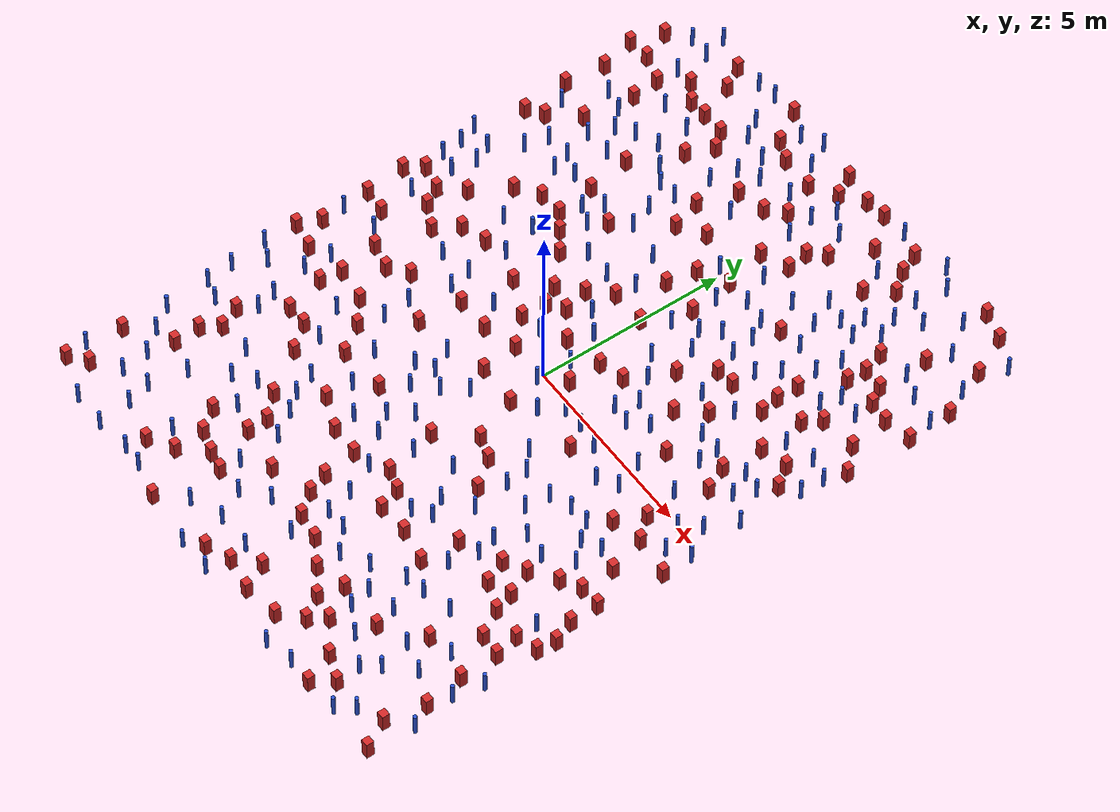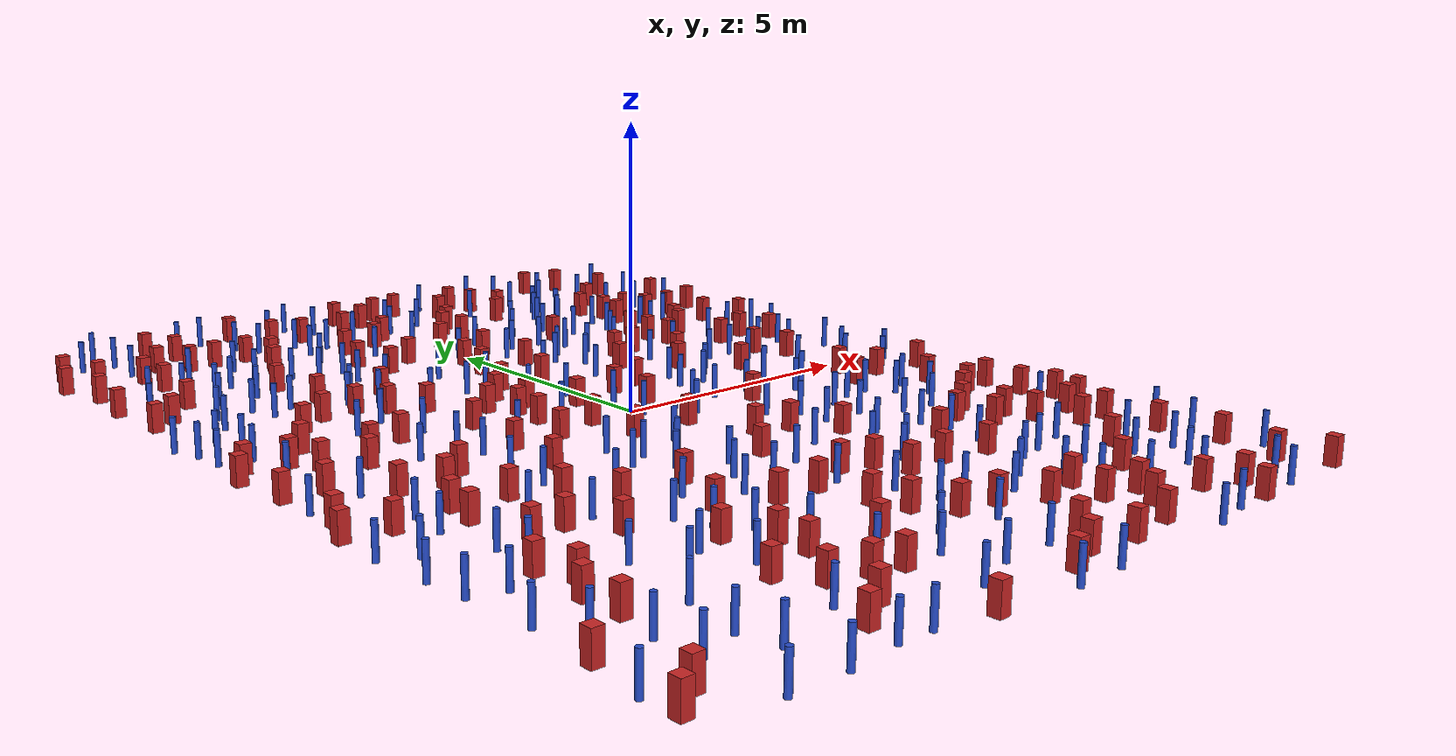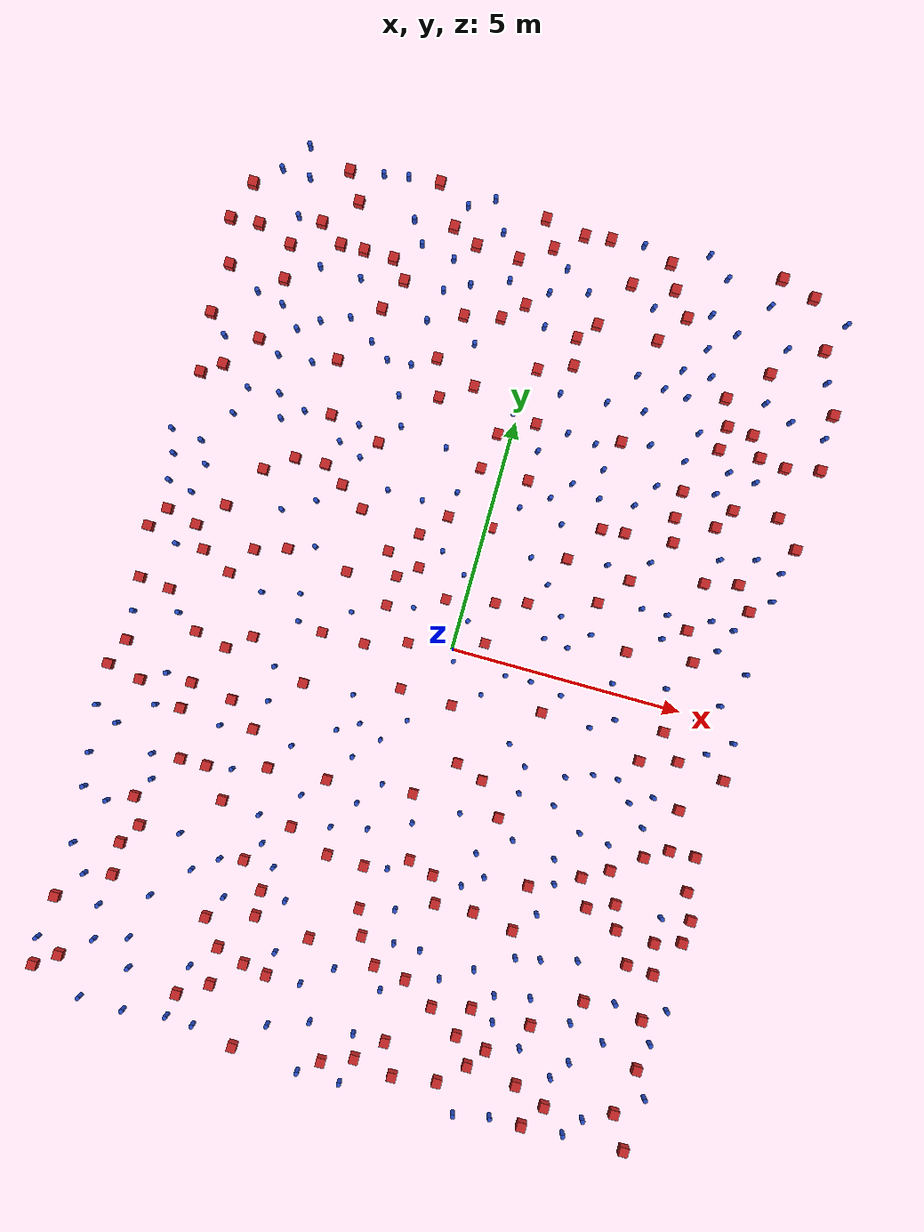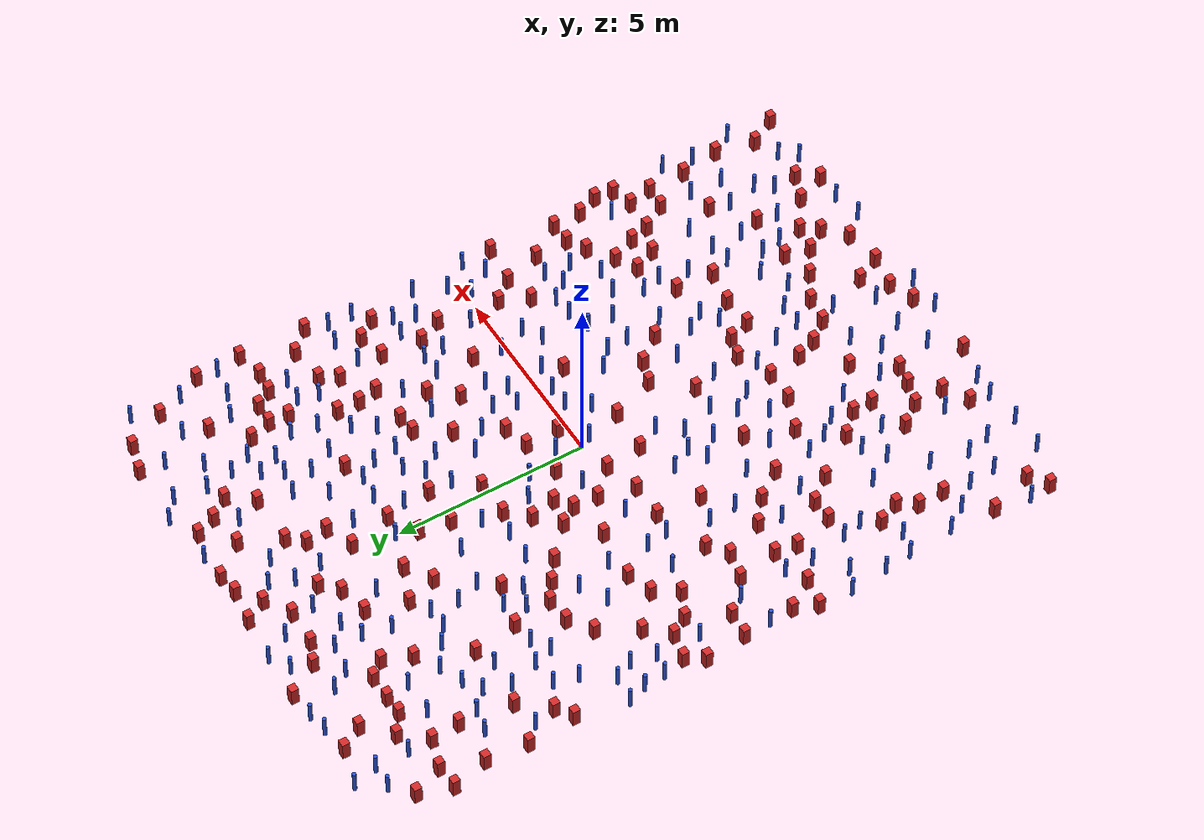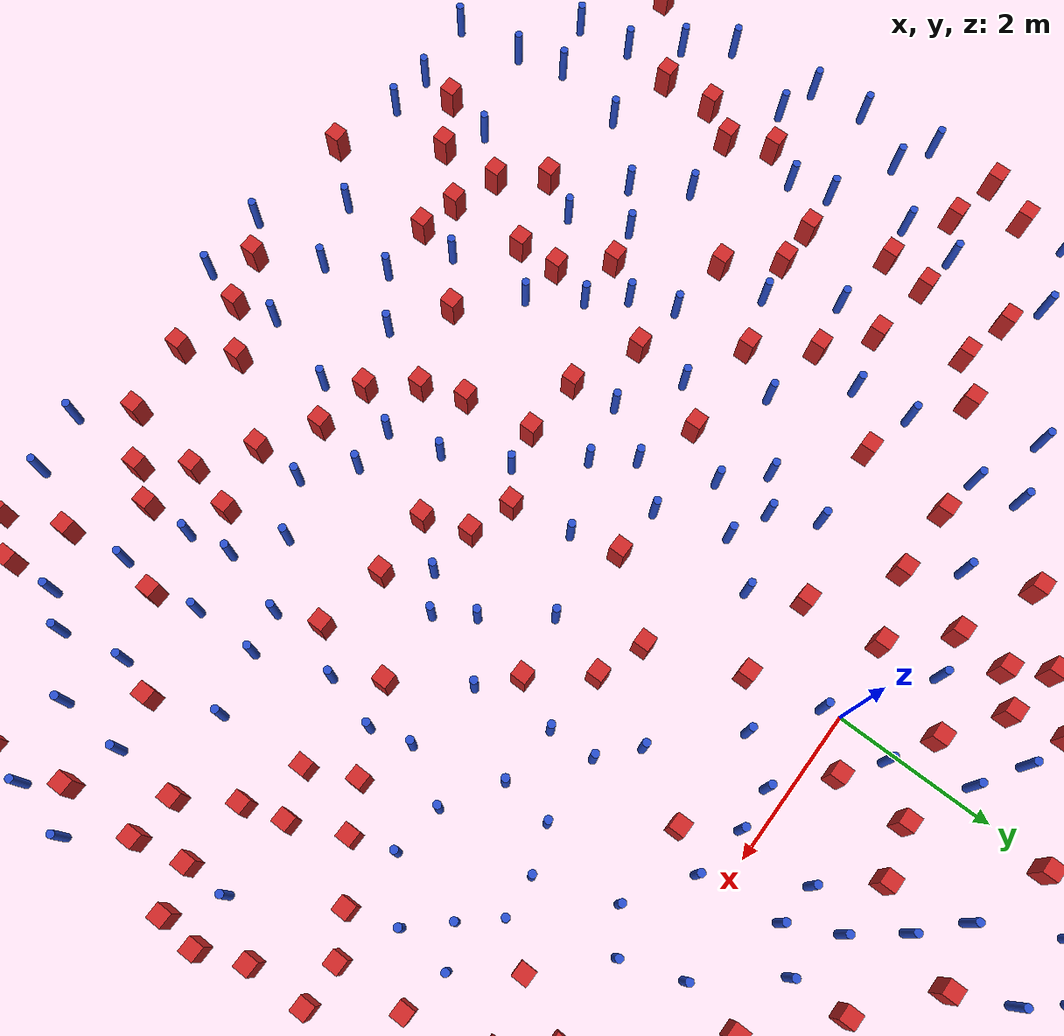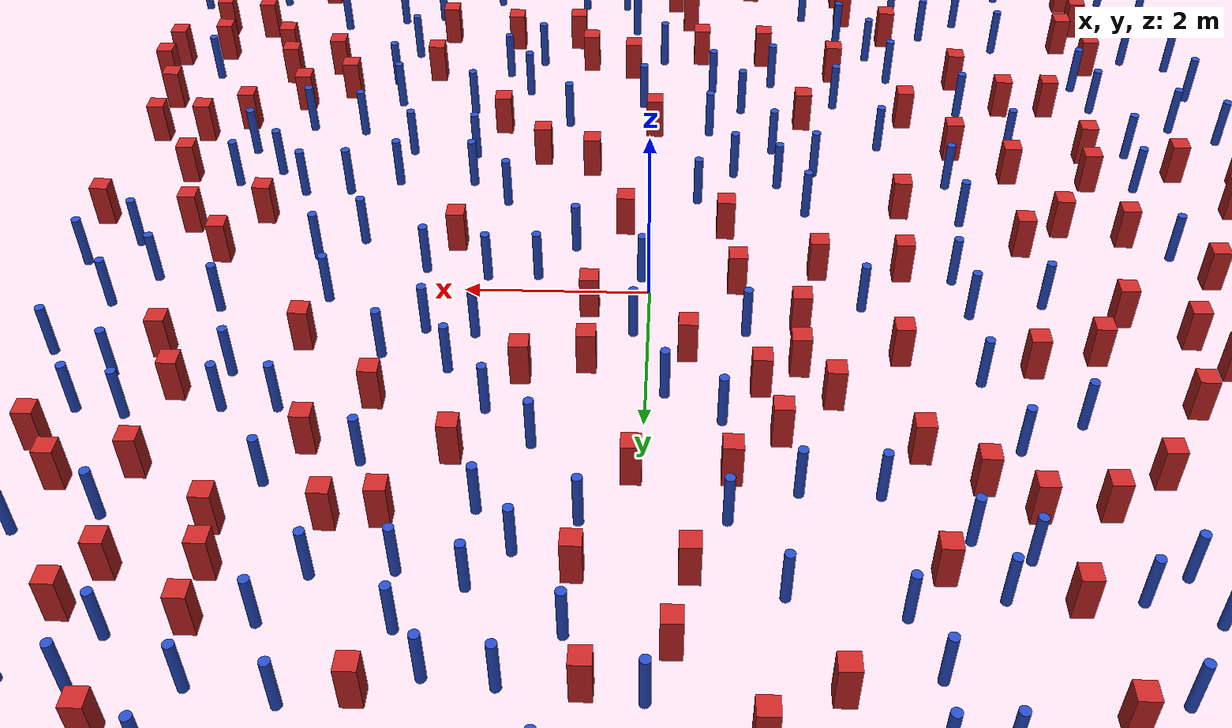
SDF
<sdf version="1.6">
  <model name="dense_60"><model name="square_post_obstacle0">
  <static>true</static>
  <pose frame="">-1.15167169525 1.48119965441 1.91545236811e-07 -7.35059704564e-06 1.12565212e-07 2.39332434364e-05</pose>
  <link name="link">
    <pose frame="">0 0 0.25 0 -0 0</pose>
    <inertial>
      <mass>100</mass>
      <inertia>
        <ixx>0.166667</ixx>
        <ixy>0</ixy>
        <ixz>0</ixz>
        <iyy>0.166667</iyy>
        <iyz>0</iyz>
        <izz>0.166667</izz>
      </inertia>
    </inertial>
    <collision name="collision">
      <geometry>
        <box>
          <size>.2 .2 .5</size>
        </box>
      </geometry>
      <max_contacts>10</max_contacts>
      <surface>
        <contact>
          <ode/>
        </contact>
        <bounce/>
        <friction>
          <torsional>
            <ode/>
          </torsional>
          <ode/>
        </friction>
      </surface>
    </collision>
    <visual name="visual">
      <geometry>
        <box>
          <size>.2 .2 .5</size>
        </box>
      </geometry>
      <material>
        <script>
          <name>Gazebo/Red</name>
          <uri>file://media/materials/scripts/gazebo.material</uri>
        </script>
      </material>
    </visual>
    <self_collide>0</self_collide>
    <kinematic>0</kinematic>
  </link>
</model>
<model name="square_post_obstacle1">
  <static>true</static>
  <pose frame="">-1.95325736225 5.85002496531 1.91545236811e-07 -7.35059704564e-06 1.12565212e-07 2.39332434364e-05</pose>
  <link name="link">
    <pose frame="">0 0 0.25 0 -0 0</pose>
    <inertial>
      <mass>100</mass>
      <inertia>
        <ixx>0.166667</ixx>
        <ixy>0</ixy>
        <ixz>0</ixz>
        <iyy>0.166667</iyy>
        <iyz>0</iyz>
        <izz>0.166667</izz>
      </inertia>
    </inertial>
    <collision name="collision">
      <geometry>
        <box>
          <size>.2 .2 .5</size>
        </box>
      </geometry>
      <max_contacts>10</max_contacts>
      <surface>
        <contact>
          <ode/>
        </contact>
        <bounce/>
        <friction>
          <torsional>
            <ode/>
          </torsional>
          <ode/>
        </friction>
      </surface>
    </collision>
    <visual name="visual">
      <geometry>
        <box>
          <size>.2 .2 .5</size>
        </box>
      </geometry>
      <material>
        <script>
          <name>Gazebo/Red</name>
          <uri>file://media/materials/scripts/gazebo.material</uri>
        </script>
      </material>
    </visual>
    <self_collide>0</self_collide>
    <kinematic>0</kinematic>
  </link>
</model>
<model name="pole_obstacle0">
  <static>true</static>
  <pose frame="">-3.47626348427 -2.09135809785 7.38925637345e-09 -8.47170692798e-08 1.24976764939e-08 -1.74513093025e-07</pose>
  <link name="link">
  <pose frame="">0 0 0.3 0 -0 0</pose>
    <inertial>
      <mass>1</mass>
      <inertia>
        <ixx>0.145833</ixx>
        <ixy>0</ixy>
        <ixz>0</ixz>
        <iyy>0.145833</iyy>
        <iyz>0</iyz>
        <izz>0.125</izz>
      </inertia>
    </inertial>
    <collision name="collision">
      <geometry>
        <cylinder>
          <radius>0.05</radius>
          <length>.6</length>
        </cylinder>
      </geometry>
      <max_contacts>10</max_contacts>
      <surface>
        <contact>
          <ode/>
        </contact>
        <bounce/>
        <friction>
          <torsional>
            <ode/>
          </torsional>
          <ode/>
        </friction>
      </surface>
    </collision>
    <visual name="visual">
      <geometry>
        <cylinder>
          <radius>0.05</radius>
          <length>.6</length>
        </cylinder>
      </geometry>
      <material>
        <script>
          <name>Gazebo/Blue</name>
          <uri>file://media/materials/scripts/gazebo.material</uri>
        </script>
      </material>
    </visual>
    <self_collide>0</self_collide>
    <kinematic>0</kinematic>
  </link>
</model>
<model name="square_post_obstacle2">
  <static>true</static>
  <pose frame="">1.87712716383 -3.18212368391 1.91545236811e-07 -7.35059704564e-06 1.12565212e-07 2.39332434364e-05</pose>
  <link name="link">
    <pose frame="">0 0 0.25 0 -0 0</pose>
    <inertial>
      <mass>100</mass>
      <inertia>
        <ixx>0.166667</ixx>
        <ixy>0</ixy>
        <ixz>0</ixz>
        <iyy>0.166667</iyy>
        <iyz>0</iyz>
        <izz>0.166667</izz>
      </inertia>
    </inertial>
    <collision name="collision">
      <geometry>
        <box>
          <size>.2 .2 .5</size>
        </box>
      </geometry>
      <max_contacts>10</max_contacts>
      <surface>
        <contact>
          <ode/>
        </contact>
        <bounce/>
        <friction>
          <torsional>
            <ode/>
          </torsional>
          <ode/>
        </friction>
      </surface>
    </collision>
    <visual name="visual">
      <geometry>
        <box>
          <size>.2 .2 .5</size>
        </box>
      </geometry>
      <material>
        <script>
          <name>Gazebo/Red</name>
          <uri>file://media/materials/scripts/gazebo.material</uri>
        </script>
      </material>
    </visual>
    <self_collide>0</self_collide>
    <kinematic>0</kinematic>
  </link>
</model>
<model name="pole_obstacle1">
  <static>true</static>
  <pose frame="">-2.45084201974 5.56944698751 7.38925637345e-09 -8.47170692798e-08 1.24976765033e-08 -1.74513093019e-07</pose>
  <link name="link">
  <pose frame="">0 0 0.3 0 -0 0</pose>
    <inertial>
      <mass>1</mass>
      <inertia>
        <ixx>0.145833</ixx>
        <ixy>0</ixy>
        <ixz>0</ixz>
        <iyy>0.145833</iyy>
        <iyz>0</iyz>
        <izz>0.125</izz>
      </inertia>
    </inertial>
    <collision name="collision">
      <geometry>
        <cylinder>
          <radius>0.05</radius>
          <length>.6</length>
        </cylinder>
      </geometry>
      <max_contacts>10</max_contacts>
      <surface>
        <contact>
          <ode/>
        </contact>
        <bounce/>
        <friction>
          <torsional>
            <ode/>
          </torsional>
          <ode/>
        </friction>
      </surface>
    </collision>
    <visual name="visual">
      <geometry>
        <cylinder>
          <radius>0.05</radius>
          <length>.6</length>
        </cylinder>
      </geometry>
      <material>
        <script>
          <name>Gazebo/Blue</name>
          <uri>file://media/materials/scripts/gazebo.material</uri>
        </script>
      </material>
    </visual>
    <self_collide>0</self_collide>
    <kinematic>0</kinematic>
  </link>
</model>
<model name="square_post_obstacle3">
  <static>true</static>
  <pose frame="">-6.8255019403 5.52040594219 1.91545236811e-07 -7.35059704564e-06 1.12565212e-07 2.39332434364e-05</pose>
  <link name="link">
    <pose frame="">0 0 0.25 0 -0 0</pose>
    <inertial>
      <mass>100</mass>
      <inertia>
        <ixx>0.166667</ixx>
        <ixy>0</ixy>
        <ixz>0</ixz>
        <iyy>0.166667</iyy>
        <iyz>0</iyz>
        <izz>0.166667</izz>
      </inertia>
    </inertial>
    <collision name="collision">
      <geometry>
        <box>
          <size>.2 .2 .5</size>
        </box>
      </geometry>
      <max_contacts>10</max_contacts>
      <surface>
        <contact>
          <ode/>
        </contact>
        <bounce/>
        <friction>
          <torsional>
            <ode/>
          </torsional>
          <ode/>
        </friction>
      </surface>
    </collision>
    <visual name="visual">
      <geometry>
        <box>
          <size>.2 .2 .5</size>
        </box>
      </geometry>
      <material>
        <script>
          <name>Gazebo/Red</name>
          <uri>file://media/materials/scripts/gazebo.material</uri>
        </script>
      </material>
    </visual>
    <self_collide>0</self_collide>
    <kinematic>0</kinematic>
  </link>
</model>
<model name="pole_obstacle2">
  <static>true</static>
  <pose frame="">-3.83124900783 -3.6833021294 7.38925637345e-09 -8.47170692798e-08 1.24976764939e-08 -1.74513093025e-07</pose>
  <link name="link">
  <pose frame="">0 0 0.3 0 -0 0</pose>
    <inertial>
      <mass>1</mass>
      <inertia>
        <ixx>0.145833</ixx>
        <ixy>0</ixy>
        <ixz>0</ixz>
        <iyy>0.145833</iyy>
        <iyz>0</iyz>
        <izz>0.125</izz>
      </inertia>
    </inertial>
    <collision name="collision">
      <geometry>
        <cylinder>
          <radius>0.05</radius>
          <length>.6</length>
        </cylinder>
      </geometry>
      <max_contacts>10</max_contacts>
      <surface>
        <contact>
          <ode/>
        </contact>
        <bounce/>
        <friction>
          <torsional>
            <ode/>
          </torsional>
          <ode/>
        </friction>
      </surface>
    </collision>
    <visual name="visual">
      <geometry>
        <cylinder>
          <radius>0.05</radius>
          <length>.6</length>
        </cylinder>
      </geometry>
      <material>
        <script>
          <name>Gazebo/Blue</name>
          <uri>file://media/materials/scripts/gazebo.material</uri>
        </script>
      </material>
    </visual>
    <self_collide>0</self_collide>
    <kinematic>0</kinematic>
  </link>
</model>
<model name="pole_obstacle3">
  <static>true</static>
  <pose frame="">4.94489135141 3.32337684646 7.38925637345e-09 -8.47170692798e-08 1.24976764937e-08 -1.74513093023e-07</pose>
  <link name="link">
  <pose frame="">0 0 0.3 0 -0 0</pose>
    <inertial>
      <mass>1</mass>
      <inertia>
        <ixx>0.145833</ixx>
        <ixy>0</ixy>
        <ixz>0</ixz>
        <iyy>0.145833</iyy>
        <iyz>0</iyz>
        <izz>0.125</izz>
      </inertia>
    </inertial>
    <collision name="collision">
      <geometry>
        <cylinder>
          <radius>0.05</radius>
          <length>.6</length>
        </cylinder>
      </geometry>
      <max_contacts>10</max_contacts>
      <surface>
        <contact>
          <ode/>
        </contact>
        <bounce/>
        <friction>
          <torsional>
            <ode/>
          </torsional>
          <ode/>
        </friction>
      </surface>
    </collision>
    <visual name="visual">
      <geometry>
        <cylinder>
          <radius>0.05</radius>
          <length>.6</length>
        </cylinder>
      </geometry>
      <material>
        <script>
          <name>Gazebo/Blue</name>
          <uri>file://media/materials/scripts/gazebo.material</uri>
        </script>
      </material>
    </visual>
    <self_collide>0</self_collide>
    <kinematic>0</kinematic>
  </link>
</model>
<model name="square_post_obstacle4">
  <static>true</static>
  <pose frame="">-4.94228190941 -3.76445180743 1.91545236811e-07 -7.35059704564e-06 1.12565212e-07 2.39332434364e-05</pose>
  <link name="link">
    <pose frame="">0 0 0.25 0 -0 0</pose>
    <inertial>
      <mass>100</mass>
      <inertia>
        <ixx>0.166667</ixx>
        <ixy>0</ixy>
        <ixz>0</ixz>
        <iyy>0.166667</iyy>
        <iyz>0</iyz>
        <izz>0.166667</izz>
      </inertia>
    </inertial>
    <collision name="collision">
      <geometry>
        <box>
          <size>.2 .2 .5</size>
        </box>
      </geometry>
      <max_contacts>10</max_contacts>
      <surface>
        <contact>
          <ode/>
        </contact>
        <bounce/>
        <friction>
          <torsional>
            <ode/>
          </torsional>
          <ode/>
        </friction>
      </surface>
    </collision>
    <visual name="visual">
      <geometry>
        <box>
          <size>.2 .2 .5</size>
        </box>
      </geometry>
      <material>
        <script>
          <name>Gazebo/Red</name>
          <uri>file://media/materials/scripts/gazebo.material</uri>
        </script>
      </material>
    </visual>
    <self_collide>0</self_collide>
    <kinematic>0</kinematic>
  </link>
</model>
<model name="square_post_obstacle5">
  <static>true</static>
  <pose frame="">-6.61051850464 1.26924231321 1.91545236811e-07 -7.35059704564e-06 1.12565212e-07 2.39332434364e-05</pose>
  <link name="link">
    <pose frame="">0 0 0.25 0 -0 0</pose>
    <inertial>
      <mass>100</mass>
      <inertia>
        <ixx>0.166667</ixx>
        <ixy>0</ixy>
        <ixz>0</ixz>
        <iyy>0.166667</iyy>
        <iyz>0</iyz>
        <izz>0.166667</izz>
      </inertia>
    </inertial>
    <collision name="collision">
      <geometry>
        <box>
          <size>.2 .2 .5</size>
        </box>
      </geometry>
      <max_contacts>10</max_contacts>
      <surface>
        <contact>
          <ode/>
        </contact>
        <bounce/>
        <friction>
          <torsional>
            <ode/>
          </torsional>
          <ode/>
        </friction>
      </surface>
    </collision>
    <visual name="visual">
      <geometry>
        <box>
          <size>.2 .2 .5</size>
        </box>
      </geometry>
      <material>
        <script>
          <name>Gazebo/Red</name>
          <uri>file://media/materials/scripts/gazebo.material</uri>
        </script>
      </material>
    </visual>
    <self_collide>0</self_collide>
    <kinematic>0</kinematic>
  </link>
</model>
<model name="square_post_obstacle6">
  <static>true</static>
  <pose frame="">-1.40444385143 -4.89903000898 1.91545236811e-07 -7.35059704564e-06 1.12565212e-07 2.39332434364e-05</pose>
  <link name="link">
    <pose frame="">0 0 0.25 0 -0 0</pose>
    <inertial>
      <mass>100</mass>
      <inertia>
        <ixx>0.166667</ixx>
        <ixy>0</ixy>
        <ixz>0</ixz>
        <iyy>0.166667</iyy>
        <iyz>0</iyz>
        <izz>0.166667</izz>
      </inertia>
    </inertial>
    <collision name="collision">
      <geometry>
        <box>
          <size>.2 .2 .5</size>
        </box>
      </geometry>
      <max_contacts>10</max_contacts>
      <surface>
        <contact>
          <ode/>
        </contact>
        <bounce/>
        <friction>
          <torsional>
            <ode/>
          </torsional>
          <ode/>
        </friction>
      </surface>
    </collision>
    <visual name="visual">
      <geometry>
        <box>
          <size>.2 .2 .5</size>
        </box>
      </geometry>
      <material>
        <script>
          <name>Gazebo/Red</name>
          <uri>file://media/materials/scripts/gazebo.material</uri>
        </script>
      </material>
    </visual>
    <self_collide>0</self_collide>
    <kinematic>0</kinematic>
  </link>
</model>
<model name="pole_obstacle4">
  <static>true</static>
  <pose frame="">2.73553386791 1.0680887343 7.38925637345e-09 -8.471706928e-08 1.24976765152e-08 -1.74513093012e-07</pose>
  <link name="link">
  <pose frame="">0 0 0.3 0 -0 0</pose>
    <inertial>
      <mass>1</mass>
      <inertia>
        <ixx>0.145833</ixx>
        <ixy>0</ixy>
        <ixz>0</ixz>
        <iyy>0.145833</iyy>
        <iyz>0</iyz>
        <izz>0.125</izz>
      </inertia>
    </inertial>
    <collision name="collision">
      <geometry>
        <cylinder>
          <radius>0.05</radius>
          <length>.6</length>
        </cylinder>
      </geometry>
      <max_contacts>10</max_contacts>
      <surface>
        <contact>
          <ode/>
        </contact>
        <bounce/>
        <friction>
          <torsional>
            <ode/>
          </torsional>
          <ode/>
        </friction>
      </surface>
    </collision>
    <visual name="visual">
      <geometry>
        <cylinder>
          <radius>0.05</radius>
          <length>.6</length>
        </cylinder>
      </geometry>
      <material>
        <script>
          <name>Gazebo/Blue</name>
          <uri>file://media/materials/scripts/gazebo.material</uri>
        </script>
      </material>
    </visual>
    <self_collide>0</self_collide>
    <kinematic>0</kinematic>
  </link>
</model>
<model name="pole_obstacle5">
  <static>true</static>
  <pose frame="">4.18884010764 1.90581035979 7.38925637345e-09 -8.471706928e-08 1.24976765134e-08 -1.74513093015e-07</pose>
  <link name="link">
  <pose frame="">0 0 0.3 0 -0 0</pose>
    <inertial>
      <mass>1</mass>
      <inertia>
        <ixx>0.145833</ixx>
        <ixy>0</ixy>
        <ixz>0</ixz>
        <iyy>0.145833</iyy>
        <iyz>0</iyz>
        <izz>0.125</izz>
      </inertia>
    </inertial>
    <collision name="collision">
      <geometry>
        <cylinder>
          <radius>0.05</radius>
          <length>.6</length>
        </cylinder>
      </geometry>
      <max_contacts>10</max_contacts>
      <surface>
        <contact>
          <ode/>
        </contact>
        <bounce/>
        <friction>
          <torsional>
            <ode/>
          </torsional>
          <ode/>
        </friction>
      </surface>
    </collision>
    <visual name="visual">
      <geometry>
        <cylinder>
          <radius>0.05</radius>
          <length>.6</length>
        </cylinder>
      </geometry>
      <material>
        <script>
          <name>Gazebo/Blue</name>
          <uri>file://media/materials/scripts/gazebo.material</uri>
        </script>
      </material>
    </visual>
    <self_collide>0</self_collide>
    <kinematic>0</kinematic>
  </link>
</model>
<model name="square_post_obstacle7">
  <static>true</static>
  <pose frame="">-1.78532070272 8.3839280354 1.91545236811e-07 -7.35059704564e-06 1.12565212e-07 2.39332434364e-05</pose>
  <link name="link">
    <pose frame="">0 0 0.25 0 -0 0</pose>
    <inertial>
      <mass>100</mass>
      <inertia>
        <ixx>0.166667</ixx>
        <ixy>0</ixy>
        <ixz>0</ixz>
        <iyy>0.166667</iyy>
        <iyz>0</iyz>
        <izz>0.166667</izz>
      </inertia>
    </inertial>
    <collision name="collision">
      <geometry>
        <box>
          <size>.2 .2 .5</size>
        </box>
      </geometry>
      <max_contacts>10</max_contacts>
      <surface>
        <contact>
          <ode/>
        </contact>
        <bounce/>
        <friction>
          <torsional>
            <ode/>
          </torsional>
          <ode/>
        </friction>
      </surface>
    </collision>
    <visual name="visual">
      <geometry>
        <box>
          <size>.2 .2 .5</size>
        </box>
      </geometry>
      <material>
        <script>
          <name>Gazebo/Red</name>
          <uri>file://media/materials/scripts/gazebo.material</uri>
        </script>
      </material>
    </visual>
    <self_collide>0</self_collide>
    <kinematic>0</kinematic>
  </link>
</model>
<model name="square_post_obstacle8">
  <static>true</static>
  <pose frame="">-4.5635573513 7.63697502963 1.91545236811e-07 -7.35059704564e-06 1.12565212e-07 2.39332434364e-05</pose>
  <link name="link">
    <pose frame="">0 0 0.25 0 -0 0</pose>
    <inertial>
      <mass>100</mass>
      <inertia>
        <ixx>0.166667</ixx>
        <ixy>0</ixy>
        <ixz>0</ixz>
        <iyy>0.166667</iyy>
        <iyz>0</iyz>
        <izz>0.166667</izz>
      </inertia>
    </inertial>
    <collision name="collision">
      <geometry>
        <box>
          <size>.2 .2 .5</size>
        </box>
      </geometry>
      <max_contacts>10</max_contacts>
      <surface>
        <contact>
          <ode/>
        </contact>
        <bounce/>
        <friction>
          <torsional>
            <ode/>
          </torsional>
          <ode/>
        </friction>
      </surface>
    </collision>
    <visual name="visual">
      <geometry>
        <box>
          <size>.2 .2 .5</size>
        </box>
      </geometry>
      <material>
        <script>
          <name>Gazebo/Red</name>
          <uri>file://media/materials/scripts/gazebo.material</uri>
        </script>
      </material>
    </visual>
    <self_collide>0</self_collide>
    <kinematic>0</kinematic>
  </link>
</model>
<model name="pole_obstacle6">
  <static>true</static>
  <pose frame="">5.271577572 -7.18126744558 7.38925637345e-09 -8.47170692796e-08 1.24976764786e-08 -1.74513093032e-07</pose>
  <link name="link">
  <pose frame="">0 0 0.3 0 -0 0</pose>
    <inertial>
      <mass>1</mass>
      <inertia>
        <ixx>0.145833</ixx>
        <ixy>0</ixy>
        <ixz>0</ixz>
        <iyy>0.145833</iyy>
        <iyz>0</iyz>
        <izz>0.125</izz>
      </inertia>
    </inertial>
    <collision name="collision">
      <geometry>
        <cylinder>
          <radius>0.05</radius>
          <length>.6</length>
        </cylinder>
      </geometry>
      <max_contacts>10</max_contacts>
      <surface>
        <contact>
          <ode/>
        </contact>
        <bounce/>
        <friction>
          <torsional>
            <ode/>
          </torsional>
          <ode/>
        </friction>
      </surface>
    </collision>
    <visual name="visual">
      <geometry>
        <cylinder>
          <radius>0.05</radius>
          <length>.6</length>
        </cylinder>
      </geometry>
      <material>
        <script>
          <name>Gazebo/Blue</name>
          <uri>file://media/materials/scripts/gazebo.material</uri>
        </script>
      </material>
    </visual>
    <self_collide>0</self_collide>
    <kinematic>0</kinematic>
  </link>
</model>
<model name="pole_obstacle7">
  <static>true</static>
  <pose frame="">5.28432317907 -8.86306961432 7.38925637345e-09 -8.471706928e-08 1.24976765081e-08 -1.74513093015e-07</pose>
  <link name="link">
  <pose frame="">0 0 0.3 0 -0 0</pose>
    <inertial>
      <mass>1</mass>
      <inertia>
        <ixx>0.145833</ixx>
        <ixy>0</ixy>
        <ixz>0</ixz>
        <iyy>0.145833</iyy>
        <iyz>0</iyz>
        <izz>0.125</izz>
      </inertia>
    </inertial>
    <collision name="collision">
      <geometry>
        <cylinder>
          <radius>0.05</radius>
          <length>.6</length>
        </cylinder>
      </geometry>
      <max_contacts>10</max_contacts>
      <surface>
        <contact>
          <ode/>
        </contact>
        <bounce/>
        <friction>
          <torsional>
            <ode/>
          </torsional>
          <ode/>
        </friction>
      </surface>
    </collision>
    <visual name="visual">
      <geometry>
        <cylinder>
          <radius>0.05</radius>
          <length>.6</length>
        </cylinder>
      </geometry>
      <material>
        <script>
          <name>Gazebo/Blue</name>
          <uri>file://media/materials/scripts/gazebo.material</uri>
        </script>
      </material>
    </visual>
    <self_collide>0</self_collide>
    <kinematic>0</kinematic>
  </link>
</model>
<model name="square_post_obstacle9">
  <static>true</static>
  <pose frame="">-0.950290578173 -0.117729899493 1.91545236811e-07 -7.35059704564e-06 1.12565212e-07 2.39332434364e-05</pose>
  <link name="link">
    <pose frame="">0 0 0.25 0 -0 0</pose>
    <inertial>
      <mass>100</mass>
      <inertia>
        <ixx>0.166667</ixx>
        <ixy>0</ixy>
        <ixz>0</ixz>
        <iyy>0.166667</iyy>
        <iyz>0</iyz>
        <izz>0.166667</izz>
      </inertia>
    </inertial>
    <collision name="collision">
      <geometry>
        <box>
          <size>.2 .2 .5</size>
        </box>
      </geometry>
      <max_contacts>10</max_contacts>
      <surface>
        <contact>
          <ode/>
        </contact>
        <bounce/>
        <friction>
          <torsional>
            <ode/>
          </torsional>
          <ode/>
        </friction>
      </surface>
    </collision>
    <visual name="visual">
      <geometry>
        <box>
          <size>.2 .2 .5</size>
        </box>
      </geometry>
      <material>
        <script>
          <name>Gazebo/Red</name>
          <uri>file://media/materials/scripts/gazebo.material</uri>
        </script>
      </material>
    </visual>
    <self_collide>0</self_collide>
    <kinematic>0</kinematic>
  </link>
</model>
<model name="square_post_obstacle10">
  <static>true</static>
  <pose frame="">0.151992976209 6.1870169519 1.91545236811e-07 -7.35059704564e-06 1.12565212e-07 2.39332434364e-05</pose>
  <link name="link">
    <pose frame="">0 0 0.25 0 -0 0</pose>
    <inertial>
      <mass>100</mass>
      <inertia>
        <ixx>0.166667</ixx>
        <ixy>0</ixy>
        <ixz>0</ixz>
        <iyy>0.166667</iyy>
        <iyz>0</iyz>
        <izz>0.166667</izz>
      </inertia>
    </inertial>
    <collision name="collision">
      <geometry>
        <box>
          <size>.2 .2 .5</size>
        </box>
      </geometry>
      <max_contacts>10</max_contacts>
      <surface>
        <contact>
          <ode/>
        </contact>
        <bounce/>
        <friction>
          <torsional>
            <ode/>
          </torsional>
          <ode/>
        </friction>
      </surface>
    </collision>
    <visual name="visual">
      <geometry>
        <box>
          <size>.2 .2 .5</size>
        </box>
      </geometry>
      <material>
        <script>
          <name>Gazebo/Red</name>
          <uri>file://media/materials/scripts/gazebo.material</uri>
        </script>
      </material>
    </visual>
    <self_collide>0</self_collide>
    <kinematic>0</kinematic>
  </link>
</model>
<model name="square_post_obstacle11">
  <static>true</static>
  <pose frame="">-3.7944851988 4.10195217841 1.91545236811e-07 -7.35059704564e-06 1.12565212e-07 2.39332434364e-05</pose>
  <link name="link">
    <pose frame="">0 0 0.25 0 -0 0</pose>
    <inertial>
      <mass>100</mass>
      <inertia>
        <ixx>0.166667</ixx>
        <ixy>0</ixy>
        <ixz>0</ixz>
        <iyy>0.166667</iyy>
        <iyz>0</iyz>
        <izz>0.166667</izz>
      </inertia>
    </inertial>
    <collision name="collision">
      <geometry>
        <box>
          <size>.2 .2 .5</size>
        </box>
      </geometry>
      <max_contacts>10</max_contacts>
      <surface>
        <contact>
          <ode/>
        </contact>
        <bounce/>
        <friction>
          <torsional>
            <ode/>
          </torsional>
          <ode/>
        </friction>
      </surface>
    </collision>
    <visual name="visual">
      <geometry>
        <box>
          <size>.2 .2 .5</size>
        </box>
      </geometry>
      <material>
        <script>
          <name>Gazebo/Red</name>
          <uri>file://media/materials/scripts/gazebo.material</uri>
        </script>
      </material>
    </visual>
    <self_collide>0</self_collide>
    <kinematic>0</kinematic>
  </link>
</model>
<model name="square_post_obstacle12">
  <static>true</static>
  <pose frame="">2.69776393869 1.7626080825 1.91545236811e-07 -7.35059704564e-06 1.12565212e-07 2.39332434364e-05</pose>
  <link name="link">
    <pose frame="">0 0 0.25 0 -0 0</pose>
    <inertial>
      <mass>100</mass>
      <inertia>
        <ixx>0.166667</ixx>
        <ixy>0</ixy>
        <ixz>0</ixz>
        <iyy>0.166667</iyy>
        <iyz>0</iyz>
        <izz>0.166667</izz>
      </inertia>
    </inertial>
    <collision name="collision">
      <geometry>
        <box>
          <size>.2 .2 .5</size>
        </box>
      </geometry>
      <max_contacts>10</max_contacts>
      <surface>
        <contact>
          <ode/>
        </contact>
        <bounce/>
        <friction>
          <torsional>
            <ode/>
          </torsional>
          <ode/>
        </friction>
      </surface>
    </collision>
    <visual name="visual">
      <geometry>
        <box>
          <size>.2 .2 .5</size>
        </box>
      </geometry>
      <material>
        <script>
          <name>Gazebo/Red</name>
          <uri>file://media/materials/scripts/gazebo.material</uri>
        </script>
      </material>
    </visual>
    <self_collide>0</self_collide>
    <kinematic>0</kinematic>
  </link>
</model>
<model name="square_post_obstacle13">
  <static>true</static>
  <pose frame="">0.290490334765 -1.14874622787 1.91545236811e-07 -7.35059704564e-06 1.12565212e-07 2.39332434364e-05</pose>
  <link name="link">
    <pose frame="">0 0 0.25 0 -0 0</pose>
    <inertial>
      <mass>100</mass>
      <inertia>
        <ixx>0.166667</ixx>
        <ixy>0</ixy>
        <ixz>0</ixz>
        <iyy>0.166667</iyy>
        <iyz>0</iyz>
        <izz>0.166667</izz>
      </inertia>
    </inertial>
    <collision name="collision">
      <geometry>
        <box>
          <size>.2 .2 .5</size>
        </box>
      </geometry>
      <max_contacts>10</max_contacts>
      <surface>
        <contact>
          <ode/>
        </contact>
        <bounce/>
        <friction>
          <torsional>
            <ode/>
          </torsional>
          <ode/>
        </friction>
      </surface>
    </collision>
    <visual name="visual">
      <geometry>
        <box>
          <size>.2 .2 .5</size>
        </box>
      </geometry>
      <material>
        <script>
          <name>Gazebo/Red</name>
          <uri>file://media/materials/scripts/gazebo.material</uri>
        </script>
      </material>
    </visual>
    <self_collide>0</self_collide>
    <kinematic>0</kinematic>
  </link>
</model>
<model name="pole_obstacle8">
  <static>true</static>
  <pose frame="">3.60438439242 -7.76545788846 7.38925637345e-09 -8.47170692798e-08 1.24976765033e-08 -1.74513093019e-07</pose>
  <link name="link">
  <pose frame="">0 0 0.3 0 -0 0</pose>
    <inertial>
      <mass>1</mass>
      <inertia>
        <ixx>0.145833</ixx>
        <ixy>0</ixy>
        <ixz>0</ixz>
        <iyy>0.145833</iyy>
        <iyz>0</iyz>
        <izz>0.125</izz>
      </inertia>
    </inertial>
    <collision name="collision">
      <geometry>
        <cylinder>
          <radius>0.05</radius>
          <length>.6</length>
        </cylinder>
      </geometry>
      <max_contacts>10</max_contacts>
      <surface>
        <contact>
          <ode/>
        </contact>
        <bounce/>
        <friction>
          <torsional>
            <ode/>
          </torsional>
          <ode/>
        </friction>
      </surface>
    </collision>
    <visual name="visual">
      <geometry>
        <cylinder>
          <radius>0.05</radius>
          <length>.6</length>
        </cylinder>
      </geometry>
      <material>
        <script>
          <name>Gazebo/Blue</name>
          <uri>file://media/materials/scripts/gazebo.material</uri>
        </script>
      </material>
    </visual>
    <self_collide>0</self_collide>
    <kinematic>0</kinematic>
  </link>
</model>
<model name="square_post_obstacle14">
  <static>true</static>
  <pose frame="">3.55823253069 0.921977844736 1.91545236811e-07 -7.35059704564e-06 1.12565212e-07 2.39332434364e-05</pose>
  <link name="link">
    <pose frame="">0 0 0.25 0 -0 0</pose>
    <inertial>
      <mass>100</mass>
      <inertia>
        <ixx>0.166667</ixx>
        <ixy>0</ixy>
        <ixz>0</ixz>
        <iyy>0.166667</iyy>
        <iyz>0</iyz>
        <izz>0.166667</izz>
      </inertia>
    </inertial>
    <collision name="collision">
      <geometry>
        <box>
          <size>.2 .2 .5</size>
        </box>
      </geometry>
      <max_contacts>10</max_contacts>
      <surface>
        <contact>
          <ode/>
        </contact>
        <bounce/>
        <friction>
          <torsional>
            <ode/>
          </torsional>
          <ode/>
        </friction>
      </surface>
    </collision>
    <visual name="visual">
      <geometry>
        <box>
          <size>.2 .2 .5</size>
        </box>
      </geometry>
      <material>
        <script>
          <name>Gazebo/Red</name>
          <uri>file://media/materials/scripts/gazebo.material</uri>
        </script>
      </material>
    </visual>
    <self_collide>0</self_collide>
    <kinematic>0</kinematic>
  </link>
</model>
<model name="square_post_obstacle15">
  <static>true</static>
  <pose frame="">-6.12516694566 -0.35473652986 1.91545236811e-07 -7.35059704564e-06 1.12565212e-07 2.39332434364e-05</pose>
  <link name="link">
    <pose frame="">0 0 0.25 0 -0 0</pose>
    <inertial>
      <mass>100</mass>
      <inertia>
        <ixx>0.166667</ixx>
        <ixy>0</ixy>
        <ixz>0</ixz>
        <iyy>0.166667</iyy>
        <iyz>0</iyz>
        <izz>0.166667</izz>
      </inertia>
    </inertial>
    <collision name="collision">
      <geometry>
        <box>
          <size>.2 .2 .5</size>
        </box>
      </geometry>
      <max_contacts>10</max_contacts>
      <surface>
        <contact>
          <ode/>
        </contact>
        <bounce/>
        <friction>
          <torsional>
            <ode/>
          </torsional>
          <ode/>
        </friction>
      </surface>
    </collision>
    <visual name="visual">
      <geometry>
        <box>
          <size>.2 .2 .5</size>
        </box>
      </geometry>
      <material>
        <script>
          <name>Gazebo/Red</name>
          <uri>file://media/materials/scripts/gazebo.material</uri>
        </script>
      </material>
    </visual>
    <self_collide>0</self_collide>
    <kinematic>0</kinematic>
  </link>
</model>
<model name="square_post_obstacle16">
  <static>true</static>
  <pose frame="">-6.69537280962 8.40024844896 1.91545236811e-07 -7.35059704564e-06 1.12565212e-07 2.39332434364e-05</pose>
  <link name="link">
    <pose frame="">0 0 0.25 0 -0 0</pose>
    <inertial>
      <mass>100</mass>
      <inertia>
        <ixx>0.166667</ixx>
        <ixy>0</ixy>
        <ixz>0</ixz>
        <iyy>0.166667</iyy>
        <iyz>0</iyz>
        <izz>0.166667</izz>
      </inertia>
    </inertial>
    <collision name="collision">
      <geometry>
        <box>
          <size>.2 .2 .5</size>
        </box>
      </geometry>
      <max_contacts>10</max_contacts>
      <surface>
        <contact>
          <ode/>
        </contact>
        <bounce/>
        <friction>
          <torsional>
            <ode/>
          </torsional>
          <ode/>
        </friction>
      </surface>
    </collision>
    <visual name="visual">
      <geometry>
        <box>
          <size>.2 .2 .5</size>
        </box>
      </geometry>
      <material>
        <script>
          <name>Gazebo/Red</name>
          <uri>file://media/materials/scripts/gazebo.material</uri>
        </script>
      </material>
    </visual>
    <self_collide>0</self_collide>
    <kinematic>0</kinematic>
  </link>
</model>
<model name="pole_obstacle9">
  <static>true</static>
  <pose frame="">3.36343080901 6.44973814453 7.38925637345e-09 -8.47170692798e-08 1.24976765033e-08 -1.74513093019e-07</pose>
  <link name="link">
  <pose frame="">0 0 0.3 0 -0 0</pose>
    <inertial>
      <mass>1</mass>
      <inertia>
        <ixx>0.145833</ixx>
        <ixy>0</ixy>
        <ixz>0</ixz>
        <iyy>0.145833</iyy>
        <iyz>0</iyz>
        <izz>0.125</izz>
      </inertia>
    </inertial>
    <collision name="collision">
      <geometry>
        <cylinder>
          <radius>0.05</radius>
          <length>.6</length>
        </cylinder>
      </geometry>
      <max_contacts>10</max_contacts>
      <surface>
        <contact>
          <ode/>
        </contact>
        <bounce/>
        <friction>
          <torsional>
            <ode/>
          </torsional>
          <ode/>
        </friction>
      </surface>
    </collision>
    <visual name="visual">
      <geometry>
        <cylinder>
          <radius>0.05</radius>
          <length>.6</length>
        </cylinder>
      </geometry>
      <material>
        <script>
          <name>Gazebo/Blue</name>
          <uri>file://media/materials/scripts/gazebo.material</uri>
        </script>
      </material>
    </visual>
    <self_collide>0</self_collide>
    <kinematic>0</kinematic>
  </link>
</model>
<model name="square_post_obstacle17">
  <static>true</static>
  <pose frame="">-3.07128477709 -8.20239735445 1.91545236811e-07 -7.35059704564e-06 1.12565212e-07 2.39332434364e-05</pose>
  <link name="link">
    <pose frame="">0 0 0.25 0 -0 0</pose>
    <inertial>
      <mass>100</mass>
      <inertia>
        <ixx>0.166667</ixx>
        <ixy>0</ixy>
        <ixz>0</ixz>
        <iyy>0.166667</iyy>
        <iyz>0</iyz>
        <izz>0.166667</izz>
      </inertia>
    </inertial>
    <collision name="collision">
      <geometry>
        <box>
          <size>.2 .2 .5</size>
        </box>
      </geometry>
      <max_contacts>10</max_contacts>
      <surface>
        <contact>
          <ode/>
        </contact>
        <bounce/>
        <friction>
          <torsional>
            <ode/>
          </torsional>
          <ode/>
        </friction>
      </surface>
    </collision>
    <visual name="visual">
      <geometry>
        <box>
          <size>.2 .2 .5</size>
        </box>
      </geometry>
      <material>
        <script>
          <name>Gazebo/Red</name>
          <uri>file://media/materials/scripts/gazebo.material</uri>
        </script>
      </material>
    </visual>
    <self_collide>0</self_collide>
    <kinematic>0</kinematic>
  </link>
</model>
<model name="square_post_obstacle18">
  <static>true</static>
  <pose frame="">2.3626673813 3.28751693555 1.91545236811e-07 -7.35059704564e-06 1.12565212e-07 2.39332434364e-05</pose>
  <link name="link">
    <pose frame="">0 0 0.25 0 -0 0</pose>
    <inertial>
      <mass>100</mass>
      <inertia>
        <ixx>0.166667</ixx>
        <ixy>0</ixy>
        <ixz>0</ixz>
        <iyy>0.166667</iyy>
        <iyz>0</iyz>
        <izz>0.166667</izz>
      </inertia>
    </inertial>
    <collision name="collision">
      <geometry>
        <box>
          <size>.2 .2 .5</size>
        </box>
      </geometry>
      <max_contacts>10</max_contacts>
      <surface>
        <contact>
          <ode/>
        </contact>
        <bounce/>
        <friction>
          <torsional>
            <ode/>
          </torsional>
          <ode/>
        </friction>
      </surface>
    </collision>
    <visual name="visual">
      <geometry>
        <box>
          <size>.2 .2 .5</size>
        </box>
      </geometry>
      <material>
        <script>
          <name>Gazebo/Red</name>
          <uri>file://media/materials/scripts/gazebo.material</uri>
        </script>
      </material>
    </visual>
    <self_collide>0</self_collide>
    <kinematic>0</kinematic>
  </link>
</model>
<model name="pole_obstacle10">
  <static>true</static>
  <pose frame="">-6.95964568385 -3.12976137409 7.38925637345e-09 -8.47170692798e-08 1.24976764937e-08 -1.74513093023e-07</pose>
  <link name="link">
  <pose frame="">0 0 0.3 0 -0 0</pose>
    <inertial>
      <mass>1</mass>
      <inertia>
        <ixx>0.145833</ixx>
        <ixy>0</ixy>
        <ixz>0</ixz>
        <iyy>0.145833</iyy>
        <iyz>0</iyz>
        <izz>0.125</izz>
      </inertia>
    </inertial>
    <collision name="collision">
      <geometry>
        <cylinder>
          <radius>0.05</radius>
          <length>.6</length>
        </cylinder>
      </geometry>
      <max_contacts>10</max_contacts>
      <surface>
        <contact>
          <ode/>
        </contact>
        <bounce/>
        <friction>
          <torsional>
            <ode/>
          </torsional>
          <ode/>
        </friction>
      </surface>
    </collision>
    <visual name="visual">
      <geometry>
        <cylinder>
          <radius>0.05</radius>
          <length>.6</length>
        </cylinder>
      </geometry>
      <material>
        <script>
          <name>Gazebo/Blue</name>
          <uri>file://media/materials/scripts/gazebo.material</uri>
        </script>
      </material>
    </visual>
    <self_collide>0</self_collide>
    <kinematic>0</kinematic>
  </link>
</model>
<model name="square_post_obstacle19">
  <static>true</static>
  <pose frame="">4.9296306093 7.40265655572 1.91545236811e-07 -7.35059704564e-06 1.12565212e-07 2.39332434364e-05</pose>
  <link name="link">
    <pose frame="">0 0 0.25 0 -0 0</pose>
    <inertial>
      <mass>100</mass>
      <inertia>
        <ixx>0.166667</ixx>
        <ixy>0</ixy>
        <ixz>0</ixz>
        <iyy>0.166667</iyy>
        <iyz>0</iyz>
        <izz>0.166667</izz>
      </inertia>
    </inertial>
    <collision name="collision">
      <geometry>
        <box>
          <size>.2 .2 .5</size>
        </box>
      </geometry>
      <max_contacts>10</max_contacts>
      <surface>
        <contact>
          <ode/>
        </contact>
        <bounce/>
        <friction>
          <torsional>
            <ode/>
          </torsional>
          <ode/>
        </friction>
      </surface>
    </collision>
    <visual name="visual">
      <geometry>
        <box>
          <size>.2 .2 .5</size>
        </box>
      </geometry>
      <material>
        <script>
          <name>Gazebo/Red</name>
          <uri>file://media/materials/scripts/gazebo.material</uri>
        </script>
      </material>
    </visual>
    <self_collide>0</self_collide>
    <kinematic>0</kinematic>
  </link>
</model>
<model name="pole_obstacle11">
  <static>true</static>
  <pose frame="">5.30130845704 -6.31877070383 7.38925637345e-09 -8.47170692796e-08 1.24976764786e-08 -1.74513093032e-07</pose>
  <link name="link">
  <pose frame="">0 0 0.3 0 -0 0</pose>
    <inertial>
      <mass>1</mass>
      <inertia>
        <ixx>0.145833</ixx>
        <ixy>0</ixy>
        <ixz>0</ixz>
        <iyy>0.145833</iyy>
        <iyz>0</iyz>
        <izz>0.125</izz>
      </inertia>
    </inertial>
    <collision name="collision">
      <geometry>
        <cylinder>
          <radius>0.05</radius>
          <length>.6</length>
        </cylinder>
      </geometry>
      <max_contacts>10</max_contacts>
      <surface>
        <contact>
          <ode/>
        </contact>
        <bounce/>
        <friction>
          <torsional>
            <ode/>
          </torsional>
          <ode/>
        </friction>
      </surface>
    </collision>
    <visual name="visual">
      <geometry>
        <cylinder>
          <radius>0.05</radius>
          <length>.6</length>
        </cylinder>
      </geometry>
      <material>
        <script>
          <name>Gazebo/Blue</name>
          <uri>file://media/materials/scripts/gazebo.material</uri>
        </script>
      </material>
    </visual>
    <self_collide>0</self_collide>
    <kinematic>0</kinematic>
  </link>
</model>
<model name="square_post_obstacle20">
  <static>true</static>
  <pose frame="">-6.71002976934 4.24641081246 1.91545236811e-07 -7.35059704564e-06 1.12565212e-07 2.39332434364e-05</pose>
  <link name="link">
    <pose frame="">0 0 0.25 0 -0 0</pose>
    <inertial>
      <mass>100</mass>
      <inertia>
        <ixx>0.166667</ixx>
        <ixy>0</ixy>
        <ixz>0</ixz>
        <iyy>0.166667</iyy>
        <iyz>0</iyz>
        <izz>0.166667</izz>
      </inertia>
    </inertial>
    <collision name="collision">
      <geometry>
        <box>
          <size>.2 .2 .5</size>
        </box>
      </geometry>
      <max_contacts>10</max_contacts>
      <surface>
        <contact>
          <ode/>
        </contact>
        <bounce/>
        <friction>
          <torsional>
            <ode/>
          </torsional>
          <ode/>
        </friction>
      </surface>
    </collision>
    <visual name="visual">
      <geometry>
        <box>
          <size>.2 .2 .5</size>
        </box>
      </geometry>
      <material>
        <script>
          <name>Gazebo/Red</name>
          <uri>file://media/materials/scripts/gazebo.material</uri>
        </script>
      </material>
    </visual>
    <self_collide>0</self_collide>
    <kinematic>0</kinematic>
  </link>
</model>
<model name="pole_obstacle12">
  <static>true</static>
  <pose frame="">-4.79339027958 -6.72328484426 7.38925637345e-09 -8.47170692796e-08 1.24976764786e-08 -1.74513093032e-07</pose>
  <link name="link">
  <pose frame="">0 0 0.3 0 -0 0</pose>
    <inertial>
      <mass>1</mass>
      <inertia>
        <ixx>0.145833</ixx>
        <ixy>0</ixy>
        <ixz>0</ixz>
        <iyy>0.145833</iyy>
        <iyz>0</iyz>
        <izz>0.125</izz>
      </inertia>
    </inertial>
    <collision name="collision">
      <geometry>
        <cylinder>
          <radius>0.05</radius>
          <length>.6</length>
        </cylinder>
      </geometry>
      <max_contacts>10</max_contacts>
      <surface>
        <contact>
          <ode/>
        </contact>
        <bounce/>
        <friction>
          <torsional>
            <ode/>
          </torsional>
          <ode/>
        </friction>
      </surface>
    </collision>
    <visual name="visual">
      <geometry>
        <cylinder>
          <radius>0.05</radius>
          <length>.6</length>
        </cylinder>
      </geometry>
      <material>
        <script>
          <name>Gazebo/Blue</name>
          <uri>file://media/materials/scripts/gazebo.material</uri>
        </script>
      </material>
    </visual>
    <self_collide>0</self_collide>
    <kinematic>0</kinematic>
  </link>
</model>
<model name="square_post_obstacle21">
  <static>true</static>
  <pose frame="">-2.60071214731 0.984499422258 1.91545236811e-07 -7.35059704564e-06 1.12565212e-07 2.39332434364e-05</pose>
  <link name="link">
    <pose frame="">0 0 0.25 0 -0 0</pose>
    <inertial>
      <mass>100</mass>
      <inertia>
        <ixx>0.166667</ixx>
        <ixy>0</ixy>
        <ixz>0</ixz>
        <iyy>0.166667</iyy>
        <iyz>0</iyz>
        <izz>0.166667</izz>
      </inertia>
    </inertial>
    <collision name="collision">
      <geometry>
        <box>
          <size>.2 .2 .5</size>
        </box>
      </geometry>
      <max_contacts>10</max_contacts>
      <surface>
        <contact>
          <ode/>
        </contact>
        <bounce/>
        <friction>
          <torsional>
            <ode/>
          </torsional>
          <ode/>
        </friction>
      </surface>
    </collision>
    <visual name="visual">
      <geometry>
        <box>
          <size>.2 .2 .5</size>
        </box>
      </geometry>
      <material>
        <script>
          <name>Gazebo/Red</name>
          <uri>file://media/materials/scripts/gazebo.material</uri>
        </script>
      </material>
    </visual>
    <self_collide>0</self_collide>
    <kinematic>0</kinematic>
  </link>
</model>
<model name="pole_obstacle13">
  <static>true</static>
  <pose frame="">-3.38349971992 1.31825581663 7.38925637345e-09 -8.471706928e-08 1.24976765152e-08 -1.74513093012e-07</pose>
  <link name="link">
  <pose frame="">0 0 0.3 0 -0 0</pose>
    <inertial>
      <mass>1</mass>
      <inertia>
        <ixx>0.145833</ixx>
        <ixy>0</ixy>
        <ixz>0</ixz>
        <iyy>0.145833</iyy>
        <iyz>0</iyz>
        <izz>0.125</izz>
      </inertia>
    </inertial>
    <collision name="collision">
      <geometry>
        <cylinder>
          <radius>0.05</radius>
          <length>.6</length>
        </cylinder>
      </geometry>
      <max_contacts>10</max_contacts>
      <surface>
        <contact>
          <ode/>
        </contact>
        <bounce/>
        <friction>
          <torsional>
            <ode/>
          </torsional>
          <ode/>
        </friction>
      </surface>
    </collision>
    <visual name="visual">
      <geometry>
        <cylinder>
          <radius>0.05</radius>
          <length>.6</length>
        </cylinder>
      </geometry>
      <material>
        <script>
          <name>Gazebo/Blue</name>
          <uri>file://media/materials/scripts/gazebo.material</uri>
        </script>
      </material>
    </visual>
    <self_collide>0</self_collide>
    <kinematic>0</kinematic>
  </link>
</model>
<model name="square_post_obstacle22">
  <static>true</static>
  <pose frame="">2.86994358038 -4.40634051251 1.91545236811e-07 -7.35059704564e-06 1.12565212e-07 2.39332434364e-05</pose>
  <link name="link">
    <pose frame="">0 0 0.25 0 -0 0</pose>
    <inertial>
      <mass>100</mass>
      <inertia>
        <ixx>0.166667</ixx>
        <ixy>0</ixy>
        <ixz>0</ixz>
        <iyy>0.166667</iyy>
        <iyz>0</iyz>
        <izz>0.166667</izz>
      </inertia>
    </inertial>
    <collision name="collision">
      <geometry>
        <box>
          <size>.2 .2 .5</size>
        </box>
      </geometry>
      <max_contacts>10</max_contacts>
      <surface>
        <contact>
          <ode/>
        </contact>
        <bounce/>
        <friction>
          <torsional>
            <ode/>
          </torsional>
          <ode/>
        </friction>
      </surface>
    </collision>
    <visual name="visual">
      <geometry>
        <box>
          <size>.2 .2 .5</size>
        </box>
      </geometry>
      <material>
        <script>
          <name>Gazebo/Red</name>
          <uri>file://media/materials/scripts/gazebo.material</uri>
        </script>
      </material>
    </visual>
    <self_collide>0</self_collide>
    <kinematic>0</kinematic>
  </link>
</model>
<model name="pole_obstacle14">
  <static>true</static>
  <pose frame="">-6.66168692127 -6.08012107927 7.38925637345e-09 -8.47170692796e-08 1.24976764786e-08 -1.74513093032e-07</pose>
  <link name="link">
  <pose frame="">0 0 0.3 0 -0 0</pose>
    <inertial>
      <mass>1</mass>
      <inertia>
        <ixx>0.145833</ixx>
        <ixy>0</ixy>
        <ixz>0</ixz>
        <iyy>0.145833</iyy>
        <iyz>0</iyz>
        <izz>0.125</izz>
      </inertia>
    </inertial>
    <collision name="collision">
      <geometry>
        <cylinder>
          <radius>0.05</radius>
          <length>.6</length>
        </cylinder>
      </geometry>
      <max_contacts>10</max_contacts>
      <surface>
        <contact>
          <ode/>
        </contact>
        <bounce/>
        <friction>
          <torsional>
            <ode/>
          </torsional>
          <ode/>
        </friction>
      </surface>
    </collision>
    <visual name="visual">
      <geometry>
        <cylinder>
          <radius>0.05</radius>
          <length>.6</length>
        </cylinder>
      </geometry>
      <material>
        <script>
          <name>Gazebo/Blue</name>
          <uri>file://media/materials/scripts/gazebo.material</uri>
        </script>
      </material>
    </visual>
    <self_collide>0</self_collide>
    <kinematic>0</kinematic>
  </link>
</model>
<model name="pole_obstacle15">
  <static>true</static>
  <pose frame="">-0.0874932379194 5.16151113422 7.38925637345e-09 -8.47170692799e-08 1.24976765047e-08 -1.74513093018e-07</pose>
  <link name="link">
  <pose frame="">0 0 0.3 0 -0 0</pose>
    <inertial>
      <mass>1</mass>
      <inertia>
        <ixx>0.145833</ixx>
        <ixy>0</ixy>
        <ixz>0</ixz>
        <iyy>0.145833</iyy>
        <iyz>0</iyz>
        <izz>0.125</izz>
      </inertia>
    </inertial>
    <collision name="collision">
      <geometry>
        <cylinder>
          <radius>0.05</radius>
          <length>.6</length>
        </cylinder>
      </geometry>
      <max_contacts>10</max_contacts>
      <surface>
        <contact>
          <ode/>
        </contact>
        <bounce/>
        <friction>
          <torsional>
            <ode/>
          </torsional>
          <ode/>
        </friction>
      </surface>
    </collision>
    <visual name="visual">
      <geometry>
        <cylinder>
          <radius>0.05</radius>
          <length>.6</length>
        </cylinder>
      </geometry>
      <material>
        <script>
          <name>Gazebo/Blue</name>
          <uri>file://media/materials/scripts/gazebo.material</uri>
        </script>
      </material>
    </visual>
    <self_collide>0</self_collide>
    <kinematic>0</kinematic>
  </link>
</model>
<model name="pole_obstacle16">
  <static>true</static>
  <pose frame="">1.51421802723 3.15513859682 7.38925637345e-09 -8.47170692799e-08 1.24976765053e-08 -1.74513093017e-07</pose>
  <link name="link">
  <pose frame="">0 0 0.3 0 -0 0</pose>
    <inertial>
      <mass>1</mass>
      <inertia>
        <ixx>0.145833</ixx>
        <ixy>0</ixy>
        <ixz>0</ixz>
        <iyy>0.145833</iyy>
        <iyz>0</iyz>
        <izz>0.125</izz>
      </inertia>
    </inertial>
    <collision name="collision">
      <geometry>
        <cylinder>
          <radius>0.05</radius>
          <length>.6</length>
        </cylinder>
      </geometry>
      <max_contacts>10</max_contacts>
      <surface>
        <contact>
          <ode/>
        </contact>
        <bounce/>
        <friction>
          <torsional>
            <ode/>
          </torsional>
          <ode/>
        </friction>
      </surface>
    </collision>
    <visual name="visual">
      <geometry>
        <cylinder>
          <radius>0.05</radius>
          <length>.6</length>
        </cylinder>
      </geometry>
      <material>
        <script>
          <name>Gazebo/Blue</name>
          <uri>file://media/materials/scripts/gazebo.material</uri>
        </script>
      </material>
    </visual>
    <self_collide>0</self_collide>
    <kinematic>0</kinematic>
  </link>
</model>
<model name="square_post_obstacle23">
  <static>true</static>
  <pose frame="">-3.10756083365 -3.45738375206 1.91545236811e-07 -7.35059704564e-06 1.12565212e-07 2.39332434364e-05</pose>
  <link name="link">
    <pose frame="">0 0 0.25 0 -0 0</pose>
    <inertial>
      <mass>100</mass>
      <inertia>
        <ixx>0.166667</ixx>
        <ixy>0</ixy>
        <ixz>0</ixz>
        <iyy>0.166667</iyy>
        <iyz>0</iyz>
        <izz>0.166667</izz>
      </inertia>
    </inertial>
    <collision name="collision">
      <geometry>
        <box>
          <size>.2 .2 .5</size>
        </box>
      </geometry>
      <max_contacts>10</max_contacts>
      <surface>
        <contact>
          <ode/>
        </contact>
        <bounce/>
        <friction>
          <torsional>
            <ode/>
          </torsional>
          <ode/>
        </friction>
      </surface>
    </collision>
    <visual name="visual">
      <geometry>
        <box>
          <size>.2 .2 .5</size>
        </box>
      </geometry>
      <material>
        <script>
          <name>Gazebo/Red</name>
          <uri>file://media/materials/scripts/gazebo.material</uri>
        </script>
      </material>
    </visual>
    <self_collide>0</self_collide>
    <kinematic>0</kinematic>
  </link>
</model>
<model name="pole_obstacle17">
  <static>true</static>
  <pose frame="">-4.82409779071 -8.32265052835 7.38925637345e-09 -8.471706928e-08 1.24976765081e-08 -1.74513093015e-07</pose>
  <link name="link">
  <pose frame="">0 0 0.3 0 -0 0</pose>
    <inertial>
      <mass>1</mass>
      <inertia>
        <ixx>0.145833</ixx>
        <ixy>0</ixy>
        <ixz>0</ixz>
        <iyy>0.145833</iyy>
        <iyz>0</iyz>
        <izz>0.125</izz>
      </inertia>
    </inertial>
    <collision name="collision">
      <geometry>
        <cylinder>
          <radius>0.05</radius>
          <length>.6</length>
        </cylinder>
      </geometry>
      <max_contacts>10</max_contacts>
      <surface>
        <contact>
          <ode/>
        </contact>
        <bounce/>
        <friction>
          <torsional>
            <ode/>
          </torsional>
          <ode/>
        </friction>
      </surface>
    </collision>
    <visual name="visual">
      <geometry>
        <cylinder>
          <radius>0.05</radius>
          <length>.6</length>
        </cylinder>
      </geometry>
      <material>
        <script>
          <name>Gazebo/Blue</name>
          <uri>file://media/materials/scripts/gazebo.material</uri>
        </script>
      </material>
    </visual>
    <self_collide>0</self_collide>
    <kinematic>0</kinematic>
  </link>
</model>
<model name="square_post_obstacle24">
  <static>true</static>
  <pose frame="">-5.64484873691 0.637966782382 1.91545236811e-07 -7.35059704564e-06 1.12565212e-07 2.39332434364e-05</pose>
  <link name="link">
    <pose frame="">0 0 0.25 0 -0 0</pose>
    <inertial>
      <mass>100</mass>
      <inertia>
        <ixx>0.166667</ixx>
        <ixy>0</ixy>
        <ixz>0</ixz>
        <iyy>0.166667</iyy>
        <iyz>0</iyz>
        <izz>0.166667</izz>
      </inertia>
    </inertial>
    <collision name="collision">
      <geometry>
        <box>
          <size>.2 .2 .5</size>
        </box>
      </geometry>
      <max_contacts>10</max_contacts>
      <surface>
        <contact>
          <ode/>
        </contact>
        <bounce/>
        <friction>
          <torsional>
            <ode/>
          </torsional>
          <ode/>
        </friction>
      </surface>
    </collision>
    <visual name="visual">
      <geometry>
        <box>
          <size>.2 .2 .5</size>
        </box>
      </geometry>
      <material>
        <script>
          <name>Gazebo/Red</name>
          <uri>file://media/materials/scripts/gazebo.material</uri>
        </script>
      </material>
    </visual>
    <self_collide>0</self_collide>
    <kinematic>0</kinematic>
  </link>
</model>
<model name="square_post_obstacle25">
  <static>true</static>
  <pose frame="">6.12115237514 -7.54366766233 1.91545236811e-07 -7.35059704564e-06 1.12565212e-07 2.39332434364e-05</pose>
  <link name="link">
    <pose frame="">0 0 0.25 0 -0 0</pose>
    <inertial>
      <mass>100</mass>
      <inertia>
        <ixx>0.166667</ixx>
        <ixy>0</ixy>
        <ixz>0</ixz>
        <iyy>0.166667</iyy>
        <iyz>0</iyz>
        <izz>0.166667</izz>
      </inertia>
    </inertial>
    <collision name="collision">
      <geometry>
        <box>
          <size>.2 .2 .5</size>
        </box>
      </geometry>
      <max_contacts>10</max_contacts>
      <surface>
        <contact>
          <ode/>
        </contact>
        <bounce/>
        <friction>
          <torsional>
            <ode/>
          </torsional>
          <ode/>
        </friction>
      </surface>
    </collision>
    <visual name="visual">
      <geometry>
        <box>
          <size>.2 .2 .5</size>
        </box>
      </geometry>
      <material>
        <script>
          <name>Gazebo/Red</name>
          <uri>file://media/materials/scripts/gazebo.material</uri>
        </script>
      </material>
    </visual>
    <self_collide>0</self_collide>
    <kinematic>0</kinematic>
  </link>
</model>
<model name="square_post_obstacle26">
  <static>true</static>
  <pose frame="">0.60805384781 1.18231266927 1.91545236811e-07 -7.35059704564e-06 1.12565212e-07 2.39332434364e-05</pose>
  <link name="link">
    <pose frame="">0 0 0.25 0 -0 0</pose>
    <inertial>
      <mass>100</mass>
      <inertia>
        <ixx>0.166667</ixx>
        <ixy>0</ixy>
        <ixz>0</ixz>
        <iyy>0.166667</iyy>
        <iyz>0</iyz>
        <izz>0.166667</izz>
      </inertia>
    </inertial>
    <collision name="collision">
      <geometry>
        <box>
          <size>.2 .2 .5</size>
        </box>
      </geometry>
      <max_contacts>10</max_contacts>
      <surface>
        <contact>
          <ode/>
        </contact>
        <bounce/>
        <friction>
          <torsional>
            <ode/>
          </torsional>
          <ode/>
        </friction>
      </surface>
    </collision>
    <visual name="visual">
      <geometry>
        <box>
          <size>.2 .2 .5</size>
        </box>
      </geometry>
      <material>
        <script>
          <name>Gazebo/Red</name>
          <uri>file://media/materials/scripts/gazebo.material</uri>
        </script>
      </material>
    </visual>
    <self_collide>0</self_collide>
    <kinematic>0</kinematic>
  </link>
</model>
<model name="square_post_obstacle27">
  <static>true</static>
  <pose frame="">3.73613337438 -8.54263204366 1.91545236811e-07 -7.35059704564e-06 1.12565212e-07 2.39332434364e-05</pose>
  <link name="link">
    <pose frame="">0 0 0.25 0 -0 0</pose>
    <inertial>
      <mass>100</mass>
      <inertia>
        <ixx>0.166667</ixx>
        <ixy>0</ixy>
        <ixz>0</ixz>
        <iyy>0.166667</iyy>
        <iyz>0</iyz>
        <izz>0.166667</izz>
      </inertia>
    </inertial>
    <collision name="collision">
      <geometry>
        <box>
          <size>.2 .2 .5</size>
        </box>
      </geometry>
      <max_contacts>10</max_contacts>
      <surface>
        <contact>
          <ode/>
        </contact>
        <bounce/>
        <friction>
          <torsional>
            <ode/>
          </torsional>
          <ode/>
        </friction>
      </surface>
    </collision>
    <visual name="visual">
      <geometry>
        <box>
          <size>.2 .2 .5</size>
        </box>
      </geometry>
      <material>
        <script>
          <name>Gazebo/Red</name>
          <uri>file://media/materials/scripts/gazebo.material</uri>
        </script>
      </material>
    </visual>
    <self_collide>0</self_collide>
    <kinematic>0</kinematic>
  </link>
</model>
<model name="pole_obstacle18">
  <static>true</static>
  <pose frame="">-6.25883870316 -6.64082050652 7.38925637345e-09 -8.47170692796e-08 1.24976764786e-08 -1.74513093032e-07</pose>
  <link name="link">
  <pose frame="">0 0 0.3 0 -0 0</pose>
    <inertial>
      <mass>1</mass>
      <inertia>
        <ixx>0.145833</ixx>
        <ixy>0</ixy>
        <ixz>0</ixz>
        <iyy>0.145833</iyy>
        <iyz>0</iyz>
        <izz>0.125</izz>
      </inertia>
    </inertial>
    <collision name="collision">
      <geometry>
        <cylinder>
          <radius>0.05</radius>
          <length>.6</length>
        </cylinder>
      </geometry>
      <max_contacts>10</max_contacts>
      <surface>
        <contact>
          <ode/>
        </contact>
        <bounce/>
        <friction>
          <torsional>
            <ode/>
          </torsional>
          <ode/>
        </friction>
      </surface>
    </collision>
    <visual name="visual">
      <geometry>
        <cylinder>
          <radius>0.05</radius>
          <length>.6</length>
        </cylinder>
      </geometry>
      <material>
        <script>
          <name>Gazebo/Blue</name>
          <uri>file://media/materials/scripts/gazebo.material</uri>
        </script>
      </material>
    </visual>
    <self_collide>0</self_collide>
    <kinematic>0</kinematic>
  </link>
</model>
<model name="square_post_obstacle28">
  <static>true</static>
  <pose frame="">4.43367422833 -1.22863578563 1.91545236811e-07 -7.35059704564e-06 1.12565212e-07 2.39332434364e-05</pose>
  <link name="link">
    <pose frame="">0 0 0.25 0 -0 0</pose>
    <inertial>
      <mass>100</mass>
      <inertia>
        <ixx>0.166667</ixx>
        <ixy>0</ixy>
        <ixz>0</ixz>
        <iyy>0.166667</iyy>
        <iyz>0</iyz>
        <izz>0.166667</izz>
      </inertia>
    </inertial>
    <collision name="collision">
      <geometry>
        <box>
          <size>.2 .2 .5</size>
        </box>
      </geometry>
      <max_contacts>10</max_contacts>
      <surface>
        <contact>
          <ode/>
        </contact>
        <bounce/>
        <friction>
          <torsional>
            <ode/>
          </torsional>
          <ode/>
        </friction>
      </surface>
    </collision>
    <visual name="visual">
      <geometry>
        <box>
          <size>.2 .2 .5</size>
        </box>
      </geometry>
      <material>
        <script>
          <name>Gazebo/Red</name>
          <uri>file://media/materials/scripts/gazebo.material</uri>
        </script>
      </material>
    </visual>
    <self_collide>0</self_collide>
    <kinematic>0</kinematic>
  </link>
</model>
<model name="pole_obstacle19">
  <static>true</static>
  <pose frame="">-5.21628739319 5.02568930286 7.38925637345e-09 -8.47170692796e-08 1.24976764786e-08 -1.74513093032e-07</pose>
  <link name="link">
  <pose frame="">0 0 0.3 0 -0 0</pose>
    <inertial>
      <mass>1</mass>
      <inertia>
        <ixx>0.145833</ixx>
        <ixy>0</ixy>
        <ixz>0</ixz>
        <iyy>0.145833</iyy>
        <iyz>0</iyz>
        <izz>0.125</izz>
      </inertia>
    </inertial>
    <collision name="collision">
      <geometry>
        <cylinder>
          <radius>0.05</radius>
          <length>.6</length>
        </cylinder>
      </geometry>
      <max_contacts>10</max_contacts>
      <surface>
        <contact>
          <ode/>
        </contact>
        <bounce/>
        <friction>
          <torsional>
            <ode/>
          </torsional>
          <ode/>
        </friction>
      </surface>
    </collision>
    <visual name="visual">
      <geometry>
        <cylinder>
          <radius>0.05</radius>
          <length>.6</length>
        </cylinder>
      </geometry>
      <material>
        <script>
          <name>Gazebo/Blue</name>
          <uri>file://media/materials/scripts/gazebo.material</uri>
        </script>
      </material>
    </visual>
    <self_collide>0</self_collide>
    <kinematic>0</kinematic>
  </link>
</model>
<model name="square_post_obstacle29">
  <static>true</static>
  <pose frame="">6.26811032753 -1.15741085906 1.91545236811e-07 -7.35059704564e-06 1.12565212e-07 2.39332434364e-05</pose>
  <link name="link">
    <pose frame="">0 0 0.25 0 -0 0</pose>
    <inertial>
      <mass>100</mass>
      <inertia>
        <ixx>0.166667</ixx>
        <ixy>0</ixy>
        <ixz>0</ixz>
        <iyy>0.166667</iyy>
        <iyz>0</iyz>
        <izz>0.166667</izz>
      </inertia>
    </inertial>
    <collision name="collision">
      <geometry>
        <box>
          <size>.2 .2 .5</size>
        </box>
      </geometry>
      <max_contacts>10</max_contacts>
      <surface>
        <contact>
          <ode/>
        </contact>
        <bounce/>
        <friction>
          <torsional>
            <ode/>
          </torsional>
          <ode/>
        </friction>
      </surface>
    </collision>
    <visual name="visual">
      <geometry>
        <box>
          <size>.2 .2 .5</size>
        </box>
      </geometry>
      <material>
        <script>
          <name>Gazebo/Red</name>
          <uri>file://media/materials/scripts/gazebo.material</uri>
        </script>
      </material>
    </visual>
    <self_collide>0</self_collide>
    <kinematic>0</kinematic>
  </link>
</model>
<model name="square_post_obstacle30">
  <static>true</static>
  <pose frame="">3.89626264001 3.41685495448 1.91545236811e-07 -7.35059704564e-06 1.12565212e-07 2.39332434364e-05</pose>
  <link name="link">
    <pose frame="">0 0 0.25 0 -0 0</pose>
    <inertial>
      <mass>100</mass>
      <inertia>
        <ixx>0.166667</ixx>
        <ixy>0</ixy>
        <ixz>0</ixz>
        <iyy>0.166667</iyy>
        <iyz>0</iyz>
        <izz>0.166667</izz>
      </inertia>
    </inertial>
    <collision name="collision">
      <geometry>
        <box>
          <size>.2 .2 .5</size>
        </box>
      </geometry>
      <max_contacts>10</max_contacts>
      <surface>
        <contact>
          <ode/>
        </contact>
        <bounce/>
        <friction>
          <torsional>
            <ode/>
          </torsional>
          <ode/>
        </friction>
      </surface>
    </collision>
    <visual name="visual">
      <geometry>
        <box>
          <size>.2 .2 .5</size>
        </box>
      </geometry>
      <material>
        <script>
          <name>Gazebo/Red</name>
          <uri>file://media/materials/scripts/gazebo.material</uri>
        </script>
      </material>
    </visual>
    <self_collide>0</self_collide>
    <kinematic>0</kinematic>
  </link>
</model>
<model name="pole_obstacle20">
  <static>true</static>
  <pose frame="">-2.90265520833 8.0927579224 7.38925637345e-09 -8.47170692793e-08 1.24976764408e-08 -1.74513093041e-07</pose>
  <link name="link">
  <pose frame="">0 0 0.3 0 -0 0</pose>
    <inertial>
      <mass>1</mass>
      <inertia>
        <ixx>0.145833</ixx>
        <ixy>0</ixy>
        <ixz>0</ixz>
        <iyy>0.145833</iyy>
        <iyz>0</iyz>
        <izz>0.125</izz>
      </inertia>
    </inertial>
    <collision name="collision">
      <geometry>
        <cylinder>
          <radius>0.05</radius>
          <length>.6</length>
        </cylinder>
      </geometry>
      <max_contacts>10</max_contacts>
      <surface>
        <contact>
          <ode/>
        </contact>
        <bounce/>
        <friction>
          <torsional>
            <ode/>
          </torsional>
          <ode/>
        </friction>
      </surface>
    </collision>
    <visual name="visual">
      <geometry>
        <cylinder>
          <radius>0.05</radius>
          <length>.6</length>
        </cylinder>
      </geometry>
      <material>
        <script>
          <name>Gazebo/Blue</name>
          <uri>file://media/materials/scripts/gazebo.material</uri>
        </script>
      </material>
    </visual>
    <self_collide>0</self_collide>
    <kinematic>0</kinematic>
  </link>
</model>
<model name="pole_obstacle21">
  <static>true</static>
  <pose frame="">1.50616827734 4.04670296507 7.38925637345e-09 -8.47170692799e-08 1.24976765024e-08 -1.7451309302e-07</pose>
  <link name="link">
  <pose frame="">0 0 0.3 0 -0 0</pose>
    <inertial>
      <mass>1</mass>
      <inertia>
        <ixx>0.145833</ixx>
        <ixy>0</ixy>
        <ixz>0</ixz>
        <iyy>0.145833</iyy>
        <iyz>0</iyz>
        <izz>0.125</izz>
      </inertia>
    </inertial>
    <collision name="collision">
      <geometry>
        <cylinder>
          <radius>0.05</radius>
          <length>.6</length>
        </cylinder>
      </geometry>
      <max_contacts>10</max_contacts>
      <surface>
        <contact>
          <ode/>
        </contact>
        <bounce/>
        <friction>
          <torsional>
            <ode/>
          </torsional>
          <ode/>
        </friction>
      </surface>
    </collision>
    <visual name="visual">
      <geometry>
        <cylinder>
          <radius>0.05</radius>
          <length>.6</length>
        </cylinder>
      </geometry>
      <material>
        <script>
          <name>Gazebo/Blue</name>
          <uri>file://media/materials/scripts/gazebo.material</uri>
        </script>
      </material>
    </visual>
    <self_collide>0</self_collide>
    <kinematic>0</kinematic>
  </link>
</model>
<model name="square_post_obstacle31">
  <static>true</static>
  <pose frame="">4.92170670618 6.05286431985 1.91545236811e-07 -7.35059704564e-06 1.12565212e-07 2.39332434364e-05</pose>
  <link name="link">
    <pose frame="">0 0 0.25 0 -0 0</pose>
    <inertial>
      <mass>100</mass>
      <inertia>
        <ixx>0.166667</ixx>
        <ixy>0</ixy>
        <ixz>0</ixz>
        <iyy>0.166667</iyy>
        <iyz>0</iyz>
        <izz>0.166667</izz>
      </inertia>
    </inertial>
    <collision name="collision">
      <geometry>
        <box>
          <size>.2 .2 .5</size>
        </box>
      </geometry>
      <max_contacts>10</max_contacts>
      <surface>
        <contact>
          <ode/>
        </contact>
        <bounce/>
        <friction>
          <torsional>
            <ode/>
          </torsional>
          <ode/>
        </friction>
      </surface>
    </collision>
    <visual name="visual">
      <geometry>
        <box>
          <size>.2 .2 .5</size>
        </box>
      </geometry>
      <material>
        <script>
          <name>Gazebo/Red</name>
          <uri>file://media/materials/scripts/gazebo.material</uri>
        </script>
      </material>
    </visual>
    <self_collide>0</self_collide>
    <kinematic>0</kinematic>
  </link>
</model>
<model name="pole_obstacle22">
  <static>true</static>
  <pose frame="">-4.85426224401 7.05742693724 7.38925637345e-09 -8.47170692796e-08 1.24976764786e-08 -1.74513093032e-07</pose>
  <link name="link">
  <pose frame="">0 0 0.3 0 -0 0</pose>
    <inertial>
      <mass>1</mass>
      <inertia>
        <ixx>0.145833</ixx>
        <ixy>0</ixy>
        <ixz>0</ixz>
        <iyy>0.145833</iyy>
        <iyz>0</iyz>
        <izz>0.125</izz>
      </inertia>
    </inertial>
    <collision name="collision">
      <geometry>
        <cylinder>
          <radius>0.05</radius>
          <length>.6</length>
        </cylinder>
      </geometry>
      <max_contacts>10</max_contacts>
      <surface>
        <contact>
          <ode/>
        </contact>
        <bounce/>
        <friction>
          <torsional>
            <ode/>
          </torsional>
          <ode/>
        </friction>
      </surface>
    </collision>
    <visual name="visual">
      <geometry>
        <cylinder>
          <radius>0.05</radius>
          <length>.6</length>
        </cylinder>
      </geometry>
      <material>
        <script>
          <name>Gazebo/Blue</name>
          <uri>file://media/materials/scripts/gazebo.material</uri>
        </script>
      </material>
    </visual>
    <self_collide>0</self_collide>
    <kinematic>0</kinematic>
  </link>
</model>
<model name="pole_obstacle23">
  <static>true</static>
  <pose frame="">4.396055112 -8.18923152919 7.38925637345e-09 -8.471706928e-08 1.24976765081e-08 -1.74513093015e-07</pose>
  <link name="link">
  <pose frame="">0 0 0.3 0 -0 0</pose>
    <inertial>
      <mass>1</mass>
      <inertia>
        <ixx>0.145833</ixx>
        <ixy>0</ixy>
        <ixz>0</ixz>
        <iyy>0.145833</iyy>
        <iyz>0</iyz>
        <izz>0.125</izz>
      </inertia>
    </inertial>
    <collision name="collision">
      <geometry>
        <cylinder>
          <radius>0.05</radius>
          <length>.6</length>
        </cylinder>
      </geometry>
      <max_contacts>10</max_contacts>
      <surface>
        <contact>
          <ode/>
        </contact>
        <bounce/>
        <friction>
          <torsional>
            <ode/>
          </torsional>
          <ode/>
        </friction>
      </surface>
    </collision>
    <visual name="visual">
      <geometry>
        <cylinder>
          <radius>0.05</radius>
          <length>.6</length>
        </cylinder>
      </geometry>
      <material>
        <script>
          <name>Gazebo/Blue</name>
          <uri>file://media/materials/scripts/gazebo.material</uri>
        </script>
      </material>
    </visual>
    <self_collide>0</self_collide>
    <kinematic>0</kinematic>
  </link>
</model>
<model name="pole_obstacle24">
  <static>true</static>
  <pose frame="">5.69161095058 3.53189218051 7.38925637345e-09 -8.47170692798e-08 1.24976764937e-08 -1.74513093023e-07</pose>
  <link name="link">
  <pose frame="">0 0 0.3 0 -0 0</pose>
    <inertial>
      <mass>1</mass>
      <inertia>
        <ixx>0.145833</ixx>
        <ixy>0</ixy>
        <ixz>0</ixz>
        <iyy>0.145833</iyy>
        <iyz>0</iyz>
        <izz>0.125</izz>
      </inertia>
    </inertial>
    <collision name="collision">
      <geometry>
        <cylinder>
          <radius>0.05</radius>
          <length>.6</length>
        </cylinder>
      </geometry>
      <max_contacts>10</max_contacts>
      <surface>
        <contact>
          <ode/>
        </contact>
        <bounce/>
        <friction>
          <torsional>
            <ode/>
          </torsional>
          <ode/>
        </friction>
      </surface>
    </collision>
    <visual name="visual">
      <geometry>
        <cylinder>
          <radius>0.05</radius>
          <length>.6</length>
        </cylinder>
      </geometry>
      <material>
        <script>
          <name>Gazebo/Blue</name>
          <uri>file://media/materials/scripts/gazebo.material</uri>
        </script>
      </material>
    </visual>
    <self_collide>0</self_collide>
    <kinematic>0</kinematic>
  </link>
</model>
<model name="pole_obstacle25">
  <static>true</static>
  <pose frame="">2.89261686978 3.95484527843 7.38925637345e-09 -8.47170692796e-08 1.24976764799e-08 -1.74513093033e-07</pose>
  <link name="link">
  <pose frame="">0 0 0.3 0 -0 0</pose>
    <inertial>
      <mass>1</mass>
      <inertia>
        <ixx>0.145833</ixx>
        <ixy>0</ixy>
        <ixz>0</ixz>
        <iyy>0.145833</iyy>
        <iyz>0</iyz>
        <izz>0.125</izz>
      </inertia>
    </inertial>
    <collision name="collision">
      <geometry>
        <cylinder>
          <radius>0.05</radius>
          <length>.6</length>
        </cylinder>
      </geometry>
      <max_contacts>10</max_contacts>
      <surface>
        <contact>
          <ode/>
        </contact>
        <bounce/>
        <friction>
          <torsional>
            <ode/>
          </torsional>
          <ode/>
        </friction>
      </surface>
    </collision>
    <visual name="visual">
      <geometry>
        <cylinder>
          <radius>0.05</radius>
          <length>.6</length>
        </cylinder>
      </geometry>
      <material>
        <script>
          <name>Gazebo/Blue</name>
          <uri>file://media/materials/scripts/gazebo.material</uri>
        </script>
      </material>
    </visual>
    <self_collide>0</self_collide>
    <kinematic>0</kinematic>
  </link>
</model>
<model name="pole_obstacle26">
  <static>true</static>
  <pose frame="">2.33008724829 0.674210006584 7.38925637345e-09 -8.471706928e-08 1.24976765177e-08 -1.74513093012e-07</pose>
  <link name="link">
  <pose frame="">0 0 0.3 0 -0 0</pose>
    <inertial>
      <mass>1</mass>
      <inertia>
        <ixx>0.145833</ixx>
        <ixy>0</ixy>
        <ixz>0</ixz>
        <iyy>0.145833</iyy>
        <iyz>0</iyz>
        <izz>0.125</izz>
      </inertia>
    </inertial>
    <collision name="collision">
      <geometry>
        <cylinder>
          <radius>0.05</radius>
          <length>.6</length>
        </cylinder>
      </geometry>
      <max_contacts>10</max_contacts>
      <surface>
        <contact>
          <ode/>
        </contact>
        <bounce/>
        <friction>
          <torsional>
            <ode/>
          </torsional>
          <ode/>
        </friction>
      </surface>
    </collision>
    <visual name="visual">
      <geometry>
        <cylinder>
          <radius>0.05</radius>
          <length>.6</length>
        </cylinder>
      </geometry>
      <material>
        <script>
          <name>Gazebo/Blue</name>
          <uri>file://media/materials/scripts/gazebo.material</uri>
        </script>
      </material>
    </visual>
    <self_collide>0</self_collide>
    <kinematic>0</kinematic>
  </link>
</model>
<model name="pole_obstacle27">
  <static>true</static>
  <pose frame="">-5.78674635535 -7.20121944251 7.38925637345e-09 -8.47170692796e-08 1.24976764786e-08 -1.74513093032e-07</pose>
  <link name="link">
  <pose frame="">0 0 0.3 0 -0 0</pose>
    <inertial>
      <mass>1</mass>
      <inertia>
        <ixx>0.145833</ixx>
        <ixy>0</ixy>
        <ixz>0</ixz>
        <iyy>0.145833</iyy>
        <iyz>0</iyz>
        <izz>0.125</izz>
      </inertia>
    </inertial>
    <collision name="collision">
      <geometry>
        <cylinder>
          <radius>0.05</radius>
          <length>.6</length>
        </cylinder>
      </geometry>
      <max_contacts>10</max_contacts>
      <surface>
        <contact>
          <ode/>
        </contact>
        <bounce/>
        <friction>
          <torsional>
            <ode/>
          </torsional>
          <ode/>
        </friction>
      </surface>
    </collision>
    <visual name="visual">
      <geometry>
        <cylinder>
          <radius>0.05</radius>
          <length>.6</length>
        </cylinder>
      </geometry>
      <material>
        <script>
          <name>Gazebo/Blue</name>
          <uri>file://media/materials/scripts/gazebo.material</uri>
        </script>
      </material>
    </visual>
    <self_collide>0</self_collide>
    <kinematic>0</kinematic>
  </link>
</model>
<model name="square_post_obstacle32">
  <static>true</static>
  <pose frame="">-4.61142146969 0.920190093058 1.91545236811e-07 -7.35059704564e-06 1.12565212e-07 2.39332434364e-05</pose>
  <link name="link">
    <pose frame="">0 0 0.25 0 -0 0</pose>
    <inertial>
      <mass>100</mass>
      <inertia>
        <ixx>0.166667</ixx>
        <ixy>0</ixy>
        <ixz>0</ixz>
        <iyy>0.166667</iyy>
        <iyz>0</iyz>
        <izz>0.166667</izz>
      </inertia>
    </inertial>
    <collision name="collision">
      <geometry>
        <box>
          <size>.2 .2 .5</size>
        </box>
      </geometry>
      <max_contacts>10</max_contacts>
      <surface>
        <contact>
          <ode/>
        </contact>
        <bounce/>
        <friction>
          <torsional>
            <ode/>
          </torsional>
          <ode/>
        </friction>
      </surface>
    </collision>
    <visual name="visual">
      <geometry>
        <box>
          <size>.2 .2 .5</size>
        </box>
      </geometry>
      <material>
        <script>
          <name>Gazebo/Red</name>
          <uri>file://media/materials/scripts/gazebo.material</uri>
        </script>
      </material>
    </visual>
    <self_collide>0</self_collide>
    <kinematic>0</kinematic>
  </link>
</model>
<model name="square_post_obstacle33">
  <static>true</static>
  <pose frame="">-3.07728039993 -5.47345943943 1.91545236811e-07 -7.35059704564e-06 1.12565212e-07 2.39332434364e-05</pose>
  <link name="link">
    <pose frame="">0 0 0.25 0 -0 0</pose>
    <inertial>
      <mass>100</mass>
      <inertia>
        <ixx>0.166667</ixx>
        <ixy>0</ixy>
        <ixz>0</ixz>
        <iyy>0.166667</iyy>
        <iyz>0</iyz>
        <izz>0.166667</izz>
      </inertia>
    </inertial>
    <collision name="collision">
      <geometry>
        <box>
          <size>.2 .2 .5</size>
        </box>
      </geometry>
      <max_contacts>10</max_contacts>
      <surface>
        <contact>
          <ode/>
        </contact>
        <bounce/>
        <friction>
          <torsional>
            <ode/>
          </torsional>
          <ode/>
        </friction>
      </surface>
    </collision>
    <visual name="visual">
      <geometry>
        <box>
          <size>.2 .2 .5</size>
        </box>
      </geometry>
      <material>
        <script>
          <name>Gazebo/Red</name>
          <uri>file://media/materials/scripts/gazebo.material</uri>
        </script>
      </material>
    </visual>
    <self_collide>0</self_collide>
    <kinematic>0</kinematic>
  </link>
</model>
<model name="pole_obstacle28">
  <static>true</static>
  <pose frame="">4.02785560214 8.01584696868 7.38925637345e-09 -8.47170692797e-08 1.24976764867e-08 -1.74513093027e-07</pose>
  <link name="link">
  <pose frame="">0 0 0.3 0 -0 0</pose>
    <inertial>
      <mass>1</mass>
      <inertia>
        <ixx>0.145833</ixx>
        <ixy>0</ixy>
        <ixz>0</ixz>
        <iyy>0.145833</iyy>
        <iyz>0</iyz>
        <izz>0.125</izz>
      </inertia>
    </inertial>
    <collision name="collision">
      <geometry>
        <cylinder>
          <radius>0.05</radius>
          <length>.6</length>
        </cylinder>
      </geometry>
      <max_contacts>10</max_contacts>
      <surface>
        <contact>
          <ode/>
        </contact>
        <bounce/>
        <friction>
          <torsional>
            <ode/>
          </torsional>
          <ode/>
        </friction>
      </surface>
    </collision>
    <visual name="visual">
      <geometry>
        <cylinder>
          <radius>0.05</radius>
          <length>.6</length>
        </cylinder>
      </geometry>
      <material>
        <script>
          <name>Gazebo/Blue</name>
          <uri>file://media/materials/scripts/gazebo.material</uri>
        </script>
      </material>
    </visual>
    <self_collide>0</self_collide>
    <kinematic>0</kinematic>
  </link>
</model>
<model name="pole_obstacle29">
  <static>true</static>
  <pose frame="">3.70226372074 -0.526272472891 7.38925637345e-09 -8.471706928e-08 1.24976765186e-08 -1.74513093012e-07</pose>
  <link name="link">
  <pose frame="">0 0 0.3 0 -0 0</pose>
    <inertial>
      <mass>1</mass>
      <inertia>
        <ixx>0.145833</ixx>
        <ixy>0</ixy>
        <ixz>0</ixz>
        <iyy>0.145833</iyy>
        <iyz>0</iyz>
        <izz>0.125</izz>
      </inertia>
    </inertial>
    <collision name="collision">
      <geometry>
        <cylinder>
          <radius>0.05</radius>
          <length>.6</length>
        </cylinder>
      </geometry>
      <max_contacts>10</max_contacts>
      <surface>
        <contact>
          <ode/>
        </contact>
        <bounce/>
        <friction>
          <torsional>
            <ode/>
          </torsional>
          <ode/>
        </friction>
      </surface>
    </collision>
    <visual name="visual">
      <geometry>
        <cylinder>
          <radius>0.05</radius>
          <length>.6</length>
        </cylinder>
      </geometry>
      <material>
        <script>
          <name>Gazebo/Blue</name>
          <uri>file://media/materials/scripts/gazebo.material</uri>
        </script>
      </material>
    </visual>
    <self_collide>0</self_collide>
    <kinematic>0</kinematic>
  </link>
</model>
<model name="square_post_obstacle34">
  <static>true</static>
  <pose frame="">-3.63572931894 3.06008303727 1.91545236811e-07 -7.35059704564e-06 1.12565212e-07 2.39332434364e-05</pose>
  <link name="link">
    <pose frame="">0 0 0.25 0 -0 0</pose>
    <inertial>
      <mass>100</mass>
      <inertia>
        <ixx>0.166667</ixx>
        <ixy>0</ixy>
        <ixz>0</ixz>
        <iyy>0.166667</iyy>
        <iyz>0</iyz>
        <izz>0.166667</izz>
      </inertia>
    </inertial>
    <collision name="collision">
      <geometry>
        <box>
          <size>.2 .2 .5</size>
        </box>
      </geometry>
      <max_contacts>10</max_contacts>
      <surface>
        <contact>
          <ode/>
        </contact>
        <bounce/>
        <friction>
          <torsional>
            <ode/>
          </torsional>
          <ode/>
        </friction>
      </surface>
    </collision>
    <visual name="visual">
      <geometry>
        <box>
          <size>.2 .2 .5</size>
        </box>
      </geometry>
      <material>
        <script>
          <name>Gazebo/Red</name>
          <uri>file://media/materials/scripts/gazebo.material</uri>
        </script>
      </material>
    </visual>
    <self_collide>0</self_collide>
    <kinematic>0</kinematic>
  </link>
</model>
<model name="pole_obstacle30">
  <static>true</static>
  <pose frame="">0.287188751071 -5.63459459776 7.38925637345e-09 -8.47170692799e-08 1.24976765101e-08 -1.74513093014e-07</pose>
  <link name="link">
  <pose frame="">0 0 0.3 0 -0 0</pose>
    <inertial>
      <mass>1</mass>
      <inertia>
        <ixx>0.145833</ixx>
        <ixy>0</ixy>
        <ixz>0</ixz>
        <iyy>0.145833</iyy>
        <iyz>0</iyz>
        <izz>0.125</izz>
      </inertia>
    </inertial>
    <collision name="collision">
      <geometry>
        <cylinder>
          <radius>0.05</radius>
          <length>.6</length>
        </cylinder>
      </geometry>
      <max_contacts>10</max_contacts>
      <surface>
        <contact>
          <ode/>
        </contact>
        <bounce/>
        <friction>
          <torsional>
            <ode/>
          </torsional>
          <ode/>
        </friction>
      </surface>
    </collision>
    <visual name="visual">
      <geometry>
        <cylinder>
          <radius>0.05</radius>
          <length>.6</length>
        </cylinder>
      </geometry>
      <material>
        <script>
          <name>Gazebo/Blue</name>
          <uri>file://media/materials/scripts/gazebo.material</uri>
        </script>
      </material>
    </visual>
    <self_collide>0</self_collide>
    <kinematic>0</kinematic>
  </link>
</model>
<model name="pole_obstacle31">
  <static>true</static>
  <pose frame="">-2.00265565012 -6.07647764942 7.38925637345e-09 -8.471706928e-08 1.24976765103e-08 -1.74513093015e-07</pose>
  <link name="link">
  <pose frame="">0 0 0.3 0 -0 0</pose>
    <inertial>
      <mass>1</mass>
      <inertia>
        <ixx>0.145833</ixx>
        <ixy>0</ixy>
        <ixz>0</ixz>
        <iyy>0.145833</iyy>
        <iyz>0</iyz>
        <izz>0.125</izz>
      </inertia>
    </inertial>
    <collision name="collision">
      <geometry>
        <cylinder>
          <radius>0.05</radius>
          <length>.6</length>
        </cylinder>
      </geometry>
      <max_contacts>10</max_contacts>
      <surface>
        <contact>
          <ode/>
        </contact>
        <bounce/>
        <friction>
          <torsional>
            <ode/>
          </torsional>
          <ode/>
        </friction>
      </surface>
    </collision>
    <visual name="visual">
      <geometry>
        <cylinder>
          <radius>0.05</radius>
          <length>.6</length>
        </cylinder>
      </geometry>
      <material>
        <script>
          <name>Gazebo/Blue</name>
          <uri>file://media/materials/scripts/gazebo.material</uri>
        </script>
      </material>
    </visual>
    <self_collide>0</self_collide>
    <kinematic>0</kinematic>
  </link>
</model>
<model name="pole_obstacle32">
  <static>true</static>
  <pose frame="">1.6374002094 9.31407670127 7.38925637345e-09 -8.47170692798e-08 1.24976764881e-08 -1.74513093027e-07</pose>
  <link name="link">
  <pose frame="">0 0 0.3 0 -0 0</pose>
    <inertial>
      <mass>1</mass>
      <inertia>
        <ixx>0.145833</ixx>
        <ixy>0</ixy>
        <ixz>0</ixz>
        <iyy>0.145833</iyy>
        <iyz>0</iyz>
        <izz>0.125</izz>
      </inertia>
    </inertial>
    <collision name="collision">
      <geometry>
        <cylinder>
          <radius>0.05</radius>
          <length>.6</length>
        </cylinder>
      </geometry>
      <max_contacts>10</max_contacts>
      <surface>
        <contact>
          <ode/>
        </contact>
        <bounce/>
        <friction>
          <torsional>
            <ode/>
          </torsional>
          <ode/>
        </friction>
      </surface>
    </collision>
    <visual name="visual">
      <geometry>
        <cylinder>
          <radius>0.05</radius>
          <length>.6</length>
        </cylinder>
      </geometry>
      <material>
        <script>
          <name>Gazebo/Blue</name>
          <uri>file://media/materials/scripts/gazebo.material</uri>
        </script>
      </material>
    </visual>
    <self_collide>0</self_collide>
    <kinematic>0</kinematic>
  </link>
</model>
<model name="pole_obstacle33">
  <static>true</static>
  <pose frame="">-3.54106960491 -1.35461371272 7.38925637345e-09 -8.47170692796e-08 1.24976764713e-08 -1.74513093037e-07</pose>
  <link name="link">
  <pose frame="">0 0 0.3 0 -0 0</pose>
    <inertial>
      <mass>1</mass>
      <inertia>
        <ixx>0.145833</ixx>
        <ixy>0</ixy>
        <ixz>0</ixz>
        <iyy>0.145833</iyy>
        <iyz>0</iyz>
        <izz>0.125</izz>
      </inertia>
    </inertial>
    <collision name="collision">
      <geometry>
        <cylinder>
          <radius>0.05</radius>
          <length>.6</length>
        </cylinder>
      </geometry>
      <max_contacts>10</max_contacts>
      <surface>
        <contact>
          <ode/>
        </contact>
        <bounce/>
        <friction>
          <torsional>
            <ode/>
          </torsional>
          <ode/>
        </friction>
      </surface>
    </collision>
    <visual name="visual">
      <geometry>
        <cylinder>
          <radius>0.05</radius>
          <length>.6</length>
        </cylinder>
      </geometry>
      <material>
        <script>
          <name>Gazebo/Blue</name>
          <uri>file://media/materials/scripts/gazebo.material</uri>
        </script>
      </material>
    </visual>
    <self_collide>0</self_collide>
    <kinematic>0</kinematic>
  </link>
</model>
<model name="square_post_obstacle35">
  <static>true</static>
  <pose frame="">6.12166422069 -2.87649692162 1.91545236811e-07 -7.35059704564e-06 1.12565212e-07 2.39332434364e-05</pose>
  <link name="link">
    <pose frame="">0 0 0.25 0 -0 0</pose>
    <inertial>
      <mass>100</mass>
      <inertia>
        <ixx>0.166667</ixx>
        <ixy>0</ixy>
        <ixz>0</ixz>
        <iyy>0.166667</iyy>
        <iyz>0</iyz>
        <izz>0.166667</izz>
      </inertia>
    </inertial>
    <collision name="collision">
      <geometry>
        <box>
          <size>.2 .2 .5</size>
        </box>
      </geometry>
      <max_contacts>10</max_contacts>
      <surface>
        <contact>
          <ode/>
        </contact>
        <bounce/>
        <friction>
          <torsional>
            <ode/>
          </torsional>
          <ode/>
        </friction>
      </surface>
    </collision>
    <visual name="visual">
      <geometry>
        <box>
          <size>.2 .2 .5</size>
        </box>
      </geometry>
      <material>
        <script>
          <name>Gazebo/Red</name>
          <uri>file://media/materials/scripts/gazebo.material</uri>
        </script>
      </material>
    </visual>
    <self_collide>0</self_collide>
    <kinematic>0</kinematic>
  </link>
</model>
<model name="pole_obstacle34">
  <static>true</static>
  <pose frame="">2.29608272024 -3.55717359873 7.38925637345e-09 -8.47170692798e-08 1.24976764939e-08 -1.74513093025e-07</pose>
  <link name="link">
  <pose frame="">0 0 0.3 0 -0 0</pose>
    <inertial>
      <mass>1</mass>
      <inertia>
        <ixx>0.145833</ixx>
        <ixy>0</ixy>
        <ixz>0</ixz>
        <iyy>0.145833</iyy>
        <iyz>0</iyz>
        <izz>0.125</izz>
      </inertia>
    </inertial>
    <collision name="collision">
      <geometry>
        <cylinder>
          <radius>0.05</radius>
          <length>.6</length>
        </cylinder>
      </geometry>
      <max_contacts>10</max_contacts>
      <surface>
        <contact>
          <ode/>
        </contact>
        <bounce/>
        <friction>
          <torsional>
            <ode/>
          </torsional>
          <ode/>
        </friction>
      </surface>
    </collision>
    <visual name="visual">
      <geometry>
        <cylinder>
          <radius>0.05</radius>
          <length>.6</length>
        </cylinder>
      </geometry>
      <material>
        <script>
          <name>Gazebo/Blue</name>
          <uri>file://media/materials/scripts/gazebo.material</uri>
        </script>
      </material>
    </visual>
    <self_collide>0</self_collide>
    <kinematic>0</kinematic>
  </link>
</model>
<model name="pole_obstacle35">
  <static>true</static>
  <pose frame="">-5.6554413052 4.18641419982 7.38925637345e-09 -8.47170692796e-08 1.24976764786e-08 -1.74513093032e-07</pose>
  <link name="link">
  <pose frame="">0 0 0.3 0 -0 0</pose>
    <inertial>
      <mass>1</mass>
      <inertia>
        <ixx>0.145833</ixx>
        <ixy>0</ixy>
        <ixz>0</ixz>
        <iyy>0.145833</iyy>
        <iyz>0</iyz>
        <izz>0.125</izz>
      </inertia>
    </inertial>
    <collision name="collision">
      <geometry>
        <cylinder>
          <radius>0.05</radius>
          <length>.6</length>
        </cylinder>
      </geometry>
      <max_contacts>10</max_contacts>
      <surface>
        <contact>
          <ode/>
        </contact>
        <bounce/>
        <friction>
          <torsional>
            <ode/>
          </torsional>
          <ode/>
        </friction>
      </surface>
    </collision>
    <visual name="visual">
      <geometry>
        <cylinder>
          <radius>0.05</radius>
          <length>.6</length>
        </cylinder>
      </geometry>
      <material>
        <script>
          <name>Gazebo/Blue</name>
          <uri>file://media/materials/scripts/gazebo.material</uri>
        </script>
      </material>
    </visual>
    <self_collide>0</self_collide>
    <kinematic>0</kinematic>
  </link>
</model>
<model name="pole_obstacle36">
  <static>true</static>
  <pose frame="">-4.976953517 4.24660726046 7.38925637345e-09 -8.47170692796e-08 1.24976764786e-08 -1.74513093032e-07</pose>
  <link name="link">
  <pose frame="">0 0 0.3 0 -0 0</pose>
    <inertial>
      <mass>1</mass>
      <inertia>
        <ixx>0.145833</ixx>
        <ixy>0</ixy>
        <ixz>0</ixz>
        <iyy>0.145833</iyy>
        <iyz>0</iyz>
        <izz>0.125</izz>
      </inertia>
    </inertial>
    <collision name="collision">
      <geometry>
        <cylinder>
          <radius>0.05</radius>
          <length>.6</length>
        </cylinder>
      </geometry>
      <max_contacts>10</max_contacts>
      <surface>
        <contact>
          <ode/>
        </contact>
        <bounce/>
        <friction>
          <torsional>
            <ode/>
          </torsional>
          <ode/>
        </friction>
      </surface>
    </collision>
    <visual name="visual">
      <geometry>
        <cylinder>
          <radius>0.05</radius>
          <length>.6</length>
        </cylinder>
      </geometry>
      <material>
        <script>
          <name>Gazebo/Blue</name>
          <uri>file://media/materials/scripts/gazebo.material</uri>
        </script>
      </material>
    </visual>
    <self_collide>0</self_collide>
    <kinematic>0</kinematic>
  </link>
</model>
<model name="square_post_obstacle36">
  <static>true</static>
  <pose frame="">0.368827195288 9.18581790718 1.91545236811e-07 -7.35059704564e-06 1.12565212e-07 2.39332434364e-05</pose>
  <link name="link">
    <pose frame="">0 0 0.25 0 -0 0</pose>
    <inertial>
      <mass>100</mass>
      <inertia>
        <ixx>0.166667</ixx>
        <ixy>0</ixy>
        <ixz>0</ixz>
        <iyy>0.166667</iyy>
        <iyz>0</iyz>
        <izz>0.166667</izz>
      </inertia>
    </inertial>
    <collision name="collision">
      <geometry>
        <box>
          <size>.2 .2 .5</size>
        </box>
      </geometry>
      <max_contacts>10</max_contacts>
      <surface>
        <contact>
          <ode/>
        </contact>
        <bounce/>
        <friction>
          <torsional>
            <ode/>
          </torsional>
          <ode/>
        </friction>
      </surface>
    </collision>
    <visual name="visual">
      <geometry>
        <box>
          <size>.2 .2 .5</size>
        </box>
      </geometry>
      <material>
        <script>
          <name>Gazebo/Red</name>
          <uri>file://media/materials/scripts/gazebo.material</uri>
        </script>
      </material>
    </visual>
    <self_collide>0</self_collide>
    <kinematic>0</kinematic>
  </link>
</model>
<model name="square_post_obstacle37">
  <static>true</static>
  <pose frame="">5.55675360045 -2.89490780846 1.91545236811e-07 -7.35059704564e-06 1.12565212e-07 2.39332434364e-05</pose>
  <link name="link">
    <pose frame="">0 0 0.25 0 -0 0</pose>
    <inertial>
      <mass>100</mass>
      <inertia>
        <ixx>0.166667</ixx>
        <ixy>0</ixy>
        <ixz>0</ixz>
        <iyy>0.166667</iyy>
        <iyz>0</iyz>
        <izz>0.166667</izz>
      </inertia>
    </inertial>
    <collision name="collision">
      <geometry>
        <box>
          <size>.2 .2 .5</size>
        </box>
      </geometry>
      <max_contacts>10</max_contacts>
      <surface>
        <contact>
          <ode/>
        </contact>
        <bounce/>
        <friction>
          <torsional>
            <ode/>
          </torsional>
          <ode/>
        </friction>
      </surface>
    </collision>
    <visual name="visual">
      <geometry>
        <box>
          <size>.2 .2 .5</size>
        </box>
      </geometry>
      <material>
        <script>
          <name>Gazebo/Red</name>
          <uri>file://media/materials/scripts/gazebo.material</uri>
        </script>
      </material>
    </visual>
    <self_collide>0</self_collide>
    <kinematic>0</kinematic>
  </link>
</model>
<model name="pole_obstacle37">
  <static>true</static>
  <pose frame="">-0.792320383748 3.22404253543 7.38925637345e-09 -8.47170692799e-08 1.2497676509e-08 -1.74513093016e-07</pose>
  <link name="link">
  <pose frame="">0 0 0.3 0 -0 0</pose>
    <inertial>
      <mass>1</mass>
      <inertia>
        <ixx>0.145833</ixx>
        <ixy>0</ixy>
        <ixz>0</ixz>
        <iyy>0.145833</iyy>
        <iyz>0</iyz>
        <izz>0.125</izz>
      </inertia>
    </inertial>
    <collision name="collision">
      <geometry>
        <cylinder>
          <radius>0.05</radius>
          <length>.6</length>
        </cylinder>
      </geometry>
      <max_contacts>10</max_contacts>
      <surface>
        <contact>
          <ode/>
        </contact>
        <bounce/>
        <friction>
          <torsional>
            <ode/>
          </torsional>
          <ode/>
        </friction>
      </surface>
    </collision>
    <visual name="visual">
      <geometry>
        <cylinder>
          <radius>0.05</radius>
          <length>.6</length>
        </cylinder>
      </geometry>
      <material>
        <script>
          <name>Gazebo/Blue</name>
          <uri>file://media/materials/scripts/gazebo.material</uri>
        </script>
      </material>
    </visual>
    <self_collide>0</self_collide>
    <kinematic>0</kinematic>
  </link>
</model>
<model name="pole_obstacle38">
  <static>true</static>
  <pose frame="">4.20670044921 1.3883979573 7.38925637345e-09 -8.471706928e-08 1.24976765134e-08 -1.74513093015e-07</pose>
  <link name="link">
  <pose frame="">0 0 0.3 0 -0 0</pose>
    <inertial>
      <mass>1</mass>
      <inertia>
        <ixx>0.145833</ixx>
        <ixy>0</ixy>
        <ixz>0</ixz>
        <iyy>0.145833</iyy>
        <iyz>0</iyz>
        <izz>0.125</izz>
      </inertia>
    </inertial>
    <collision name="collision">
      <geometry>
        <cylinder>
          <radius>0.05</radius>
          <length>.6</length>
        </cylinder>
      </geometry>
      <max_contacts>10</max_contacts>
      <surface>
        <contact>
          <ode/>
        </contact>
        <bounce/>
        <friction>
          <torsional>
            <ode/>
          </torsional>
          <ode/>
        </friction>
      </surface>
    </collision>
    <visual name="visual">
      <geometry>
        <cylinder>
          <radius>0.05</radius>
          <length>.6</length>
        </cylinder>
      </geometry>
      <material>
        <script>
          <name>Gazebo/Blue</name>
          <uri>file://media/materials/scripts/gazebo.material</uri>
        </script>
      </material>
    </visual>
    <self_collide>0</self_collide>
    <kinematic>0</kinematic>
  </link>
</model>
<model name="square_post_obstacle38">
  <static>true</static>
  <pose frame="">-3.36489635111 6.5540317531 1.91545236811e-07 -7.35059704564e-06 1.12565212e-07 2.39332434364e-05</pose>
  <link name="link">
    <pose frame="">0 0 0.25 0 -0 0</pose>
    <inertial>
      <mass>100</mass>
      <inertia>
        <ixx>0.166667</ixx>
        <ixy>0</ixy>
        <ixz>0</ixz>
        <iyy>0.166667</iyy>
        <iyz>0</iyz>
        <izz>0.166667</izz>
      </inertia>
    </inertial>
    <collision name="collision">
      <geometry>
        <box>
          <size>.2 .2 .5</size>
        </box>
      </geometry>
      <max_contacts>10</max_contacts>
      <surface>
        <contact>
          <ode/>
        </contact>
        <bounce/>
        <friction>
          <torsional>
            <ode/>
          </torsional>
          <ode/>
        </friction>
      </surface>
    </collision>
    <visual name="visual">
      <geometry>
        <box>
          <size>.2 .2 .5</size>
        </box>
      </geometry>
      <material>
        <script>
          <name>Gazebo/Red</name>
          <uri>file://media/materials/scripts/gazebo.material</uri>
        </script>
      </material>
    </visual>
    <self_collide>0</self_collide>
    <kinematic>0</kinematic>
  </link>
</model>
<model name="square_post_obstacle39">
  <static>true</static>
  <pose frame="">3.69837283234 -7.23739960545 1.91545236811e-07 -7.35059704564e-06 1.12565212e-07 2.39332434364e-05</pose>
  <link name="link">
    <pose frame="">0 0 0.25 0 -0 0</pose>
    <inertial>
      <mass>100</mass>
      <inertia>
        <ixx>0.166667</ixx>
        <ixy>0</ixy>
        <ixz>0</ixz>
        <iyy>0.166667</iyy>
        <iyz>0</iyz>
        <izz>0.166667</izz>
      </inertia>
    </inertial>
    <collision name="collision">
      <geometry>
        <box>
          <size>.2 .2 .5</size>
        </box>
      </geometry>
      <max_contacts>10</max_contacts>
      <surface>
        <contact>
          <ode/>
        </contact>
        <bounce/>
        <friction>
          <torsional>
            <ode/>
          </torsional>
          <ode/>
        </friction>
      </surface>
    </collision>
    <visual name="visual">
      <geometry>
        <box>
          <size>.2 .2 .5</size>
        </box>
      </geometry>
      <material>
        <script>
          <name>Gazebo/Red</name>
          <uri>file://media/materials/scripts/gazebo.material</uri>
        </script>
      </material>
    </visual>
    <self_collide>0</self_collide>
    <kinematic>0</kinematic>
  </link>
</model>
<model name="pole_obstacle39">
  <static>true</static>
  <pose frame="">2.23566454132 -6.41571972906 7.38925637345e-09 -8.47170692798e-08 1.24976765033e-08 -1.74513093019e-07</pose>
  <link name="link">
  <pose frame="">0 0 0.3 0 -0 0</pose>
    <inertial>
      <mass>1</mass>
      <inertia>
        <ixx>0.145833</ixx>
        <ixy>0</ixy>
        <ixz>0</ixz>
        <iyy>0.145833</iyy>
        <iyz>0</iyz>
        <izz>0.125</izz>
      </inertia>
    </inertial>
    <collision name="collision">
      <geometry>
        <cylinder>
          <radius>0.05</radius>
          <length>.6</length>
        </cylinder>
      </geometry>
      <max_contacts>10</max_contacts>
      <surface>
        <contact>
          <ode/>
        </contact>
        <bounce/>
        <friction>
          <torsional>
            <ode/>
          </torsional>
          <ode/>
        </friction>
      </surface>
    </collision>
    <visual name="visual">
      <geometry>
        <cylinder>
          <radius>0.05</radius>
          <length>.6</length>
        </cylinder>
      </geometry>
      <material>
        <script>
          <name>Gazebo/Blue</name>
          <uri>file://media/materials/scripts/gazebo.material</uri>
        </script>
      </material>
    </visual>
    <self_collide>0</self_collide>
    <kinematic>0</kinematic>
  </link>
</model>
<model name="pole_obstacle40">
  <static>true</static>
  <pose frame="">-1.49519705118 -4.31215156015 7.38925637345e-09 -8.47170692799e-08 1.24976765033e-08 -1.74513093018e-07</pose>
  <link name="link">
  <pose frame="">0 0 0.3 0 -0 0</pose>
    <inertial>
      <mass>1</mass>
      <inertia>
        <ixx>0.145833</ixx>
        <ixy>0</ixy>
        <ixz>0</ixz>
        <iyy>0.145833</iyy>
        <iyz>0</iyz>
        <izz>0.125</izz>
      </inertia>
    </inertial>
    <collision name="collision">
      <geometry>
        <cylinder>
          <radius>0.05</radius>
          <length>.6</length>
        </cylinder>
      </geometry>
      <max_contacts>10</max_contacts>
      <surface>
        <contact>
          <ode/>
        </contact>
        <bounce/>
        <friction>
          <torsional>
            <ode/>
          </torsional>
          <ode/>
        </friction>
      </surface>
    </collision>
    <visual name="visual">
      <geometry>
        <cylinder>
          <radius>0.05</radius>
          <length>.6</length>
        </cylinder>
      </geometry>
      <material>
        <script>
          <name>Gazebo/Blue</name>
          <uri>file://media/materials/scripts/gazebo.material</uri>
        </script>
      </material>
    </visual>
    <self_collide>0</self_collide>
    <kinematic>0</kinematic>
  </link>
</model>
<model name="pole_obstacle41">
  <static>true</static>
  <pose frame="">-3.01875447144 -4.46488249678 7.38925637345e-09 -8.47170692794e-08 1.24976764468e-08 -1.7451309304e-07</pose>
  <link name="link">
  <pose frame="">0 0 0.3 0 -0 0</pose>
    <inertial>
      <mass>1</mass>
      <inertia>
        <ixx>0.145833</ixx>
        <ixy>0</ixy>
        <ixz>0</ixz>
        <iyy>0.145833</iyy>
        <iyz>0</iyz>
        <izz>0.125</izz>
      </inertia>
    </inertial>
    <collision name="collision">
      <geometry>
        <cylinder>
          <radius>0.05</radius>
          <length>.6</length>
        </cylinder>
      </geometry>
      <max_contacts>10</max_contacts>
      <surface>
        <contact>
          <ode/>
        </contact>
        <bounce/>
        <friction>
          <torsional>
            <ode/>
          </torsional>
          <ode/>
        </friction>
      </surface>
    </collision>
    <visual name="visual">
      <geometry>
        <cylinder>
          <radius>0.05</radius>
          <length>.6</length>
        </cylinder>
      </geometry>
      <material>
        <script>
          <name>Gazebo/Blue</name>
          <uri>file://media/materials/scripts/gazebo.material</uri>
        </script>
      </material>
    </visual>
    <self_collide>0</self_collide>
    <kinematic>0</kinematic>
  </link>
</model>
<model name="pole_obstacle42">
  <static>true</static>
  <pose frame="">4.57937662705 0.396037014761 7.38925637345e-09 -8.47170692798e-08 1.24976765003e-08 -1.7451309302e-07</pose>
  <link name="link">
  <pose frame="">0 0 0.3 0 -0 0</pose>
    <inertial>
      <mass>1</mass>
      <inertia>
        <ixx>0.145833</ixx>
        <ixy>0</ixy>
        <ixz>0</ixz>
        <iyy>0.145833</iyy>
        <iyz>0</iyz>
        <izz>0.125</izz>
      </inertia>
    </inertial>
    <collision name="collision">
      <geometry>
        <cylinder>
          <radius>0.05</radius>
          <length>.6</length>
        </cylinder>
      </geometry>
      <max_contacts>10</max_contacts>
      <surface>
        <contact>
          <ode/>
        </contact>
        <bounce/>
        <friction>
          <torsional>
            <ode/>
          </torsional>
          <ode/>
        </friction>
      </surface>
    </collision>
    <visual name="visual">
      <geometry>
        <cylinder>
          <radius>0.05</radius>
          <length>.6</length>
        </cylinder>
      </geometry>
      <material>
        <script>
          <name>Gazebo/Blue</name>
          <uri>file://media/materials/scripts/gazebo.material</uri>
        </script>
      </material>
    </visual>
    <self_collide>0</self_collide>
    <kinematic>0</kinematic>
  </link>
</model>
<model name="pole_obstacle43">
  <static>true</static>
  <pose frame="">2.18197336849 8.08795088133 7.38925637345e-09 -8.47170692793e-08 1.24976764408e-08 -1.74513093041e-07</pose>
  <link name="link">
  <pose frame="">0 0 0.3 0 -0 0</pose>
    <inertial>
      <mass>1</mass>
      <inertia>
        <ixx>0.145833</ixx>
        <ixy>0</ixy>
        <ixz>0</ixz>
        <iyy>0.145833</iyy>
        <iyz>0</iyz>
        <izz>0.125</izz>
      </inertia>
    </inertial>
    <collision name="collision">
      <geometry>
        <cylinder>
          <radius>0.05</radius>
          <length>.6</length>
        </cylinder>
      </geometry>
      <max_contacts>10</max_contacts>
      <surface>
        <contact>
          <ode/>
        </contact>
        <bounce/>
        <friction>
          <torsional>
            <ode/>
          </torsional>
          <ode/>
        </friction>
      </surface>
    </collision>
    <visual name="visual">
      <geometry>
        <cylinder>
          <radius>0.05</radius>
          <length>.6</length>
        </cylinder>
      </geometry>
      <material>
        <script>
          <name>Gazebo/Blue</name>
          <uri>file://media/materials/scripts/gazebo.material</uri>
        </script>
      </material>
    </visual>
    <self_collide>0</self_collide>
    <kinematic>0</kinematic>
  </link>
</model>
<model name="square_post_obstacle40">
  <static>true</static>
  <pose frame="">2.92845621348 -7.99099656121 1.91545236811e-07 -7.35059704564e-06 1.12565212e-07 2.39332434364e-05</pose>
  <link name="link">
    <pose frame="">0 0 0.25 0 -0 0</pose>
    <inertial>
      <mass>100</mass>
      <inertia>
        <ixx>0.166667</ixx>
        <ixy>0</ixy>
        <ixz>0</ixz>
        <iyy>0.166667</iyy>
        <iyz>0</iyz>
        <izz>0.166667</izz>
      </inertia>
    </inertial>
    <collision name="collision">
      <geometry>
        <box>
          <size>.2 .2 .5</size>
        </box>
      </geometry>
      <max_contacts>10</max_contacts>
      <surface>
        <contact>
          <ode/>
        </contact>
        <bounce/>
        <friction>
          <torsional>
            <ode/>
          </torsional>
          <ode/>
        </friction>
      </surface>
    </collision>
    <visual name="visual">
      <geometry>
        <box>
          <size>.2 .2 .5</size>
        </box>
      </geometry>
      <material>
        <script>
          <name>Gazebo/Red</name>
          <uri>file://media/materials/scripts/gazebo.material</uri>
        </script>
      </material>
    </visual>
    <self_collide>0</self_collide>
    <kinematic>0</kinematic>
  </link>
</model>
<model name="square_post_obstacle41">
  <static>true</static>
  <pose frame="">5.19305268845 5.63104877322 1.91545236811e-07 -7.35059704564e-06 1.12565212e-07 2.39332434364e-05</pose>
  <link name="link">
    <pose frame="">0 0 0.25 0 -0 0</pose>
    <inertial>
      <mass>100</mass>
      <inertia>
        <ixx>0.166667</ixx>
        <ixy>0</ixy>
        <ixz>0</ixz>
        <iyy>0.166667</iyy>
        <iyz>0</iyz>
        <izz>0.166667</izz>
      </inertia>
    </inertial>
    <collision name="collision">
      <geometry>
        <box>
          <size>.2 .2 .5</size>
        </box>
      </geometry>
      <max_contacts>10</max_contacts>
      <surface>
        <contact>
          <ode/>
        </contact>
        <bounce/>
        <friction>
          <torsional>
            <ode/>
          </torsional>
          <ode/>
        </friction>
      </surface>
    </collision>
    <visual name="visual">
      <geometry>
        <box>
          <size>.2 .2 .5</size>
        </box>
      </geometry>
      <material>
        <script>
          <name>Gazebo/Red</name>
          <uri>file://media/materials/scripts/gazebo.material</uri>
        </script>
      </material>
    </visual>
    <self_collide>0</self_collide>
    <kinematic>0</kinematic>
  </link>
</model>
<model name="pole_obstacle44">
  <static>true</static>
  <pose frame="">-4.32298749021 -2.86295377761 7.38925637345e-09 -8.47170692798e-08 1.24976764937e-08 -1.74513093023e-07</pose>
  <link name="link">
  <pose frame="">0 0 0.3 0 -0 0</pose>
    <inertial>
      <mass>1</mass>
      <inertia>
        <ixx>0.145833</ixx>
        <ixy>0</ixy>
        <ixz>0</ixz>
        <iyy>0.145833</iyy>
        <iyz>0</iyz>
        <izz>0.125</izz>
      </inertia>
    </inertial>
    <collision name="collision">
      <geometry>
        <cylinder>
          <radius>0.05</radius>
          <length>.6</length>
        </cylinder>
      </geometry>
      <max_contacts>10</max_contacts>
      <surface>
        <contact>
          <ode/>
        </contact>
        <bounce/>
        <friction>
          <torsional>
            <ode/>
          </torsional>
          <ode/>
        </friction>
      </surface>
    </collision>
    <visual name="visual">
      <geometry>
        <cylinder>
          <radius>0.05</radius>
          <length>.6</length>
        </cylinder>
      </geometry>
      <material>
        <script>
          <name>Gazebo/Blue</name>
          <uri>file://media/materials/scripts/gazebo.material</uri>
        </script>
      </material>
    </visual>
    <self_collide>0</self_collide>
    <kinematic>0</kinematic>
  </link>
</model>
<model name="pole_obstacle45">
  <static>true</static>
  <pose frame="">1.0246326192 -6.3255468226 7.38925637345e-09 -8.47170692799e-08 1.24976765021e-08 -1.74513093019e-07</pose>
  <link name="link">
  <pose frame="">0 0 0.3 0 -0 0</pose>
    <inertial>
      <mass>1</mass>
      <inertia>
        <ixx>0.145833</ixx>
        <ixy>0</ixy>
        <ixz>0</ixz>
        <iyy>0.145833</iyy>
        <iyz>0</iyz>
        <izz>0.125</izz>
      </inertia>
    </inertial>
    <collision name="collision">
      <geometry>
        <cylinder>
          <radius>0.05</radius>
          <length>.6</length>
        </cylinder>
      </geometry>
      <max_contacts>10</max_contacts>
      <surface>
        <contact>
          <ode/>
        </contact>
        <bounce/>
        <friction>
          <torsional>
            <ode/>
          </torsional>
          <ode/>
        </friction>
      </surface>
    </collision>
    <visual name="visual">
      <geometry>
        <cylinder>
          <radius>0.05</radius>
          <length>.6</length>
        </cylinder>
      </geometry>
      <material>
        <script>
          <name>Gazebo/Blue</name>
          <uri>file://media/materials/scripts/gazebo.material</uri>
        </script>
      </material>
    </visual>
    <self_collide>0</self_collide>
    <kinematic>0</kinematic>
  </link>
</model>
<model name="square_post_obstacle42">
  <static>true</static>
  <pose frame="">-0.878070782256 7.04222129873 1.91545236811e-07 -7.35059704564e-06 1.12565212e-07 2.39332434364e-05</pose>
  <link name="link">
    <pose frame="">0 0 0.25 0 -0 0</pose>
    <inertial>
      <mass>100</mass>
      <inertia>
        <ixx>0.166667</ixx>
        <ixy>0</ixy>
        <ixz>0</ixz>
        <iyy>0.166667</iyy>
        <iyz>0</iyz>
        <izz>0.166667</izz>
      </inertia>
    </inertial>
    <collision name="collision">
      <geometry>
        <box>
          <size>.2 .2 .5</size>
        </box>
      </geometry>
      <max_contacts>10</max_contacts>
      <surface>
        <contact>
          <ode/>
        </contact>
        <bounce/>
        <friction>
          <torsional>
            <ode/>
          </torsional>
          <ode/>
        </friction>
      </surface>
    </collision>
    <visual name="visual">
      <geometry>
        <box>
          <size>.2 .2 .5</size>
        </box>
      </geometry>
      <material>
        <script>
          <name>Gazebo/Red</name>
          <uri>file://media/materials/scripts/gazebo.material</uri>
        </script>
      </material>
    </visual>
    <self_collide>0</self_collide>
    <kinematic>0</kinematic>
  </link>
</model>
<model name="square_post_obstacle43">
  <static>true</static>
  <pose frame="">1.82853170779 2.48502006109 1.91545236811e-07 -7.35059704564e-06 1.12565212e-07 2.39332434364e-05</pose>
  <link name="link">
    <pose frame="">0 0 0.25 0 -0 0</pose>
    <inertial>
      <mass>100</mass>
      <inertia>
        <ixx>0.166667</ixx>
        <ixy>0</ixy>
        <ixz>0</ixz>
        <iyy>0.166667</iyy>
        <iyz>0</iyz>
        <izz>0.166667</izz>
      </inertia>
    </inertial>
    <collision name="collision">
      <geometry>
        <box>
          <size>.2 .2 .5</size>
        </box>
      </geometry>
      <max_contacts>10</max_contacts>
      <surface>
        <contact>
          <ode/>
        </contact>
        <bounce/>
        <friction>
          <torsional>
            <ode/>
          </torsional>
          <ode/>
        </friction>
      </surface>
    </collision>
    <visual name="visual">
      <geometry>
        <box>
          <size>.2 .2 .5</size>
        </box>
      </geometry>
      <material>
        <script>
          <name>Gazebo/Red</name>
          <uri>file://media/materials/scripts/gazebo.material</uri>
        </script>
      </material>
    </visual>
    <self_collide>0</self_collide>
    <kinematic>0</kinematic>
  </link>
</model>
<model name="square_post_obstacle44">
  <static>true</static>
  <pose frame="">6.49871803032 5.70818948966 1.91545236811e-07 -7.35059704564e-06 1.12565212e-07 2.39332434364e-05</pose>
  <link name="link">
    <pose frame="">0 0 0.25 0 -0 0</pose>
    <inertial>
      <mass>100</mass>
      <inertia>
        <ixx>0.166667</ixx>
        <ixy>0</ixy>
        <ixz>0</ixz>
        <iyy>0.166667</iyy>
        <iyz>0</iyz>
        <izz>0.166667</izz>
      </inertia>
    </inertial>
    <collision name="collision">
      <geometry>
        <box>
          <size>.2 .2 .5</size>
        </box>
      </geometry>
      <max_contacts>10</max_contacts>
      <surface>
        <contact>
          <ode/>
        </contact>
        <bounce/>
        <friction>
          <torsional>
            <ode/>
          </torsional>
          <ode/>
        </friction>
      </surface>
    </collision>
    <visual name="visual">
      <geometry>
        <box>
          <size>.2 .2 .5</size>
        </box>
      </geometry>
      <material>
        <script>
          <name>Gazebo/Red</name>
          <uri>file://media/materials/scripts/gazebo.material</uri>
        </script>
      </material>
    </visual>
    <self_collide>0</self_collide>
    <kinematic>0</kinematic>
  </link>
</model>
<model name="square_post_obstacle45">
  <static>true</static>
  <pose frame="">5.47297534964 2.92314801052 1.91545236811e-07 -7.35059704564e-06 1.12565212e-07 2.39332434364e-05</pose>
  <link name="link">
    <pose frame="">0 0 0.25 0 -0 0</pose>
    <inertial>
      <mass>100</mass>
      <inertia>
        <ixx>0.166667</ixx>
        <ixy>0</ixy>
        <ixz>0</ixz>
        <iyy>0.166667</iyy>
        <iyz>0</iyz>
        <izz>0.166667</izz>
      </inertia>
    </inertial>
    <collision name="collision">
      <geometry>
        <box>
          <size>.2 .2 .5</size>
        </box>
      </geometry>
      <max_contacts>10</max_contacts>
      <surface>
        <contact>
          <ode/>
        </contact>
        <bounce/>
        <friction>
          <torsional>
            <ode/>
          </torsional>
          <ode/>
        </friction>
      </surface>
    </collision>
    <visual name="visual">
      <geometry>
        <box>
          <size>.2 .2 .5</size>
        </box>
      </geometry>
      <material>
        <script>
          <name>Gazebo/Red</name>
          <uri>file://media/materials/scripts/gazebo.material</uri>
        </script>
      </material>
    </visual>
    <self_collide>0</self_collide>
    <kinematic>0</kinematic>
  </link>
</model>
<model name="square_post_obstacle46">
  <static>true</static>
  <pose frame="">4.75599143377 -4.29013870472 1.91545236811e-07 -7.35059704564e-06 1.12565212e-07 2.39332434364e-05</pose>
  <link name="link">
    <pose frame="">0 0 0.25 0 -0 0</pose>
    <inertial>
      <mass>100</mass>
      <inertia>
        <ixx>0.166667</ixx>
        <ixy>0</ixy>
        <ixz>0</ixz>
        <iyy>0.166667</iyy>
        <iyz>0</iyz>
        <izz>0.166667</izz>
      </inertia>
    </inertial>
    <collision name="collision">
      <geometry>
        <box>
          <size>.2 .2 .5</size>
        </box>
      </geometry>
      <max_contacts>10</max_contacts>
      <surface>
        <contact>
          <ode/>
        </contact>
        <bounce/>
        <friction>
          <torsional>
            <ode/>
          </torsional>
          <ode/>
        </friction>
      </surface>
    </collision>
    <visual name="visual">
      <geometry>
        <box>
          <size>.2 .2 .5</size>
        </box>
      </geometry>
      <material>
        <script>
          <name>Gazebo/Red</name>
          <uri>file://media/materials/scripts/gazebo.material</uri>
        </script>
      </material>
    </visual>
    <self_collide>0</self_collide>
    <kinematic>0</kinematic>
  </link>
</model>
<model name="square_post_obstacle47">
  <static>true</static>
  <pose frame="">3.91105022048 -3.93036973854 1.91545236811e-07 -7.35059704564e-06 1.12565212e-07 2.39332434364e-05</pose>
  <link name="link">
    <pose frame="">0 0 0.25 0 -0 0</pose>
    <inertial>
      <mass>100</mass>
      <inertia>
        <ixx>0.166667</ixx>
        <ixy>0</ixy>
        <ixz>0</ixz>
        <iyy>0.166667</iyy>
        <iyz>0</iyz>
        <izz>0.166667</izz>
      </inertia>
    </inertial>
    <collision name="collision">
      <geometry>
        <box>
          <size>.2 .2 .5</size>
        </box>
      </geometry>
      <max_contacts>10</max_contacts>
      <surface>
        <contact>
          <ode/>
        </contact>
        <bounce/>
        <friction>
          <torsional>
            <ode/>
          </torsional>
          <ode/>
        </friction>
      </surface>
    </collision>
    <visual name="visual">
      <geometry>
        <box>
          <size>.2 .2 .5</size>
        </box>
      </geometry>
      <material>
        <script>
          <name>Gazebo/Red</name>
          <uri>file://media/materials/scripts/gazebo.material</uri>
        </script>
      </material>
    </visual>
    <self_collide>0</self_collide>
    <kinematic>0</kinematic>
  </link>
</model>
<model name="square_post_obstacle48">
  <static>true</static>
  <pose frame="">-1.83645050394 -3.36982657176 1.91545236811e-07 -7.35059704564e-06 1.12565212e-07 2.39332434364e-05</pose>
  <link name="link">
    <pose frame="">0 0 0.25 0 -0 0</pose>
    <inertial>
      <mass>100</mass>
      <inertia>
        <ixx>0.166667</ixx>
        <ixy>0</ixy>
        <ixz>0</ixz>
        <iyy>0.166667</iyy>
        <iyz>0</iyz>
        <izz>0.166667</izz>
      </inertia>
    </inertial>
    <collision name="collision">
      <geometry>
        <box>
          <size>.2 .2 .5</size>
        </box>
      </geometry>
      <max_contacts>10</max_contacts>
      <surface>
        <contact>
          <ode/>
        </contact>
        <bounce/>
        <friction>
          <torsional>
            <ode/>
          </torsional>
          <ode/>
        </friction>
      </surface>
    </collision>
    <visual name="visual">
      <geometry>
        <box>
          <size>.2 .2 .5</size>
        </box>
      </geometry>
      <material>
        <script>
          <name>Gazebo/Red</name>
          <uri>file://media/materials/scripts/gazebo.material</uri>
        </script>
      </material>
    </visual>
    <self_collide>0</self_collide>
    <kinematic>0</kinematic>
  </link>
</model>
<model name="pole_obstacle46">
  <static>true</static>
  <pose frame="">5.12069149766 2.02881081584 7.38925637345e-09 -8.47170692799e-08 1.24976765078e-08 -1.74513093016e-07</pose>
  <link name="link">
  <pose frame="">0 0 0.3 0 -0 0</pose>
    <inertial>
      <mass>1</mass>
      <inertia>
        <ixx>0.145833</ixx>
        <ixy>0</ixy>
        <ixz>0</ixz>
        <iyy>0.145833</iyy>
        <iyz>0</iyz>
        <izz>0.125</izz>
      </inertia>
    </inertial>
    <collision name="collision">
      <geometry>
        <cylinder>
          <radius>0.05</radius>
          <length>.6</length>
        </cylinder>
      </geometry>
      <max_contacts>10</max_contacts>
      <surface>
        <contact>
          <ode/>
        </contact>
        <bounce/>
        <friction>
          <torsional>
            <ode/>
          </torsional>
          <ode/>
        </friction>
      </surface>
    </collision>
    <visual name="visual">
      <geometry>
        <cylinder>
          <radius>0.05</radius>
          <length>.6</length>
        </cylinder>
      </geometry>
      <material>
        <script>
          <name>Gazebo/Blue</name>
          <uri>file://media/materials/scripts/gazebo.material</uri>
        </script>
      </material>
    </visual>
    <self_collide>0</self_collide>
    <kinematic>0</kinematic>
  </link>
</model>
<model name="pole_obstacle47">
  <static>true</static>
  <pose frame="">0.0822864104935 -0.241739446556 7.38925637345e-09 -8.471706928e-08 1.24976765132e-08 -1.74513093012e-07</pose>
  <link name="link">
  <pose frame="">0 0 0.3 0 -0 0</pose>
    <inertial>
      <mass>1</mass>
      <inertia>
        <ixx>0.145833</ixx>
        <ixy>0</ixy>
        <ixz>0</ixz>
        <iyy>0.145833</iyy>
        <iyz>0</iyz>
        <izz>0.125</izz>
      </inertia>
    </inertial>
    <collision name="collision">
      <geometry>
        <cylinder>
          <radius>0.05</radius>
          <length>.6</length>
        </cylinder>
      </geometry>
      <max_contacts>10</max_contacts>
      <surface>
        <contact>
          <ode/>
        </contact>
        <bounce/>
        <friction>
          <torsional>
            <ode/>
          </torsional>
          <ode/>
        </friction>
      </surface>
    </collision>
    <visual name="visual">
      <geometry>
        <cylinder>
          <radius>0.05</radius>
          <length>.6</length>
        </cylinder>
      </geometry>
      <material>
        <script>
          <name>Gazebo/Blue</name>
          <uri>file://media/materials/scripts/gazebo.material</uri>
        </script>
      </material>
    </visual>
    <self_collide>0</self_collide>
    <kinematic>0</kinematic>
  </link>
</model>
<model name="pole_obstacle48">
  <static>true</static>
  <pose frame="">-0.965469387628 -2.2553306697 7.38925637345e-09 -8.47170692799e-08 1.24976765063e-08 -1.74513093018e-07</pose>
  <link name="link">
  <pose frame="">0 0 0.3 0 -0 0</pose>
    <inertial>
      <mass>1</mass>
      <inertia>
        <ixx>0.145833</ixx>
        <ixy>0</ixy>
        <ixz>0</ixz>
        <iyy>0.145833</iyy>
        <iyz>0</iyz>
        <izz>0.125</izz>
      </inertia>
    </inertial>
    <collision name="collision">
      <geometry>
        <cylinder>
          <radius>0.05</radius>
          <length>.6</length>
        </cylinder>
      </geometry>
      <max_contacts>10</max_contacts>
      <surface>
        <contact>
          <ode/>
        </contact>
        <bounce/>
        <friction>
          <torsional>
            <ode/>
          </torsional>
          <ode/>
        </friction>
      </surface>
    </collision>
    <visual name="visual">
      <geometry>
        <cylinder>
          <radius>0.05</radius>
          <length>.6</length>
        </cylinder>
      </geometry>
      <material>
        <script>
          <name>Gazebo/Blue</name>
          <uri>file://media/materials/scripts/gazebo.material</uri>
        </script>
      </material>
    </visual>
    <self_collide>0</self_collide>
    <kinematic>0</kinematic>
  </link>
</model>
<model name="pole_obstacle49">
  <static>true</static>
  <pose frame="">-6.22152533001 1.74225585569 7.38925637345e-09 -8.471706928e-08 1.24976765134e-08 -1.74513093015e-07</pose>
  <link name="link">
  <pose frame="">0 0 0.3 0 -0 0</pose>
    <inertial>
      <mass>1</mass>
      <inertia>
        <ixx>0.145833</ixx>
        <ixy>0</ixy>
        <ixz>0</ixz>
        <iyy>0.145833</iyy>
        <iyz>0</iyz>
        <izz>0.125</izz>
      </inertia>
    </inertial>
    <collision name="collision">
      <geometry>
        <cylinder>
          <radius>0.05</radius>
          <length>.6</length>
        </cylinder>
      </geometry>
      <max_contacts>10</max_contacts>
      <surface>
        <contact>
          <ode/>
        </contact>
        <bounce/>
        <friction>
          <torsional>
            <ode/>
          </torsional>
          <ode/>
        </friction>
      </surface>
    </collision>
    <visual name="visual">
      <geometry>
        <cylinder>
          <radius>0.05</radius>
          <length>.6</length>
        </cylinder>
      </geometry>
      <material>
        <script>
          <name>Gazebo/Blue</name>
          <uri>file://media/materials/scripts/gazebo.material</uri>
        </script>
      </material>
    </visual>
    <self_collide>0</self_collide>
    <kinematic>0</kinematic>
  </link>
</model>
<model name="pole_obstacle50">
  <static>true</static>
  <pose frame="">-5.54593377779 -3.81472021383 7.38925637345e-09 -8.47170692798e-08 1.24976764937e-08 -1.74513093023e-07</pose>
  <link name="link">
  <pose frame="">0 0 0.3 0 -0 0</pose>
    <inertial>
      <mass>1</mass>
      <inertia>
        <ixx>0.145833</ixx>
        <ixy>0</ixy>
        <ixz>0</ixz>
        <iyy>0.145833</iyy>
        <iyz>0</iyz>
        <izz>0.125</izz>
      </inertia>
    </inertial>
    <collision name="collision">
      <geometry>
        <cylinder>
          <radius>0.05</radius>
          <length>.6</length>
        </cylinder>
      </geometry>
      <max_contacts>10</max_contacts>
      <surface>
        <contact>
          <ode/>
        </contact>
        <bounce/>
        <friction>
          <torsional>
            <ode/>
          </torsional>
          <ode/>
        </friction>
      </surface>
    </collision>
    <visual name="visual">
      <geometry>
        <cylinder>
          <radius>0.05</radius>
          <length>.6</length>
        </cylinder>
      </geometry>
      <material>
        <script>
          <name>Gazebo/Blue</name>
          <uri>file://media/materials/scripts/gazebo.material</uri>
        </script>
      </material>
    </visual>
    <self_collide>0</self_collide>
    <kinematic>0</kinematic>
  </link>
</model>
<model name="square_post_obstacle49">
  <static>true</static>
  <pose frame="">0.822235877678 -8.39169354705 1.91545236811e-07 -7.35059704564e-06 1.12565212e-07 2.39332434364e-05</pose>
  <link name="link">
    <pose frame="">0 0 0.25 0 -0 0</pose>
    <inertial>
      <mass>100</mass>
      <inertia>
        <ixx>0.166667</ixx>
        <ixy>0</ixy>
        <ixz>0</ixz>
        <iyy>0.166667</iyy>
        <iyz>0</iyz>
        <izz>0.166667</izz>
      </inertia>
    </inertial>
    <collision name="collision">
      <geometry>
        <box>
          <size>.2 .2 .5</size>
        </box>
      </geometry>
      <max_contacts>10</max_contacts>
      <surface>
        <contact>
          <ode/>
        </contact>
        <bounce/>
        <friction>
          <torsional>
            <ode/>
          </torsional>
          <ode/>
        </friction>
      </surface>
    </collision>
    <visual name="visual">
      <geometry>
        <box>
          <size>.2 .2 .5</size>
        </box>
      </geometry>
      <material>
        <script>
          <name>Gazebo/Red</name>
          <uri>file://media/materials/scripts/gazebo.material</uri>
        </script>
      </material>
    </visual>
    <self_collide>0</self_collide>
    <kinematic>0</kinematic>
  </link>
</model>
<model name="square_post_obstacle50">
  <static>true</static>
  <pose frame="">-6.72833553622 -7.27044012686 1.91545236811e-07 -7.35059704564e-06 1.12565212e-07 2.39332434364e-05</pose>
  <link name="link">
    <pose frame="">0 0 0.25 0 -0 0</pose>
    <inertial>
      <mass>100</mass>
      <inertia>
        <ixx>0.166667</ixx>
        <ixy>0</ixy>
        <ixz>0</ixz>
        <iyy>0.166667</iyy>
        <iyz>0</iyz>
        <izz>0.166667</izz>
      </inertia>
    </inertial>
    <collision name="collision">
      <geometry>
        <box>
          <size>.2 .2 .5</size>
        </box>
      </geometry>
      <max_contacts>10</max_contacts>
      <surface>
        <contact>
          <ode/>
        </contact>
        <bounce/>
        <friction>
          <torsional>
            <ode/>
          </torsional>
          <ode/>
        </friction>
      </surface>
    </collision>
    <visual name="visual">
      <geometry>
        <box>
          <size>.2 .2 .5</size>
        </box>
      </geometry>
      <material>
        <script>
          <name>Gazebo/Red</name>
          <uri>file://media/materials/scripts/gazebo.material</uri>
        </script>
      </material>
    </visual>
    <self_collide>0</self_collide>
    <kinematic>0</kinematic>
  </link>
</model>
<model name="square_post_obstacle51">
  <static>true</static>
  <pose frame="">-3.85667295764 -4.37827110844 1.91545236811e-07 -7.35059704564e-06 1.12565212e-07 2.39332434364e-05</pose>
  <link name="link">
    <pose frame="">0 0 0.25 0 -0 0</pose>
    <inertial>
      <mass>100</mass>
      <inertia>
        <ixx>0.166667</ixx>
        <ixy>0</ixy>
        <ixz>0</ixz>
        <iyy>0.166667</iyy>
        <iyz>0</iyz>
        <izz>0.166667</izz>
      </inertia>
    </inertial>
    <collision name="collision">
      <geometry>
        <box>
          <size>.2 .2 .5</size>
        </box>
      </geometry>
      <max_contacts>10</max_contacts>
      <surface>
        <contact>
          <ode/>
        </contact>
        <bounce/>
        <friction>
          <torsional>
            <ode/>
          </torsional>
          <ode/>
        </friction>
      </surface>
    </collision>
    <visual name="visual">
      <geometry>
        <box>
          <size>.2 .2 .5</size>
        </box>
      </geometry>
      <material>
        <script>
          <name>Gazebo/Red</name>
          <uri>file://media/materials/scripts/gazebo.material</uri>
        </script>
      </material>
    </visual>
    <self_collide>0</self_collide>
    <kinematic>0</kinematic>
  </link>
</model>
<model name="square_post_obstacle52">
  <static>true</static>
  <pose frame="">0.625016838886 0.302436165208 1.91545236811e-07 -7.35059704564e-06 1.12565212e-07 2.39332434364e-05</pose>
  <link name="link">
    <pose frame="">0 0 0.25 0 -0 0</pose>
    <inertial>
      <mass>100</mass>
      <inertia>
        <ixx>0.166667</ixx>
        <ixy>0</ixy>
        <ixz>0</ixz>
        <iyy>0.166667</iyy>
        <iyz>0</iyz>
        <izz>0.166667</izz>
      </inertia>
    </inertial>
    <collision name="collision">
      <geometry>
        <box>
          <size>.2 .2 .5</size>
        </box>
      </geometry>
      <max_contacts>10</max_contacts>
      <surface>
        <contact>
          <ode/>
        </contact>
        <bounce/>
        <friction>
          <torsional>
            <ode/>
          </torsional>
          <ode/>
        </friction>
      </surface>
    </collision>
    <visual name="visual">
      <geometry>
        <box>
          <size>.2 .2 .5</size>
        </box>
      </geometry>
      <material>
        <script>
          <name>Gazebo/Red</name>
          <uri>file://media/materials/scripts/gazebo.material</uri>
        </script>
      </material>
    </visual>
    <self_collide>0</self_collide>
    <kinematic>0</kinematic>
  </link>
</model>
<model name="square_post_obstacle53">
  <static>true</static>
  <pose frame="">-0.418633634462 0.977801018607 1.91545236811e-07 -7.35059704564e-06 1.12565212e-07 2.39332434364e-05</pose>
  <link name="link">
    <pose frame="">0 0 0.25 0 -0 0</pose>
    <inertial>
      <mass>100</mass>
      <inertia>
        <ixx>0.166667</ixx>
        <ixy>0</ixy>
        <ixz>0</ixz>
        <iyy>0.166667</iyy>
        <iyz>0</iyz>
        <izz>0.166667</izz>
      </inertia>
    </inertial>
    <collision name="collision">
      <geometry>
        <box>
          <size>.2 .2 .5</size>
        </box>
      </geometry>
      <max_contacts>10</max_contacts>
      <surface>
        <contact>
          <ode/>
        </contact>
        <bounce/>
        <friction>
          <torsional>
            <ode/>
          </torsional>
          <ode/>
        </friction>
      </surface>
    </collision>
    <visual name="visual">
      <geometry>
        <box>
          <size>.2 .2 .5</size>
        </box>
      </geometry>
      <material>
        <script>
          <name>Gazebo/Red</name>
          <uri>file://media/materials/scripts/gazebo.material</uri>
        </script>
      </material>
    </visual>
    <self_collide>0</self_collide>
    <kinematic>0</kinematic>
  </link>
</model>
<model name="pole_obstacle51">
  <static>true</static>
  <pose frame="">-1.91894833646 -2.29968438132 7.38925637345e-09 -8.47170692799e-08 1.24976765053e-08 -1.74513093017e-07</pose>
  <link name="link">
  <pose frame="">0 0 0.3 0 -0 0</pose>
    <inertial>
      <mass>1</mass>
      <inertia>
        <ixx>0.145833</ixx>
        <ixy>0</ixy>
        <ixz>0</ixz>
        <iyy>0.145833</iyy>
        <iyz>0</iyz>
        <izz>0.125</izz>
      </inertia>
    </inertial>
    <collision name="collision">
      <geometry>
        <cylinder>
          <radius>0.05</radius>
          <length>.6</length>
        </cylinder>
      </geometry>
      <max_contacts>10</max_contacts>
      <surface>
        <contact>
          <ode/>
        </contact>
        <bounce/>
        <friction>
          <torsional>
            <ode/>
          </torsional>
          <ode/>
        </friction>
      </surface>
    </collision>
    <visual name="visual">
      <geometry>
        <cylinder>
          <radius>0.05</radius>
          <length>.6</length>
        </cylinder>
      </geometry>
      <material>
        <script>
          <name>Gazebo/Blue</name>
          <uri>file://media/materials/scripts/gazebo.material</uri>
        </script>
      </material>
    </visual>
    <self_collide>0</self_collide>
    <kinematic>0</kinematic>
  </link>
</model>
<model name="square_post_obstacle54">
  <static>true</static>
  <pose frame="">0.304550579448 -4.54418312498 1.91545236811e-07 -7.35059704564e-06 1.12565212e-07 2.39332434364e-05</pose>
  <link name="link">
    <pose frame="">0 0 0.25 0 -0 0</pose>
    <inertial>
      <mass>100</mass>
      <inertia>
        <ixx>0.166667</ixx>
        <ixy>0</ixy>
        <ixz>0</ixz>
        <iyy>0.166667</iyy>
        <iyz>0</iyz>
        <izz>0.166667</izz>
      </inertia>
    </inertial>
    <collision name="collision">
      <geometry>
        <box>
          <size>.2 .2 .5</size>
        </box>
      </geometry>
      <max_contacts>10</max_contacts>
      <surface>
        <contact>
          <ode/>
        </contact>
        <bounce/>
        <friction>
          <torsional>
            <ode/>
          </torsional>
          <ode/>
        </friction>
      </surface>
    </collision>
    <visual name="visual">
      <geometry>
        <box>
          <size>.2 .2 .5</size>
        </box>
      </geometry>
      <material>
        <script>
          <name>Gazebo/Red</name>
          <uri>file://media/materials/scripts/gazebo.material</uri>
        </script>
      </material>
    </visual>
    <self_collide>0</self_collide>
    <kinematic>0</kinematic>
  </link>
</model>
<model name="square_post_obstacle55">
  <static>true</static>
  <pose frame="">-0.593554517572 -4.92219486548 1.91545236811e-07 -7.35059704564e-06 1.12565212e-07 2.39332434364e-05</pose>
  <link name="link">
    <pose frame="">0 0 0.25 0 -0 0</pose>
    <inertial>
      <mass>100</mass>
      <inertia>
        <ixx>0.166667</ixx>
        <ixy>0</ixy>
        <ixz>0</ixz>
        <iyy>0.166667</iyy>
        <iyz>0</iyz>
        <izz>0.166667</izz>
      </inertia>
    </inertial>
    <collision name="collision">
      <geometry>
        <box>
          <size>.2 .2 .5</size>
        </box>
      </geometry>
      <max_contacts>10</max_contacts>
      <surface>
        <contact>
          <ode/>
        </contact>
        <bounce/>
        <friction>
          <torsional>
            <ode/>
          </torsional>
          <ode/>
        </friction>
      </surface>
    </collision>
    <visual name="visual">
      <geometry>
        <box>
          <size>.2 .2 .5</size>
        </box>
      </geometry>
      <material>
        <script>
          <name>Gazebo/Red</name>
          <uri>file://media/materials/scripts/gazebo.material</uri>
        </script>
      </material>
    </visual>
    <self_collide>0</self_collide>
    <kinematic>0</kinematic>
  </link>
</model>
<model name="pole_obstacle52">
  <static>true</static>
  <pose frame="">1.92592263303 -4.47850037943 7.38925637345e-09 -8.47170692799e-08 1.24976765033e-08 -1.74513093018e-07</pose>
  <link name="link">
  <pose frame="">0 0 0.3 0 -0 0</pose>
    <inertial>
      <mass>1</mass>
      <inertia>
        <ixx>0.145833</ixx>
        <ixy>0</ixy>
        <ixz>0</ixz>
        <iyy>0.145833</iyy>
        <iyz>0</iyz>
        <izz>0.125</izz>
      </inertia>
    </inertial>
    <collision name="collision">
      <geometry>
        <cylinder>
          <radius>0.05</radius>
          <length>.6</length>
        </cylinder>
      </geometry>
      <max_contacts>10</max_contacts>
      <surface>
        <contact>
          <ode/>
        </contact>
        <bounce/>
        <friction>
          <torsional>
            <ode/>
          </torsional>
          <ode/>
        </friction>
      </surface>
    </collision>
    <visual name="visual">
      <geometry>
        <cylinder>
          <radius>0.05</radius>
          <length>.6</length>
        </cylinder>
      </geometry>
      <material>
        <script>
          <name>Gazebo/Blue</name>
          <uri>file://media/materials/scripts/gazebo.material</uri>
        </script>
      </material>
    </visual>
    <self_collide>0</self_collide>
    <kinematic>0</kinematic>
  </link>
</model>
<model name="square_post_obstacle56">
  <static>true</static>
  <pose frame="">-0.449807353054 7.44160900738 1.91545236811e-07 -7.35059704564e-06 1.12565212e-07 2.39332434364e-05</pose>
  <link name="link">
    <pose frame="">0 0 0.25 0 -0 0</pose>
    <inertial>
      <mass>100</mass>
      <inertia>
        <ixx>0.166667</ixx>
        <ixy>0</ixy>
        <ixz>0</ixz>
        <iyy>0.166667</iyy>
        <iyz>0</iyz>
        <izz>0.166667</izz>
      </inertia>
    </inertial>
    <collision name="collision">
      <geometry>
        <box>
          <size>.2 .2 .5</size>
        </box>
      </geometry>
      <max_contacts>10</max_contacts>
      <surface>
        <contact>
          <ode/>
        </contact>
        <bounce/>
        <friction>
          <torsional>
            <ode/>
          </torsional>
          <ode/>
        </friction>
      </surface>
    </collision>
    <visual name="visual">
      <geometry>
        <box>
          <size>.2 .2 .5</size>
        </box>
      </geometry>
      <material>
        <script>
          <name>Gazebo/Red</name>
          <uri>file://media/materials/scripts/gazebo.material</uri>
        </script>
      </material>
    </visual>
    <self_collide>0</self_collide>
    <kinematic>0</kinematic>
  </link>
</model>
<model name="pole_obstacle53">
  <static>true</static>
  <pose frame="">-2.17609621883 7.96631538438 7.38925637345e-09 -8.47170692799e-08 1.24976765031e-08 -1.7451309302e-07</pose>
  <link name="link">
  <pose frame="">0 0 0.3 0 -0 0</pose>
    <inertial>
      <mass>1</mass>
      <inertia>
        <ixx>0.145833</ixx>
        <ixy>0</ixy>
        <ixz>0</ixz>
        <iyy>0.145833</iyy>
        <iyz>0</iyz>
        <izz>0.125</izz>
      </inertia>
    </inertial>
    <collision name="collision">
      <geometry>
        <cylinder>
          <radius>0.05</radius>
          <length>.6</length>
        </cylinder>
      </geometry>
      <max_contacts>10</max_contacts>
      <surface>
        <contact>
          <ode/>
        </contact>
        <bounce/>
        <friction>
          <torsional>
            <ode/>
          </torsional>
          <ode/>
        </friction>
      </surface>
    </collision>
    <visual name="visual">
      <geometry>
        <cylinder>
          <radius>0.05</radius>
          <length>.6</length>
        </cylinder>
      </geometry>
      <material>
        <script>
          <name>Gazebo/Blue</name>
          <uri>file://media/materials/scripts/gazebo.material</uri>
        </script>
      </material>
    </visual>
    <self_collide>0</self_collide>
    <kinematic>0</kinematic>
  </link>
</model>
<model name="square_post_obstacle57">
  <static>true</static>
  <pose frame="">0.732037611838 -2.29606073342 1.91545236811e-07 -7.35059704564e-06 1.12565212e-07 2.39332434364e-05</pose>
  <link name="link">
    <pose frame="">0 0 0.25 0 -0 0</pose>
    <inertial>
      <mass>100</mass>
      <inertia>
        <ixx>0.166667</ixx>
        <ixy>0</ixy>
        <ixz>0</ixz>
        <iyy>0.166667</iyy>
        <iyz>0</iyz>
        <izz>0.166667</izz>
      </inertia>
    </inertial>
    <collision name="collision">
      <geometry>
        <box>
          <size>.2 .2 .5</size>
        </box>
      </geometry>
      <max_contacts>10</max_contacts>
      <surface>
        <contact>
          <ode/>
        </contact>
        <bounce/>
        <friction>
          <torsional>
            <ode/>
          </torsional>
          <ode/>
        </friction>
      </surface>
    </collision>
    <visual name="visual">
      <geometry>
        <box>
          <size>.2 .2 .5</size>
        </box>
      </geometry>
      <material>
        <script>
          <name>Gazebo/Red</name>
          <uri>file://media/materials/scripts/gazebo.material</uri>
        </script>
      </material>
    </visual>
    <self_collide>0</self_collide>
    <kinematic>0</kinematic>
  </link>
</model>
<model name="pole_obstacle54">
  <static>true</static>
  <pose frame="">-1.44606926043 -2.76261912526 7.38925637345e-09 -8.47170692799e-08 1.24976765053e-08 -1.74513093017e-07</pose>
  <link name="link">
  <pose frame="">0 0 0.3 0 -0 0</pose>
    <inertial>
      <mass>1</mass>
      <inertia>
        <ixx>0.145833</ixx>
        <ixy>0</ixy>
        <ixz>0</ixz>
        <iyy>0.145833</iyy>
        <iyz>0</iyz>
        <izz>0.125</izz>
      </inertia>
    </inertial>
    <collision name="collision">
      <geometry>
        <cylinder>
          <radius>0.05</radius>
          <length>.6</length>
        </cylinder>
      </geometry>
      <max_contacts>10</max_contacts>
      <surface>
        <contact>
          <ode/>
        </contact>
        <bounce/>
        <friction>
          <torsional>
            <ode/>
          </torsional>
          <ode/>
        </friction>
      </surface>
    </collision>
    <visual name="visual">
      <geometry>
        <cylinder>
          <radius>0.05</radius>
          <length>.6</length>
        </cylinder>
      </geometry>
      <material>
        <script>
          <name>Gazebo/Blue</name>
          <uri>file://media/materials/scripts/gazebo.material</uri>
        </script>
      </material>
    </visual>
    <self_collide>0</self_collide>
    <kinematic>0</kinematic>
  </link>
</model>
<model name="pole_obstacle55">
  <static>true</static>
  <pose frame="">2.22800821908 6.62263139917 7.38925637345e-09 -8.47170692798e-08 1.24976765033e-08 -1.74513093019e-07</pose>
  <link name="link">
  <pose frame="">0 0 0.3 0 -0 0</pose>
    <inertial>
      <mass>1</mass>
      <inertia>
        <ixx>0.145833</ixx>
        <ixy>0</ixy>
        <ixz>0</ixz>
        <iyy>0.145833</iyy>
        <iyz>0</iyz>
        <izz>0.125</izz>
      </inertia>
    </inertial>
    <collision name="collision">
      <geometry>
        <cylinder>
          <radius>0.05</radius>
          <length>.6</length>
        </cylinder>
      </geometry>
      <max_contacts>10</max_contacts>
      <surface>
        <contact>
          <ode/>
        </contact>
        <bounce/>
        <friction>
          <torsional>
            <ode/>
          </torsional>
          <ode/>
        </friction>
      </surface>
    </collision>
    <visual name="visual">
      <geometry>
        <cylinder>
          <radius>0.05</radius>
          <length>.6</length>
        </cylinder>
      </geometry>
      <material>
        <script>
          <name>Gazebo/Blue</name>
          <uri>file://media/materials/scripts/gazebo.material</uri>
        </script>
      </material>
    </visual>
    <self_collide>0</self_collide>
    <kinematic>0</kinematic>
  </link>
</model>
<model name="square_post_obstacle58">
  <static>true</static>
  <pose frame="">-5.33617169923 -1.07786139157 1.91545236811e-07 -7.35059704564e-06 1.12565212e-07 2.39332434364e-05</pose>
  <link name="link">
    <pose frame="">0 0 0.25 0 -0 0</pose>
    <inertial>
      <mass>100</mass>
      <inertia>
        <ixx>0.166667</ixx>
        <ixy>0</ixy>
        <ixz>0</ixz>
        <iyy>0.166667</iyy>
        <iyz>0</iyz>
        <izz>0.166667</izz>
      </inertia>
    </inertial>
    <collision name="collision">
      <geometry>
        <box>
          <size>.2 .2 .5</size>
        </box>
      </geometry>
      <max_contacts>10</max_contacts>
      <surface>
        <contact>
          <ode/>
        </contact>
        <bounce/>
        <friction>
          <torsional>
            <ode/>
          </torsional>
          <ode/>
        </friction>
      </surface>
    </collision>
    <visual name="visual">
      <geometry>
        <box>
          <size>.2 .2 .5</size>
        </box>
      </geometry>
      <material>
        <script>
          <name>Gazebo/Red</name>
          <uri>file://media/materials/scripts/gazebo.material</uri>
        </script>
      </material>
    </visual>
    <self_collide>0</self_collide>
    <kinematic>0</kinematic>
  </link>
</model>
<model name="square_post_obstacle59">
  <static>true</static>
  <pose frame="">-4.64176704061 -1.24235177643 1.91545236811e-07 -7.35059704564e-06 1.12565212e-07 2.39332434364e-05</pose>
  <link name="link">
    <pose frame="">0 0 0.25 0 -0 0</pose>
    <inertial>
      <mass>100</mass>
      <inertia>
        <ixx>0.166667</ixx>
        <ixy>0</ixy>
        <ixz>0</ixz>
        <iyy>0.166667</iyy>
        <iyz>0</iyz>
        <izz>0.166667</izz>
      </inertia>
    </inertial>
    <collision name="collision">
      <geometry>
        <box>
          <size>.2 .2 .5</size>
        </box>
      </geometry>
      <max_contacts>10</max_contacts>
      <surface>
        <contact>
          <ode/>
        </contact>
        <bounce/>
        <friction>
          <torsional>
            <ode/>
          </torsional>
          <ode/>
        </friction>
      </surface>
    </collision>
    <visual name="visual">
      <geometry>
        <box>
          <size>.2 .2 .5</size>
        </box>
      </geometry>
      <material>
        <script>
          <name>Gazebo/Red</name>
          <uri>file://media/materials/scripts/gazebo.material</uri>
        </script>
      </material>
    </visual>
    <self_collide>0</self_collide>
    <kinematic>0</kinematic>
  </link>
</model>
<model name="square_post_obstacle60">
  <static>true</static>
  <pose frame="">-1.86642811251 1.64112632528 1.91545236811e-07 -7.35059704564e-06 1.12565212e-07 2.39332434364e-05</pose>
  <link name="link">
    <pose frame="">0 0 0.25 0 -0 0</pose>
    <inertial>
      <mass>100</mass>
      <inertia>
        <ixx>0.166667</ixx>
        <ixy>0</ixy>
        <ixz>0</ixz>
        <iyy>0.166667</iyy>
        <iyz>0</iyz>
        <izz>0.166667</izz>
      </inertia>
    </inertial>
    <collision name="collision">
      <geometry>
        <box>
          <size>.2 .2 .5</size>
        </box>
      </geometry>
      <max_contacts>10</max_contacts>
      <surface>
        <contact>
          <ode/>
        </contact>
        <bounce/>
        <friction>
          <torsional>
            <ode/>
          </torsional>
          <ode/>
        </friction>
      </surface>
    </collision>
    <visual name="visual">
      <geometry>
        <box>
          <size>.2 .2 .5</size>
        </box>
      </geometry>
      <material>
        <script>
          <name>Gazebo/Red</name>
          <uri>file://media/materials/scripts/gazebo.material</uri>
        </script>
      </material>
    </visual>
    <self_collide>0</self_collide>
    <kinematic>0</kinematic>
  </link>
</model>
<model name="pole_obstacle56">
  <static>true</static>
  <pose frame="">2.9387800708 -2.61939094975 7.38925637345e-09 -8.47170692798e-08 1.24976764939e-08 -1.74513093025e-07</pose>
  <link name="link">
  <pose frame="">0 0 0.3 0 -0 0</pose>
    <inertial>
      <mass>1</mass>
      <inertia>
        <ixx>0.145833</ixx>
        <ixy>0</ixy>
        <ixz>0</ixz>
        <iyy>0.145833</iyy>
        <iyz>0</iyz>
        <izz>0.125</izz>
      </inertia>
    </inertial>
    <collision name="collision">
      <geometry>
        <cylinder>
          <radius>0.05</radius>
          <length>.6</length>
        </cylinder>
      </geometry>
      <max_contacts>10</max_contacts>
      <surface>
        <contact>
          <ode/>
        </contact>
        <bounce/>
        <friction>
          <torsional>
            <ode/>
          </torsional>
          <ode/>
        </friction>
      </surface>
    </collision>
    <visual name="visual">
      <geometry>
        <cylinder>
          <radius>0.05</radius>
          <length>.6</length>
        </cylinder>
      </geometry>
      <material>
        <script>
          <name>Gazebo/Blue</name>
          <uri>file://media/materials/scripts/gazebo.material</uri>
        </script>
      </material>
    </visual>
    <self_collide>0</self_collide>
    <kinematic>0</kinematic>
  </link>
</model>
<model name="pole_obstacle57">
  <static>true</static>
  <pose frame="">5.61656441542 6.52375492074 7.38925637345e-09 -8.47170692796e-08 1.24976764786e-08 -1.74513093032e-07</pose>
  <link name="link">
  <pose frame="">0 0 0.3 0 -0 0</pose>
    <inertial>
      <mass>1</mass>
      <inertia>
        <ixx>0.145833</ixx>
        <ixy>0</ixy>
        <ixz>0</ixz>
        <iyy>0.145833</iyy>
        <iyz>0</iyz>
        <izz>0.125</izz>
      </inertia>
    </inertial>
    <collision name="collision">
      <geometry>
        <cylinder>
          <radius>0.05</radius>
          <length>.6</length>
        </cylinder>
      </geometry>
      <max_contacts>10</max_contacts>
      <surface>
        <contact>
          <ode/>
        </contact>
        <bounce/>
        <friction>
          <torsional>
            <ode/>
          </torsional>
          <ode/>
        </friction>
      </surface>
    </collision>
    <visual name="visual">
      <geometry>
        <cylinder>
          <radius>0.05</radius>
          <length>.6</length>
        </cylinder>
      </geometry>
      <material>
        <script>
          <name>Gazebo/Blue</name>
          <uri>file://media/materials/scripts/gazebo.material</uri>
        </script>
      </material>
    </visual>
    <self_collide>0</self_collide>
    <kinematic>0</kinematic>
  </link>
</model>
<model name="square_post_obstacle61">
  <static>true</static>
  <pose frame="">0.870536326492 6.46974710161 1.91545236811e-07 -7.35059704564e-06 1.12565212e-07 2.39332434364e-05</pose>
  <link name="link">
    <pose frame="">0 0 0.25 0 -0 0</pose>
    <inertial>
      <mass>100</mass>
      <inertia>
        <ixx>0.166667</ixx>
        <ixy>0</ixy>
        <ixz>0</ixz>
        <iyy>0.166667</iyy>
        <iyz>0</iyz>
        <izz>0.166667</izz>
      </inertia>
    </inertial>
    <collision name="collision">
      <geometry>
        <box>
          <size>.2 .2 .5</size>
        </box>
      </geometry>
      <max_contacts>10</max_contacts>
      <surface>
        <contact>
          <ode/>
        </contact>
        <bounce/>
        <friction>
          <torsional>
            <ode/>
          </torsional>
          <ode/>
        </friction>
      </surface>
    </collision>
    <visual name="visual">
      <geometry>
        <box>
          <size>.2 .2 .5</size>
        </box>
      </geometry>
      <material>
        <script>
          <name>Gazebo/Red</name>
          <uri>file://media/materials/scripts/gazebo.material</uri>
        </script>
      </material>
    </visual>
    <self_collide>0</self_collide>
    <kinematic>0</kinematic>
  </link>
</model>
<model name="pole_obstacle58">
  <static>true</static>
  <pose frame="">-5.99651637765 6.20297203327 7.38925637345e-09 -8.47170692796e-08 1.24976764786e-08 -1.74513093032e-07</pose>
  <link name="link">
  <pose frame="">0 0 0.3 0 -0 0</pose>
    <inertial>
      <mass>1</mass>
      <inertia>
        <ixx>0.145833</ixx>
        <ixy>0</ixy>
        <ixz>0</ixz>
        <iyy>0.145833</iyy>
        <iyz>0</iyz>
        <izz>0.125</izz>
      </inertia>
    </inertial>
    <collision name="collision">
      <geometry>
        <cylinder>
          <radius>0.05</radius>
          <length>.6</length>
        </cylinder>
      </geometry>
      <max_contacts>10</max_contacts>
      <surface>
        <contact>
          <ode/>
        </contact>
        <bounce/>
        <friction>
          <torsional>
            <ode/>
          </torsional>
          <ode/>
        </friction>
      </surface>
    </collision>
    <visual name="visual">
      <geometry>
        <cylinder>
          <radius>0.05</radius>
          <length>.6</length>
        </cylinder>
      </geometry>
      <material>
        <script>
          <name>Gazebo/Blue</name>
          <uri>file://media/materials/scripts/gazebo.material</uri>
        </script>
      </material>
    </visual>
    <self_collide>0</self_collide>
    <kinematic>0</kinematic>
  </link>
</model>
<model name="pole_obstacle59">
  <static>true</static>
  <pose frame="">-5.702376485 -2.09050226253 7.38925637345e-09 -8.47170692798e-08 1.24976764937e-08 -1.74513093023e-07</pose>
  <link name="link">
  <pose frame="">0 0 0.3 0 -0 0</pose>
    <inertial>
      <mass>1</mass>
      <inertia>
        <ixx>0.145833</ixx>
        <ixy>0</ixy>
        <ixz>0</ixz>
        <iyy>0.145833</iyy>
        <iyz>0</iyz>
        <izz>0.125</izz>
      </inertia>
    </inertial>
    <collision name="collision">
      <geometry>
        <cylinder>
          <radius>0.05</radius>
          <length>.6</length>
        </cylinder>
      </geometry>
      <max_contacts>10</max_contacts>
      <surface>
        <contact>
          <ode/>
        </contact>
        <bounce/>
        <friction>
          <torsional>
            <ode/>
          </torsional>
          <ode/>
        </friction>
      </surface>
    </collision>
    <visual name="visual">
      <geometry>
        <cylinder>
          <radius>0.05</radius>
          <length>.6</length>
        </cylinder>
      </geometry>
      <material>
        <script>
          <name>Gazebo/Blue</name>
          <uri>file://media/materials/scripts/gazebo.material</uri>
        </script>
      </material>
    </visual>
    <self_collide>0</self_collide>
    <kinematic>0</kinematic>
  </link>
</model>
<model name="pole_obstacle60">
  <static>true</static>
  <pose frame="">5.76372513387 -4.30937177448 7.38925637345e-09 -8.47170692796e-08 1.24976764786e-08 -1.74513093032e-07</pose>
  <link name="link">
  <pose frame="">0 0 0.3 0 -0 0</pose>
    <inertial>
      <mass>1</mass>
      <inertia>
        <ixx>0.145833</ixx>
        <ixy>0</ixy>
        <ixz>0</ixz>
        <iyy>0.145833</iyy>
        <iyz>0</iyz>
        <izz>0.125</izz>
      </inertia>
    </inertial>
    <collision name="collision">
      <geometry>
        <cylinder>
          <radius>0.05</radius>
          <length>.6</length>
        </cylinder>
      </geometry>
      <max_contacts>10</max_contacts>
      <surface>
        <contact>
          <ode/>
        </contact>
        <bounce/>
        <friction>
          <torsional>
            <ode/>
          </torsional>
          <ode/>
        </friction>
      </surface>
    </collision>
    <visual name="visual">
      <geometry>
        <cylinder>
          <radius>0.05</radius>
          <length>.6</length>
        </cylinder>
      </geometry>
      <material>
        <script>
          <name>Gazebo/Blue</name>
          <uri>file://media/materials/scripts/gazebo.material</uri>
        </script>
      </material>
    </visual>
    <self_collide>0</self_collide>
    <kinematic>0</kinematic>
  </link>
</model>
<model name="square_post_obstacle62">
  <static>true</static>
  <pose frame="">2.92177803247 8.07981753765 1.91545236811e-07 -7.35059704564e-06 1.12565212e-07 2.39332434364e-05</pose>
  <link name="link">
    <pose frame="">0 0 0.25 0 -0 0</pose>
    <inertial>
      <mass>100</mass>
      <inertia>
        <ixx>0.166667</ixx>
        <ixy>0</ixy>
        <ixz>0</ixz>
        <iyy>0.166667</iyy>
        <iyz>0</iyz>
        <izz>0.166667</izz>
      </inertia>
    </inertial>
    <collision name="collision">
      <geometry>
        <box>
          <size>.2 .2 .5</size>
        </box>
      </geometry>
      <max_contacts>10</max_contacts>
      <surface>
        <contact>
          <ode/>
        </contact>
        <bounce/>
        <friction>
          <torsional>
            <ode/>
          </torsional>
          <ode/>
        </friction>
      </surface>
    </collision>
    <visual name="visual">
      <geometry>
        <box>
          <size>.2 .2 .5</size>
        </box>
      </geometry>
      <material>
        <script>
          <name>Gazebo/Red</name>
          <uri>file://media/materials/scripts/gazebo.material</uri>
        </script>
      </material>
    </visual>
    <self_collide>0</self_collide>
    <kinematic>0</kinematic>
  </link>
</model>
<model name="square_post_obstacle63">
  <static>true</static>
  <pose frame="">5.76634020264 5.56274920811 1.91545236811e-07 -7.35059704564e-06 1.12565212e-07 2.39332434364e-05</pose>
  <link name="link">
    <pose frame="">0 0 0.25 0 -0 0</pose>
    <inertial>
      <mass>100</mass>
      <inertia>
        <ixx>0.166667</ixx>
        <ixy>0</ixy>
        <ixz>0</ixz>
        <iyy>0.166667</iyy>
        <iyz>0</iyz>
        <izz>0.166667</izz>
      </inertia>
    </inertial>
    <collision name="collision">
      <geometry>
        <box>
          <size>.2 .2 .5</size>
        </box>
      </geometry>
      <max_contacts>10</max_contacts>
      <surface>
        <contact>
          <ode/>
        </contact>
        <bounce/>
        <friction>
          <torsional>
            <ode/>
          </torsional>
          <ode/>
        </friction>
      </surface>
    </collision>
    <visual name="visual">
      <geometry>
        <box>
          <size>.2 .2 .5</size>
        </box>
      </geometry>
      <material>
        <script>
          <name>Gazebo/Red</name>
          <uri>file://media/materials/scripts/gazebo.material</uri>
        </script>
      </material>
    </visual>
    <self_collide>0</self_collide>
    <kinematic>0</kinematic>
  </link>
</model>
<model name="pole_obstacle61">
  <static>true</static>
  <pose frame="">5.14303677029 8.00019826573 7.38925637345e-09 -8.47170692797e-08 1.24976764908e-08 -1.74513093024e-07</pose>
  <link name="link">
  <pose frame="">0 0 0.3 0 -0 0</pose>
    <inertial>
      <mass>1</mass>
      <inertia>
        <ixx>0.145833</ixx>
        <ixy>0</ixy>
        <ixz>0</ixz>
        <iyy>0.145833</iyy>
        <iyz>0</iyz>
        <izz>0.125</izz>
      </inertia>
    </inertial>
    <collision name="collision">
      <geometry>
        <cylinder>
          <radius>0.05</radius>
          <length>.6</length>
        </cylinder>
      </geometry>
      <max_contacts>10</max_contacts>
      <surface>
        <contact>
          <ode/>
        </contact>
        <bounce/>
        <friction>
          <torsional>
            <ode/>
          </torsional>
          <ode/>
        </friction>
      </surface>
    </collision>
    <visual name="visual">
      <geometry>
        <cylinder>
          <radius>0.05</radius>
          <length>.6</length>
        </cylinder>
      </geometry>
      <material>
        <script>
          <name>Gazebo/Blue</name>
          <uri>file://media/materials/scripts/gazebo.material</uri>
        </script>
      </material>
    </visual>
    <self_collide>0</self_collide>
    <kinematic>0</kinematic>
  </link>
</model>
<model name="pole_obstacle62">
  <static>true</static>
  <pose frame="">-3.94933037781 6.19198998992 7.38925637345e-09 -8.47170692794e-08 1.24976764468e-08 -1.7451309304e-07</pose>
  <link name="link">
  <pose frame="">0 0 0.3 0 -0 0</pose>
    <inertial>
      <mass>1</mass>
      <inertia>
        <ixx>0.145833</ixx>
        <ixy>0</ixy>
        <ixz>0</ixz>
        <iyy>0.145833</iyy>
        <iyz>0</iyz>
        <izz>0.125</izz>
      </inertia>
    </inertial>
    <collision name="collision">
      <geometry>
        <cylinder>
          <radius>0.05</radius>
          <length>.6</length>
        </cylinder>
      </geometry>
      <max_contacts>10</max_contacts>
      <surface>
        <contact>
          <ode/>
        </contact>
        <bounce/>
        <friction>
          <torsional>
            <ode/>
          </torsional>
          <ode/>
        </friction>
      </surface>
    </collision>
    <visual name="visual">
      <geometry>
        <cylinder>
          <radius>0.05</radius>
          <length>.6</length>
        </cylinder>
      </geometry>
      <material>
        <script>
          <name>Gazebo/Blue</name>
          <uri>file://media/materials/scripts/gazebo.material</uri>
        </script>
      </material>
    </visual>
    <self_collide>0</self_collide>
    <kinematic>0</kinematic>
  </link>
</model>
<model name="square_post_obstacle64">
  <static>true</static>
  <pose frame="">-2.7587264969 -0.38735793425 1.91545236811e-07 -7.35059704564e-06 1.12565212e-07 2.39332434364e-05</pose>
  <link name="link">
    <pose frame="">0 0 0.25 0 -0 0</pose>
    <inertial>
      <mass>100</mass>
      <inertia>
        <ixx>0.166667</ixx>
        <ixy>0</ixy>
        <ixz>0</ixz>
        <iyy>0.166667</iyy>
        <iyz>0</iyz>
        <izz>0.166667</izz>
      </inertia>
    </inertial>
    <collision name="collision">
      <geometry>
        <box>
          <size>.2 .2 .5</size>
        </box>
      </geometry>
      <max_contacts>10</max_contacts>
      <surface>
        <contact>
          <ode/>
        </contact>
        <bounce/>
        <friction>
          <torsional>
            <ode/>
          </torsional>
          <ode/>
        </friction>
      </surface>
    </collision>
    <visual name="visual">
      <geometry>
        <box>
          <size>.2 .2 .5</size>
        </box>
      </geometry>
      <material>
        <script>
          <name>Gazebo/Red</name>
          <uri>file://media/materials/scripts/gazebo.material</uri>
        </script>
      </material>
    </visual>
    <self_collide>0</self_collide>
    <kinematic>0</kinematic>
  </link>
</model>
<model name="square_post_obstacle65">
  <static>true</static>
  <pose frame="">-1.70158094196 5.06126418369 1.91545236811e-07 -7.35059704564e-06 1.12565212e-07 2.39332434364e-05</pose>
  <link name="link">
    <pose frame="">0 0 0.25 0 -0 0</pose>
    <inertial>
      <mass>100</mass>
      <inertia>
        <ixx>0.166667</ixx>
        <ixy>0</ixy>
        <ixz>0</ixz>
        <iyy>0.166667</iyy>
        <iyz>0</iyz>
        <izz>0.166667</izz>
      </inertia>
    </inertial>
    <collision name="collision">
      <geometry>
        <box>
          <size>.2 .2 .5</size>
        </box>
      </geometry>
      <max_contacts>10</max_contacts>
      <surface>
        <contact>
          <ode/>
        </contact>
        <bounce/>
        <friction>
          <torsional>
            <ode/>
          </torsional>
          <ode/>
        </friction>
      </surface>
    </collision>
    <visual name="visual">
      <geometry>
        <box>
          <size>.2 .2 .5</size>
        </box>
      </geometry>
      <material>
        <script>
          <name>Gazebo/Red</name>
          <uri>file://media/materials/scripts/gazebo.material</uri>
        </script>
      </material>
    </visual>
    <self_collide>0</self_collide>
    <kinematic>0</kinematic>
  </link>
</model>
<model name="pole_obstacle63">
  <static>true</static>
  <pose frame="">-6.08721133346 2.37962762399 7.38925637345e-09 -8.47170692798e-08 1.24976764937e-08 -1.74513093023e-07</pose>
  <link name="link">
  <pose frame="">0 0 0.3 0 -0 0</pose>
    <inertial>
      <mass>1</mass>
      <inertia>
        <ixx>0.145833</ixx>
        <ixy>0</ixy>
        <ixz>0</ixz>
        <iyy>0.145833</iyy>
        <iyz>0</iyz>
        <izz>0.125</izz>
      </inertia>
    </inertial>
    <collision name="collision">
      <geometry>
        <cylinder>
          <radius>0.05</radius>
          <length>.6</length>
        </cylinder>
      </geometry>
      <max_contacts>10</max_contacts>
      <surface>
        <contact>
          <ode/>
        </contact>
        <bounce/>
        <friction>
          <torsional>
            <ode/>
          </torsional>
          <ode/>
        </friction>
      </surface>
    </collision>
    <visual name="visual">
      <geometry>
        <cylinder>
          <radius>0.05</radius>
          <length>.6</length>
        </cylinder>
      </geometry>
      <material>
        <script>
          <name>Gazebo/Blue</name>
          <uri>file://media/materials/scripts/gazebo.material</uri>
        </script>
      </material>
    </visual>
    <self_collide>0</self_collide>
    <kinematic>0</kinematic>
  </link>
</model>
<model name="square_post_obstacle66">
  <static>true</static>
  <pose frame="">2.52575549458 8.58097277092 1.91545236811e-07 -7.35059704564e-06 1.12565212e-07 2.39332434364e-05</pose>
  <link name="link">
    <pose frame="">0 0 0.25 0 -0 0</pose>
    <inertial>
      <mass>100</mass>
      <inertia>
        <ixx>0.166667</ixx>
        <ixy>0</ixy>
        <ixz>0</ixz>
        <iyy>0.166667</iyy>
        <iyz>0</iyz>
        <izz>0.166667</izz>
      </inertia>
    </inertial>
    <collision name="collision">
      <geometry>
        <box>
          <size>.2 .2 .5</size>
        </box>
      </geometry>
      <max_contacts>10</max_contacts>
      <surface>
        <contact>
          <ode/>
        </contact>
        <bounce/>
        <friction>
          <torsional>
            <ode/>
          </torsional>
          <ode/>
        </friction>
      </surface>
    </collision>
    <visual name="visual">
      <geometry>
        <box>
          <size>.2 .2 .5</size>
        </box>
      </geometry>
      <material>
        <script>
          <name>Gazebo/Red</name>
          <uri>file://media/materials/scripts/gazebo.material</uri>
        </script>
      </material>
    </visual>
    <self_collide>0</self_collide>
    <kinematic>0</kinematic>
  </link>
</model>
<model name="pole_obstacle64">
  <static>true</static>
  <pose frame="">5.23931463367 5.09658619199 7.38925637345e-09 -8.47170692796e-08 1.24976764786e-08 -1.74513093032e-07</pose>
  <link name="link">
  <pose frame="">0 0 0.3 0 -0 0</pose>
    <inertial>
      <mass>1</mass>
      <inertia>
        <ixx>0.145833</ixx>
        <ixy>0</ixy>
        <ixz>0</ixz>
        <iyy>0.145833</iyy>
        <iyz>0</iyz>
        <izz>0.125</izz>
      </inertia>
    </inertial>
    <collision name="collision">
      <geometry>
        <cylinder>
          <radius>0.05</radius>
          <length>.6</length>
        </cylinder>
      </geometry>
      <max_contacts>10</max_contacts>
      <surface>
        <contact>
          <ode/>
        </contact>
        <bounce/>
        <friction>
          <torsional>
            <ode/>
          </torsional>
          <ode/>
        </friction>
      </surface>
    </collision>
    <visual name="visual">
      <geometry>
        <cylinder>
          <radius>0.05</radius>
          <length>.6</length>
        </cylinder>
      </geometry>
      <material>
        <script>
          <name>Gazebo/Blue</name>
          <uri>file://media/materials/scripts/gazebo.material</uri>
        </script>
      </material>
    </visual>
    <self_collide>0</self_collide>
    <kinematic>0</kinematic>
  </link>
</model>
<model name="square_post_obstacle67">
  <static>true</static>
  <pose frame="">-0.851390226316 8.34495814027 1.91545236811e-07 -7.35059704564e-06 1.12565212e-07 2.39332434364e-05</pose>
  <link name="link">
    <pose frame="">0 0 0.25 0 -0 0</pose>
    <inertial>
      <mass>100</mass>
      <inertia>
        <ixx>0.166667</ixx>
        <ixy>0</ixy>
        <ixz>0</ixz>
        <iyy>0.166667</iyy>
        <iyz>0</iyz>
        <izz>0.166667</izz>
      </inertia>
    </inertial>
    <collision name="collision">
      <geometry>
        <box>
          <size>.2 .2 .5</size>
        </box>
      </geometry>
      <max_contacts>10</max_contacts>
      <surface>
        <contact>
          <ode/>
        </contact>
        <bounce/>
        <friction>
          <torsional>
            <ode/>
          </torsional>
          <ode/>
        </friction>
      </surface>
    </collision>
    <visual name="visual">
      <geometry>
        <box>
          <size>.2 .2 .5</size>
        </box>
      </geometry>
      <material>
        <script>
          <name>Gazebo/Red</name>
          <uri>file://media/materials/scripts/gazebo.material</uri>
        </script>
      </material>
    </visual>
    <self_collide>0</self_collide>
    <kinematic>0</kinematic>
  </link>
</model>
<model name="pole_obstacle65">
  <static>true</static>
  <pose frame="">3.62964904821 1.88961797035 7.38925637345e-09 -8.471706928e-08 1.24976765152e-08 -1.74513093012e-07</pose>
  <link name="link">
  <pose frame="">0 0 0.3 0 -0 0</pose>
    <inertial>
      <mass>1</mass>
      <inertia>
        <ixx>0.145833</ixx>
        <ixy>0</ixy>
        <ixz>0</ixz>
        <iyy>0.145833</iyy>
        <iyz>0</iyz>
        <izz>0.125</izz>
      </inertia>
    </inertial>
    <collision name="collision">
      <geometry>
        <cylinder>
          <radius>0.05</radius>
          <length>.6</length>
        </cylinder>
      </geometry>
      <max_contacts>10</max_contacts>
      <surface>
        <contact>
          <ode/>
        </contact>
        <bounce/>
        <friction>
          <torsional>
            <ode/>
          </torsional>
          <ode/>
        </friction>
      </surface>
    </collision>
    <visual name="visual">
      <geometry>
        <cylinder>
          <radius>0.05</radius>
          <length>.6</length>
        </cylinder>
      </geometry>
      <material>
        <script>
          <name>Gazebo/Blue</name>
          <uri>file://media/materials/scripts/gazebo.material</uri>
        </script>
      </material>
    </visual>
    <self_collide>0</self_collide>
    <kinematic>0</kinematic>
  </link>
</model>
<model name="square_post_obstacle68">
  <static>true</static>
  <pose frame="">5.91834453079 -5.51161817568 1.91545236811e-07 -7.35059704564e-06 1.12565212e-07 2.39332434364e-05</pose>
  <link name="link">
    <pose frame="">0 0 0.25 0 -0 0</pose>
    <inertial>
      <mass>100</mass>
      <inertia>
        <ixx>0.166667</ixx>
        <ixy>0</ixy>
        <ixz>0</ixz>
        <iyy>0.166667</iyy>
        <iyz>0</iyz>
        <izz>0.166667</izz>
      </inertia>
    </inertial>
    <collision name="collision">
      <geometry>
        <box>
          <size>.2 .2 .5</size>
        </box>
      </geometry>
      <max_contacts>10</max_contacts>
      <surface>
        <contact>
          <ode/>
        </contact>
        <bounce/>
        <friction>
          <torsional>
            <ode/>
          </torsional>
          <ode/>
        </friction>
      </surface>
    </collision>
    <visual name="visual">
      <geometry>
        <box>
          <size>.2 .2 .5</size>
        </box>
      </geometry>
      <material>
        <script>
          <name>Gazebo/Red</name>
          <uri>file://media/materials/scripts/gazebo.material</uri>
        </script>
      </material>
    </visual>
    <self_collide>0</self_collide>
    <kinematic>0</kinematic>
  </link>
</model>
<model name="pole_obstacle66">
  <static>true</static>
  <pose frame="">6.25325592122 -0.34724285604 7.38925637345e-09 -8.47170692798e-08 1.24976765003e-08 -1.7451309302e-07</pose>
  <link name="link">
  <pose frame="">0 0 0.3 0 -0 0</pose>
    <inertial>
      <mass>1</mass>
      <inertia>
        <ixx>0.145833</ixx>
        <ixy>0</ixy>
        <ixz>0</ixz>
        <iyy>0.145833</iyy>
        <iyz>0</iyz>
        <izz>0.125</izz>
      </inertia>
    </inertial>
    <collision name="collision">
      <geometry>
        <cylinder>
          <radius>0.05</radius>
          <length>.6</length>
        </cylinder>
      </geometry>
      <max_contacts>10</max_contacts>
      <surface>
        <contact>
          <ode/>
        </contact>
        <bounce/>
        <friction>
          <torsional>
            <ode/>
          </torsional>
          <ode/>
        </friction>
      </surface>
    </collision>
    <visual name="visual">
      <geometry>
        <cylinder>
          <radius>0.05</radius>
          <length>.6</length>
        </cylinder>
      </geometry>
      <material>
        <script>
          <name>Gazebo/Blue</name>
          <uri>file://media/materials/scripts/gazebo.material</uri>
        </script>
      </material>
    </visual>
    <self_collide>0</self_collide>
    <kinematic>0</kinematic>
  </link>
</model>
<model name="square_post_obstacle69">
  <static>true</static>
  <pose frame="">3.22333825392 2.39546127289 1.91545236811e-07 -7.35059704564e-06 1.12565212e-07 2.39332434364e-05</pose>
  <link name="link">
    <pose frame="">0 0 0.25 0 -0 0</pose>
    <inertial>
      <mass>100</mass>
      <inertia>
        <ixx>0.166667</ixx>
        <ixy>0</ixy>
        <ixz>0</ixz>
        <iyy>0.166667</iyy>
        <iyz>0</iyz>
        <izz>0.166667</izz>
      </inertia>
    </inertial>
    <collision name="collision">
      <geometry>
        <box>
          <size>.2 .2 .5</size>
        </box>
      </geometry>
      <max_contacts>10</max_contacts>
      <surface>
        <contact>
          <ode/>
        </contact>
        <bounce/>
        <friction>
          <torsional>
            <ode/>
          </torsional>
          <ode/>
        </friction>
      </surface>
    </collision>
    <visual name="visual">
      <geometry>
        <box>
          <size>.2 .2 .5</size>
        </box>
      </geometry>
      <material>
        <script>
          <name>Gazebo/Red</name>
          <uri>file://media/materials/scripts/gazebo.material</uri>
        </script>
      </material>
    </visual>
    <self_collide>0</self_collide>
    <kinematic>0</kinematic>
  </link>
</model>
<model name="square_post_obstacle70">
  <static>true</static>
  <pose frame="">-1.97402746543 -7.69793560643 1.91545236811e-07 -7.35059704564e-06 1.12565212e-07 2.39332434364e-05</pose>
  <link name="link">
    <pose frame="">0 0 0.25 0 -0 0</pose>
    <inertial>
      <mass>100</mass>
      <inertia>
        <ixx>0.166667</ixx>
        <ixy>0</ixy>
        <ixz>0</ixz>
        <iyy>0.166667</iyy>
        <iyz>0</iyz>
        <izz>0.166667</izz>
      </inertia>
    </inertial>
    <collision name="collision">
      <geometry>
        <box>
          <size>.2 .2 .5</size>
        </box>
      </geometry>
      <max_contacts>10</max_contacts>
      <surface>
        <contact>
          <ode/>
        </contact>
        <bounce/>
        <friction>
          <torsional>
            <ode/>
          </torsional>
          <ode/>
        </friction>
      </surface>
    </collision>
    <visual name="visual">
      <geometry>
        <box>
          <size>.2 .2 .5</size>
        </box>
      </geometry>
      <material>
        <script>
          <name>Gazebo/Red</name>
          <uri>file://media/materials/scripts/gazebo.material</uri>
        </script>
      </material>
    </visual>
    <self_collide>0</self_collide>
    <kinematic>0</kinematic>
  </link>
</model>
<model name="pole_obstacle67">
  <static>true</static>
  <pose frame="">-3.38901248422 5.82271786152 7.38925637345e-09 -8.47170692798e-08 1.24976765033e-08 -1.74513093019e-07</pose>
  <link name="link">
  <pose frame="">0 0 0.3 0 -0 0</pose>
    <inertial>
      <mass>1</mass>
      <inertia>
        <ixx>0.145833</ixx>
        <ixy>0</ixy>
        <ixz>0</ixz>
        <iyy>0.145833</iyy>
        <iyz>0</iyz>
        <izz>0.125</izz>
      </inertia>
    </inertial>
    <collision name="collision">
      <geometry>
        <cylinder>
          <radius>0.05</radius>
          <length>.6</length>
        </cylinder>
      </geometry>
      <max_contacts>10</max_contacts>
      <surface>
        <contact>
          <ode/>
        </contact>
        <bounce/>
        <friction>
          <torsional>
            <ode/>
          </torsional>
          <ode/>
        </friction>
      </surface>
    </collision>
    <visual name="visual">
      <geometry>
        <cylinder>
          <radius>0.05</radius>
          <length>.6</length>
        </cylinder>
      </geometry>
      <material>
        <script>
          <name>Gazebo/Blue</name>
          <uri>file://media/materials/scripts/gazebo.material</uri>
        </script>
      </material>
    </visual>
    <self_collide>0</self_collide>
    <kinematic>0</kinematic>
  </link>
</model>
<model name="square_post_obstacle71">
  <static>true</static>
  <pose frame="">4.07482808554 -9.33600447289 1.91545236811e-07 -7.35059704564e-06 1.12565212e-07 2.39332434364e-05</pose>
  <link name="link">
    <pose frame="">0 0 0.25 0 -0 0</pose>
    <inertial>
      <mass>100</mass>
      <inertia>
        <ixx>0.166667</ixx>
        <ixy>0</ixy>
        <ixz>0</ixz>
        <iyy>0.166667</iyy>
        <iyz>0</iyz>
        <izz>0.166667</izz>
      </inertia>
    </inertial>
    <collision name="collision">
      <geometry>
        <box>
          <size>.2 .2 .5</size>
        </box>
      </geometry>
      <max_contacts>10</max_contacts>
      <surface>
        <contact>
          <ode/>
        </contact>
        <bounce/>
        <friction>
          <torsional>
            <ode/>
          </torsional>
          <ode/>
        </friction>
      </surface>
    </collision>
    <visual name="visual">
      <geometry>
        <box>
          <size>.2 .2 .5</size>
        </box>
      </geometry>
      <material>
        <script>
          <name>Gazebo/Red</name>
          <uri>file://media/materials/scripts/gazebo.material</uri>
        </script>
      </material>
    </visual>
    <self_collide>0</self_collide>
    <kinematic>0</kinematic>
  </link>
</model>
<model name="pole_obstacle68">
  <static>true</static>
  <pose frame="">-3.27811197953 -6.34348157316 7.38925637345e-09 -8.47170692794e-08 1.24976764468e-08 -1.7451309304e-07</pose>
  <link name="link">
  <pose frame="">0 0 0.3 0 -0 0</pose>
    <inertial>
      <mass>1</mass>
      <inertia>
        <ixx>0.145833</ixx>
        <ixy>0</ixy>
        <ixz>0</ixz>
        <iyy>0.145833</iyy>
        <iyz>0</iyz>
        <izz>0.125</izz>
      </inertia>
    </inertial>
    <collision name="collision">
      <geometry>
        <cylinder>
          <radius>0.05</radius>
          <length>.6</length>
        </cylinder>
      </geometry>
      <max_contacts>10</max_contacts>
      <surface>
        <contact>
          <ode/>
        </contact>
        <bounce/>
        <friction>
          <torsional>
            <ode/>
          </torsional>
          <ode/>
        </friction>
      </surface>
    </collision>
    <visual name="visual">
      <geometry>
        <cylinder>
          <radius>0.05</radius>
          <length>.6</length>
        </cylinder>
      </geometry>
      <material>
        <script>
          <name>Gazebo/Blue</name>
          <uri>file://media/materials/scripts/gazebo.material</uri>
        </script>
      </material>
    </visual>
    <self_collide>0</self_collide>
    <kinematic>0</kinematic>
  </link>
</model>
<model name="square_post_obstacle72">
  <static>true</static>
  <pose frame="">1.57845472232 -7.42031541721 1.91545236811e-07 -7.35059704564e-06 1.12565212e-07 2.39332434364e-05</pose>
  <link name="link">
    <pose frame="">0 0 0.25 0 -0 0</pose>
    <inertial>
      <mass>100</mass>
      <inertia>
        <ixx>0.166667</ixx>
        <ixy>0</ixy>
        <ixz>0</ixz>
        <iyy>0.166667</iyy>
        <iyz>0</iyz>
        <izz>0.166667</izz>
      </inertia>
    </inertial>
    <collision name="collision">
      <geometry>
        <box>
          <size>.2 .2 .5</size>
        </box>
      </geometry>
      <max_contacts>10</max_contacts>
      <surface>
        <contact>
          <ode/>
        </contact>
        <bounce/>
        <friction>
          <torsional>
            <ode/>
          </torsional>
          <ode/>
        </friction>
      </surface>
    </collision>
    <visual name="visual">
      <geometry>
        <box>
          <size>.2 .2 .5</size>
        </box>
      </geometry>
      <material>
        <script>
          <name>Gazebo/Red</name>
          <uri>file://media/materials/scripts/gazebo.material</uri>
        </script>
      </material>
    </visual>
    <self_collide>0</self_collide>
    <kinematic>0</kinematic>
  </link>
</model>
<model name="square_post_obstacle73">
  <static>true</static>
  <pose frame="">-2.67616729862 3.79915630854 1.91545236811e-07 -7.35059704564e-06 1.12565212e-07 2.39332434364e-05</pose>
  <link name="link">
    <pose frame="">0 0 0.25 0 -0 0</pose>
    <inertial>
      <mass>100</mass>
      <inertia>
        <ixx>0.166667</ixx>
        <ixy>0</ixy>
        <ixz>0</ixz>
        <iyy>0.166667</iyy>
        <iyz>0</iyz>
        <izz>0.166667</izz>
      </inertia>
    </inertial>
    <collision name="collision">
      <geometry>
        <box>
          <size>.2 .2 .5</size>
        </box>
      </geometry>
      <max_contacts>10</max_contacts>
      <surface>
        <contact>
          <ode/>
        </contact>
        <bounce/>
        <friction>
          <torsional>
            <ode/>
          </torsional>
          <ode/>
        </friction>
      </surface>
    </collision>
    <visual name="visual">
      <geometry>
        <box>
          <size>.2 .2 .5</size>
        </box>
      </geometry>
      <material>
        <script>
          <name>Gazebo/Red</name>
          <uri>file://media/materials/scripts/gazebo.material</uri>
        </script>
      </material>
    </visual>
    <self_collide>0</self_collide>
    <kinematic>0</kinematic>
  </link>
</model>
<model name="square_post_obstacle74">
  <static>true</static>
  <pose frame="">-3.93020035384 1.12391905368 1.91545236811e-07 -7.35059704564e-06 1.12565212e-07 2.39332434364e-05</pose>
  <link name="link">
    <pose frame="">0 0 0.25 0 -0 0</pose>
    <inertial>
      <mass>100</mass>
      <inertia>
        <ixx>0.166667</ixx>
        <ixy>0</ixy>
        <ixz>0</ixz>
        <iyy>0.166667</iyy>
        <iyz>0</iyz>
        <izz>0.166667</izz>
      </inertia>
    </inertial>
    <collision name="collision">
      <geometry>
        <box>
          <size>.2 .2 .5</size>
        </box>
      </geometry>
      <max_contacts>10</max_contacts>
      <surface>
        <contact>
          <ode/>
        </contact>
        <bounce/>
        <friction>
          <torsional>
            <ode/>
          </torsional>
          <ode/>
        </friction>
      </surface>
    </collision>
    <visual name="visual">
      <geometry>
        <box>
          <size>.2 .2 .5</size>
        </box>
      </geometry>
      <material>
        <script>
          <name>Gazebo/Red</name>
          <uri>file://media/materials/scripts/gazebo.material</uri>
        </script>
      </material>
    </visual>
    <self_collide>0</self_collide>
    <kinematic>0</kinematic>
  </link>
</model>
<model name="square_post_obstacle75">
  <static>true</static>
  <pose frame="">-6.21620699617 -2.37087554527 1.91545236811e-07 -7.35059704564e-06 1.12565212e-07 2.39332434364e-05</pose>
  <link name="link">
    <pose frame="">0 0 0.25 0 -0 0</pose>
    <inertial>
      <mass>100</mass>
      <inertia>
        <ixx>0.166667</ixx>
        <ixy>0</ixy>
        <ixz>0</ixz>
        <iyy>0.166667</iyy>
        <iyz>0</iyz>
        <izz>0.166667</izz>
      </inertia>
    </inertial>
    <collision name="collision">
      <geometry>
        <box>
          <size>.2 .2 .5</size>
        </box>
      </geometry>
      <max_contacts>10</max_contacts>
      <surface>
        <contact>
          <ode/>
        </contact>
        <bounce/>
        <friction>
          <torsional>
            <ode/>
          </torsional>
          <ode/>
        </friction>
      </surface>
    </collision>
    <visual name="visual">
      <geometry>
        <box>
          <size>.2 .2 .5</size>
        </box>
      </geometry>
      <material>
        <script>
          <name>Gazebo/Red</name>
          <uri>file://media/materials/scripts/gazebo.material</uri>
        </script>
      </material>
    </visual>
    <self_collide>0</self_collide>
    <kinematic>0</kinematic>
  </link>
</model>
<model name="pole_obstacle69">
  <static>true</static>
  <pose frame="">0.831735934486 -0.770391821955 7.38925637345e-09 -8.47170692799e-08 1.24976765008e-08 -1.7451309302e-07</pose>
  <link name="link">
  <pose frame="">0 0 0.3 0 -0 0</pose>
    <inertial>
      <mass>1</mass>
      <inertia>
        <ixx>0.145833</ixx>
        <ixy>0</ixy>
        <ixz>0</ixz>
        <iyy>0.145833</iyy>
        <iyz>0</iyz>
        <izz>0.125</izz>
      </inertia>
    </inertial>
    <collision name="collision">
      <geometry>
        <cylinder>
          <radius>0.05</radius>
          <length>.6</length>
        </cylinder>
      </geometry>
      <max_contacts>10</max_contacts>
      <surface>
        <contact>
          <ode/>
        </contact>
        <bounce/>
        <friction>
          <torsional>
            <ode/>
          </torsional>
          <ode/>
        </friction>
      </surface>
    </collision>
    <visual name="visual">
      <geometry>
        <cylinder>
          <radius>0.05</radius>
          <length>.6</length>
        </cylinder>
      </geometry>
      <material>
        <script>
          <name>Gazebo/Blue</name>
          <uri>file://media/materials/scripts/gazebo.material</uri>
        </script>
      </material>
    </visual>
    <self_collide>0</self_collide>
    <kinematic>0</kinematic>
  </link>
</model>
<model name="pole_obstacle70">
  <static>true</static>
  <pose frame="">-1.77735977837 -1.48738273804 7.38925637345e-09 -8.471706928e-08 1.24976765079e-08 -1.74513093017e-07</pose>
  <link name="link">
  <pose frame="">0 0 0.3 0 -0 0</pose>
    <inertial>
      <mass>1</mass>
      <inertia>
        <ixx>0.145833</ixx>
        <ixy>0</ixy>
        <ixz>0</ixz>
        <iyy>0.145833</iyy>
        <iyz>0</iyz>
        <izz>0.125</izz>
      </inertia>
    </inertial>
    <collision name="collision">
      <geometry>
        <cylinder>
          <radius>0.05</radius>
          <length>.6</length>
        </cylinder>
      </geometry>
      <max_contacts>10</max_contacts>
      <surface>
        <contact>
          <ode/>
        </contact>
        <bounce/>
        <friction>
          <torsional>
            <ode/>
          </torsional>
          <ode/>
        </friction>
      </surface>
    </collision>
    <visual name="visual">
      <geometry>
        <cylinder>
          <radius>0.05</radius>
          <length>.6</length>
        </cylinder>
      </geometry>
      <material>
        <script>
          <name>Gazebo/Blue</name>
          <uri>file://media/materials/scripts/gazebo.material</uri>
        </script>
      </material>
    </visual>
    <self_collide>0</self_collide>
    <kinematic>0</kinematic>
  </link>
</model>
<model name="pole_obstacle71">
  <static>true</static>
  <pose frame="">2.56800197583 5.92733557667 7.38925637345e-09 -8.47170692798e-08 1.24976765033e-08 -1.74513093019e-07</pose>
  <link name="link">
  <pose frame="">0 0 0.3 0 -0 0</pose>
    <inertial>
      <mass>1</mass>
      <inertia>
        <ixx>0.145833</ixx>
        <ixy>0</ixy>
        <ixz>0</ixz>
        <iyy>0.145833</iyy>
        <iyz>0</iyz>
        <izz>0.125</izz>
      </inertia>
    </inertial>
    <collision name="collision">
      <geometry>
        <cylinder>
          <radius>0.05</radius>
          <length>.6</length>
        </cylinder>
      </geometry>
      <max_contacts>10</max_contacts>
      <surface>
        <contact>
          <ode/>
        </contact>
        <bounce/>
        <friction>
          <torsional>
            <ode/>
          </torsional>
          <ode/>
        </friction>
      </surface>
    </collision>
    <visual name="visual">
      <geometry>
        <cylinder>
          <radius>0.05</radius>
          <length>.6</length>
        </cylinder>
      </geometry>
      <material>
        <script>
          <name>Gazebo/Blue</name>
          <uri>file://media/materials/scripts/gazebo.material</uri>
        </script>
      </material>
    </visual>
    <self_collide>0</self_collide>
    <kinematic>0</kinematic>
  </link>
</model>
<model name="square_post_obstacle76">
  <static>true</static>
  <pose frame="">-2.85892131777 -1.53526582445 1.91545236811e-07 -7.35059704564e-06 1.12565212e-07 2.39332434364e-05</pose>
  <link name="link">
    <pose frame="">0 0 0.25 0 -0 0</pose>
    <inertial>
      <mass>100</mass>
      <inertia>
        <ixx>0.166667</ixx>
        <ixy>0</ixy>
        <ixz>0</ixz>
        <iyy>0.166667</iyy>
        <iyz>0</iyz>
        <izz>0.166667</izz>
      </inertia>
    </inertial>
    <collision name="collision">
      <geometry>
        <box>
          <size>.2 .2 .5</size>
        </box>
      </geometry>
      <max_contacts>10</max_contacts>
      <surface>
        <contact>
          <ode/>
        </contact>
        <bounce/>
        <friction>
          <torsional>
            <ode/>
          </torsional>
          <ode/>
        </friction>
      </surface>
    </collision>
    <visual name="visual">
      <geometry>
        <box>
          <size>.2 .2 .5</size>
        </box>
      </geometry>
      <material>
        <script>
          <name>Gazebo/Red</name>
          <uri>file://media/materials/scripts/gazebo.material</uri>
        </script>
      </material>
    </visual>
    <self_collide>0</self_collide>
    <kinematic>0</kinematic>
  </link>
</model>
<model name="pole_obstacle72">
  <static>true</static>
  <pose frame="">0.451966054283 -6.32742800341 7.38925637345e-09 -8.471706928e-08 1.24976765095e-08 -1.74513093014e-07</pose>
  <link name="link">
  <pose frame="">0 0 0.3 0 -0 0</pose>
    <inertial>
      <mass>1</mass>
      <inertia>
        <ixx>0.145833</ixx>
        <ixy>0</ixy>
        <ixz>0</ixz>
        <iyy>0.145833</iyy>
        <iyz>0</iyz>
        <izz>0.125</izz>
      </inertia>
    </inertial>
    <collision name="collision">
      <geometry>
        <cylinder>
          <radius>0.05</radius>
          <length>.6</length>
        </cylinder>
      </geometry>
      <max_contacts>10</max_contacts>
      <surface>
        <contact>
          <ode/>
        </contact>
        <bounce/>
        <friction>
          <torsional>
            <ode/>
          </torsional>
          <ode/>
        </friction>
      </surface>
    </collision>
    <visual name="visual">
      <geometry>
        <cylinder>
          <radius>0.05</radius>
          <length>.6</length>
        </cylinder>
      </geometry>
      <material>
        <script>
          <name>Gazebo/Blue</name>
          <uri>file://media/materials/scripts/gazebo.material</uri>
        </script>
      </material>
    </visual>
    <self_collide>0</self_collide>
    <kinematic>0</kinematic>
  </link>
</model>
<model name="pole_obstacle73">
  <static>true</static>
  <pose frame="">3.40859424161 8.27516310228 7.38925637345e-09 -8.47170692793e-08 1.24976764408e-08 -1.74513093041e-07</pose>
  <link name="link">
  <pose frame="">0 0 0.3 0 -0 0</pose>
    <inertial>
      <mass>1</mass>
      <inertia>
        <ixx>0.145833</ixx>
        <ixy>0</ixy>
        <ixz>0</ixz>
        <iyy>0.145833</iyy>
        <iyz>0</iyz>
        <izz>0.125</izz>
      </inertia>
    </inertial>
    <collision name="collision">
      <geometry>
        <cylinder>
          <radius>0.05</radius>
          <length>.6</length>
        </cylinder>
      </geometry>
      <max_contacts>10</max_contacts>
      <surface>
        <contact>
          <ode/>
        </contact>
        <bounce/>
        <friction>
          <torsional>
            <ode/>
          </torsional>
          <ode/>
        </friction>
      </surface>
    </collision>
    <visual name="visual">
      <geometry>
        <cylinder>
          <radius>0.05</radius>
          <length>.6</length>
        </cylinder>
      </geometry>
      <material>
        <script>
          <name>Gazebo/Blue</name>
          <uri>file://media/materials/scripts/gazebo.material</uri>
        </script>
      </material>
    </visual>
    <self_collide>0</self_collide>
    <kinematic>0</kinematic>
  </link>
</model>
<model name="pole_obstacle74">
  <static>true</static>
  <pose frame="">3.67808885368 5.13739762422 7.38925637345e-09 -8.47170692798e-08 1.24976765033e-08 -1.74513093019e-07</pose>
  <link name="link">
  <pose frame="">0 0 0.3 0 -0 0</pose>
    <inertial>
      <mass>1</mass>
      <inertia>
        <ixx>0.145833</ixx>
        <ixy>0</ixy>
        <ixz>0</ixz>
        <iyy>0.145833</iyy>
        <iyz>0</iyz>
        <izz>0.125</izz>
      </inertia>
    </inertial>
    <collision name="collision">
      <geometry>
        <cylinder>
          <radius>0.05</radius>
          <length>.6</length>
        </cylinder>
      </geometry>
      <max_contacts>10</max_contacts>
      <surface>
        <contact>
          <ode/>
        </contact>
        <bounce/>
        <friction>
          <torsional>
            <ode/>
          </torsional>
          <ode/>
        </friction>
      </surface>
    </collision>
    <visual name="visual">
      <geometry>
        <cylinder>
          <radius>0.05</radius>
          <length>.6</length>
        </cylinder>
      </geometry>
      <material>
        <script>
          <name>Gazebo/Blue</name>
          <uri>file://media/materials/scripts/gazebo.material</uri>
        </script>
      </material>
    </visual>
    <self_collide>0</self_collide>
    <kinematic>0</kinematic>
  </link>
</model>
<model name="pole_obstacle75">
  <static>true</static>
  <pose frame="">-6.80258495736 2.42777717313 7.38925637345e-09 -8.47170692798e-08 1.24976764937e-08 -1.74513093023e-07</pose>
  <link name="link">
  <pose frame="">0 0 0.3 0 -0 0</pose>
    <inertial>
      <mass>1</mass>
      <inertia>
        <ixx>0.145833</ixx>
        <ixy>0</ixy>
        <ixz>0</ixz>
        <iyy>0.145833</iyy>
        <iyz>0</iyz>
        <izz>0.125</izz>
      </inertia>
    </inertial>
    <collision name="collision">
      <geometry>
        <cylinder>
          <radius>0.05</radius>
          <length>.6</length>
        </cylinder>
      </geometry>
      <max_contacts>10</max_contacts>
      <surface>
        <contact>
          <ode/>
        </contact>
        <bounce/>
        <friction>
          <torsional>
            <ode/>
          </torsional>
          <ode/>
        </friction>
      </surface>
    </collision>
    <visual name="visual">
      <geometry>
        <cylinder>
          <radius>0.05</radius>
          <length>.6</length>
        </cylinder>
      </geometry>
      <material>
        <script>
          <name>Gazebo/Blue</name>
          <uri>file://media/materials/scripts/gazebo.material</uri>
        </script>
      </material>
    </visual>
    <self_collide>0</self_collide>
    <kinematic>0</kinematic>
  </link>
</model>
<model name="pole_obstacle76">
  <static>true</static>
  <pose frame="">-2.2700673939 -3.82190759298 7.38925637345e-09 -8.47170692798e-08 1.24976764939e-08 -1.74513093025e-07</pose>
  <link name="link">
  <pose frame="">0 0 0.3 0 -0 0</pose>
    <inertial>
      <mass>1</mass>
      <inertia>
        <ixx>0.145833</ixx>
        <ixy>0</ixy>
        <ixz>0</ixz>
        <iyy>0.145833</iyy>
        <iyz>0</iyz>
        <izz>0.125</izz>
      </inertia>
    </inertial>
    <collision name="collision">
      <geometry>
        <cylinder>
          <radius>0.05</radius>
          <length>.6</length>
        </cylinder>
      </geometry>
      <max_contacts>10</max_contacts>
      <surface>
        <contact>
          <ode/>
        </contact>
        <bounce/>
        <friction>
          <torsional>
            <ode/>
          </torsional>
          <ode/>
        </friction>
      </surface>
    </collision>
    <visual name="visual">
      <geometry>
        <cylinder>
          <radius>0.05</radius>
          <length>.6</length>
        </cylinder>
      </geometry>
      <material>
        <script>
          <name>Gazebo/Blue</name>
          <uri>file://media/materials/scripts/gazebo.material</uri>
        </script>
      </material>
    </visual>
    <self_collide>0</self_collide>
    <kinematic>0</kinematic>
  </link>
</model>
<model name="pole_obstacle77">
  <static>true</static>
  <pose frame="">4.87543184126 -2.57974493593 7.38925637345e-09 -8.47170692798e-08 1.24976764937e-08 -1.74513093023e-07</pose>
  <link name="link">
  <pose frame="">0 0 0.3 0 -0 0</pose>
    <inertial>
      <mass>1</mass>
      <inertia>
        <ixx>0.145833</ixx>
        <ixy>0</ixy>
        <ixz>0</ixz>
        <iyy>0.145833</iyy>
        <iyz>0</iyz>
        <izz>0.125</izz>
      </inertia>
    </inertial>
    <collision name="collision">
      <geometry>
        <cylinder>
          <radius>0.05</radius>
          <length>.6</length>
        </cylinder>
      </geometry>
      <max_contacts>10</max_contacts>
      <surface>
        <contact>
          <ode/>
        </contact>
        <bounce/>
        <friction>
          <torsional>
            <ode/>
          </torsional>
          <ode/>
        </friction>
      </surface>
    </collision>
    <visual name="visual">
      <geometry>
        <cylinder>
          <radius>0.05</radius>
          <length>.6</length>
        </cylinder>
      </geometry>
      <material>
        <script>
          <name>Gazebo/Blue</name>
          <uri>file://media/materials/scripts/gazebo.material</uri>
        </script>
      </material>
    </visual>
    <self_collide>0</self_collide>
    <kinematic>0</kinematic>
  </link>
</model>
<model name="pole_obstacle78">
  <static>true</static>
  <pose frame="">0.123281233815 -9.48123394216 7.38925637345e-09 -8.47170692796e-08 1.24976764716e-08 -1.74513093036e-07</pose>
  <link name="link">
  <pose frame="">0 0 0.3 0 -0 0</pose>
    <inertial>
      <mass>1</mass>
      <inertia>
        <ixx>0.145833</ixx>
        <ixy>0</ixy>
        <ixz>0</ixz>
        <iyy>0.145833</iyy>
        <iyz>0</iyz>
        <izz>0.125</izz>
      </inertia>
    </inertial>
    <collision name="collision">
      <geometry>
        <cylinder>
          <radius>0.05</radius>
          <length>.6</length>
        </cylinder>
      </geometry>
      <max_contacts>10</max_contacts>
      <surface>
        <contact>
          <ode/>
        </contact>
        <bounce/>
        <friction>
          <torsional>
            <ode/>
          </torsional>
          <ode/>
        </friction>
      </surface>
    </collision>
    <visual name="visual">
      <geometry>
        <cylinder>
          <radius>0.05</radius>
          <length>.6</length>
        </cylinder>
      </geometry>
      <material>
        <script>
          <name>Gazebo/Blue</name>
          <uri>file://media/materials/scripts/gazebo.material</uri>
        </script>
      </material>
    </visual>
    <self_collide>0</self_collide>
    <kinematic>0</kinematic>
  </link>
</model>
<model name="square_post_obstacle77">
  <static>true</static>
  <pose frame="">1.06914632745 -5.2887899523 1.91545236811e-07 -7.35059704564e-06 1.12565212e-07 2.39332434364e-05</pose>
  <link name="link">
    <pose frame="">0 0 0.25 0 -0 0</pose>
    <inertial>
      <mass>100</mass>
      <inertia>
        <ixx>0.166667</ixx>
        <ixy>0</ixy>
        <ixz>0</ixz>
        <iyy>0.166667</iyy>
        <iyz>0</iyz>
        <izz>0.166667</izz>
      </inertia>
    </inertial>
    <collision name="collision">
      <geometry>
        <box>
          <size>.2 .2 .5</size>
        </box>
      </geometry>
      <max_contacts>10</max_contacts>
      <surface>
        <contact>
          <ode/>
        </contact>
        <bounce/>
        <friction>
          <torsional>
            <ode/>
          </torsional>
          <ode/>
        </friction>
      </surface>
    </collision>
    <visual name="visual">
      <geometry>
        <box>
          <size>.2 .2 .5</size>
        </box>
      </geometry>
      <material>
        <script>
          <name>Gazebo/Red</name>
          <uri>file://media/materials/scripts/gazebo.material</uri>
        </script>
      </material>
    </visual>
    <self_collide>0</self_collide>
    <kinematic>0</kinematic>
  </link>
</model>
<model name="pole_obstacle79">
  <static>true</static>
  <pose frame="">2.85012395426 6.49689380251 7.38925637345e-09 -8.47170692798e-08 1.24976765033e-08 -1.74513093019e-07</pose>
  <link name="link">
  <pose frame="">0 0 0.3 0 -0 0</pose>
    <inertial>
      <mass>1</mass>
      <inertia>
        <ixx>0.145833</ixx>
        <ixy>0</ixy>
        <ixz>0</ixz>
        <iyy>0.145833</iyy>
        <iyz>0</iyz>
        <izz>0.125</izz>
      </inertia>
    </inertial>
    <collision name="collision">
      <geometry>
        <cylinder>
          <radius>0.05</radius>
          <length>.6</length>
        </cylinder>
      </geometry>
      <max_contacts>10</max_contacts>
      <surface>
        <contact>
          <ode/>
        </contact>
        <bounce/>
        <friction>
          <torsional>
            <ode/>
          </torsional>
          <ode/>
        </friction>
      </surface>
    </collision>
    <visual name="visual">
      <geometry>
        <cylinder>
          <radius>0.05</radius>
          <length>.6</length>
        </cylinder>
      </geometry>
      <material>
        <script>
          <name>Gazebo/Blue</name>
          <uri>file://media/materials/scripts/gazebo.material</uri>
        </script>
      </material>
    </visual>
    <self_collide>0</self_collide>
    <kinematic>0</kinematic>
  </link>
</model>
<model name="square_post_obstacle78">
  <static>true</static>
  <pose frame="">-3.06652978352 7.25143272821 1.91545236811e-07 -7.35059704564e-06 1.12565212e-07 2.39332434364e-05</pose>
  <link name="link">
    <pose frame="">0 0 0.25 0 -0 0</pose>
    <inertial>
      <mass>100</mass>
      <inertia>
        <ixx>0.166667</ixx>
        <ixy>0</ixy>
        <ixz>0</ixz>
        <iyy>0.166667</iyy>
        <iyz>0</iyz>
        <izz>0.166667</izz>
      </inertia>
    </inertial>
    <collision name="collision">
      <geometry>
        <box>
          <size>.2 .2 .5</size>
        </box>
      </geometry>
      <max_contacts>10</max_contacts>
      <surface>
        <contact>
          <ode/>
        </contact>
        <bounce/>
        <friction>
          <torsional>
            <ode/>
          </torsional>
          <ode/>
        </friction>
      </surface>
    </collision>
    <visual name="visual">
      <geometry>
        <box>
          <size>.2 .2 .5</size>
        </box>
      </geometry>
      <material>
        <script>
          <name>Gazebo/Red</name>
          <uri>file://media/materials/scripts/gazebo.material</uri>
        </script>
      </material>
    </visual>
    <self_collide>0</self_collide>
    <kinematic>0</kinematic>
  </link>
</model>
<model name="square_post_obstacle79">
  <static>true</static>
  <pose frame="">6.38502125943 -4.20020715803 1.91545236811e-07 -7.35059704564e-06 1.12565212e-07 2.39332434364e-05</pose>
  <link name="link">
    <pose frame="">0 0 0.25 0 -0 0</pose>
    <inertial>
      <mass>100</mass>
      <inertia>
        <ixx>0.166667</ixx>
        <ixy>0</ixy>
        <ixz>0</ixz>
        <iyy>0.166667</iyy>
        <iyz>0</iyz>
        <izz>0.166667</izz>
      </inertia>
    </inertial>
    <collision name="collision">
      <geometry>
        <box>
          <size>.2 .2 .5</size>
        </box>
      </geometry>
      <max_contacts>10</max_contacts>
      <surface>
        <contact>
          <ode/>
        </contact>
        <bounce/>
        <friction>
          <torsional>
            <ode/>
          </torsional>
          <ode/>
        </friction>
      </surface>
    </collision>
    <visual name="visual">
      <geometry>
        <box>
          <size>.2 .2 .5</size>
        </box>
      </geometry>
      <material>
        <script>
          <name>Gazebo/Red</name>
          <uri>file://media/materials/scripts/gazebo.material</uri>
        </script>
      </material>
    </visual>
    <self_collide>0</self_collide>
    <kinematic>0</kinematic>
  </link>
</model>
<model name="pole_obstacle80">
  <static>true</static>
  <pose frame="">-2.52905331924 4.87338064335 7.38925637345e-09 -8.47170692798e-08 1.24976765033e-08 -1.74513093019e-07</pose>
  <link name="link">
  <pose frame="">0 0 0.3 0 -0 0</pose>
    <inertial>
      <mass>1</mass>
      <inertia>
        <ixx>0.145833</ixx>
        <ixy>0</ixy>
        <ixz>0</ixz>
        <iyy>0.145833</iyy>
        <iyz>0</iyz>
        <izz>0.125</izz>
      </inertia>
    </inertial>
    <collision name="collision">
      <geometry>
        <cylinder>
          <radius>0.05</radius>
          <length>.6</length>
        </cylinder>
      </geometry>
      <max_contacts>10</max_contacts>
      <surface>
        <contact>
          <ode/>
        </contact>
        <bounce/>
        <friction>
          <torsional>
            <ode/>
          </torsional>
          <ode/>
        </friction>
      </surface>
    </collision>
    <visual name="visual">
      <geometry>
        <cylinder>
          <radius>0.05</radius>
          <length>.6</length>
        </cylinder>
      </geometry>
      <material>
        <script>
          <name>Gazebo/Blue</name>
          <uri>file://media/materials/scripts/gazebo.material</uri>
        </script>
      </material>
    </visual>
    <self_collide>0</self_collide>
    <kinematic>0</kinematic>
  </link>
</model>
<model name="pole_obstacle81">
  <static>true</static>
  <pose frame="">5.38440537211 -0.0988801034989 7.38925637345e-09 -8.47170692799e-08 1.24976765039e-08 -1.74513093019e-07</pose>
  <link name="link">
  <pose frame="">0 0 0.3 0 -0 0</pose>
    <inertial>
      <mass>1</mass>
      <inertia>
        <ixx>0.145833</ixx>
        <ixy>0</ixy>
        <ixz>0</ixz>
        <iyy>0.145833</iyy>
        <iyz>0</iyz>
        <izz>0.125</izz>
      </inertia>
    </inertial>
    <collision name="collision">
      <geometry>
        <cylinder>
          <radius>0.05</radius>
          <length>.6</length>
        </cylinder>
      </geometry>
      <max_contacts>10</max_contacts>
      <surface>
        <contact>
          <ode/>
        </contact>
        <bounce/>
        <friction>
          <torsional>
            <ode/>
          </torsional>
          <ode/>
        </friction>
      </surface>
    </collision>
    <visual name="visual">
      <geometry>
        <cylinder>
          <radius>0.05</radius>
          <length>.6</length>
        </cylinder>
      </geometry>
      <material>
        <script>
          <name>Gazebo/Blue</name>
          <uri>file://media/materials/scripts/gazebo.material</uri>
        </script>
      </material>
    </visual>
    <self_collide>0</self_collide>
    <kinematic>0</kinematic>
  </link>
</model>
<model name="pole_obstacle82">
  <static>true</static>
  <pose frame="">-5.41580588375 -4.33905068635 7.38925637345e-09 -8.47170692796e-08 1.24976764786e-08 -1.74513093032e-07</pose>
  <link name="link">
  <pose frame="">0 0 0.3 0 -0 0</pose>
    <inertial>
      <mass>1</mass>
      <inertia>
        <ixx>0.145833</ixx>
        <ixy>0</ixy>
        <ixz>0</ixz>
        <iyy>0.145833</iyy>
        <iyz>0</iyz>
        <izz>0.125</izz>
      </inertia>
    </inertial>
    <collision name="collision">
      <geometry>
        <cylinder>
          <radius>0.05</radius>
          <length>.6</length>
        </cylinder>
      </geometry>
      <max_contacts>10</max_contacts>
      <surface>
        <contact>
          <ode/>
        </contact>
        <bounce/>
        <friction>
          <torsional>
            <ode/>
          </torsional>
          <ode/>
        </friction>
      </surface>
    </collision>
    <visual name="visual">
      <geometry>
        <cylinder>
          <radius>0.05</radius>
          <length>.6</length>
        </cylinder>
      </geometry>
      <material>
        <script>
          <name>Gazebo/Blue</name>
          <uri>file://media/materials/scripts/gazebo.material</uri>
        </script>
      </material>
    </visual>
    <self_collide>0</self_collide>
    <kinematic>0</kinematic>
  </link>
</model>
<model name="pole_obstacle83">
  <static>true</static>
  <pose frame="">-4.22010175236 0.0912814891144 7.38925637345e-09 -8.47170692799e-08 1.24976765066e-08 -1.74513093016e-07</pose>
  <link name="link">
  <pose frame="">0 0 0.3 0 -0 0</pose>
    <inertial>
      <mass>1</mass>
      <inertia>
        <ixx>0.145833</ixx>
        <ixy>0</ixy>
        <ixz>0</ixz>
        <iyy>0.145833</iyy>
        <iyz>0</iyz>
        <izz>0.125</izz>
      </inertia>
    </inertial>
    <collision name="collision">
      <geometry>
        <cylinder>
          <radius>0.05</radius>
          <length>.6</length>
        </cylinder>
      </geometry>
      <max_contacts>10</max_contacts>
      <surface>
        <contact>
          <ode/>
        </contact>
        <bounce/>
        <friction>
          <torsional>
            <ode/>
          </torsional>
          <ode/>
        </friction>
      </surface>
    </collision>
    <visual name="visual">
      <geometry>
        <cylinder>
          <radius>0.05</radius>
          <length>.6</length>
        </cylinder>
      </geometry>
      <material>
        <script>
          <name>Gazebo/Blue</name>
          <uri>file://media/materials/scripts/gazebo.material</uri>
        </script>
      </material>
    </visual>
    <self_collide>0</self_collide>
    <kinematic>0</kinematic>
  </link>
</model>
<model name="pole_obstacle84">
  <static>true</static>
  <pose frame="">-4.98611328214 5.66036942069 7.38925637345e-09 -8.47170692796e-08 1.24976764786e-08 -1.74513093032e-07</pose>
  <link name="link">
  <pose frame="">0 0 0.3 0 -0 0</pose>
    <inertial>
      <mass>1</mass>
      <inertia>
        <ixx>0.145833</ixx>
        <ixy>0</ixy>
        <ixz>0</ixz>
        <iyy>0.145833</iyy>
        <iyz>0</iyz>
        <izz>0.125</izz>
      </inertia>
    </inertial>
    <collision name="collision">
      <geometry>
        <cylinder>
          <radius>0.05</radius>
          <length>.6</length>
        </cylinder>
      </geometry>
      <max_contacts>10</max_contacts>
      <surface>
        <contact>
          <ode/>
        </contact>
        <bounce/>
        <friction>
          <torsional>
            <ode/>
          </torsional>
          <ode/>
        </friction>
      </surface>
    </collision>
    <visual name="visual">
      <geometry>
        <cylinder>
          <radius>0.05</radius>
          <length>.6</length>
        </cylinder>
      </geometry>
      <material>
        <script>
          <name>Gazebo/Blue</name>
          <uri>file://media/materials/scripts/gazebo.material</uri>
        </script>
      </material>
    </visual>
    <self_collide>0</self_collide>
    <kinematic>0</kinematic>
  </link>
</model>
<model name="pole_obstacle85">
  <static>true</static>
  <pose frame="">-3.30812540201 -0.297309392076 7.38925637345e-09 -8.47170692793e-08 1.24976764479e-08 -1.74513093039e-07</pose>
  <link name="link">
  <pose frame="">0 0 0.3 0 -0 0</pose>
    <inertial>
      <mass>1</mass>
      <inertia>
        <ixx>0.145833</ixx>
        <ixy>0</ixy>
        <ixz>0</ixz>
        <iyy>0.145833</iyy>
        <iyz>0</iyz>
        <izz>0.125</izz>
      </inertia>
    </inertial>
    <collision name="collision">
      <geometry>
        <cylinder>
          <radius>0.05</radius>
          <length>.6</length>
        </cylinder>
      </geometry>
      <max_contacts>10</max_contacts>
      <surface>
        <contact>
          <ode/>
        </contact>
        <bounce/>
        <friction>
          <torsional>
            <ode/>
          </torsional>
          <ode/>
        </friction>
      </surface>
    </collision>
    <visual name="visual">
      <geometry>
        <cylinder>
          <radius>0.05</radius>
          <length>.6</length>
        </cylinder>
      </geometry>
      <material>
        <script>
          <name>Gazebo/Blue</name>
          <uri>file://media/materials/scripts/gazebo.material</uri>
        </script>
      </material>
    </visual>
    <self_collide>0</self_collide>
    <kinematic>0</kinematic>
  </link>
</model>
<model name="square_post_obstacle80">
  <static>true</static>
  <pose frame="">-0.000718190362245 -3.16822527989 1.91545236811e-07 -7.35059704564e-06 1.12565212e-07 2.39332434364e-05</pose>
  <link name="link">
    <pose frame="">0 0 0.25 0 -0 0</pose>
    <inertial>
      <mass>100</mass>
      <inertia>
        <ixx>0.166667</ixx>
        <ixy>0</ixy>
        <ixz>0</ixz>
        <iyy>0.166667</iyy>
        <iyz>0</iyz>
        <izz>0.166667</izz>
      </inertia>
    </inertial>
    <collision name="collision">
      <geometry>
        <box>
          <size>.2 .2 .5</size>
        </box>
      </geometry>
      <max_contacts>10</max_contacts>
      <surface>
        <contact>
          <ode/>
        </contact>
        <bounce/>
        <friction>
          <torsional>
            <ode/>
          </torsional>
          <ode/>
        </friction>
      </surface>
    </collision>
    <visual name="visual">
      <geometry>
        <box>
          <size>.2 .2 .5</size>
        </box>
      </geometry>
      <material>
        <script>
          <name>Gazebo/Red</name>
          <uri>file://media/materials/scripts/gazebo.material</uri>
        </script>
      </material>
    </visual>
    <self_collide>0</self_collide>
    <kinematic>0</kinematic>
  </link>
</model>
<model name="pole_obstacle86">
  <static>true</static>
  <pose frame="">1.13241418858 5.05356822126 7.38925637345e-09 -8.47170692799e-08 1.24976765033e-08 -1.74513093018e-07</pose>
  <link name="link">
  <pose frame="">0 0 0.3 0 -0 0</pose>
    <inertial>
      <mass>1</mass>
      <inertia>
        <ixx>0.145833</ixx>
        <ixy>0</ixy>
        <ixz>0</ixz>
        <iyy>0.145833</iyy>
        <iyz>0</iyz>
        <izz>0.125</izz>
      </inertia>
    </inertial>
    <collision name="collision">
      <geometry>
        <cylinder>
          <radius>0.05</radius>
          <length>.6</length>
        </cylinder>
      </geometry>
      <max_contacts>10</max_contacts>
      <surface>
        <contact>
          <ode/>
        </contact>
        <bounce/>
        <friction>
          <torsional>
            <ode/>
          </torsional>
          <ode/>
        </friction>
      </surface>
    </collision>
    <visual name="visual">
      <geometry>
        <cylinder>
          <radius>0.05</radius>
          <length>.6</length>
        </cylinder>
      </geometry>
      <material>
        <script>
          <name>Gazebo/Blue</name>
          <uri>file://media/materials/scripts/gazebo.material</uri>
        </script>
      </material>
    </visual>
    <self_collide>0</self_collide>
    <kinematic>0</kinematic>
  </link>
</model>
<model name="pole_obstacle87">
  <static>true</static>
  <pose frame="">4.30091227438 -5.65479404356 7.38925637345e-09 -8.47170692796e-08 1.24976764786e-08 -1.74513093032e-07</pose>
  <link name="link">
  <pose frame="">0 0 0.3 0 -0 0</pose>
    <inertial>
      <mass>1</mass>
      <inertia>
        <ixx>0.145833</ixx>
        <ixy>0</ixy>
        <ixz>0</ixz>
        <iyy>0.145833</iyy>
        <iyz>0</iyz>
        <izz>0.125</izz>
      </inertia>
    </inertial>
    <collision name="collision">
      <geometry>
        <cylinder>
          <radius>0.05</radius>
          <length>.6</length>
        </cylinder>
      </geometry>
      <max_contacts>10</max_contacts>
      <surface>
        <contact>
          <ode/>
        </contact>
        <bounce/>
        <friction>
          <torsional>
            <ode/>
          </torsional>
          <ode/>
        </friction>
      </surface>
    </collision>
    <visual name="visual">
      <geometry>
        <cylinder>
          <radius>0.05</radius>
          <length>.6</length>
        </cylinder>
      </geometry>
      <material>
        <script>
          <name>Gazebo/Blue</name>
          <uri>file://media/materials/scripts/gazebo.material</uri>
        </script>
      </material>
    </visual>
    <self_collide>0</self_collide>
    <kinematic>0</kinematic>
  </link>
</model>
<model name="square_post_obstacle81">
  <static>true</static>
  <pose frame="">5.52212290222 -2.01168719149 1.91545236811e-07 -7.35059704564e-06 1.12565212e-07 2.39332434364e-05</pose>
  <link name="link">
    <pose frame="">0 0 0.25 0 -0 0</pose>
    <inertial>
      <mass>100</mass>
      <inertia>
        <ixx>0.166667</ixx>
        <ixy>0</ixy>
        <ixz>0</ixz>
        <iyy>0.166667</iyy>
        <iyz>0</iyz>
        <izz>0.166667</izz>
      </inertia>
    </inertial>
    <collision name="collision">
      <geometry>
        <box>
          <size>.2 .2 .5</size>
        </box>
      </geometry>
      <max_contacts>10</max_contacts>
      <surface>
        <contact>
          <ode/>
        </contact>
        <bounce/>
        <friction>
          <torsional>
            <ode/>
          </torsional>
          <ode/>
        </friction>
      </surface>
    </collision>
    <visual name="visual">
      <geometry>
        <box>
          <size>.2 .2 .5</size>
        </box>
      </geometry>
      <material>
        <script>
          <name>Gazebo/Red</name>
          <uri>file://media/materials/scripts/gazebo.material</uri>
        </script>
      </material>
    </visual>
    <self_collide>0</self_collide>
    <kinematic>0</kinematic>
  </link>
</model>
<model name="pole_obstacle88">
  <static>true</static>
  <pose frame="">3.25016630791 -3.71055194684 7.38925637345e-09 -8.47170692798e-08 1.24976764939e-08 -1.74513093025e-07</pose>
  <link name="link">
  <pose frame="">0 0 0.3 0 -0 0</pose>
    <inertial>
      <mass>1</mass>
      <inertia>
        <ixx>0.145833</ixx>
        <ixy>0</ixy>
        <ixz>0</ixz>
        <iyy>0.145833</iyy>
        <iyz>0</iyz>
        <izz>0.125</izz>
      </inertia>
    </inertial>
    <collision name="collision">
      <geometry>
        <cylinder>
          <radius>0.05</radius>
          <length>.6</length>
        </cylinder>
      </geometry>
      <max_contacts>10</max_contacts>
      <surface>
        <contact>
          <ode/>
        </contact>
        <bounce/>
        <friction>
          <torsional>
            <ode/>
          </torsional>
          <ode/>
        </friction>
      </surface>
    </collision>
    <visual name="visual">
      <geometry>
        <cylinder>
          <radius>0.05</radius>
          <length>.6</length>
        </cylinder>
      </geometry>
      <material>
        <script>
          <name>Gazebo/Blue</name>
          <uri>file://media/materials/scripts/gazebo.material</uri>
        </script>
      </material>
    </visual>
    <self_collide>0</self_collide>
    <kinematic>0</kinematic>
  </link>
</model>
<model name="pole_obstacle89">
  <static>true</static>
  <pose frame="">-3.19739316723 -9.12902795003 7.38925637345e-09 -8.47170692793e-08 1.24976764408e-08 -1.74513093041e-07</pose>
  <link name="link">
  <pose frame="">0 0 0.3 0 -0 0</pose>
    <inertial>
      <mass>1</mass>
      <inertia>
        <ixx>0.145833</ixx>
        <ixy>0</ixy>
        <ixz>0</ixz>
        <iyy>0.145833</iyy>
        <iyz>0</iyz>
        <izz>0.125</izz>
      </inertia>
    </inertial>
    <collision name="collision">
      <geometry>
        <cylinder>
          <radius>0.05</radius>
          <length>.6</length>
        </cylinder>
      </geometry>
      <max_contacts>10</max_contacts>
      <surface>
        <contact>
          <ode/>
        </contact>
        <bounce/>
        <friction>
          <torsional>
            <ode/>
          </torsional>
          <ode/>
        </friction>
      </surface>
    </collision>
    <visual name="visual">
      <geometry>
        <cylinder>
          <radius>0.05</radius>
          <length>.6</length>
        </cylinder>
      </geometry>
      <material>
        <script>
          <name>Gazebo/Blue</name>
          <uri>file://media/materials/scripts/gazebo.material</uri>
        </script>
      </material>
    </visual>
    <self_collide>0</self_collide>
    <kinematic>0</kinematic>
  </link>
</model>
<model name="square_post_obstacle82">
  <static>true</static>
  <pose frame="">-3.70194847 -8.58561137741 1.91545236811e-07 -7.35059704564e-06 1.12565212e-07 2.39332434364e-05</pose>
  <link name="link">
    <pose frame="">0 0 0.25 0 -0 0</pose>
    <inertial>
      <mass>100</mass>
      <inertia>
        <ixx>0.166667</ixx>
        <ixy>0</ixy>
        <ixz>0</ixz>
        <iyy>0.166667</iyy>
        <iyz>0</iyz>
        <izz>0.166667</izz>
      </inertia>
    </inertial>
    <collision name="collision">
      <geometry>
        <box>
          <size>.2 .2 .5</size>
        </box>
      </geometry>
      <max_contacts>10</max_contacts>
      <surface>
        <contact>
          <ode/>
        </contact>
        <bounce/>
        <friction>
          <torsional>
            <ode/>
          </torsional>
          <ode/>
        </friction>
      </surface>
    </collision>
    <visual name="visual">
      <geometry>
        <box>
          <size>.2 .2 .5</size>
        </box>
      </geometry>
      <material>
        <script>
          <name>Gazebo/Red</name>
          <uri>file://media/materials/scripts/gazebo.material</uri>
        </script>
      </material>
    </visual>
    <self_collide>0</self_collide>
    <kinematic>0</kinematic>
  </link>
</model>
<model name="pole_obstacle90">
  <static>true</static>
  <pose frame="">3.01265767654 -1.9756026013 7.38925637345e-09 -8.471706928e-08 1.249767651e-08 -1.74513093015e-07</pose>
  <link name="link">
  <pose frame="">0 0 0.3 0 -0 0</pose>
    <inertial>
      <mass>1</mass>
      <inertia>
        <ixx>0.145833</ixx>
        <ixy>0</ixy>
        <ixz>0</ixz>
        <iyy>0.145833</iyy>
        <iyz>0</iyz>
        <izz>0.125</izz>
      </inertia>
    </inertial>
    <collision name="collision">
      <geometry>
        <cylinder>
          <radius>0.05</radius>
          <length>.6</length>
        </cylinder>
      </geometry>
      <max_contacts>10</max_contacts>
      <surface>
        <contact>
          <ode/>
        </contact>
        <bounce/>
        <friction>
          <torsional>
            <ode/>
          </torsional>
          <ode/>
        </friction>
      </surface>
    </collision>
    <visual name="visual">
      <geometry>
        <cylinder>
          <radius>0.05</radius>
          <length>.6</length>
        </cylinder>
      </geometry>
      <material>
        <script>
          <name>Gazebo/Blue</name>
          <uri>file://media/materials/scripts/gazebo.material</uri>
        </script>
      </material>
    </visual>
    <self_collide>0</self_collide>
    <kinematic>0</kinematic>
  </link>
</model>
<model name="pole_obstacle91">
  <static>true</static>
  <pose frame="">4.49982077627 -6.96311175819 7.38925637345e-09 -8.47170692796e-08 1.24976764786e-08 -1.74513093032e-07</pose>
  <link name="link">
  <pose frame="">0 0 0.3 0 -0 0</pose>
    <inertial>
      <mass>1</mass>
      <inertia>
        <ixx>0.145833</ixx>
        <ixy>0</ixy>
        <ixz>0</ixz>
        <iyy>0.145833</iyy>
        <iyz>0</iyz>
        <izz>0.125</izz>
      </inertia>
    </inertial>
    <collision name="collision">
      <geometry>
        <cylinder>
          <radius>0.05</radius>
          <length>.6</length>
        </cylinder>
      </geometry>
      <max_contacts>10</max_contacts>
      <surface>
        <contact>
          <ode/>
        </contact>
        <bounce/>
        <friction>
          <torsional>
            <ode/>
          </torsional>
          <ode/>
        </friction>
      </surface>
    </collision>
    <visual name="visual">
      <geometry>
        <cylinder>
          <radius>0.05</radius>
          <length>.6</length>
        </cylinder>
      </geometry>
      <material>
        <script>
          <name>Gazebo/Blue</name>
          <uri>file://media/materials/scripts/gazebo.material</uri>
        </script>
      </material>
    </visual>
    <self_collide>0</self_collide>
    <kinematic>0</kinematic>
  </link>
</model>
<model name="pole_obstacle92">
  <static>true</static>
  <pose frame="">3.01318450511 -5.94761780167 7.38925637345e-09 -8.47170692798e-08 1.24976765033e-08 -1.74513093019e-07</pose>
  <link name="link">
  <pose frame="">0 0 0.3 0 -0 0</pose>
    <inertial>
      <mass>1</mass>
      <inertia>
        <ixx>0.145833</ixx>
        <ixy>0</ixy>
        <ixz>0</ixz>
        <iyy>0.145833</iyy>
        <iyz>0</iyz>
        <izz>0.125</izz>
      </inertia>
    </inertial>
    <collision name="collision">
      <geometry>
        <cylinder>
          <radius>0.05</radius>
          <length>.6</length>
        </cylinder>
      </geometry>
      <max_contacts>10</max_contacts>
      <surface>
        <contact>
          <ode/>
        </contact>
        <bounce/>
        <friction>
          <torsional>
            <ode/>
          </torsional>
          <ode/>
        </friction>
      </surface>
    </collision>
    <visual name="visual">
      <geometry>
        <cylinder>
          <radius>0.05</radius>
          <length>.6</length>
        </cylinder>
      </geometry>
      <material>
        <script>
          <name>Gazebo/Blue</name>
          <uri>file://media/materials/scripts/gazebo.material</uri>
        </script>
      </material>
    </visual>
    <self_collide>0</self_collide>
    <kinematic>0</kinematic>
  </link>
</model>
<model name="pole_obstacle93">
  <static>true</static>
  <pose frame="">3.22915781412 -0.827715417031 7.38925637345e-09 -8.471706928e-08 1.24976765177e-08 -1.74513093012e-07</pose>
  <link name="link">
  <pose frame="">0 0 0.3 0 -0 0</pose>
    <inertial>
      <mass>1</mass>
      <inertia>
        <ixx>0.145833</ixx>
        <ixy>0</ixy>
        <ixz>0</ixz>
        <iyy>0.145833</iyy>
        <iyz>0</iyz>
        <izz>0.125</izz>
      </inertia>
    </inertial>
    <collision name="collision">
      <geometry>
        <cylinder>
          <radius>0.05</radius>
          <length>.6</length>
        </cylinder>
      </geometry>
      <max_contacts>10</max_contacts>
      <surface>
        <contact>
          <ode/>
        </contact>
        <bounce/>
        <friction>
          <torsional>
            <ode/>
          </torsional>
          <ode/>
        </friction>
      </surface>
    </collision>
    <visual name="visual">
      <geometry>
        <cylinder>
          <radius>0.05</radius>
          <length>.6</length>
        </cylinder>
      </geometry>
      <material>
        <script>
          <name>Gazebo/Blue</name>
          <uri>file://media/materials/scripts/gazebo.material</uri>
        </script>
      </material>
    </visual>
    <self_collide>0</self_collide>
    <kinematic>0</kinematic>
  </link>
</model>
<model name="pole_obstacle94">
  <static>true</static>
  <pose frame="">0.435240840158 -7.35605078617 7.38925637345e-09 -8.471706928e-08 1.24976765079e-08 -1.74513093015e-07</pose>
  <link name="link">
  <pose frame="">0 0 0.3 0 -0 0</pose>
    <inertial>
      <mass>1</mass>
      <inertia>
        <ixx>0.145833</ixx>
        <ixy>0</ixy>
        <ixz>0</ixz>
        <iyy>0.145833</iyy>
        <iyz>0</iyz>
        <izz>0.125</izz>
      </inertia>
    </inertial>
    <collision name="collision">
      <geometry>
        <cylinder>
          <radius>0.05</radius>
          <length>.6</length>
        </cylinder>
      </geometry>
      <max_contacts>10</max_contacts>
      <surface>
        <contact>
          <ode/>
        </contact>
        <bounce/>
        <friction>
          <torsional>
            <ode/>
          </torsional>
          <ode/>
        </friction>
      </surface>
    </collision>
    <visual name="visual">
      <geometry>
        <cylinder>
          <radius>0.05</radius>
          <length>.6</length>
        </cylinder>
      </geometry>
      <material>
        <script>
          <name>Gazebo/Blue</name>
          <uri>file://media/materials/scripts/gazebo.material</uri>
        </script>
      </material>
    </visual>
    <self_collide>0</self_collide>
    <kinematic>0</kinematic>
  </link>
</model>
<model name="square_post_obstacle83">
  <static>true</static>
  <pose frame="">-5.43720083369 1.6620142187 1.91545236811e-07 -7.35059704564e-06 1.12565212e-07 2.39332434364e-05</pose>
  <link name="link">
    <pose frame="">0 0 0.25 0 -0 0</pose>
    <inertial>
      <mass>100</mass>
      <inertia>
        <ixx>0.166667</ixx>
        <ixy>0</ixy>
        <ixz>0</ixz>
        <iyy>0.166667</iyy>
        <iyz>0</iyz>
        <izz>0.166667</izz>
      </inertia>
    </inertial>
    <collision name="collision">
      <geometry>
        <box>
          <size>.2 .2 .5</size>
        </box>
      </geometry>
      <max_contacts>10</max_contacts>
      <surface>
        <contact>
          <ode/>
        </contact>
        <bounce/>
        <friction>
          <torsional>
            <ode/>
          </torsional>
          <ode/>
        </friction>
      </surface>
    </collision>
    <visual name="visual">
      <geometry>
        <box>
          <size>.2 .2 .5</size>
        </box>
      </geometry>
      <material>
        <script>
          <name>Gazebo/Red</name>
          <uri>file://media/materials/scripts/gazebo.material</uri>
        </script>
      </material>
    </visual>
    <self_collide>0</self_collide>
    <kinematic>0</kinematic>
  </link>
</model>
<model name="pole_obstacle95">
  <static>true</static>
  <pose frame="">1.75539662022 4.9828074328 7.38925637345e-09 -8.47170692799e-08 1.24976765033e-08 -1.74513093018e-07</pose>
  <link name="link">
  <pose frame="">0 0 0.3 0 -0 0</pose>
    <inertial>
      <mass>1</mass>
      <inertia>
        <ixx>0.145833</ixx>
        <ixy>0</ixy>
        <ixz>0</ixz>
        <iyy>0.145833</iyy>
        <iyz>0</iyz>
        <izz>0.125</izz>
      </inertia>
    </inertial>
    <collision name="collision">
      <geometry>
        <cylinder>
          <radius>0.05</radius>
          <length>.6</length>
        </cylinder>
      </geometry>
      <max_contacts>10</max_contacts>
      <surface>
        <contact>
          <ode/>
        </contact>
        <bounce/>
        <friction>
          <torsional>
            <ode/>
          </torsional>
          <ode/>
        </friction>
      </surface>
    </collision>
    <visual name="visual">
      <geometry>
        <cylinder>
          <radius>0.05</radius>
          <length>.6</length>
        </cylinder>
      </geometry>
      <material>
        <script>
          <name>Gazebo/Blue</name>
          <uri>file://media/materials/scripts/gazebo.material</uri>
        </script>
      </material>
    </visual>
    <self_collide>0</self_collide>
    <kinematic>0</kinematic>
  </link>
</model>
<model name="pole_obstacle96">
  <static>true</static>
  <pose frame="">-6.24241305478 0.59931680345 7.38925637345e-09 -8.47170692799e-08 1.24976765038e-08 -1.74513093018e-07</pose>
  <link name="link">
  <pose frame="">0 0 0.3 0 -0 0</pose>
    <inertial>
      <mass>1</mass>
      <inertia>
        <ixx>0.145833</ixx>
        <ixy>0</ixy>
        <ixz>0</ixz>
        <iyy>0.145833</iyy>
        <iyz>0</iyz>
        <izz>0.125</izz>
      </inertia>
    </inertial>
    <collision name="collision">
      <geometry>
        <cylinder>
          <radius>0.05</radius>
          <length>.6</length>
        </cylinder>
      </geometry>
      <max_contacts>10</max_contacts>
      <surface>
        <contact>
          <ode/>
        </contact>
        <bounce/>
        <friction>
          <torsional>
            <ode/>
          </torsional>
          <ode/>
        </friction>
      </surface>
    </collision>
    <visual name="visual">
      <geometry>
        <cylinder>
          <radius>0.05</radius>
          <length>.6</length>
        </cylinder>
      </geometry>
      <material>
        <script>
          <name>Gazebo/Blue</name>
          <uri>file://media/materials/scripts/gazebo.material</uri>
        </script>
      </material>
    </visual>
    <self_collide>0</self_collide>
    <kinematic>0</kinematic>
  </link>
</model>
<model name="square_post_obstacle84">
  <static>true</static>
  <pose frame="">4.91511144612 -4.80730637803 1.91545236811e-07 -7.35059704564e-06 1.12565212e-07 2.39332434364e-05</pose>
  <link name="link">
    <pose frame="">0 0 0.25 0 -0 0</pose>
    <inertial>
      <mass>100</mass>
      <inertia>
        <ixx>0.166667</ixx>
        <ixy>0</ixy>
        <ixz>0</ixz>
        <iyy>0.166667</iyy>
        <iyz>0</iyz>
        <izz>0.166667</izz>
      </inertia>
    </inertial>
    <collision name="collision">
      <geometry>
        <box>
          <size>.2 .2 .5</size>
        </box>
      </geometry>
      <max_contacts>10</max_contacts>
      <surface>
        <contact>
          <ode/>
        </contact>
        <bounce/>
        <friction>
          <torsional>
            <ode/>
          </torsional>
          <ode/>
        </friction>
      </surface>
    </collision>
    <visual name="visual">
      <geometry>
        <box>
          <size>.2 .2 .5</size>
        </box>
      </geometry>
      <material>
        <script>
          <name>Gazebo/Red</name>
          <uri>file://media/materials/scripts/gazebo.material</uri>
        </script>
      </material>
    </visual>
    <self_collide>0</self_collide>
    <kinematic>0</kinematic>
  </link>
</model>
<model name="square_post_obstacle85">
  <static>true</static>
  <pose frame="">-0.453224384504 -5.81950154449 1.91545236811e-07 -7.35059704564e-06 1.12565212e-07 2.39332434364e-05</pose>
  <link name="link">
    <pose frame="">0 0 0.25 0 -0 0</pose>
    <inertial>
      <mass>100</mass>
      <inertia>
        <ixx>0.166667</ixx>
        <ixy>0</ixy>
        <ixz>0</ixz>
        <iyy>0.166667</iyy>
        <iyz>0</iyz>
        <izz>0.166667</izz>
      </inertia>
    </inertial>
    <collision name="collision">
      <geometry>
        <box>
          <size>.2 .2 .5</size>
        </box>
      </geometry>
      <max_contacts>10</max_contacts>
      <surface>
        <contact>
          <ode/>
        </contact>
        <bounce/>
        <friction>
          <torsional>
            <ode/>
          </torsional>
          <ode/>
        </friction>
      </surface>
    </collision>
    <visual name="visual">
      <geometry>
        <box>
          <size>.2 .2 .5</size>
        </box>
      </geometry>
      <material>
        <script>
          <name>Gazebo/Red</name>
          <uri>file://media/materials/scripts/gazebo.material</uri>
        </script>
      </material>
    </visual>
    <self_collide>0</self_collide>
    <kinematic>0</kinematic>
  </link>
</model>
<model name="square_post_obstacle86">
  <static>true</static>
  <pose frame="">5.90157702615 4.50833892768 1.91545236811e-07 -7.35059704564e-06 1.12565212e-07 2.39332434364e-05</pose>
  <link name="link">
    <pose frame="">0 0 0.25 0 -0 0</pose>
    <inertial>
      <mass>100</mass>
      <inertia>
        <ixx>0.166667</ixx>
        <ixy>0</ixy>
        <ixz>0</ixz>
        <iyy>0.166667</iyy>
        <iyz>0</iyz>
        <izz>0.166667</izz>
      </inertia>
    </inertial>
    <collision name="collision">
      <geometry>
        <box>
          <size>.2 .2 .5</size>
        </box>
      </geometry>
      <max_contacts>10</max_contacts>
      <surface>
        <contact>
          <ode/>
        </contact>
        <bounce/>
        <friction>
          <torsional>
            <ode/>
          </torsional>
          <ode/>
        </friction>
      </surface>
    </collision>
    <visual name="visual">
      <geometry>
        <box>
          <size>.2 .2 .5</size>
        </box>
      </geometry>
      <material>
        <script>
          <name>Gazebo/Red</name>
          <uri>file://media/materials/scripts/gazebo.material</uri>
        </script>
      </material>
    </visual>
    <self_collide>0</self_collide>
    <kinematic>0</kinematic>
  </link>
</model>
<model name="square_post_obstacle87">
  <static>true</static>
  <pose frame="">2.44147343748 7.45355697426 1.91545236811e-07 -7.35059704564e-06 1.12565212e-07 2.39332434364e-05</pose>
  <link name="link">
    <pose frame="">0 0 0.25 0 -0 0</pose>
    <inertial>
      <mass>100</mass>
      <inertia>
        <ixx>0.166667</ixx>
        <ixy>0</ixy>
        <ixz>0</ixz>
        <iyy>0.166667</iyy>
        <iyz>0</iyz>
        <izz>0.166667</izz>
      </inertia>
    </inertial>
    <collision name="collision">
      <geometry>
        <box>
          <size>.2 .2 .5</size>
        </box>
      </geometry>
      <max_contacts>10</max_contacts>
      <surface>
        <contact>
          <ode/>
        </contact>
        <bounce/>
        <friction>
          <torsional>
            <ode/>
          </torsional>
          <ode/>
        </friction>
      </surface>
    </collision>
    <visual name="visual">
      <geometry>
        <box>
          <size>.2 .2 .5</size>
        </box>
      </geometry>
      <material>
        <script>
          <name>Gazebo/Red</name>
          <uri>file://media/materials/scripts/gazebo.material</uri>
        </script>
      </material>
    </visual>
    <self_collide>0</self_collide>
    <kinematic>0</kinematic>
  </link>
</model>
<model name="pole_obstacle97">
  <static>true</static>
  <pose frame="">1.50216667078 -4.77687535162 7.38925637345e-09 -8.47170692799e-08 1.24976765033e-08 -1.74513093018e-07</pose>
  <link name="link">
  <pose frame="">0 0 0.3 0 -0 0</pose>
    <inertial>
      <mass>1</mass>
      <inertia>
        <ixx>0.145833</ixx>
        <ixy>0</ixy>
        <ixz>0</ixz>
        <iyy>0.145833</iyy>
        <iyz>0</iyz>
        <izz>0.125</izz>
      </inertia>
    </inertial>
    <collision name="collision">
      <geometry>
        <cylinder>
          <radius>0.05</radius>
          <length>.6</length>
        </cylinder>
      </geometry>
      <max_contacts>10</max_contacts>
      <surface>
        <contact>
          <ode/>
        </contact>
        <bounce/>
        <friction>
          <torsional>
            <ode/>
          </torsional>
          <ode/>
        </friction>
      </surface>
    </collision>
    <visual name="visual">
      <geometry>
        <cylinder>
          <radius>0.05</radius>
          <length>.6</length>
        </cylinder>
      </geometry>
      <material>
        <script>
          <name>Gazebo/Blue</name>
          <uri>file://media/materials/scripts/gazebo.material</uri>
        </script>
      </material>
    </visual>
    <self_collide>0</self_collide>
    <kinematic>0</kinematic>
  </link>
</model>
<model name="pole_obstacle98">
  <static>true</static>
  <pose frame="">6.39923909733 6.37224176932 7.38925637345e-09 -8.47170692796e-08 1.24976764786e-08 -1.74513093032e-07</pose>
  <link name="link">
  <pose frame="">0 0 0.3 0 -0 0</pose>
    <inertial>
      <mass>1</mass>
      <inertia>
        <ixx>0.145833</ixx>
        <ixy>0</ixy>
        <ixz>0</ixz>
        <iyy>0.145833</iyy>
        <iyz>0</iyz>
        <izz>0.125</izz>
      </inertia>
    </inertial>
    <collision name="collision">
      <geometry>
        <cylinder>
          <radius>0.05</radius>
          <length>.6</length>
        </cylinder>
      </geometry>
      <max_contacts>10</max_contacts>
      <surface>
        <contact>
          <ode/>
        </contact>
        <bounce/>
        <friction>
          <torsional>
            <ode/>
          </torsional>
          <ode/>
        </friction>
      </surface>
    </collision>
    <visual name="visual">
      <geometry>
        <cylinder>
          <radius>0.05</radius>
          <length>.6</length>
        </cylinder>
      </geometry>
      <material>
        <script>
          <name>Gazebo/Blue</name>
          <uri>file://media/materials/scripts/gazebo.material</uri>
        </script>
      </material>
    </visual>
    <self_collide>0</self_collide>
    <kinematic>0</kinematic>
  </link>
</model>
<model name="pole_obstacle99">
  <static>true</static>
  <pose frame="">-3.19912108964 8.54629579582 7.38925637345e-09 -8.47170692793e-08 1.24976764408e-08 -1.74513093041e-07</pose>
  <link name="link">
  <pose frame="">0 0 0.3 0 -0 0</pose>
    <inertial>
      <mass>1</mass>
      <inertia>
        <ixx>0.145833</ixx>
        <ixy>0</ixy>
        <ixz>0</ixz>
        <iyy>0.145833</iyy>
        <iyz>0</iyz>
        <izz>0.125</izz>
      </inertia>
    </inertial>
    <collision name="collision">
      <geometry>
        <cylinder>
          <radius>0.05</radius>
          <length>.6</length>
        </cylinder>
      </geometry>
      <max_contacts>10</max_contacts>
      <surface>
        <contact>
          <ode/>
        </contact>
        <bounce/>
        <friction>
          <torsional>
            <ode/>
          </torsional>
          <ode/>
        </friction>
      </surface>
    </collision>
    <visual name="visual">
      <geometry>
        <cylinder>
          <radius>0.05</radius>
          <length>.6</length>
        </cylinder>
      </geometry>
      <material>
        <script>
          <name>Gazebo/Blue</name>
          <uri>file://media/materials/scripts/gazebo.material</uri>
        </script>
      </material>
    </visual>
    <self_collide>0</self_collide>
    <kinematic>0</kinematic>
  </link>
</model>
<model name="pole_obstacle100">
  <static>true</static>
  <pose frame="">-3.96489721537 7.04676653271 7.38925637345e-09 -8.471706928e-08 1.24976765147e-08 -1.74513093014e-07</pose>
  <link name="link">
  <pose frame="">0 0 0.3 0 -0 0</pose>
    <inertial>
      <mass>1</mass>
      <inertia>
        <ixx>0.145833</ixx>
        <ixy>0</ixy>
        <ixz>0</ixz>
        <iyy>0.145833</iyy>
        <iyz>0</iyz>
        <izz>0.125</izz>
      </inertia>
    </inertial>
    <collision name="collision">
      <geometry>
        <cylinder>
          <radius>0.05</radius>
          <length>.6</length>
        </cylinder>
      </geometry>
      <max_contacts>10</max_contacts>
      <surface>
        <contact>
          <ode/>
        </contact>
        <bounce/>
        <friction>
          <torsional>
            <ode/>
          </torsional>
          <ode/>
        </friction>
      </surface>
    </collision>
    <visual name="visual">
      <geometry>
        <cylinder>
          <radius>0.05</radius>
          <length>.6</length>
        </cylinder>
      </geometry>
      <material>
        <script>
          <name>Gazebo/Blue</name>
          <uri>file://media/materials/scripts/gazebo.material</uri>
        </script>
      </material>
    </visual>
    <self_collide>0</self_collide>
    <kinematic>0</kinematic>
  </link>
</model>
<model name="square_post_obstacle88">
  <static>true</static>
  <pose frame="">-3.53510634495 -6.85322954454 1.91545236811e-07 -7.35059704564e-06 1.12565212e-07 2.39332434364e-05</pose>
  <link name="link">
    <pose frame="">0 0 0.25 0 -0 0</pose>
    <inertial>
      <mass>100</mass>
      <inertia>
        <ixx>0.166667</ixx>
        <ixy>0</ixy>
        <ixz>0</ixz>
        <iyy>0.166667</iyy>
        <iyz>0</iyz>
        <izz>0.166667</izz>
      </inertia>
    </inertial>
    <collision name="collision">
      <geometry>
        <box>
          <size>.2 .2 .5</size>
        </box>
      </geometry>
      <max_contacts>10</max_contacts>
      <surface>
        <contact>
          <ode/>
        </contact>
        <bounce/>
        <friction>
          <torsional>
            <ode/>
          </torsional>
          <ode/>
        </friction>
      </surface>
    </collision>
    <visual name="visual">
      <geometry>
        <box>
          <size>.2 .2 .5</size>
        </box>
      </geometry>
      <material>
        <script>
          <name>Gazebo/Red</name>
          <uri>file://media/materials/scripts/gazebo.material</uri>
        </script>
      </material>
    </visual>
    <self_collide>0</self_collide>
    <kinematic>0</kinematic>
  </link>
</model>
<model name="pole_obstacle101">
  <static>true</static>
  <pose frame="">2.4618221212 -0.334692349725 7.38925637345e-09 -8.471706928e-08 1.24976765172e-08 -1.74513093013e-07</pose>
  <link name="link">
  <pose frame="">0 0 0.3 0 -0 0</pose>
    <inertial>
      <mass>1</mass>
      <inertia>
        <ixx>0.145833</ixx>
        <ixy>0</ixy>
        <ixz>0</ixz>
        <iyy>0.145833</iyy>
        <iyz>0</iyz>
        <izz>0.125</izz>
      </inertia>
    </inertial>
    <collision name="collision">
      <geometry>
        <cylinder>
          <radius>0.05</radius>
          <length>.6</length>
        </cylinder>
      </geometry>
      <max_contacts>10</max_contacts>
      <surface>
        <contact>
          <ode/>
        </contact>
        <bounce/>
        <friction>
          <torsional>
            <ode/>
          </torsional>
          <ode/>
        </friction>
      </surface>
    </collision>
    <visual name="visual">
      <geometry>
        <cylinder>
          <radius>0.05</radius>
          <length>.6</length>
        </cylinder>
      </geometry>
      <material>
        <script>
          <name>Gazebo/Blue</name>
          <uri>file://media/materials/scripts/gazebo.material</uri>
        </script>
      </material>
    </visual>
    <self_collide>0</self_collide>
    <kinematic>0</kinematic>
  </link>
</model>
<model name="square_post_obstacle89">
  <static>true</static>
  <pose frame="">-4.79048570503 9.1884379406 1.91545236811e-07 -7.35059704564e-06 1.12565212e-07 2.39332434364e-05</pose>
  <link name="link">
    <pose frame="">0 0 0.25 0 -0 0</pose>
    <inertial>
      <mass>100</mass>
      <inertia>
        <ixx>0.166667</ixx>
        <ixy>0</ixy>
        <ixz>0</ixz>
        <iyy>0.166667</iyy>
        <iyz>0</iyz>
        <izz>0.166667</izz>
      </inertia>
    </inertial>
    <collision name="collision">
      <geometry>
        <box>
          <size>.2 .2 .5</size>
        </box>
      </geometry>
      <max_contacts>10</max_contacts>
      <surface>
        <contact>
          <ode/>
        </contact>
        <bounce/>
        <friction>
          <torsional>
            <ode/>
          </torsional>
          <ode/>
        </friction>
      </surface>
    </collision>
    <visual name="visual">
      <geometry>
        <box>
          <size>.2 .2 .5</size>
        </box>
      </geometry>
      <material>
        <script>
          <name>Gazebo/Red</name>
          <uri>file://media/materials/scripts/gazebo.material</uri>
        </script>
      </material>
    </visual>
    <self_collide>0</self_collide>
    <kinematic>0</kinematic>
  </link>
</model>
<model name="square_post_obstacle90">
  <static>true</static>
  <pose frame="">5.83969783324 2.43143702695 1.91545236811e-07 -7.35059704564e-06 1.12565212e-07 2.39332434364e-05</pose>
  <link name="link">
    <pose frame="">0 0 0.25 0 -0 0</pose>
    <inertial>
      <mass>100</mass>
      <inertia>
        <ixx>0.166667</ixx>
        <ixy>0</ixy>
        <ixz>0</ixz>
        <iyy>0.166667</iyy>
        <iyz>0</iyz>
        <izz>0.166667</izz>
      </inertia>
    </inertial>
    <collision name="collision">
      <geometry>
        <box>
          <size>.2 .2 .5</size>
        </box>
      </geometry>
      <max_contacts>10</max_contacts>
      <surface>
        <contact>
          <ode/>
        </contact>
        <bounce/>
        <friction>
          <torsional>
            <ode/>
          </torsional>
          <ode/>
        </friction>
      </surface>
    </collision>
    <visual name="visual">
      <geometry>
        <box>
          <size>.2 .2 .5</size>
        </box>
      </geometry>
      <material>
        <script>
          <name>Gazebo/Red</name>
          <uri>file://media/materials/scripts/gazebo.material</uri>
        </script>
      </material>
    </visual>
    <self_collide>0</self_collide>
    <kinematic>0</kinematic>
  </link>
</model>
<model name="pole_obstacle102">
  <static>true</static>
  <pose frame="">-1.23158757573 -7.68034353338 7.38925637345e-09 -8.47170692799e-08 1.24976765033e-08 -1.74513093018e-07</pose>
  <link name="link">
  <pose frame="">0 0 0.3 0 -0 0</pose>
    <inertial>
      <mass>1</mass>
      <inertia>
        <ixx>0.145833</ixx>
        <ixy>0</ixy>
        <ixz>0</ixz>
        <iyy>0.145833</iyy>
        <iyz>0</iyz>
        <izz>0.125</izz>
      </inertia>
    </inertial>
    <collision name="collision">
      <geometry>
        <cylinder>
          <radius>0.05</radius>
          <length>.6</length>
        </cylinder>
      </geometry>
      <max_contacts>10</max_contacts>
      <surface>
        <contact>
          <ode/>
        </contact>
        <bounce/>
        <friction>
          <torsional>
            <ode/>
          </torsional>
          <ode/>
        </friction>
      </surface>
    </collision>
    <visual name="visual">
      <geometry>
        <cylinder>
          <radius>0.05</radius>
          <length>.6</length>
        </cylinder>
      </geometry>
      <material>
        <script>
          <name>Gazebo/Blue</name>
          <uri>file://media/materials/scripts/gazebo.material</uri>
        </script>
      </material>
    </visual>
    <self_collide>0</self_collide>
    <kinematic>0</kinematic>
  </link>
</model>
<model name="square_post_obstacle91">
  <static>true</static>
  <pose frame="">5.91976011503 8.18398734425 1.91545236811e-07 -7.35059704564e-06 1.12565212e-07 2.39332434364e-05</pose>
  <link name="link">
    <pose frame="">0 0 0.25 0 -0 0</pose>
    <inertial>
      <mass>100</mass>
      <inertia>
        <ixx>0.166667</ixx>
        <ixy>0</ixy>
        <ixz>0</ixz>
        <iyy>0.166667</iyy>
        <iyz>0</iyz>
        <izz>0.166667</izz>
      </inertia>
    </inertial>
    <collision name="collision">
      <geometry>
        <box>
          <size>.2 .2 .5</size>
        </box>
      </geometry>
      <max_contacts>10</max_contacts>
      <surface>
        <contact>
          <ode/>
        </contact>
        <bounce/>
        <friction>
          <torsional>
            <ode/>
          </torsional>
          <ode/>
        </friction>
      </surface>
    </collision>
    <visual name="visual">
      <geometry>
        <box>
          <size>.2 .2 .5</size>
        </box>
      </geometry>
      <material>
        <script>
          <name>Gazebo/Red</name>
          <uri>file://media/materials/scripts/gazebo.material</uri>
        </script>
      </material>
    </visual>
    <self_collide>0</self_collide>
    <kinematic>0</kinematic>
  </link>
</model>
<model name="pole_obstacle103">
  <static>true</static>
  <pose frame="">2.06382653426 4.5097343762 7.38925637345e-09 -8.47170692798e-08 1.24976765033e-08 -1.74513093019e-07</pose>
  <link name="link">
  <pose frame="">0 0 0.3 0 -0 0</pose>
    <inertial>
      <mass>1</mass>
      <inertia>
        <ixx>0.145833</ixx>
        <ixy>0</ixy>
        <ixz>0</ixz>
        <iyy>0.145833</iyy>
        <iyz>0</iyz>
        <izz>0.125</izz>
      </inertia>
    </inertial>
    <collision name="collision">
      <geometry>
        <cylinder>
          <radius>0.05</radius>
          <length>.6</length>
        </cylinder>
      </geometry>
      <max_contacts>10</max_contacts>
      <surface>
        <contact>
          <ode/>
        </contact>
        <bounce/>
        <friction>
          <torsional>
            <ode/>
          </torsional>
          <ode/>
        </friction>
      </surface>
    </collision>
    <visual name="visual">
      <geometry>
        <cylinder>
          <radius>0.05</radius>
          <length>.6</length>
        </cylinder>
      </geometry>
      <material>
        <script>
          <name>Gazebo/Blue</name>
          <uri>file://media/materials/scripts/gazebo.material</uri>
        </script>
      </material>
    </visual>
    <self_collide>0</self_collide>
    <kinematic>0</kinematic>
  </link>
</model>
<model name="pole_obstacle104">
  <static>true</static>
  <pose frame="">-6.4433133397 -3.38967268869 7.38925637345e-09 -8.47170692798e-08 1.24976764937e-08 -1.74513093023e-07</pose>
  <link name="link">
  <pose frame="">0 0 0.3 0 -0 0</pose>
    <inertial>
      <mass>1</mass>
      <inertia>
        <ixx>0.145833</ixx>
        <ixy>0</ixy>
        <ixz>0</ixz>
        <iyy>0.145833</iyy>
        <iyz>0</iyz>
        <izz>0.125</izz>
      </inertia>
    </inertial>
    <collision name="collision">
      <geometry>
        <cylinder>
          <radius>0.05</radius>
          <length>.6</length>
        </cylinder>
      </geometry>
      <max_contacts>10</max_contacts>
      <surface>
        <contact>
          <ode/>
        </contact>
        <bounce/>
        <friction>
          <torsional>
            <ode/>
          </torsional>
          <ode/>
        </friction>
      </surface>
    </collision>
    <visual name="visual">
      <geometry>
        <cylinder>
          <radius>0.05</radius>
          <length>.6</length>
        </cylinder>
      </geometry>
      <material>
        <script>
          <name>Gazebo/Blue</name>
          <uri>file://media/materials/scripts/gazebo.material</uri>
        </script>
      </material>
    </visual>
    <self_collide>0</self_collide>
    <kinematic>0</kinematic>
  </link>
</model>
<model name="square_post_obstacle92">
  <static>true</static>
  <pose frame="">-2.63749674755 2.35080751234 1.91545236811e-07 -7.35059704564e-06 1.12565212e-07 2.39332434364e-05</pose>
  <link name="link">
    <pose frame="">0 0 0.25 0 -0 0</pose>
    <inertial>
      <mass>100</mass>
      <inertia>
        <ixx>0.166667</ixx>
        <ixy>0</ixy>
        <ixz>0</ixz>
        <iyy>0.166667</iyy>
        <iyz>0</iyz>
        <izz>0.166667</izz>
      </inertia>
    </inertial>
    <collision name="collision">
      <geometry>
        <box>
          <size>.2 .2 .5</size>
        </box>
      </geometry>
      <max_contacts>10</max_contacts>
      <surface>
        <contact>
          <ode/>
        </contact>
        <bounce/>
        <friction>
          <torsional>
            <ode/>
          </torsional>
          <ode/>
        </friction>
      </surface>
    </collision>
    <visual name="visual">
      <geometry>
        <box>
          <size>.2 .2 .5</size>
        </box>
      </geometry>
      <material>
        <script>
          <name>Gazebo/Red</name>
          <uri>file://media/materials/scripts/gazebo.material</uri>
        </script>
      </material>
    </visual>
    <self_collide>0</self_collide>
    <kinematic>0</kinematic>
  </link>
</model>
<model name="square_post_obstacle93">
  <static>true</static>
  <pose frame="">-0.841296802821 -1.09614409623 1.91545236811e-07 -7.35059704564e-06 1.12565212e-07 2.39332434364e-05</pose>
  <link name="link">
    <pose frame="">0 0 0.25 0 -0 0</pose>
    <inertial>
      <mass>100</mass>
      <inertia>
        <ixx>0.166667</ixx>
        <ixy>0</ixy>
        <ixz>0</ixz>
        <iyy>0.166667</iyy>
        <iyz>0</iyz>
        <izz>0.166667</izz>
      </inertia>
    </inertial>
    <collision name="collision">
      <geometry>
        <box>
          <size>.2 .2 .5</size>
        </box>
      </geometry>
      <max_contacts>10</max_contacts>
      <surface>
        <contact>
          <ode/>
        </contact>
        <bounce/>
        <friction>
          <torsional>
            <ode/>
          </torsional>
          <ode/>
        </friction>
      </surface>
    </collision>
    <visual name="visual">
      <geometry>
        <box>
          <size>.2 .2 .5</size>
        </box>
      </geometry>
      <material>
        <script>
          <name>Gazebo/Red</name>
          <uri>file://media/materials/scripts/gazebo.material</uri>
        </script>
      </material>
    </visual>
    <self_collide>0</self_collide>
    <kinematic>0</kinematic>
  </link>
</model>
<model name="pole_obstacle105">
  <static>true</static>
  <pose frame="">0.766034801049 8.0371673161 7.38925637345e-09 -8.47170692798e-08 1.24976764951e-08 -1.74513093022e-07</pose>
  <link name="link">
  <pose frame="">0 0 0.3 0 -0 0</pose>
    <inertial>
      <mass>1</mass>
      <inertia>
        <ixx>0.145833</ixx>
        <ixy>0</ixy>
        <ixz>0</ixz>
        <iyy>0.145833</iyy>
        <iyz>0</iyz>
        <izz>0.125</izz>
      </inertia>
    </inertial>
    <collision name="collision">
      <geometry>
        <cylinder>
          <radius>0.05</radius>
          <length>.6</length>
        </cylinder>
      </geometry>
      <max_contacts>10</max_contacts>
      <surface>
        <contact>
          <ode/>
        </contact>
        <bounce/>
        <friction>
          <torsional>
            <ode/>
          </torsional>
          <ode/>
        </friction>
      </surface>
    </collision>
    <visual name="visual">
      <geometry>
        <cylinder>
          <radius>0.05</radius>
          <length>.6</length>
        </cylinder>
      </geometry>
      <material>
        <script>
          <name>Gazebo/Blue</name>
          <uri>file://media/materials/scripts/gazebo.material</uri>
        </script>
      </material>
    </visual>
    <self_collide>0</self_collide>
    <kinematic>0</kinematic>
  </link>
</model>
<model name="pole_obstacle106">
  <static>true</static>
  <pose frame="">-6.30868615066 2.85026427025 7.38925637345e-09 -8.47170692798e-08 1.24976764937e-08 -1.74513093023e-07</pose>
  <link name="link">
  <pose frame="">0 0 0.3 0 -0 0</pose>
    <inertial>
      <mass>1</mass>
      <inertia>
        <ixx>0.145833</ixx>
        <ixy>0</ixy>
        <ixz>0</ixz>
        <iyy>0.145833</iyy>
        <iyz>0</iyz>
        <izz>0.125</izz>
      </inertia>
    </inertial>
    <collision name="collision">
      <geometry>
        <cylinder>
          <radius>0.05</radius>
          <length>.6</length>
        </cylinder>
      </geometry>
      <max_contacts>10</max_contacts>
      <surface>
        <contact>
          <ode/>
        </contact>
        <bounce/>
        <friction>
          <torsional>
            <ode/>
          </torsional>
          <ode/>
        </friction>
      </surface>
    </collision>
    <visual name="visual">
      <geometry>
        <cylinder>
          <radius>0.05</radius>
          <length>.6</length>
        </cylinder>
      </geometry>
      <material>
        <script>
          <name>Gazebo/Blue</name>
          <uri>file://media/materials/scripts/gazebo.material</uri>
        </script>
      </material>
    </visual>
    <self_collide>0</self_collide>
    <kinematic>0</kinematic>
  </link>
</model>
<model name="square_post_obstacle94">
  <static>true</static>
  <pose frame="">-1.64861381105 6.87692610729 1.91545236811e-07 -7.35059704564e-06 1.12565212e-07 2.39332434364e-05</pose>
  <link name="link">
    <pose frame="">0 0 0.25 0 -0 0</pose>
    <inertial>
      <mass>100</mass>
      <inertia>
        <ixx>0.166667</ixx>
        <ixy>0</ixy>
        <ixz>0</ixz>
        <iyy>0.166667</iyy>
        <iyz>0</iyz>
        <izz>0.166667</izz>
      </inertia>
    </inertial>
    <collision name="collision">
      <geometry>
        <box>
          <size>.2 .2 .5</size>
        </box>
      </geometry>
      <max_contacts>10</max_contacts>
      <surface>
        <contact>
          <ode/>
        </contact>
        <bounce/>
        <friction>
          <torsional>
            <ode/>
          </torsional>
          <ode/>
        </friction>
      </surface>
    </collision>
    <visual name="visual">
      <geometry>
        <box>
          <size>.2 .2 .5</size>
        </box>
      </geometry>
      <material>
        <script>
          <name>Gazebo/Red</name>
          <uri>file://media/materials/scripts/gazebo.material</uri>
        </script>
      </material>
    </visual>
    <self_collide>0</self_collide>
    <kinematic>0</kinematic>
  </link>
</model>
<model name="pole_obstacle107">
  <static>true</static>
  <pose frame="">-0.192279807094 1.57673442069 7.38925637345e-09 -8.471706928e-08 1.24976765082e-08 -1.74513093016e-07</pose>
  <link name="link">
  <pose frame="">0 0 0.3 0 -0 0</pose>
    <inertial>
      <mass>1</mass>
      <inertia>
        <ixx>0.145833</ixx>
        <ixy>0</ixy>
        <ixz>0</ixz>
        <iyy>0.145833</iyy>
        <iyz>0</iyz>
        <izz>0.125</izz>
      </inertia>
    </inertial>
    <collision name="collision">
      <geometry>
        <cylinder>
          <radius>0.05</radius>
          <length>.6</length>
        </cylinder>
      </geometry>
      <max_contacts>10</max_contacts>
      <surface>
        <contact>
          <ode/>
        </contact>
        <bounce/>
        <friction>
          <torsional>
            <ode/>
          </torsional>
          <ode/>
        </friction>
      </surface>
    </collision>
    <visual name="visual">
      <geometry>
        <cylinder>
          <radius>0.05</radius>
          <length>.6</length>
        </cylinder>
      </geometry>
      <material>
        <script>
          <name>Gazebo/Blue</name>
          <uri>file://media/materials/scripts/gazebo.material</uri>
        </script>
      </material>
    </visual>
    <self_collide>0</self_collide>
    <kinematic>0</kinematic>
  </link>
</model>
<model name="square_post_obstacle95">
  <static>true</static>
  <pose frame="">2.40074667809 -7.22040312018 1.91545236811e-07 -7.35059704564e-06 1.12565212e-07 2.39332434364e-05</pose>
  <link name="link">
    <pose frame="">0 0 0.25 0 -0 0</pose>
    <inertial>
      <mass>100</mass>
      <inertia>
        <ixx>0.166667</ixx>
        <ixy>0</ixy>
        <ixz>0</ixz>
        <iyy>0.166667</iyy>
        <iyz>0</iyz>
        <izz>0.166667</izz>
      </inertia>
    </inertial>
    <collision name="collision">
      <geometry>
        <box>
          <size>.2 .2 .5</size>
        </box>
      </geometry>
      <max_contacts>10</max_contacts>
      <surface>
        <contact>
          <ode/>
        </contact>
        <bounce/>
        <friction>
          <torsional>
            <ode/>
          </torsional>
          <ode/>
        </friction>
      </surface>
    </collision>
    <visual name="visual">
      <geometry>
        <box>
          <size>.2 .2 .5</size>
        </box>
      </geometry>
      <material>
        <script>
          <name>Gazebo/Red</name>
          <uri>file://media/materials/scripts/gazebo.material</uri>
        </script>
      </material>
    </visual>
    <self_collide>0</self_collide>
    <kinematic>0</kinematic>
  </link>
</model>
<model name="pole_obstacle108">
  <static>true</static>
  <pose frame="">6.24385931577 2.7644196099 7.38925637345e-09 -8.47170692798e-08 1.24976764937e-08 -1.74513093023e-07</pose>
  <link name="link">
  <pose frame="">0 0 0.3 0 -0 0</pose>
    <inertial>
      <mass>1</mass>
      <inertia>
        <ixx>0.145833</ixx>
        <ixy>0</ixy>
        <ixz>0</ixz>
        <iyy>0.145833</iyy>
        <iyz>0</iyz>
        <izz>0.125</izz>
      </inertia>
    </inertial>
    <collision name="collision">
      <geometry>
        <cylinder>
          <radius>0.05</radius>
          <length>.6</length>
        </cylinder>
      </geometry>
      <max_contacts>10</max_contacts>
      <surface>
        <contact>
          <ode/>
        </contact>
        <bounce/>
        <friction>
          <torsional>
            <ode/>
          </torsional>
          <ode/>
        </friction>
      </surface>
    </collision>
    <visual name="visual">
      <geometry>
        <cylinder>
          <radius>0.05</radius>
          <length>.6</length>
        </cylinder>
      </geometry>
      <material>
        <script>
          <name>Gazebo/Blue</name>
          <uri>file://media/materials/scripts/gazebo.material</uri>
        </script>
      </material>
    </visual>
    <self_collide>0</self_collide>
    <kinematic>0</kinematic>
  </link>
</model>
<model name="square_post_obstacle96">
  <static>true</static>
  <pose frame="">-2.55124273066 -6.00426062025 1.91545236811e-07 -7.35059704564e-06 1.12565212e-07 2.39332434364e-05</pose>
  <link name="link">
    <pose frame="">0 0 0.25 0 -0 0</pose>
    <inertial>
      <mass>100</mass>
      <inertia>
        <ixx>0.166667</ixx>
        <ixy>0</ixy>
        <ixz>0</ixz>
        <iyy>0.166667</iyy>
        <iyz>0</iyz>
        <izz>0.166667</izz>
      </inertia>
    </inertial>
    <collision name="collision">
      <geometry>
        <box>
          <size>.2 .2 .5</size>
        </box>
      </geometry>
      <max_contacts>10</max_contacts>
      <surface>
        <contact>
          <ode/>
        </contact>
        <bounce/>
        <friction>
          <torsional>
            <ode/>
          </torsional>
          <ode/>
        </friction>
      </surface>
    </collision>
    <visual name="visual">
      <geometry>
        <box>
          <size>.2 .2 .5</size>
        </box>
      </geometry>
      <material>
        <script>
          <name>Gazebo/Red</name>
          <uri>file://media/materials/scripts/gazebo.material</uri>
        </script>
      </material>
    </visual>
    <self_collide>0</self_collide>
    <kinematic>0</kinematic>
  </link>
</model>
<model name="pole_obstacle109">
  <static>true</static>
  <pose frame="">2.16136557472 -2.56848561285 7.38925637345e-09 -8.47170692798e-08 1.24976764939e-08 -1.74513093025e-07</pose>
  <link name="link">
  <pose frame="">0 0 0.3 0 -0 0</pose>
    <inertial>
      <mass>1</mass>
      <inertia>
        <ixx>0.145833</ixx>
        <ixy>0</ixy>
        <ixz>0</ixz>
        <iyy>0.145833</iyy>
        <iyz>0</iyz>
        <izz>0.125</izz>
      </inertia>
    </inertial>
    <collision name="collision">
      <geometry>
        <cylinder>
          <radius>0.05</radius>
          <length>.6</length>
        </cylinder>
      </geometry>
      <max_contacts>10</max_contacts>
      <surface>
        <contact>
          <ode/>
        </contact>
        <bounce/>
        <friction>
          <torsional>
            <ode/>
          </torsional>
          <ode/>
        </friction>
      </surface>
    </collision>
    <visual name="visual">
      <geometry>
        <cylinder>
          <radius>0.05</radius>
          <length>.6</length>
        </cylinder>
      </geometry>
      <material>
        <script>
          <name>Gazebo/Blue</name>
          <uri>file://media/materials/scripts/gazebo.material</uri>
        </script>
      </material>
    </visual>
    <self_collide>0</self_collide>
    <kinematic>0</kinematic>
  </link>
</model>
<model name="square_post_obstacle97">
  <static>true</static>
  <pose frame="">-1.30881797651 -6.70363157481 1.91545236811e-07 -7.35059704564e-06 1.12565212e-07 2.39332434364e-05</pose>
  <link name="link">
    <pose frame="">0 0 0.25 0 -0 0</pose>
    <inertial>
      <mass>100</mass>
      <inertia>
        <ixx>0.166667</ixx>
        <ixy>0</ixy>
        <ixz>0</ixz>
        <iyy>0.166667</iyy>
        <iyz>0</iyz>
        <izz>0.166667</izz>
      </inertia>
    </inertial>
    <collision name="collision">
      <geometry>
        <box>
          <size>.2 .2 .5</size>
        </box>
      </geometry>
      <max_contacts>10</max_contacts>
      <surface>
        <contact>
          <ode/>
        </contact>
        <bounce/>
        <friction>
          <torsional>
            <ode/>
          </torsional>
          <ode/>
        </friction>
      </surface>
    </collision>
    <visual name="visual">
      <geometry>
        <box>
          <size>.2 .2 .5</size>
        </box>
      </geometry>
      <material>
        <script>
          <name>Gazebo/Red</name>
          <uri>file://media/materials/scripts/gazebo.material</uri>
        </script>
      </material>
    </visual>
    <self_collide>0</self_collide>
    <kinematic>0</kinematic>
  </link>
</model>
<model name="square_post_obstacle98">
  <static>true</static>
  <pose frame="">-4.43006646898 8.60576593966 1.91545236811e-07 -7.35059704564e-06 1.12565212e-07 2.39332434364e-05</pose>
  <link name="link">
    <pose frame="">0 0 0.25 0 -0 0</pose>
    <inertial>
      <mass>100</mass>
      <inertia>
        <ixx>0.166667</ixx>
        <ixy>0</ixy>
        <ixz>0</ixz>
        <iyy>0.166667</iyy>
        <iyz>0</iyz>
        <izz>0.166667</izz>
      </inertia>
    </inertial>
    <collision name="collision">
      <geometry>
        <box>
          <size>.2 .2 .5</size>
        </box>
      </geometry>
      <max_contacts>10</max_contacts>
      <surface>
        <contact>
          <ode/>
        </contact>
        <bounce/>
        <friction>
          <torsional>
            <ode/>
          </torsional>
          <ode/>
        </friction>
      </surface>
    </collision>
    <visual name="visual">
      <geometry>
        <box>
          <size>.2 .2 .5</size>
        </box>
      </geometry>
      <material>
        <script>
          <name>Gazebo/Red</name>
          <uri>file://media/materials/scripts/gazebo.material</uri>
        </script>
      </material>
    </visual>
    <self_collide>0</self_collide>
    <kinematic>0</kinematic>
  </link>
</model>
<model name="pole_obstacle110">
  <static>true</static>
  <pose frame="">4.6401893928 5.15509402249 7.38925637345e-09 -8.47170692796e-08 1.24976764786e-08 -1.74513093032e-07</pose>
  <link name="link">
  <pose frame="">0 0 0.3 0 -0 0</pose>
    <inertial>
      <mass>1</mass>
      <inertia>
        <ixx>0.145833</ixx>
        <ixy>0</ixy>
        <ixz>0</ixz>
        <iyy>0.145833</iyy>
        <iyz>0</iyz>
        <izz>0.125</izz>
      </inertia>
    </inertial>
    <collision name="collision">
      <geometry>
        <cylinder>
          <radius>0.05</radius>
          <length>.6</length>
        </cylinder>
      </geometry>
      <max_contacts>10</max_contacts>
      <surface>
        <contact>
          <ode/>
        </contact>
        <bounce/>
        <friction>
          <torsional>
            <ode/>
          </torsional>
          <ode/>
        </friction>
      </surface>
    </collision>
    <visual name="visual">
      <geometry>
        <cylinder>
          <radius>0.05</radius>
          <length>.6</length>
        </cylinder>
      </geometry>
      <material>
        <script>
          <name>Gazebo/Blue</name>
          <uri>file://media/materials/scripts/gazebo.material</uri>
        </script>
      </material>
    </visual>
    <self_collide>0</self_collide>
    <kinematic>0</kinematic>
  </link>
</model>
<model name="pole_obstacle111">
  <static>true</static>
  <pose frame="">0.131074087898 -8.40184118148 7.38925637345e-09 -8.47170692796e-08 1.2497676475e-08 -1.74513093035e-07</pose>
  <link name="link">
  <pose frame="">0 0 0.3 0 -0 0</pose>
    <inertial>
      <mass>1</mass>
      <inertia>
        <ixx>0.145833</ixx>
        <ixy>0</ixy>
        <ixz>0</ixz>
        <iyy>0.145833</iyy>
        <iyz>0</iyz>
        <izz>0.125</izz>
      </inertia>
    </inertial>
    <collision name="collision">
      <geometry>
        <cylinder>
          <radius>0.05</radius>
          <length>.6</length>
        </cylinder>
      </geometry>
      <max_contacts>10</max_contacts>
      <surface>
        <contact>
          <ode/>
        </contact>
        <bounce/>
        <friction>
          <torsional>
            <ode/>
          </torsional>
          <ode/>
        </friction>
      </surface>
    </collision>
    <visual name="visual">
      <geometry>
        <cylinder>
          <radius>0.05</radius>
          <length>.6</length>
        </cylinder>
      </geometry>
      <material>
        <script>
          <name>Gazebo/Blue</name>
          <uri>file://media/materials/scripts/gazebo.material</uri>
        </script>
      </material>
    </visual>
    <self_collide>0</self_collide>
    <kinematic>0</kinematic>
  </link>
</model>
<model name="pole_obstacle112">
  <static>true</static>
  <pose frame="">-2.74373023019 -2.87799243884 7.38925637345e-09 -8.47170692798e-08 1.24976764939e-08 -1.74513093025e-07</pose>
  <link name="link">
  <pose frame="">0 0 0.3 0 -0 0</pose>
    <inertial>
      <mass>1</mass>
      <inertia>
        <ixx>0.145833</ixx>
        <ixy>0</ixy>
        <ixz>0</ixz>
        <iyy>0.145833</iyy>
        <iyz>0</iyz>
        <izz>0.125</izz>
      </inertia>
    </inertial>
    <collision name="collision">
      <geometry>
        <cylinder>
          <radius>0.05</radius>
          <length>.6</length>
        </cylinder>
      </geometry>
      <max_contacts>10</max_contacts>
      <surface>
        <contact>
          <ode/>
        </contact>
        <bounce/>
        <friction>
          <torsional>
            <ode/>
          </torsional>
          <ode/>
        </friction>
      </surface>
    </collision>
    <visual name="visual">
      <geometry>
        <cylinder>
          <radius>0.05</radius>
          <length>.6</length>
        </cylinder>
      </geometry>
      <material>
        <script>
          <name>Gazebo/Blue</name>
          <uri>file://media/materials/scripts/gazebo.material</uri>
        </script>
      </material>
    </visual>
    <self_collide>0</self_collide>
    <kinematic>0</kinematic>
  </link>
</model>
<model name="square_post_obstacle99">
  <static>true</static>
  <pose frame="">-4.99266056635 0.30987088293 1.91545236811e-07 -7.35059704564e-06 1.12565212e-07 2.39332434364e-05</pose>
  <link name="link">
    <pose frame="">0 0 0.25 0 -0 0</pose>
    <inertial>
      <mass>100</mass>
      <inertia>
        <ixx>0.166667</ixx>
        <ixy>0</ixy>
        <ixz>0</ixz>
        <iyy>0.166667</iyy>
        <iyz>0</iyz>
        <izz>0.166667</izz>
      </inertia>
    </inertial>
    <collision name="collision">
      <geometry>
        <box>
          <size>.2 .2 .5</size>
        </box>
      </geometry>
      <max_contacts>10</max_contacts>
      <surface>
        <contact>
          <ode/>
        </contact>
        <bounce/>
        <friction>
          <torsional>
            <ode/>
          </torsional>
          <ode/>
        </friction>
      </surface>
    </collision>
    <visual name="visual">
      <geometry>
        <box>
          <size>.2 .2 .5</size>
        </box>
      </geometry>
      <material>
        <script>
          <name>Gazebo/Red</name>
          <uri>file://media/materials/scripts/gazebo.material</uri>
        </script>
      </material>
    </visual>
    <self_collide>0</self_collide>
    <kinematic>0</kinematic>
  </link>
</model>
<model name="pole_obstacle113">
  <static>true</static>
  <pose frame="">0.566681114415 3.26431082532 7.38925637345e-09 -8.47170692799e-08 1.2497676509e-08 -1.74513093016e-07</pose>
  <link name="link">
  <pose frame="">0 0 0.3 0 -0 0</pose>
    <inertial>
      <mass>1</mass>
      <inertia>
        <ixx>0.145833</ixx>
        <ixy>0</ixy>
        <ixz>0</ixz>
        <iyy>0.145833</iyy>
        <iyz>0</iyz>
        <izz>0.125</izz>
      </inertia>
    </inertial>
    <collision name="collision">
      <geometry>
        <cylinder>
          <radius>0.05</radius>
          <length>.6</length>
        </cylinder>
      </geometry>
      <max_contacts>10</max_contacts>
      <surface>
        <contact>
          <ode/>
        </contact>
        <bounce/>
        <friction>
          <torsional>
            <ode/>
          </torsional>
          <ode/>
        </friction>
      </surface>
    </collision>
    <visual name="visual">
      <geometry>
        <cylinder>
          <radius>0.05</radius>
          <length>.6</length>
        </cylinder>
      </geometry>
      <material>
        <script>
          <name>Gazebo/Blue</name>
          <uri>file://media/materials/scripts/gazebo.material</uri>
        </script>
      </material>
    </visual>
    <self_collide>0</self_collide>
    <kinematic>0</kinematic>
  </link>
</model>
<model name="square_post_obstacle100">
  <static>true</static>
  <pose frame="">0.929946026453 9.25792556736 1.91545236811e-07 -7.35059704564e-06 1.12565212e-07 2.39332434364e-05</pose>
  <link name="link">
    <pose frame="">0 0 0.25 0 -0 0</pose>
    <inertial>
      <mass>100</mass>
      <inertia>
        <ixx>0.166667</ixx>
        <ixy>0</ixy>
        <ixz>0</ixz>
        <iyy>0.166667</iyy>
        <iyz>0</iyz>
        <izz>0.166667</izz>
      </inertia>
    </inertial>
    <collision name="collision">
      <geometry>
        <box>
          <size>.2 .2 .5</size>
        </box>
      </geometry>
      <max_contacts>10</max_contacts>
      <surface>
        <contact>
          <ode/>
        </contact>
        <bounce/>
        <friction>
          <torsional>
            <ode/>
          </torsional>
          <ode/>
        </friction>
      </surface>
    </collision>
    <visual name="visual">
      <geometry>
        <box>
          <size>.2 .2 .5</size>
        </box>
      </geometry>
      <material>
        <script>
          <name>Gazebo/Red</name>
          <uri>file://media/materials/scripts/gazebo.material</uri>
        </script>
      </material>
    </visual>
    <self_collide>0</self_collide>
    <kinematic>0</kinematic>
  </link>
</model>
<model name="square_post_obstacle101">
  <static>true</static>
  <pose frame="">1.15717140621 -9.05138047902 1.91545236811e-07 -7.35059704564e-06 1.12565212e-07 2.39332434364e-05</pose>
  <link name="link">
    <pose frame="">0 0 0.25 0 -0 0</pose>
    <inertial>
      <mass>100</mass>
      <inertia>
        <ixx>0.166667</ixx>
        <ixy>0</ixy>
        <ixz>0</ixz>
        <iyy>0.166667</iyy>
        <iyz>0</iyz>
        <izz>0.166667</izz>
      </inertia>
    </inertial>
    <collision name="collision">
      <geometry>
        <box>
          <size>.2 .2 .5</size>
        </box>
      </geometry>
      <max_contacts>10</max_contacts>
      <surface>
        <contact>
          <ode/>
        </contact>
        <bounce/>
        <friction>
          <torsional>
            <ode/>
          </torsional>
          <ode/>
        </friction>
      </surface>
    </collision>
    <visual name="visual">
      <geometry>
        <box>
          <size>.2 .2 .5</size>
        </box>
      </geometry>
      <material>
        <script>
          <name>Gazebo/Red</name>
          <uri>file://media/materials/scripts/gazebo.material</uri>
        </script>
      </material>
    </visual>
    <self_collide>0</self_collide>
    <kinematic>0</kinematic>
  </link>
</model>
<model name="pole_obstacle114">
  <static>true</static>
  <pose frame="">-3.58279023233 -7.94264724809 7.38925637345e-09 -8.47170692798e-08 1.24976765033e-08 -1.74513093019e-07</pose>
  <link name="link">
  <pose frame="">0 0 0.3 0 -0 0</pose>
    <inertial>
      <mass>1</mass>
      <inertia>
        <ixx>0.145833</ixx>
        <ixy>0</ixy>
        <ixz>0</ixz>
        <iyy>0.145833</iyy>
        <iyz>0</iyz>
        <izz>0.125</izz>
      </inertia>
    </inertial>
    <collision name="collision">
      <geometry>
        <cylinder>
          <radius>0.05</radius>
          <length>.6</length>
        </cylinder>
      </geometry>
      <max_contacts>10</max_contacts>
      <surface>
        <contact>
          <ode/>
        </contact>
        <bounce/>
        <friction>
          <torsional>
            <ode/>
          </torsional>
          <ode/>
        </friction>
      </surface>
    </collision>
    <visual name="visual">
      <geometry>
        <cylinder>
          <radius>0.05</radius>
          <length>.6</length>
        </cylinder>
      </geometry>
      <material>
        <script>
          <name>Gazebo/Blue</name>
          <uri>file://media/materials/scripts/gazebo.material</uri>
        </script>
      </material>
    </visual>
    <self_collide>0</self_collide>
    <kinematic>0</kinematic>
  </link>
</model>
<model name="pole_obstacle115">
  <static>true</static>
  <pose frame="">-2.96861705959 5.53677465467 7.38925637345e-09 -8.47170692798e-08 1.24976765033e-08 -1.74513093019e-07</pose>
  <link name="link">
  <pose frame="">0 0 0.3 0 -0 0</pose>
    <inertial>
      <mass>1</mass>
      <inertia>
        <ixx>0.145833</ixx>
        <ixy>0</ixy>
        <ixz>0</ixz>
        <iyy>0.145833</iyy>
        <iyz>0</iyz>
        <izz>0.125</izz>
      </inertia>
    </inertial>
    <collision name="collision">
      <geometry>
        <cylinder>
          <radius>0.05</radius>
          <length>.6</length>
        </cylinder>
      </geometry>
      <max_contacts>10</max_contacts>
      <surface>
        <contact>
          <ode/>
        </contact>
        <bounce/>
        <friction>
          <torsional>
            <ode/>
          </torsional>
          <ode/>
        </friction>
      </surface>
    </collision>
    <visual name="visual">
      <geometry>
        <cylinder>
          <radius>0.05</radius>
          <length>.6</length>
        </cylinder>
      </geometry>
      <material>
        <script>
          <name>Gazebo/Blue</name>
          <uri>file://media/materials/scripts/gazebo.material</uri>
        </script>
      </material>
    </visual>
    <self_collide>0</self_collide>
    <kinematic>0</kinematic>
  </link>
</model>
<model name="square_post_obstacle102">
  <static>true</static>
  <pose frame="">-1.04320564459 5.48591085215 1.91545236811e-07 -7.35059704564e-06 1.12565212e-07 2.39332434364e-05</pose>
  <link name="link">
    <pose frame="">0 0 0.25 0 -0 0</pose>
    <inertial>
      <mass>100</mass>
      <inertia>
        <ixx>0.166667</ixx>
        <ixy>0</ixy>
        <ixz>0</ixz>
        <iyy>0.166667</iyy>
        <iyz>0</iyz>
        <izz>0.166667</izz>
      </inertia>
    </inertial>
    <collision name="collision">
      <geometry>
        <box>
          <size>.2 .2 .5</size>
        </box>
      </geometry>
      <max_contacts>10</max_contacts>
      <surface>
        <contact>
          <ode/>
        </contact>
        <bounce/>
        <friction>
          <torsional>
            <ode/>
          </torsional>
          <ode/>
        </friction>
      </surface>
    </collision>
    <visual name="visual">
      <geometry>
        <box>
          <size>.2 .2 .5</size>
        </box>
      </geometry>
      <material>
        <script>
          <name>Gazebo/Red</name>
          <uri>file://media/materials/scripts/gazebo.material</uri>
        </script>
      </material>
    </visual>
    <self_collide>0</self_collide>
    <kinematic>0</kinematic>
  </link>
</model>
<model name="pole_obstacle116">
  <static>true</static>
  <pose frame="">-5.76061612195 -2.8009423948 7.38925637345e-09 -8.47170692798e-08 1.24976764937e-08 -1.74513093023e-07</pose>
  <link name="link">
  <pose frame="">0 0 0.3 0 -0 0</pose>
    <inertial>
      <mass>1</mass>
      <inertia>
        <ixx>0.145833</ixx>
        <ixy>0</ixy>
        <ixz>0</ixz>
        <iyy>0.145833</iyy>
        <iyz>0</iyz>
        <izz>0.125</izz>
      </inertia>
    </inertial>
    <collision name="collision">
      <geometry>
        <cylinder>
          <radius>0.05</radius>
          <length>.6</length>
        </cylinder>
      </geometry>
      <max_contacts>10</max_contacts>
      <surface>
        <contact>
          <ode/>
        </contact>
        <bounce/>
        <friction>
          <torsional>
            <ode/>
          </torsional>
          <ode/>
        </friction>
      </surface>
    </collision>
    <visual name="visual">
      <geometry>
        <cylinder>
          <radius>0.05</radius>
          <length>.6</length>
        </cylinder>
      </geometry>
      <material>
        <script>
          <name>Gazebo/Blue</name>
          <uri>file://media/materials/scripts/gazebo.material</uri>
        </script>
      </material>
    </visual>
    <self_collide>0</self_collide>
    <kinematic>0</kinematic>
  </link>
</model>
<model name="pole_obstacle117">
  <static>true</static>
  <pose frame="">-5.69742422665 -7.93117311807 7.38925637345e-09 -8.47170692796e-08 1.24976764786e-08 -1.74513093032e-07</pose>
  <link name="link">
  <pose frame="">0 0 0.3 0 -0 0</pose>
    <inertial>
      <mass>1</mass>
      <inertia>
        <ixx>0.145833</ixx>
        <ixy>0</ixy>
        <ixz>0</ixz>
        <iyy>0.145833</iyy>
        <iyz>0</iyz>
        <izz>0.125</izz>
      </inertia>
    </inertial>
    <collision name="collision">
      <geometry>
        <cylinder>
          <radius>0.05</radius>
          <length>.6</length>
        </cylinder>
      </geometry>
      <max_contacts>10</max_contacts>
      <surface>
        <contact>
          <ode/>
        </contact>
        <bounce/>
        <friction>
          <torsional>
            <ode/>
          </torsional>
          <ode/>
        </friction>
      </surface>
    </collision>
    <visual name="visual">
      <geometry>
        <cylinder>
          <radius>0.05</radius>
          <length>.6</length>
        </cylinder>
      </geometry>
      <material>
        <script>
          <name>Gazebo/Blue</name>
          <uri>file://media/materials/scripts/gazebo.material</uri>
        </script>
      </material>
    </visual>
    <self_collide>0</self_collide>
    <kinematic>0</kinematic>
  </link>
</model>
<model name="pole_obstacle118">
  <static>true</static>
  <pose frame="">3.20369925575 -4.93555956202 7.38925637345e-09 -8.47170692798e-08 1.24976765033e-08 -1.74513093019e-07</pose>
  <link name="link">
  <pose frame="">0 0 0.3 0 -0 0</pose>
    <inertial>
      <mass>1</mass>
      <inertia>
        <ixx>0.145833</ixx>
        <ixy>0</ixy>
        <ixz>0</ixz>
        <iyy>0.145833</iyy>
        <iyz>0</iyz>
        <izz>0.125</izz>
      </inertia>
    </inertial>
    <collision name="collision">
      <geometry>
        <cylinder>
          <radius>0.05</radius>
          <length>.6</length>
        </cylinder>
      </geometry>
      <max_contacts>10</max_contacts>
      <surface>
        <contact>
          <ode/>
        </contact>
        <bounce/>
        <friction>
          <torsional>
            <ode/>
          </torsional>
          <ode/>
        </friction>
      </surface>
    </collision>
    <visual name="visual">
      <geometry>
        <cylinder>
          <radius>0.05</radius>
          <length>.6</length>
        </cylinder>
      </geometry>
      <material>
        <script>
          <name>Gazebo/Blue</name>
          <uri>file://media/materials/scripts/gazebo.material</uri>
        </script>
      </material>
    </visual>
    <self_collide>0</self_collide>
    <kinematic>0</kinematic>
  </link>
</model>
<model name="square_post_obstacle103">
  <static>true</static>
  <pose frame="">-6.90593164181 0.809870338197 1.91545236811e-07 -7.35059704564e-06 1.12565212e-07 2.39332434364e-05</pose>
  <link name="link">
    <pose frame="">0 0 0.25 0 -0 0</pose>
    <inertial>
      <mass>100</mass>
      <inertia>
        <ixx>0.166667</ixx>
        <ixy>0</ixy>
        <ixz>0</ixz>
        <iyy>0.166667</iyy>
        <iyz>0</iyz>
        <izz>0.166667</izz>
      </inertia>
    </inertial>
    <collision name="collision">
      <geometry>
        <box>
          <size>.2 .2 .5</size>
        </box>
      </geometry>
      <max_contacts>10</max_contacts>
      <surface>
        <contact>
          <ode/>
        </contact>
        <bounce/>
        <friction>
          <torsional>
            <ode/>
          </torsional>
          <ode/>
        </friction>
      </surface>
    </collision>
    <visual name="visual">
      <geometry>
        <box>
          <size>.2 .2 .5</size>
        </box>
      </geometry>
      <material>
        <script>
          <name>Gazebo/Red</name>
          <uri>file://media/materials/scripts/gazebo.material</uri>
        </script>
      </material>
    </visual>
    <self_collide>0</self_collide>
    <kinematic>0</kinematic>
  </link>
</model>
<model name="square_post_obstacle104">
  <static>true</static>
  <pose frame="">-5.70126849819 5.25448050112 1.91545236811e-07 -7.35059704564e-06 1.12565212e-07 2.39332434364e-05</pose>
  <link name="link">
    <pose frame="">0 0 0.25 0 -0 0</pose>
    <inertial>
      <mass>100</mass>
      <inertia>
        <ixx>0.166667</ixx>
        <ixy>0</ixy>
        <ixz>0</ixz>
        <iyy>0.166667</iyy>
        <iyz>0</iyz>
        <izz>0.166667</izz>
      </inertia>
    </inertial>
    <collision name="collision">
      <geometry>
        <box>
          <size>.2 .2 .5</size>
        </box>
      </geometry>
      <max_contacts>10</max_contacts>
      <surface>
        <contact>
          <ode/>
        </contact>
        <bounce/>
        <friction>
          <torsional>
            <ode/>
          </torsional>
          <ode/>
        </friction>
      </surface>
    </collision>
    <visual name="visual">
      <geometry>
        <box>
          <size>.2 .2 .5</size>
        </box>
      </geometry>
      <material>
        <script>
          <name>Gazebo/Red</name>
          <uri>file://media/materials/scripts/gazebo.material</uri>
        </script>
      </material>
    </visual>
    <self_collide>0</self_collide>
    <kinematic>0</kinematic>
  </link>
</model>
<model name="square_post_obstacle105">
  <static>true</static>
  <pose frame="">4.65602596976 9.41579569156 1.91545236811e-07 -7.35059704564e-06 1.12565212e-07 2.39332434364e-05</pose>
  <link name="link">
    <pose frame="">0 0 0.25 0 -0 0</pose>
    <inertial>
      <mass>100</mass>
      <inertia>
        <ixx>0.166667</ixx>
        <ixy>0</ixy>
        <ixz>0</ixz>
        <iyy>0.166667</iyy>
        <iyz>0</iyz>
        <izz>0.166667</izz>
      </inertia>
    </inertial>
    <collision name="collision">
      <geometry>
        <box>
          <size>.2 .2 .5</size>
        </box>
      </geometry>
      <max_contacts>10</max_contacts>
      <surface>
        <contact>
          <ode/>
        </contact>
        <bounce/>
        <friction>
          <torsional>
            <ode/>
          </torsional>
          <ode/>
        </friction>
      </surface>
    </collision>
    <visual name="visual">
      <geometry>
        <box>
          <size>.2 .2 .5</size>
        </box>
      </geometry>
      <material>
        <script>
          <name>Gazebo/Red</name>
          <uri>file://media/materials/scripts/gazebo.material</uri>
        </script>
      </material>
    </visual>
    <self_collide>0</self_collide>
    <kinematic>0</kinematic>
  </link>
</model>
<model name="square_post_obstacle106">
  <static>true</static>
  <pose frame="">2.86188026682 3.33638947979 1.91545236811e-07 -7.35059704564e-06 1.12565212e-07 2.39332434364e-05</pose>
  <link name="link">
    <pose frame="">0 0 0.25 0 -0 0</pose>
    <inertial>
      <mass>100</mass>
      <inertia>
        <ixx>0.166667</ixx>
        <ixy>0</ixy>
        <ixz>0</ixz>
        <iyy>0.166667</iyy>
        <iyz>0</iyz>
        <izz>0.166667</izz>
      </inertia>
    </inertial>
    <collision name="collision">
      <geometry>
        <box>
          <size>.2 .2 .5</size>
        </box>
      </geometry>
      <max_contacts>10</max_contacts>
      <surface>
        <contact>
          <ode/>
        </contact>
        <bounce/>
        <friction>
          <torsional>
            <ode/>
          </torsional>
          <ode/>
        </friction>
      </surface>
    </collision>
    <visual name="visual">
      <geometry>
        <box>
          <size>.2 .2 .5</size>
        </box>
      </geometry>
      <material>
        <script>
          <name>Gazebo/Red</name>
          <uri>file://media/materials/scripts/gazebo.material</uri>
        </script>
      </material>
    </visual>
    <self_collide>0</self_collide>
    <kinematic>0</kinematic>
  </link>
</model>
<model name="square_post_obstacle107">
  <static>true</static>
  <pose frame="">-6.71844986702 6.60887199454 1.91545236811e-07 -7.35059704564e-06 1.12565212e-07 2.39332434364e-05</pose>
  <link name="link">
    <pose frame="">0 0 0.25 0 -0 0</pose>
    <inertial>
      <mass>100</mass>
      <inertia>
        <ixx>0.166667</ixx>
        <ixy>0</ixy>
        <ixz>0</ixz>
        <iyy>0.166667</iyy>
        <iyz>0</iyz>
        <izz>0.166667</izz>
      </inertia>
    </inertial>
    <collision name="collision">
      <geometry>
        <box>
          <size>.2 .2 .5</size>
        </box>
      </geometry>
      <max_contacts>10</max_contacts>
      <surface>
        <contact>
          <ode/>
        </contact>
        <bounce/>
        <friction>
          <torsional>
            <ode/>
          </torsional>
          <ode/>
        </friction>
      </surface>
    </collision>
    <visual name="visual">
      <geometry>
        <box>
          <size>.2 .2 .5</size>
        </box>
      </geometry>
      <material>
        <script>
          <name>Gazebo/Red</name>
          <uri>file://media/materials/scripts/gazebo.material</uri>
        </script>
      </material>
    </visual>
    <self_collide>0</self_collide>
    <kinematic>0</kinematic>
  </link>
</model>
<model name="pole_obstacle119">
  <static>true</static>
  <pose frame="">6.12903943306 1.12662715279 7.38925637345e-09 -8.471706928e-08 1.24976765134e-08 -1.74513093015e-07</pose>
  <link name="link">
  <pose frame="">0 0 0.3 0 -0 0</pose>
    <inertial>
      <mass>1</mass>
      <inertia>
        <ixx>0.145833</ixx>
        <ixy>0</ixy>
        <ixz>0</ixz>
        <iyy>0.145833</iyy>
        <iyz>0</iyz>
        <izz>0.125</izz>
      </inertia>
    </inertial>
    <collision name="collision">
      <geometry>
        <cylinder>
          <radius>0.05</radius>
          <length>.6</length>
        </cylinder>
      </geometry>
      <max_contacts>10</max_contacts>
      <surface>
        <contact>
          <ode/>
        </contact>
        <bounce/>
        <friction>
          <torsional>
            <ode/>
          </torsional>
          <ode/>
        </friction>
      </surface>
    </collision>
    <visual name="visual">
      <geometry>
        <cylinder>
          <radius>0.05</radius>
          <length>.6</length>
        </cylinder>
      </geometry>
      <material>
        <script>
          <name>Gazebo/Blue</name>
          <uri>file://media/materials/scripts/gazebo.material</uri>
        </script>
      </material>
    </visual>
    <self_collide>0</self_collide>
    <kinematic>0</kinematic>
  </link>
</model>
<model name="square_post_obstacle108">
  <static>true</static>
  <pose frame="">4.94047236119 4.40586619042 1.91545236811e-07 -7.35059704564e-06 1.12565212e-07 2.39332434364e-05</pose>
  <link name="link">
    <pose frame="">0 0 0.25 0 -0 0</pose>
    <inertial>
      <mass>100</mass>
      <inertia>
        <ixx>0.166667</ixx>
        <ixy>0</ixy>
        <ixz>0</ixz>
        <iyy>0.166667</iyy>
        <iyz>0</iyz>
        <izz>0.166667</izz>
      </inertia>
    </inertial>
    <collision name="collision">
      <geometry>
        <box>
          <size>.2 .2 .5</size>
        </box>
      </geometry>
      <max_contacts>10</max_contacts>
      <surface>
        <contact>
          <ode/>
        </contact>
        <bounce/>
        <friction>
          <torsional>
            <ode/>
          </torsional>
          <ode/>
        </friction>
      </surface>
    </collision>
    <visual name="visual">
      <geometry>
        <box>
          <size>.2 .2 .5</size>
        </box>
      </geometry>
      <material>
        <script>
          <name>Gazebo/Red</name>
          <uri>file://media/materials/scripts/gazebo.material</uri>
        </script>
      </material>
    </visual>
    <self_collide>0</self_collide>
    <kinematic>0</kinematic>
  </link>
</model>
<model name="square_post_obstacle109">
  <static>true</static>
  <pose frame="">1.8976443352 -5.24779686258 1.91545236811e-07 -7.35059704564e-06 1.12565212e-07 2.39332434364e-05</pose>
  <link name="link">
    <pose frame="">0 0 0.25 0 -0 0</pose>
    <inertial>
      <mass>100</mass>
      <inertia>
        <ixx>0.166667</ixx>
        <ixy>0</ixy>
        <ixz>0</ixz>
        <iyy>0.166667</iyy>
        <iyz>0</iyz>
        <izz>0.166667</izz>
      </inertia>
    </inertial>
    <collision name="collision">
      <geometry>
        <box>
          <size>.2 .2 .5</size>
        </box>
      </geometry>
      <max_contacts>10</max_contacts>
      <surface>
        <contact>
          <ode/>
        </contact>
        <bounce/>
        <friction>
          <torsional>
            <ode/>
          </torsional>
          <ode/>
        </friction>
      </surface>
    </collision>
    <visual name="visual">
      <geometry>
        <box>
          <size>.2 .2 .5</size>
        </box>
      </geometry>
      <material>
        <script>
          <name>Gazebo/Red</name>
          <uri>file://media/materials/scripts/gazebo.material</uri>
        </script>
      </material>
    </visual>
    <self_collide>0</self_collide>
    <kinematic>0</kinematic>
  </link>
</model>
<model name="square_post_obstacle110">
  <static>true</static>
  <pose frame="">5.07274384306 -3.17413740049 1.91545236811e-07 -7.35059704564e-06 1.12565212e-07 2.39332434364e-05</pose>
  <link name="link">
    <pose frame="">0 0 0.25 0 -0 0</pose>
    <inertial>
      <mass>100</mass>
      <inertia>
        <ixx>0.166667</ixx>
        <ixy>0</ixy>
        <ixz>0</ixz>
        <iyy>0.166667</iyy>
        <iyz>0</iyz>
        <izz>0.166667</izz>
      </inertia>
    </inertial>
    <collision name="collision">
      <geometry>
        <box>
          <size>.2 .2 .5</size>
        </box>
      </geometry>
      <max_contacts>10</max_contacts>
      <surface>
        <contact>
          <ode/>
        </contact>
        <bounce/>
        <friction>
          <torsional>
            <ode/>
          </torsional>
          <ode/>
        </friction>
      </surface>
    </collision>
    <visual name="visual">
      <geometry>
        <box>
          <size>.2 .2 .5</size>
        </box>
      </geometry>
      <material>
        <script>
          <name>Gazebo/Red</name>
          <uri>file://media/materials/scripts/gazebo.material</uri>
        </script>
      </material>
    </visual>
    <self_collide>0</self_collide>
    <kinematic>0</kinematic>
  </link>
</model>
<model name="square_post_obstacle111">
  <static>true</static>
  <pose frame="">4.76953723247 -0.500163490495 1.91545236811e-07 -7.35059704564e-06 1.12565212e-07 2.39332434364e-05</pose>
  <link name="link">
    <pose frame="">0 0 0.25 0 -0 0</pose>
    <inertial>
      <mass>100</mass>
      <inertia>
        <ixx>0.166667</ixx>
        <ixy>0</ixy>
        <ixz>0</ixz>
        <iyy>0.166667</iyy>
        <iyz>0</iyz>
        <izz>0.166667</izz>
      </inertia>
    </inertial>
    <collision name="collision">
      <geometry>
        <box>
          <size>.2 .2 .5</size>
        </box>
      </geometry>
      <max_contacts>10</max_contacts>
      <surface>
        <contact>
          <ode/>
        </contact>
        <bounce/>
        <friction>
          <torsional>
            <ode/>
          </torsional>
          <ode/>
        </friction>
      </surface>
    </collision>
    <visual name="visual">
      <geometry>
        <box>
          <size>.2 .2 .5</size>
        </box>
      </geometry>
      <material>
        <script>
          <name>Gazebo/Red</name>
          <uri>file://media/materials/scripts/gazebo.material</uri>
        </script>
      </material>
    </visual>
    <self_collide>0</self_collide>
    <kinematic>0</kinematic>
  </link>
</model>
<model name="pole_obstacle120">
  <static>true</static>
  <pose frame="">5.40963596777 1.44978839193 7.38925637345e-09 -8.471706928e-08 1.24976765134e-08 -1.74513093015e-07</pose>
  <link name="link">
  <pose frame="">0 0 0.3 0 -0 0</pose>
    <inertial>
      <mass>1</mass>
      <inertia>
        <ixx>0.145833</ixx>
        <ixy>0</ixy>
        <ixz>0</ixz>
        <iyy>0.145833</iyy>
        <iyz>0</iyz>
        <izz>0.125</izz>
      </inertia>
    </inertial>
    <collision name="collision">
      <geometry>
        <cylinder>
          <radius>0.05</radius>
          <length>.6</length>
        </cylinder>
      </geometry>
      <max_contacts>10</max_contacts>
      <surface>
        <contact>
          <ode/>
        </contact>
        <bounce/>
        <friction>
          <torsional>
            <ode/>
          </torsional>
          <ode/>
        </friction>
      </surface>
    </collision>
    <visual name="visual">
      <geometry>
        <cylinder>
          <radius>0.05</radius>
          <length>.6</length>
        </cylinder>
      </geometry>
      <material>
        <script>
          <name>Gazebo/Blue</name>
          <uri>file://media/materials/scripts/gazebo.material</uri>
        </script>
      </material>
    </visual>
    <self_collide>0</self_collide>
    <kinematic>0</kinematic>
  </link>
</model>
<model name="square_post_obstacle112">
  <static>true</static>
  <pose frame="">0.179964821833 -6.89215980699 1.91545236811e-07 -7.35059704564e-06 1.12565212e-07 2.39332434364e-05</pose>
  <link name="link">
    <pose frame="">0 0 0.25 0 -0 0</pose>
    <inertial>
      <mass>100</mass>
      <inertia>
        <ixx>0.166667</ixx>
        <ixy>0</ixy>
        <ixz>0</ixz>
        <iyy>0.166667</iyy>
        <iyz>0</iyz>
        <izz>0.166667</izz>
      </inertia>
    </inertial>
    <collision name="collision">
      <geometry>
        <box>
          <size>.2 .2 .5</size>
        </box>
      </geometry>
      <max_contacts>10</max_contacts>
      <surface>
        <contact>
          <ode/>
        </contact>
        <bounce/>
        <friction>
          <torsional>
            <ode/>
          </torsional>
          <ode/>
        </friction>
      </surface>
    </collision>
    <visual name="visual">
      <geometry>
        <box>
          <size>.2 .2 .5</size>
        </box>
      </geometry>
      <material>
        <script>
          <name>Gazebo/Red</name>
          <uri>file://media/materials/scripts/gazebo.material</uri>
        </script>
      </material>
    </visual>
    <self_collide>0</self_collide>
    <kinematic>0</kinematic>
  </link>
</model>
<model name="pole_obstacle121">
  <static>true</static>
  <pose frame="">3.53360390579 9.10298897618 7.38925637345e-09 -8.47170692793e-08 1.24976764408e-08 -1.74513093041e-07</pose>
  <link name="link">
  <pose frame="">0 0 0.3 0 -0 0</pose>
    <inertial>
      <mass>1</mass>
      <inertia>
        <ixx>0.145833</ixx>
        <ixy>0</ixy>
        <ixz>0</ixz>
        <iyy>0.145833</iyy>
        <iyz>0</iyz>
        <izz>0.125</izz>
      </inertia>
    </inertial>
    <collision name="collision">
      <geometry>
        <cylinder>
          <radius>0.05</radius>
          <length>.6</length>
        </cylinder>
      </geometry>
      <max_contacts>10</max_contacts>
      <surface>
        <contact>
          <ode/>
        </contact>
        <bounce/>
        <friction>
          <torsional>
            <ode/>
          </torsional>
          <ode/>
        </friction>
      </surface>
    </collision>
    <visual name="visual">
      <geometry>
        <cylinder>
          <radius>0.05</radius>
          <length>.6</length>
        </cylinder>
      </geometry>
      <material>
        <script>
          <name>Gazebo/Blue</name>
          <uri>file://media/materials/scripts/gazebo.material</uri>
        </script>
      </material>
    </visual>
    <self_collide>0</self_collide>
    <kinematic>0</kinematic>
  </link>
</model>
<model name="pole_obstacle122">
  <static>true</static>
  <pose frame="">5.76492341704 -0.714240533339 7.38925637345e-09 -8.47170692799e-08 1.24976765038e-08 -1.74513093018e-07</pose>
  <link name="link">
  <pose frame="">0 0 0.3 0 -0 0</pose>
    <inertial>
      <mass>1</mass>
      <inertia>
        <ixx>0.145833</ixx>
        <ixy>0</ixy>
        <ixz>0</ixz>
        <iyy>0.145833</iyy>
        <iyz>0</iyz>
        <izz>0.125</izz>
      </inertia>
    </inertial>
    <collision name="collision">
      <geometry>
        <cylinder>
          <radius>0.05</radius>
          <length>.6</length>
        </cylinder>
      </geometry>
      <max_contacts>10</max_contacts>
      <surface>
        <contact>
          <ode/>
        </contact>
        <bounce/>
        <friction>
          <torsional>
            <ode/>
          </torsional>
          <ode/>
        </friction>
      </surface>
    </collision>
    <visual name="visual">
      <geometry>
        <cylinder>
          <radius>0.05</radius>
          <length>.6</length>
        </cylinder>
      </geometry>
      <material>
        <script>
          <name>Gazebo/Blue</name>
          <uri>file://media/materials/scripts/gazebo.material</uri>
        </script>
      </material>
    </visual>
    <self_collide>0</self_collide>
    <kinematic>0</kinematic>
  </link>
</model>
<model name="pole_obstacle123">
  <static>true</static>
  <pose frame="">-2.22186479773 2.87990388418 7.38925637345e-09 -8.47170692798e-08 1.24976764939e-08 -1.74513093025e-07</pose>
  <link name="link">
  <pose frame="">0 0 0.3 0 -0 0</pose>
    <inertial>
      <mass>1</mass>
      <inertia>
        <ixx>0.145833</ixx>
        <ixy>0</ixy>
        <ixz>0</ixz>
        <iyy>0.145833</iyy>
        <iyz>0</iyz>
        <izz>0.125</izz>
      </inertia>
    </inertial>
    <collision name="collision">
      <geometry>
        <cylinder>
          <radius>0.05</radius>
          <length>.6</length>
        </cylinder>
      </geometry>
      <max_contacts>10</max_contacts>
      <surface>
        <contact>
          <ode/>
        </contact>
        <bounce/>
        <friction>
          <torsional>
            <ode/>
          </torsional>
          <ode/>
        </friction>
      </surface>
    </collision>
    <visual name="visual">
      <geometry>
        <cylinder>
          <radius>0.05</radius>
          <length>.6</length>
        </cylinder>
      </geometry>
      <material>
        <script>
          <name>Gazebo/Blue</name>
          <uri>file://media/materials/scripts/gazebo.material</uri>
        </script>
      </material>
    </visual>
    <self_collide>0</self_collide>
    <kinematic>0</kinematic>
  </link>
</model>
<model name="pole_obstacle124">
  <static>true</static>
  <pose frame="">4.10232915058 -1.72885497547 7.38925637345e-09 -8.471706928e-08 1.24976765134e-08 -1.74513093015e-07</pose>
  <link name="link">
  <pose frame="">0 0 0.3 0 -0 0</pose>
    <inertial>
      <mass>1</mass>
      <inertia>
        <ixx>0.145833</ixx>
        <ixy>0</ixy>
        <ixz>0</ixz>
        <iyy>0.145833</iyy>
        <iyz>0</iyz>
        <izz>0.125</izz>
      </inertia>
    </inertial>
    <collision name="collision">
      <geometry>
        <cylinder>
          <radius>0.05</radius>
          <length>.6</length>
        </cylinder>
      </geometry>
      <max_contacts>10</max_contacts>
      <surface>
        <contact>
          <ode/>
        </contact>
        <bounce/>
        <friction>
          <torsional>
            <ode/>
          </torsional>
          <ode/>
        </friction>
      </surface>
    </collision>
    <visual name="visual">
      <geometry>
        <cylinder>
          <radius>0.05</radius>
          <length>.6</length>
        </cylinder>
      </geometry>
      <material>
        <script>
          <name>Gazebo/Blue</name>
          <uri>file://media/materials/scripts/gazebo.material</uri>
        </script>
      </material>
    </visual>
    <self_collide>0</self_collide>
    <kinematic>0</kinematic>
  </link>
</model>
<model name="pole_obstacle125">
  <static>true</static>
  <pose frame="">5.00405402076 6.7747388117 7.38925637345e-09 -8.47170692796e-08 1.24976764786e-08 -1.74513093032e-07</pose>
  <link name="link">
  <pose frame="">0 0 0.3 0 -0 0</pose>
    <inertial>
      <mass>1</mass>
      <inertia>
        <ixx>0.145833</ixx>
        <ixy>0</ixy>
        <ixz>0</ixz>
        <iyy>0.145833</iyy>
        <iyz>0</iyz>
        <izz>0.125</izz>
      </inertia>
    </inertial>
    <collision name="collision">
      <geometry>
        <cylinder>
          <radius>0.05</radius>
          <length>.6</length>
        </cylinder>
      </geometry>
      <max_contacts>10</max_contacts>
      <surface>
        <contact>
          <ode/>
        </contact>
        <bounce/>
        <friction>
          <torsional>
            <ode/>
          </torsional>
          <ode/>
        </friction>
      </surface>
    </collision>
    <visual name="visual">
      <geometry>
        <cylinder>
          <radius>0.05</radius>
          <length>.6</length>
        </cylinder>
      </geometry>
      <material>
        <script>
          <name>Gazebo/Blue</name>
          <uri>file://media/materials/scripts/gazebo.material</uri>
        </script>
      </material>
    </visual>
    <self_collide>0</self_collide>
    <kinematic>0</kinematic>
  </link>
</model>
<model name="pole_obstacle126">
  <static>true</static>
  <pose frame="">-2.37767435409 6.56397256656 7.38925637345e-09 -8.47170692798e-08 1.24976765033e-08 -1.74513093019e-07</pose>
  <link name="link">
  <pose frame="">0 0 0.3 0 -0 0</pose>
    <inertial>
      <mass>1</mass>
      <inertia>
        <ixx>0.145833</ixx>
        <ixy>0</ixy>
        <ixz>0</ixz>
        <iyy>0.145833</iyy>
        <iyz>0</iyz>
        <izz>0.125</izz>
      </inertia>
    </inertial>
    <collision name="collision">
      <geometry>
        <cylinder>
          <radius>0.05</radius>
          <length>.6</length>
        </cylinder>
      </geometry>
      <max_contacts>10</max_contacts>
      <surface>
        <contact>
          <ode/>
        </contact>
        <bounce/>
        <friction>
          <torsional>
            <ode/>
          </torsional>
          <ode/>
        </friction>
      </surface>
    </collision>
    <visual name="visual">
      <geometry>
        <cylinder>
          <radius>0.05</radius>
          <length>.6</length>
        </cylinder>
      </geometry>
      <material>
        <script>
          <name>Gazebo/Blue</name>
          <uri>file://media/materials/scripts/gazebo.material</uri>
        </script>
      </material>
    </visual>
    <self_collide>0</self_collide>
    <kinematic>0</kinematic>
  </link>
</model>
<model name="pole_obstacle127">
  <static>true</static>
  <pose frame="">0.149685162404 -3.77438365638 7.38925637345e-09 -8.47170692792e-08 1.24976764391e-08 -1.74513093041e-07</pose>
  <link name="link">
  <pose frame="">0 0 0.3 0 -0 0</pose>
    <inertial>
      <mass>1</mass>
      <inertia>
        <ixx>0.145833</ixx>
        <ixy>0</ixy>
        <ixz>0</ixz>
        <iyy>0.145833</iyy>
        <iyz>0</iyz>
        <izz>0.125</izz>
      </inertia>
    </inertial>
    <collision name="collision">
      <geometry>
        <cylinder>
          <radius>0.05</radius>
          <length>.6</length>
        </cylinder>
      </geometry>
      <max_contacts>10</max_contacts>
      <surface>
        <contact>
          <ode/>
        </contact>
        <bounce/>
        <friction>
          <torsional>
            <ode/>
          </torsional>
          <ode/>
        </friction>
      </surface>
    </collision>
    <visual name="visual">
      <geometry>
        <cylinder>
          <radius>0.05</radius>
          <length>.6</length>
        </cylinder>
      </geometry>
      <material>
        <script>
          <name>Gazebo/Blue</name>
          <uri>file://media/materials/scripts/gazebo.material</uri>
        </script>
      </material>
    </visual>
    <self_collide>0</self_collide>
    <kinematic>0</kinematic>
  </link>
</model>
<model name="square_post_obstacle113">
  <static>true</static>
  <pose frame="">5.76745286484 -4.86418785208 1.91545236811e-07 -7.35059704564e-06 1.12565212e-07 2.39332434364e-05</pose>
  <link name="link">
    <pose frame="">0 0 0.25 0 -0 0</pose>
    <inertial>
      <mass>100</mass>
      <inertia>
        <ixx>0.166667</ixx>
        <ixy>0</ixy>
        <ixz>0</ixz>
        <iyy>0.166667</iyy>
        <iyz>0</iyz>
        <izz>0.166667</izz>
      </inertia>
    </inertial>
    <collision name="collision">
      <geometry>
        <box>
          <size>.2 .2 .5</size>
        </box>
      </geometry>
      <max_contacts>10</max_contacts>
      <surface>
        <contact>
          <ode/>
        </contact>
        <bounce/>
        <friction>
          <torsional>
            <ode/>
          </torsional>
          <ode/>
        </friction>
      </surface>
    </collision>
    <visual name="visual">
      <geometry>
        <box>
          <size>.2 .2 .5</size>
        </box>
      </geometry>
      <material>
        <script>
          <name>Gazebo/Red</name>
          <uri>file://media/materials/scripts/gazebo.material</uri>
        </script>
      </material>
    </visual>
    <self_collide>0</self_collide>
    <kinematic>0</kinematic>
  </link>
</model>
<model name="pole_obstacle128">
  <static>true</static>
  <pose frame="">-4.36503265394 4.02878185626 7.38925637345e-09 -8.47170692797e-08 1.24976764805e-08 -1.74513093031e-07</pose>
  <link name="link">
  <pose frame="">0 0 0.3 0 -0 0</pose>
    <inertial>
      <mass>1</mass>
      <inertia>
        <ixx>0.145833</ixx>
        <ixy>0</ixy>
        <ixz>0</ixz>
        <iyy>0.145833</iyy>
        <iyz>0</iyz>
        <izz>0.125</izz>
      </inertia>
    </inertial>
    <collision name="collision">
      <geometry>
        <cylinder>
          <radius>0.05</radius>
          <length>.6</length>
        </cylinder>
      </geometry>
      <max_contacts>10</max_contacts>
      <surface>
        <contact>
          <ode/>
        </contact>
        <bounce/>
        <friction>
          <torsional>
            <ode/>
          </torsional>
          <ode/>
        </friction>
      </surface>
    </collision>
    <visual name="visual">
      <geometry>
        <cylinder>
          <radius>0.05</radius>
          <length>.6</length>
        </cylinder>
      </geometry>
      <material>
        <script>
          <name>Gazebo/Blue</name>
          <uri>file://media/materials/scripts/gazebo.material</uri>
        </script>
      </material>
    </visual>
    <self_collide>0</self_collide>
    <kinematic>0</kinematic>
  </link>
</model>
<model name="pole_obstacle129">
  <static>true</static>
  <pose frame="">-4.98765309089 -7.70136281692 7.38925637345e-09 -8.47170692796e-08 1.24976764786e-08 -1.74513093032e-07</pose>
  <link name="link">
  <pose frame="">0 0 0.3 0 -0 0</pose>
    <inertial>
      <mass>1</mass>
      <inertia>
        <ixx>0.145833</ixx>
        <ixy>0</ixy>
        <ixz>0</ixz>
        <iyy>0.145833</iyy>
        <iyz>0</iyz>
        <izz>0.125</izz>
      </inertia>
    </inertial>
    <collision name="collision">
      <geometry>
        <cylinder>
          <radius>0.05</radius>
          <length>.6</length>
        </cylinder>
      </geometry>
      <max_contacts>10</max_contacts>
      <surface>
        <contact>
          <ode/>
        </contact>
        <bounce/>
        <friction>
          <torsional>
            <ode/>
          </torsional>
          <ode/>
        </friction>
      </surface>
    </collision>
    <visual name="visual">
      <geometry>
        <cylinder>
          <radius>0.05</radius>
          <length>.6</length>
        </cylinder>
      </geometry>
      <material>
        <script>
          <name>Gazebo/Blue</name>
          <uri>file://media/materials/scripts/gazebo.material</uri>
        </script>
      </material>
    </visual>
    <self_collide>0</self_collide>
    <kinematic>0</kinematic>
  </link>
</model>
<model name="square_post_obstacle114">
  <static>true</static>
  <pose frame="">-0.246106954346 -6.36054094245 1.91545236811e-07 -7.35059704564e-06 1.12565212e-07 2.39332434364e-05</pose>
  <link name="link">
    <pose frame="">0 0 0.25 0 -0 0</pose>
    <inertial>
      <mass>100</mass>
      <inertia>
        <ixx>0.166667</ixx>
        <ixy>0</ixy>
        <ixz>0</ixz>
        <iyy>0.166667</iyy>
        <iyz>0</iyz>
        <izz>0.166667</izz>
      </inertia>
    </inertial>
    <collision name="collision">
      <geometry>
        <box>
          <size>.2 .2 .5</size>
        </box>
      </geometry>
      <max_contacts>10</max_contacts>
      <surface>
        <contact>
          <ode/>
        </contact>
        <bounce/>
        <friction>
          <torsional>
            <ode/>
          </torsional>
          <ode/>
        </friction>
      </surface>
    </collision>
    <visual name="visual">
      <geometry>
        <box>
          <size>.2 .2 .5</size>
        </box>
      </geometry>
      <material>
        <script>
          <name>Gazebo/Red</name>
          <uri>file://media/materials/scripts/gazebo.material</uri>
        </script>
      </material>
    </visual>
    <self_collide>0</self_collide>
    <kinematic>0</kinematic>
  </link>
</model>
<model name="pole_obstacle130">
  <static>true</static>
  <pose frame="">2.61655782951 -9.4908694843 7.38925637345e-09 -8.47170692793e-08 1.24976764408e-08 -1.74513093041e-07</pose>
  <link name="link">
  <pose frame="">0 0 0.3 0 -0 0</pose>
    <inertial>
      <mass>1</mass>
      <inertia>
        <ixx>0.145833</ixx>
        <ixy>0</ixy>
        <ixz>0</ixz>
        <iyy>0.145833</iyy>
        <iyz>0</iyz>
        <izz>0.125</izz>
      </inertia>
    </inertial>
    <collision name="collision">
      <geometry>
        <cylinder>
          <radius>0.05</radius>
          <length>.6</length>
        </cylinder>
      </geometry>
      <max_contacts>10</max_contacts>
      <surface>
        <contact>
          <ode/>
        </contact>
        <bounce/>
        <friction>
          <torsional>
            <ode/>
          </torsional>
          <ode/>
        </friction>
      </surface>
    </collision>
    <visual name="visual">
      <geometry>
        <cylinder>
          <radius>0.05</radius>
          <length>.6</length>
        </cylinder>
      </geometry>
      <material>
        <script>
          <name>Gazebo/Blue</name>
          <uri>file://media/materials/scripts/gazebo.material</uri>
        </script>
      </material>
    </visual>
    <self_collide>0</self_collide>
    <kinematic>0</kinematic>
  </link>
</model>
<model name="pole_obstacle131">
  <static>true</static>
  <pose frame="">3.3800033608 -9.33851180361 7.38925637345e-09 -8.47170692793e-08 1.24976764408e-08 -1.74513093041e-07</pose>
  <link name="link">
  <pose frame="">0 0 0.3 0 -0 0</pose>
    <inertial>
      <mass>1</mass>
      <inertia>
        <ixx>0.145833</ixx>
        <ixy>0</ixy>
        <ixz>0</ixz>
        <iyy>0.145833</iyy>
        <iyz>0</iyz>
        <izz>0.125</izz>
      </inertia>
    </inertial>
    <collision name="collision">
      <geometry>
        <cylinder>
          <radius>0.05</radius>
          <length>.6</length>
        </cylinder>
      </geometry>
      <max_contacts>10</max_contacts>
      <surface>
        <contact>
          <ode/>
        </contact>
        <bounce/>
        <friction>
          <torsional>
            <ode/>
          </torsional>
          <ode/>
        </friction>
      </surface>
    </collision>
    <visual name="visual">
      <geometry>
        <cylinder>
          <radius>0.05</radius>
          <length>.6</length>
        </cylinder>
      </geometry>
      <material>
        <script>
          <name>Gazebo/Blue</name>
          <uri>file://media/materials/scripts/gazebo.material</uri>
        </script>
      </material>
    </visual>
    <self_collide>0</self_collide>
    <kinematic>0</kinematic>
  </link>
</model>
<model name="pole_obstacle132">
  <static>true</static>
  <pose frame="">3.74436169207 7.00486089346 7.38925637345e-09 -8.47170692798e-08 1.24976765033e-08 -1.74513093019e-07</pose>
  <link name="link">
  <pose frame="">0 0 0.3 0 -0 0</pose>
    <inertial>
      <mass>1</mass>
      <inertia>
        <ixx>0.145833</ixx>
        <ixy>0</ixy>
        <ixz>0</ixz>
        <iyy>0.145833</iyy>
        <iyz>0</iyz>
        <izz>0.125</izz>
      </inertia>
    </inertial>
    <collision name="collision">
      <geometry>
        <cylinder>
          <radius>0.05</radius>
          <length>.6</length>
        </cylinder>
      </geometry>
      <max_contacts>10</max_contacts>
      <surface>
        <contact>
          <ode/>
        </contact>
        <bounce/>
        <friction>
          <torsional>
            <ode/>
          </torsional>
          <ode/>
        </friction>
      </surface>
    </collision>
    <visual name="visual">
      <geometry>
        <cylinder>
          <radius>0.05</radius>
          <length>.6</length>
        </cylinder>
      </geometry>
      <material>
        <script>
          <name>Gazebo/Blue</name>
          <uri>file://media/materials/scripts/gazebo.material</uri>
        </script>
      </material>
    </visual>
    <self_collide>0</self_collide>
    <kinematic>0</kinematic>
  </link>
</model>
<model name="pole_obstacle133">
  <static>true</static>
  <pose frame="">3.54568206373 -6.67849756205 7.38925637345e-09 -8.47170692798e-08 1.24976765033e-08 -1.74513093019e-07</pose>
  <link name="link">
  <pose frame="">0 0 0.3 0 -0 0</pose>
    <inertial>
      <mass>1</mass>
      <inertia>
        <ixx>0.145833</ixx>
        <ixy>0</ixy>
        <ixz>0</ixz>
        <iyy>0.145833</iyy>
        <iyz>0</iyz>
        <izz>0.125</izz>
      </inertia>
    </inertial>
    <collision name="collision">
      <geometry>
        <cylinder>
          <radius>0.05</radius>
          <length>.6</length>
        </cylinder>
      </geometry>
      <max_contacts>10</max_contacts>
      <surface>
        <contact>
          <ode/>
        </contact>
        <bounce/>
        <friction>
          <torsional>
            <ode/>
          </torsional>
          <ode/>
        </friction>
      </surface>
    </collision>
    <visual name="visual">
      <geometry>
        <cylinder>
          <radius>0.05</radius>
          <length>.6</length>
        </cylinder>
      </geometry>
      <material>
        <script>
          <name>Gazebo/Blue</name>
          <uri>file://media/materials/scripts/gazebo.material</uri>
        </script>
      </material>
    </visual>
    <self_collide>0</self_collide>
    <kinematic>0</kinematic>
  </link>
</model>
<model name="square_post_obstacle115">
  <static>true</static>
  <pose frame="">1.12304651628 7.44386023354 1.91545236811e-07 -7.35059704564e-06 1.12565212e-07 2.39332434364e-05</pose>
  <link name="link">
    <pose frame="">0 0 0.25 0 -0 0</pose>
    <inertial>
      <mass>100</mass>
      <inertia>
        <ixx>0.166667</ixx>
        <ixy>0</ixy>
        <ixz>0</ixz>
        <iyy>0.166667</iyy>
        <iyz>0</iyz>
        <izz>0.166667</izz>
      </inertia>
    </inertial>
    <collision name="collision">
      <geometry>
        <box>
          <size>.2 .2 .5</size>
        </box>
      </geometry>
      <max_contacts>10</max_contacts>
      <surface>
        <contact>
          <ode/>
        </contact>
        <bounce/>
        <friction>
          <torsional>
            <ode/>
          </torsional>
          <ode/>
        </friction>
      </surface>
    </collision>
    <visual name="visual">
      <geometry>
        <box>
          <size>.2 .2 .5</size>
        </box>
      </geometry>
      <material>
        <script>
          <name>Gazebo/Red</name>
          <uri>file://media/materials/scripts/gazebo.material</uri>
        </script>
      </material>
    </visual>
    <self_collide>0</self_collide>
    <kinematic>0</kinematic>
  </link>
</model>
<model name="pole_obstacle134">
  <static>true</static>
  <pose frame="">-0.531344333198 -1.70714998279 7.38925637345e-09 -8.471706928e-08 1.24976765092e-08 -1.74513093016e-07</pose>
  <link name="link">
  <pose frame="">0 0 0.3 0 -0 0</pose>
    <inertial>
      <mass>1</mass>
      <inertia>
        <ixx>0.145833</ixx>
        <ixy>0</ixy>
        <ixz>0</ixz>
        <iyy>0.145833</iyy>
        <iyz>0</iyz>
        <izz>0.125</izz>
      </inertia>
    </inertial>
    <collision name="collision">
      <geometry>
        <cylinder>
          <radius>0.05</radius>
          <length>.6</length>
        </cylinder>
      </geometry>
      <max_contacts>10</max_contacts>
      <surface>
        <contact>
          <ode/>
        </contact>
        <bounce/>
        <friction>
          <torsional>
            <ode/>
          </torsional>
          <ode/>
        </friction>
      </surface>
    </collision>
    <visual name="visual">
      <geometry>
        <cylinder>
          <radius>0.05</radius>
          <length>.6</length>
        </cylinder>
      </geometry>
      <material>
        <script>
          <name>Gazebo/Blue</name>
          <uri>file://media/materials/scripts/gazebo.material</uri>
        </script>
      </material>
    </visual>
    <self_collide>0</self_collide>
    <kinematic>0</kinematic>
  </link>
</model>
<model name="pole_obstacle135">
  <static>true</static>
  <pose frame="">-4.0937844254 -5.96496953587 7.38925637345e-09 -8.47170692796e-08 1.24976764786e-08 -1.74513093032e-07</pose>
  <link name="link">
  <pose frame="">0 0 0.3 0 -0 0</pose>
    <inertial>
      <mass>1</mass>
      <inertia>
        <ixx>0.145833</ixx>
        <ixy>0</ixy>
        <ixz>0</ixz>
        <iyy>0.145833</iyy>
        <iyz>0</iyz>
        <izz>0.125</izz>
      </inertia>
    </inertial>
    <collision name="collision">
      <geometry>
        <cylinder>
          <radius>0.05</radius>
          <length>.6</length>
        </cylinder>
      </geometry>
      <max_contacts>10</max_contacts>
      <surface>
        <contact>
          <ode/>
        </contact>
        <bounce/>
        <friction>
          <torsional>
            <ode/>
          </torsional>
          <ode/>
        </friction>
      </surface>
    </collision>
    <visual name="visual">
      <geometry>
        <cylinder>
          <radius>0.05</radius>
          <length>.6</length>
        </cylinder>
      </geometry>
      <material>
        <script>
          <name>Gazebo/Blue</name>
          <uri>file://media/materials/scripts/gazebo.material</uri>
        </script>
      </material>
    </visual>
    <self_collide>0</self_collide>
    <kinematic>0</kinematic>
  </link>
</model>
<model name="square_post_obstacle116">
  <static>true</static>
  <pose frame="">-0.197021590138 8.7569889888 1.91545236811e-07 -7.35059704564e-06 1.12565212e-07 2.39332434364e-05</pose>
  <link name="link">
    <pose frame="">0 0 0.25 0 -0 0</pose>
    <inertial>
      <mass>100</mass>
      <inertia>
        <ixx>0.166667</ixx>
        <ixy>0</ixy>
        <ixz>0</ixz>
        <iyy>0.166667</iyy>
        <iyz>0</iyz>
        <izz>0.166667</izz>
      </inertia>
    </inertial>
    <collision name="collision">
      <geometry>
        <box>
          <size>.2 .2 .5</size>
        </box>
      </geometry>
      <max_contacts>10</max_contacts>
      <surface>
        <contact>
          <ode/>
        </contact>
        <bounce/>
        <friction>
          <torsional>
            <ode/>
          </torsional>
          <ode/>
        </friction>
      </surface>
    </collision>
    <visual name="visual">
      <geometry>
        <box>
          <size>.2 .2 .5</size>
        </box>
      </geometry>
      <material>
        <script>
          <name>Gazebo/Red</name>
          <uri>file://media/materials/scripts/gazebo.material</uri>
        </script>
      </material>
    </visual>
    <self_collide>0</self_collide>
    <kinematic>0</kinematic>
  </link>
</model>
<model name="square_post_obstacle117">
  <static>true</static>
  <pose frame="">-5.93484622125 1.1046135619 1.91545236811e-07 -7.35059704564e-06 1.12565212e-07 2.39332434364e-05</pose>
  <link name="link">
    <pose frame="">0 0 0.25 0 -0 0</pose>
    <inertial>
      <mass>100</mass>
      <inertia>
        <ixx>0.166667</ixx>
        <ixy>0</ixy>
        <ixz>0</ixz>
        <iyy>0.166667</iyy>
        <iyz>0</iyz>
        <izz>0.166667</izz>
      </inertia>
    </inertial>
    <collision name="collision">
      <geometry>
        <box>
          <size>.2 .2 .5</size>
        </box>
      </geometry>
      <max_contacts>10</max_contacts>
      <surface>
        <contact>
          <ode/>
        </contact>
        <bounce/>
        <friction>
          <torsional>
            <ode/>
          </torsional>
          <ode/>
        </friction>
      </surface>
    </collision>
    <visual name="visual">
      <geometry>
        <box>
          <size>.2 .2 .5</size>
        </box>
      </geometry>
      <material>
        <script>
          <name>Gazebo/Red</name>
          <uri>file://media/materials/scripts/gazebo.material</uri>
        </script>
      </material>
    </visual>
    <self_collide>0</self_collide>
    <kinematic>0</kinematic>
  </link>
</model>
<model name="pole_obstacle136">
  <static>true</static>
  <pose frame="">6.40222209789 -6.17708256358 7.38925637345e-09 -8.47170692796e-08 1.24976764786e-08 -1.74513093032e-07</pose>
  <link name="link">
  <pose frame="">0 0 0.3 0 -0 0</pose>
    <inertial>
      <mass>1</mass>
      <inertia>
        <ixx>0.145833</ixx>
        <ixy>0</ixy>
        <ixz>0</ixz>
        <iyy>0.145833</iyy>
        <iyz>0</iyz>
        <izz>0.125</izz>
      </inertia>
    </inertial>
    <collision name="collision">
      <geometry>
        <cylinder>
          <radius>0.05</radius>
          <length>.6</length>
        </cylinder>
      </geometry>
      <max_contacts>10</max_contacts>
      <surface>
        <contact>
          <ode/>
        </contact>
        <bounce/>
        <friction>
          <torsional>
            <ode/>
          </torsional>
          <ode/>
        </friction>
      </surface>
    </collision>
    <visual name="visual">
      <geometry>
        <cylinder>
          <radius>0.05</radius>
          <length>.6</length>
        </cylinder>
      </geometry>
      <material>
        <script>
          <name>Gazebo/Blue</name>
          <uri>file://media/materials/scripts/gazebo.material</uri>
        </script>
      </material>
    </visual>
    <self_collide>0</self_collide>
    <kinematic>0</kinematic>
  </link>
</model>
<model name="square_post_obstacle118">
  <static>true</static>
  <pose frame="">-6.96458356621 7.55827440751 1.91545236811e-07 -7.35059704564e-06 1.12565212e-07 2.39332434364e-05</pose>
  <link name="link">
    <pose frame="">0 0 0.25 0 -0 0</pose>
    <inertial>
      <mass>100</mass>
      <inertia>
        <ixx>0.166667</ixx>
        <ixy>0</ixy>
        <ixz>0</ixz>
        <iyy>0.166667</iyy>
        <iyz>0</iyz>
        <izz>0.166667</izz>
      </inertia>
    </inertial>
    <collision name="collision">
      <geometry>
        <box>
          <size>.2 .2 .5</size>
        </box>
      </geometry>
      <max_contacts>10</max_contacts>
      <surface>
        <contact>
          <ode/>
        </contact>
        <bounce/>
        <friction>
          <torsional>
            <ode/>
          </torsional>
          <ode/>
        </friction>
      </surface>
    </collision>
    <visual name="visual">
      <geometry>
        <box>
          <size>.2 .2 .5</size>
        </box>
      </geometry>
      <material>
        <script>
          <name>Gazebo/Red</name>
          <uri>file://media/materials/scripts/gazebo.material</uri>
        </script>
      </material>
    </visual>
    <self_collide>0</self_collide>
    <kinematic>0</kinematic>
  </link>
</model>
<model name="pole_obstacle137">
  <static>true</static>
  <pose frame="">-2.21173117754 7.26631993955 7.38925637345e-09 -8.47170692798e-08 1.24976765033e-08 -1.74513093019e-07</pose>
  <link name="link">
  <pose frame="">0 0 0.3 0 -0 0</pose>
    <inertial>
      <mass>1</mass>
      <inertia>
        <ixx>0.145833</ixx>
        <ixy>0</ixy>
        <ixz>0</ixz>
        <iyy>0.145833</iyy>
        <iyz>0</iyz>
        <izz>0.125</izz>
      </inertia>
    </inertial>
    <collision name="collision">
      <geometry>
        <cylinder>
          <radius>0.05</radius>
          <length>.6</length>
        </cylinder>
      </geometry>
      <max_contacts>10</max_contacts>
      <surface>
        <contact>
          <ode/>
        </contact>
        <bounce/>
        <friction>
          <torsional>
            <ode/>
          </torsional>
          <ode/>
        </friction>
      </surface>
    </collision>
    <visual name="visual">
      <geometry>
        <cylinder>
          <radius>0.05</radius>
          <length>.6</length>
        </cylinder>
      </geometry>
      <material>
        <script>
          <name>Gazebo/Blue</name>
          <uri>file://media/materials/scripts/gazebo.material</uri>
        </script>
      </material>
    </visual>
    <self_collide>0</self_collide>
    <kinematic>0</kinematic>
  </link>
</model>
<model name="pole_obstacle138">
  <static>true</static>
  <pose frame="">1.80326081364 0.730148123916 7.38925637345e-09 -8.47170692799e-08 1.24976765075e-08 -1.74513093017e-07</pose>
  <link name="link">
  <pose frame="">0 0 0.3 0 -0 0</pose>
    <inertial>
      <mass>1</mass>
      <inertia>
        <ixx>0.145833</ixx>
        <ixy>0</ixy>
        <ixz>0</ixz>
        <iyy>0.145833</iyy>
        <iyz>0</iyz>
        <izz>0.125</izz>
      </inertia>
    </inertial>
    <collision name="collision">
      <geometry>
        <cylinder>
          <radius>0.05</radius>
          <length>.6</length>
        </cylinder>
      </geometry>
      <max_contacts>10</max_contacts>
      <surface>
        <contact>
          <ode/>
        </contact>
        <bounce/>
        <friction>
          <torsional>
            <ode/>
          </torsional>
          <ode/>
        </friction>
      </surface>
    </collision>
    <visual name="visual">
      <geometry>
        <cylinder>
          <radius>0.05</radius>
          <length>.6</length>
        </cylinder>
      </geometry>
      <material>
        <script>
          <name>Gazebo/Blue</name>
          <uri>file://media/materials/scripts/gazebo.material</uri>
        </script>
      </material>
    </visual>
    <self_collide>0</self_collide>
    <kinematic>0</kinematic>
  </link>
</model>
<model name="square_post_obstacle119">
  <static>true</static>
  <pose frame="">0.432504302023 5.06790949704 1.91545236811e-07 -7.35059704564e-06 1.12565212e-07 2.39332434364e-05</pose>
  <link name="link">
    <pose frame="">0 0 0.25 0 -0 0</pose>
    <inertial>
      <mass>100</mass>
      <inertia>
        <ixx>0.166667</ixx>
        <ixy>0</ixy>
        <ixz>0</ixz>
        <iyy>0.166667</iyy>
        <iyz>0</iyz>
        <izz>0.166667</izz>
      </inertia>
    </inertial>
    <collision name="collision">
      <geometry>
        <box>
          <size>.2 .2 .5</size>
        </box>
      </geometry>
      <max_contacts>10</max_contacts>
      <surface>
        <contact>
          <ode/>
        </contact>
        <bounce/>
        <friction>
          <torsional>
            <ode/>
          </torsional>
          <ode/>
        </friction>
      </surface>
    </collision>
    <visual name="visual">
      <geometry>
        <box>
          <size>.2 .2 .5</size>
        </box>
      </geometry>
      <material>
        <script>
          <name>Gazebo/Red</name>
          <uri>file://media/materials/scripts/gazebo.material</uri>
        </script>
      </material>
    </visual>
    <self_collide>0</self_collide>
    <kinematic>0</kinematic>
  </link>
</model>
<model name="square_post_obstacle120">
  <static>true</static>
  <pose frame="">1.26690899558 1.35922414242 1.91545236811e-07 -7.35059704564e-06 1.12565212e-07 2.39332434364e-05</pose>
  <link name="link">
    <pose frame="">0 0 0.25 0 -0 0</pose>
    <inertial>
      <mass>100</mass>
      <inertia>
        <ixx>0.166667</ixx>
        <ixy>0</ixy>
        <ixz>0</ixz>
        <iyy>0.166667</iyy>
        <iyz>0</iyz>
        <izz>0.166667</izz>
      </inertia>
    </inertial>
    <collision name="collision">
      <geometry>
        <box>
          <size>.2 .2 .5</size>
        </box>
      </geometry>
      <max_contacts>10</max_contacts>
      <surface>
        <contact>
          <ode/>
        </contact>
        <bounce/>
        <friction>
          <torsional>
            <ode/>
          </torsional>
          <ode/>
        </friction>
      </surface>
    </collision>
    <visual name="visual">
      <geometry>
        <box>
          <size>.2 .2 .5</size>
        </box>
      </geometry>
      <material>
        <script>
          <name>Gazebo/Red</name>
          <uri>file://media/materials/scripts/gazebo.material</uri>
        </script>
      </material>
    </visual>
    <self_collide>0</self_collide>
    <kinematic>0</kinematic>
  </link>
</model>
<model name="square_post_obstacle121">
  <static>true</static>
  <pose frame="">-2.52819036793 -6.54994607869 1.91545236811e-07 -7.35059704564e-06 1.12565212e-07 2.39332434364e-05</pose>
  <link name="link">
    <pose frame="">0 0 0.25 0 -0 0</pose>
    <inertial>
      <mass>100</mass>
      <inertia>
        <ixx>0.166667</ixx>
        <ixy>0</ixy>
        <ixz>0</ixz>
        <iyy>0.166667</iyy>
        <iyz>0</iyz>
        <izz>0.166667</izz>
      </inertia>
    </inertial>
    <collision name="collision">
      <geometry>
        <box>
          <size>.2 .2 .5</size>
        </box>
      </geometry>
      <max_contacts>10</max_contacts>
      <surface>
        <contact>
          <ode/>
        </contact>
        <bounce/>
        <friction>
          <torsional>
            <ode/>
          </torsional>
          <ode/>
        </friction>
      </surface>
    </collision>
    <visual name="visual">
      <geometry>
        <box>
          <size>.2 .2 .5</size>
        </box>
      </geometry>
      <material>
        <script>
          <name>Gazebo/Red</name>
          <uri>file://media/materials/scripts/gazebo.material</uri>
        </script>
      </material>
    </visual>
    <self_collide>0</self_collide>
    <kinematic>0</kinematic>
  </link>
</model>
<model name="square_post_obstacle122">
  <static>true</static>
  <pose frame="">2.63477689932 -8.42086849032 1.91545236811e-07 -7.35059704564e-06 1.12565212e-07 2.39332434364e-05</pose>
  <link name="link">
    <pose frame="">0 0 0.25 0 -0 0</pose>
    <inertial>
      <mass>100</mass>
      <inertia>
        <ixx>0.166667</ixx>
        <ixy>0</ixy>
        <ixz>0</ixz>
        <iyy>0.166667</iyy>
        <iyz>0</iyz>
        <izz>0.166667</izz>
      </inertia>
    </inertial>
    <collision name="collision">
      <geometry>
        <box>
          <size>.2 .2 .5</size>
        </box>
      </geometry>
      <max_contacts>10</max_contacts>
      <surface>
        <contact>
          <ode/>
        </contact>
        <bounce/>
        <friction>
          <torsional>
            <ode/>
          </torsional>
          <ode/>
        </friction>
      </surface>
    </collision>
    <visual name="visual">
      <geometry>
        <box>
          <size>.2 .2 .5</size>
        </box>
      </geometry>
      <material>
        <script>
          <name>Gazebo/Red</name>
          <uri>file://media/materials/scripts/gazebo.material</uri>
        </script>
      </material>
    </visual>
    <self_collide>0</self_collide>
    <kinematic>0</kinematic>
  </link>
</model>
<model name="pole_obstacle139">
  <static>true</static>
  <pose frame="">6.43826251274 -8.08978280221 7.38925637345e-09 -8.471706928e-08 1.24976765081e-08 -1.74513093015e-07</pose>
  <link name="link">
  <pose frame="">0 0 0.3 0 -0 0</pose>
    <inertial>
      <mass>1</mass>
      <inertia>
        <ixx>0.145833</ixx>
        <ixy>0</ixy>
        <ixz>0</ixz>
        <iyy>0.145833</iyy>
        <iyz>0</iyz>
        <izz>0.125</izz>
      </inertia>
    </inertial>
    <collision name="collision">
      <geometry>
        <cylinder>
          <radius>0.05</radius>
          <length>.6</length>
        </cylinder>
      </geometry>
      <max_contacts>10</max_contacts>
      <surface>
        <contact>
          <ode/>
        </contact>
        <bounce/>
        <friction>
          <torsional>
            <ode/>
          </torsional>
          <ode/>
        </friction>
      </surface>
    </collision>
    <visual name="visual">
      <geometry>
        <cylinder>
          <radius>0.05</radius>
          <length>.6</length>
        </cylinder>
      </geometry>
      <material>
        <script>
          <name>Gazebo/Blue</name>
          <uri>file://media/materials/scripts/gazebo.material</uri>
        </script>
      </material>
    </visual>
    <self_collide>0</self_collide>
    <kinematic>0</kinematic>
  </link>
</model>
<model name="square_post_obstacle123">
  <static>true</static>
  <pose frame="">-2.29869856042 -4.53099055926 1.91545236811e-07 -7.35059704564e-06 1.12565212e-07 2.39332434364e-05</pose>
  <link name="link">
    <pose frame="">0 0 0.25 0 -0 0</pose>
    <inertial>
      <mass>100</mass>
      <inertia>
        <ixx>0.166667</ixx>
        <ixy>0</ixy>
        <ixz>0</ixz>
        <iyy>0.166667</iyy>
        <iyz>0</iyz>
        <izz>0.166667</izz>
      </inertia>
    </inertial>
    <collision name="collision">
      <geometry>
        <box>
          <size>.2 .2 .5</size>
        </box>
      </geometry>
      <max_contacts>10</max_contacts>
      <surface>
        <contact>
          <ode/>
        </contact>
        <bounce/>
        <friction>
          <torsional>
            <ode/>
          </torsional>
          <ode/>
        </friction>
      </surface>
    </collision>
    <visual name="visual">
      <geometry>
        <box>
          <size>.2 .2 .5</size>
        </box>
      </geometry>
      <material>
        <script>
          <name>Gazebo/Red</name>
          <uri>file://media/materials/scripts/gazebo.material</uri>
        </script>
      </material>
    </visual>
    <self_collide>0</self_collide>
    <kinematic>0</kinematic>
  </link>
</model>
<model name="square_post_obstacle124">
  <static>true</static>
  <pose frame="">2.16885192007 -0.789678213845 1.91545236811e-07 -7.35059704564e-06 1.12565212e-07 2.39332434364e-05</pose>
  <link name="link">
    <pose frame="">0 0 0.25 0 -0 0</pose>
    <inertial>
      <mass>100</mass>
      <inertia>
        <ixx>0.166667</ixx>
        <ixy>0</ixy>
        <ixz>0</ixz>
        <iyy>0.166667</iyy>
        <iyz>0</iyz>
        <izz>0.166667</izz>
      </inertia>
    </inertial>
    <collision name="collision">
      <geometry>
        <box>
          <size>.2 .2 .5</size>
        </box>
      </geometry>
      <max_contacts>10</max_contacts>
      <surface>
        <contact>
          <ode/>
        </contact>
        <bounce/>
        <friction>
          <torsional>
            <ode/>
          </torsional>
          <ode/>
        </friction>
      </surface>
    </collision>
    <visual name="visual">
      <geometry>
        <box>
          <size>.2 .2 .5</size>
        </box>
      </geometry>
      <material>
        <script>
          <name>Gazebo/Red</name>
          <uri>file://media/materials/scripts/gazebo.material</uri>
        </script>
      </material>
    </visual>
    <self_collide>0</self_collide>
    <kinematic>0</kinematic>
  </link>
</model>
<model name="square_post_obstacle125">
  <static>true</static>
  <pose frame="">4.65289203738 -6.45203757422 1.91545236811e-07 -7.35059704564e-06 1.12565212e-07 2.39332434364e-05</pose>
  <link name="link">
    <pose frame="">0 0 0.25 0 -0 0</pose>
    <inertial>
      <mass>100</mass>
      <inertia>
        <ixx>0.166667</ixx>
        <ixy>0</ixy>
        <ixz>0</ixz>
        <iyy>0.166667</iyy>
        <iyz>0</iyz>
        <izz>0.166667</izz>
      </inertia>
    </inertial>
    <collision name="collision">
      <geometry>
        <box>
          <size>.2 .2 .5</size>
        </box>
      </geometry>
      <max_contacts>10</max_contacts>
      <surface>
        <contact>
          <ode/>
        </contact>
        <bounce/>
        <friction>
          <torsional>
            <ode/>
          </torsional>
          <ode/>
        </friction>
      </surface>
    </collision>
    <visual name="visual">
      <geometry>
        <box>
          <size>.2 .2 .5</size>
        </box>
      </geometry>
      <material>
        <script>
          <name>Gazebo/Red</name>
          <uri>file://media/materials/scripts/gazebo.material</uri>
        </script>
      </material>
    </visual>
    <self_collide>0</self_collide>
    <kinematic>0</kinematic>
  </link>
</model>
<model name="pole_obstacle140">
  <static>true</static>
  <pose frame="">-4.48339437272 5.06399902742 7.38925637345e-09 -8.47170692796e-08 1.24976764786e-08 -1.74513093032e-07</pose>
  <link name="link">
  <pose frame="">0 0 0.3 0 -0 0</pose>
    <inertial>
      <mass>1</mass>
      <inertia>
        <ixx>0.145833</ixx>
        <ixy>0</ixy>
        <ixz>0</ixz>
        <iyy>0.145833</iyy>
        <iyz>0</iyz>
        <izz>0.125</izz>
      </inertia>
    </inertial>
    <collision name="collision">
      <geometry>
        <cylinder>
          <radius>0.05</radius>
          <length>.6</length>
        </cylinder>
      </geometry>
      <max_contacts>10</max_contacts>
      <surface>
        <contact>
          <ode/>
        </contact>
        <bounce/>
        <friction>
          <torsional>
            <ode/>
          </torsional>
          <ode/>
        </friction>
      </surface>
    </collision>
    <visual name="visual">
      <geometry>
        <cylinder>
          <radius>0.05</radius>
          <length>.6</length>
        </cylinder>
      </geometry>
      <material>
        <script>
          <name>Gazebo/Blue</name>
          <uri>file://media/materials/scripts/gazebo.material</uri>
        </script>
      </material>
    </visual>
    <self_collide>0</self_collide>
    <kinematic>0</kinematic>
  </link>
</model>
<model name="pole_obstacle141">
  <static>true</static>
  <pose frame="">6.244720258 -6.94614753114 7.38925637345e-09 -8.47170692796e-08 1.24976764786e-08 -1.74513093032e-07</pose>
  <link name="link">
  <pose frame="">0 0 0.3 0 -0 0</pose>
    <inertial>
      <mass>1</mass>
      <inertia>
        <ixx>0.145833</ixx>
        <ixy>0</ixy>
        <ixz>0</ixz>
        <iyy>0.145833</iyy>
        <iyz>0</iyz>
        <izz>0.125</izz>
      </inertia>
    </inertial>
    <collision name="collision">
      <geometry>
        <cylinder>
          <radius>0.05</radius>
          <length>.6</length>
        </cylinder>
      </geometry>
      <max_contacts>10</max_contacts>
      <surface>
        <contact>
          <ode/>
        </contact>
        <bounce/>
        <friction>
          <torsional>
            <ode/>
          </torsional>
          <ode/>
        </friction>
      </surface>
    </collision>
    <visual name="visual">
      <geometry>
        <cylinder>
          <radius>0.05</radius>
          <length>.6</length>
        </cylinder>
      </geometry>
      <material>
        <script>
          <name>Gazebo/Blue</name>
          <uri>file://media/materials/scripts/gazebo.material</uri>
        </script>
      </material>
    </visual>
    <self_collide>0</self_collide>
    <kinematic>0</kinematic>
  </link>
</model>
<model name="square_post_obstacle126">
  <static>true</static>
  <pose frame="">2.29597186288 9.10795315082 1.91545236811e-07 -7.35059704564e-06 1.12565212e-07 2.39332434364e-05</pose>
  <link name="link">
    <pose frame="">0 0 0.25 0 -0 0</pose>
    <inertial>
      <mass>100</mass>
      <inertia>
        <ixx>0.166667</ixx>
        <ixy>0</ixy>
        <ixz>0</ixz>
        <iyy>0.166667</iyy>
        <iyz>0</iyz>
        <izz>0.166667</izz>
      </inertia>
    </inertial>
    <collision name="collision">
      <geometry>
        <box>
          <size>.2 .2 .5</size>
        </box>
      </geometry>
      <max_contacts>10</max_contacts>
      <surface>
        <contact>
          <ode/>
        </contact>
        <bounce/>
        <friction>
          <torsional>
            <ode/>
          </torsional>
          <ode/>
        </friction>
      </surface>
    </collision>
    <visual name="visual">
      <geometry>
        <box>
          <size>.2 .2 .5</size>
        </box>
      </geometry>
      <material>
        <script>
          <name>Gazebo/Red</name>
          <uri>file://media/materials/scripts/gazebo.material</uri>
        </script>
      </material>
    </visual>
    <self_collide>0</self_collide>
    <kinematic>0</kinematic>
  </link>
</model>
<model name="square_post_obstacle127">
  <static>true</static>
  <pose frame="">-4.1450002115 -0.867577687956 1.91545236811e-07 -7.35059704564e-06 1.12565212e-07 2.39332434364e-05</pose>
  <link name="link">
    <pose frame="">0 0 0.25 0 -0 0</pose>
    <inertial>
      <mass>100</mass>
      <inertia>
        <ixx>0.166667</ixx>
        <ixy>0</ixy>
        <ixz>0</ixz>
        <iyy>0.166667</iyy>
        <iyz>0</iyz>
        <izz>0.166667</izz>
      </inertia>
    </inertial>
    <collision name="collision">
      <geometry>
        <box>
          <size>.2 .2 .5</size>
        </box>
      </geometry>
      <max_contacts>10</max_contacts>
      <surface>
        <contact>
          <ode/>
        </contact>
        <bounce/>
        <friction>
          <torsional>
            <ode/>
          </torsional>
          <ode/>
        </friction>
      </surface>
    </collision>
    <visual name="visual">
      <geometry>
        <box>
          <size>.2 .2 .5</size>
        </box>
      </geometry>
      <material>
        <script>
          <name>Gazebo/Red</name>
          <uri>file://media/materials/scripts/gazebo.material</uri>
        </script>
      </material>
    </visual>
    <self_collide>0</self_collide>
    <kinematic>0</kinematic>
  </link>
</model>
<model name="square_post_obstacle128">
  <static>true</static>
  <pose frame="">-3.97936162897 5.25920833258 1.91545236811e-07 -7.35059704564e-06 1.12565212e-07 2.39332434364e-05</pose>
  <link name="link">
    <pose frame="">0 0 0.25 0 -0 0</pose>
    <inertial>
      <mass>100</mass>
      <inertia>
        <ixx>0.166667</ixx>
        <ixy>0</ixy>
        <ixz>0</ixz>
        <iyy>0.166667</iyy>
        <iyz>0</iyz>
        <izz>0.166667</izz>
      </inertia>
    </inertial>
    <collision name="collision">
      <geometry>
        <box>
          <size>.2 .2 .5</size>
        </box>
      </geometry>
      <max_contacts>10</max_contacts>
      <surface>
        <contact>
          <ode/>
        </contact>
        <bounce/>
        <friction>
          <torsional>
            <ode/>
          </torsional>
          <ode/>
        </friction>
      </surface>
    </collision>
    <visual name="visual">
      <geometry>
        <box>
          <size>.2 .2 .5</size>
        </box>
      </geometry>
      <material>
        <script>
          <name>Gazebo/Red</name>
          <uri>file://media/materials/scripts/gazebo.material</uri>
        </script>
      </material>
    </visual>
    <self_collide>0</self_collide>
    <kinematic>0</kinematic>
  </link>
</model>
<model name="square_post_obstacle129">
  <static>true</static>
  <pose frame="">-5.59324449979 7.35337747903 1.91545236811e-07 -7.35059704564e-06 1.12565212e-07 2.39332434364e-05</pose>
  <link name="link">
    <pose frame="">0 0 0.25 0 -0 0</pose>
    <inertial>
      <mass>100</mass>
      <inertia>
        <ixx>0.166667</ixx>
        <ixy>0</ixy>
        <ixz>0</ixz>
        <iyy>0.166667</iyy>
        <iyz>0</iyz>
        <izz>0.166667</izz>
      </inertia>
    </inertial>
    <collision name="collision">
      <geometry>
        <box>
          <size>.2 .2 .5</size>
        </box>
      </geometry>
      <max_contacts>10</max_contacts>
      <surface>
        <contact>
          <ode/>
        </contact>
        <bounce/>
        <friction>
          <torsional>
            <ode/>
          </torsional>
          <ode/>
        </friction>
      </surface>
    </collision>
    <visual name="visual">
      <geometry>
        <box>
          <size>.2 .2 .5</size>
        </box>
      </geometry>
      <material>
        <script>
          <name>Gazebo/Red</name>
          <uri>file://media/materials/scripts/gazebo.material</uri>
        </script>
      </material>
    </visual>
    <self_collide>0</self_collide>
    <kinematic>0</kinematic>
  </link>
</model>
<model name="pole_obstacle142">
  <static>true</static>
  <pose frame="">-1.45780321384 2.86415673481 7.38925637345e-09 -8.47170692799e-08 1.24976765053e-08 -1.74513093017e-07</pose>
  <link name="link">
  <pose frame="">0 0 0.3 0 -0 0</pose>
    <inertial>
      <mass>1</mass>
      <inertia>
        <ixx>0.145833</ixx>
        <ixy>0</ixy>
        <ixz>0</ixz>
        <iyy>0.145833</iyy>
        <iyz>0</iyz>
        <izz>0.125</izz>
      </inertia>
    </inertial>
    <collision name="collision">
      <geometry>
        <cylinder>
          <radius>0.05</radius>
          <length>.6</length>
        </cylinder>
      </geometry>
      <max_contacts>10</max_contacts>
      <surface>
        <contact>
          <ode/>
        </contact>
        <bounce/>
        <friction>
          <torsional>
            <ode/>
          </torsional>
          <ode/>
        </friction>
      </surface>
    </collision>
    <visual name="visual">
      <geometry>
        <cylinder>
          <radius>0.05</radius>
          <length>.6</length>
        </cylinder>
      </geometry>
      <material>
        <script>
          <name>Gazebo/Blue</name>
          <uri>file://media/materials/scripts/gazebo.material</uri>
        </script>
      </material>
    </visual>
    <self_collide>0</self_collide>
    <kinematic>0</kinematic>
  </link>
</model>
<model name="square_post_obstacle130">
  <static>true</static>
  <pose frame="">-4.87802795118 2.60964916542 1.91545236811e-07 -7.35059704564e-06 1.12565212e-07 2.39332434364e-05</pose>
  <link name="link">
    <pose frame="">0 0 0.25 0 -0 0</pose>
    <inertial>
      <mass>100</mass>
      <inertia>
        <ixx>0.166667</ixx>
        <ixy>0</ixy>
        <ixz>0</ixz>
        <iyy>0.166667</iyy>
        <iyz>0</iyz>
        <izz>0.166667</izz>
      </inertia>
    </inertial>
    <collision name="collision">
      <geometry>
        <box>
          <size>.2 .2 .5</size>
        </box>
      </geometry>
      <max_contacts>10</max_contacts>
      <surface>
        <contact>
          <ode/>
        </contact>
        <bounce/>
        <friction>
          <torsional>
            <ode/>
          </torsional>
          <ode/>
        </friction>
      </surface>
    </collision>
    <visual name="visual">
      <geometry>
        <box>
          <size>.2 .2 .5</size>
        </box>
      </geometry>
      <material>
        <script>
          <name>Gazebo/Red</name>
          <uri>file://media/materials/scripts/gazebo.material</uri>
        </script>
      </material>
    </visual>
    <self_collide>0</self_collide>
    <kinematic>0</kinematic>
  </link>
</model>
<model name="square_post_obstacle131">
  <static>true</static>
  <pose frame="">-6.94998074292 -2.22711516486 1.91545236811e-07 -7.35059704564e-06 1.12565212e-07 2.39332434364e-05</pose>
  <link name="link">
    <pose frame="">0 0 0.25 0 -0 0</pose>
    <inertial>
      <mass>100</mass>
      <inertia>
        <ixx>0.166667</ixx>
        <ixy>0</ixy>
        <ixz>0</ixz>
        <iyy>0.166667</iyy>
        <iyz>0</iyz>
        <izz>0.166667</izz>
      </inertia>
    </inertial>
    <collision name="collision">
      <geometry>
        <box>
          <size>.2 .2 .5</size>
        </box>
      </geometry>
      <max_contacts>10</max_contacts>
      <surface>
        <contact>
          <ode/>
        </contact>
        <bounce/>
        <friction>
          <torsional>
            <ode/>
          </torsional>
          <ode/>
        </friction>
      </surface>
    </collision>
    <visual name="visual">
      <geometry>
        <box>
          <size>.2 .2 .5</size>
        </box>
      </geometry>
      <material>
        <script>
          <name>Gazebo/Red</name>
          <uri>file://media/materials/scripts/gazebo.material</uri>
        </script>
      </material>
    </visual>
    <self_collide>0</self_collide>
    <kinematic>0</kinematic>
  </link>
</model>
<model name="square_post_obstacle132">
  <static>true</static>
  <pose frame="">1.6035164715 8.45691432963 1.91545236811e-07 -7.35059704564e-06 1.12565212e-07 2.39332434364e-05</pose>
  <link name="link">
    <pose frame="">0 0 0.25 0 -0 0</pose>
    <inertial>
      <mass>100</mass>
      <inertia>
        <ixx>0.166667</ixx>
        <ixy>0</ixy>
        <ixz>0</ixz>
        <iyy>0.166667</iyy>
        <iyz>0</iyz>
        <izz>0.166667</izz>
      </inertia>
    </inertial>
    <collision name="collision">
      <geometry>
        <box>
          <size>.2 .2 .5</size>
        </box>
      </geometry>
      <max_contacts>10</max_contacts>
      <surface>
        <contact>
          <ode/>
        </contact>
        <bounce/>
        <friction>
          <torsional>
            <ode/>
          </torsional>
          <ode/>
        </friction>
      </surface>
    </collision>
    <visual name="visual">
      <geometry>
        <box>
          <size>.2 .2 .5</size>
        </box>
      </geometry>
      <material>
        <script>
          <name>Gazebo/Red</name>
          <uri>file://media/materials/scripts/gazebo.material</uri>
        </script>
      </material>
    </visual>
    <self_collide>0</self_collide>
    <kinematic>0</kinematic>
  </link>
</model>
<model name="pole_obstacle143">
  <static>true</static>
  <pose frame="">6.13740188451 7.52502674928 7.38925637345e-09 -8.47170692796e-08 1.24976764786e-08 -1.74513093032e-07</pose>
  <link name="link">
  <pose frame="">0 0 0.3 0 -0 0</pose>
    <inertial>
      <mass>1</mass>
      <inertia>
        <ixx>0.145833</ixx>
        <ixy>0</ixy>
        <ixz>0</ixz>
        <iyy>0.145833</iyy>
        <iyz>0</iyz>
        <izz>0.125</izz>
      </inertia>
    </inertial>
    <collision name="collision">
      <geometry>
        <cylinder>
          <radius>0.05</radius>
          <length>.6</length>
        </cylinder>
      </geometry>
      <max_contacts>10</max_contacts>
      <surface>
        <contact>
          <ode/>
        </contact>
        <bounce/>
        <friction>
          <torsional>
            <ode/>
          </torsional>
          <ode/>
        </friction>
      </surface>
    </collision>
    <visual name="visual">
      <geometry>
        <cylinder>
          <radius>0.05</radius>
          <length>.6</length>
        </cylinder>
      </geometry>
      <material>
        <script>
          <name>Gazebo/Blue</name>
          <uri>file://media/materials/scripts/gazebo.material</uri>
        </script>
      </material>
    </visual>
    <self_collide>0</self_collide>
    <kinematic>0</kinematic>
  </link>
</model>
<model name="square_post_obstacle133">
  <static>true</static>
  <pose frame="">-3.17981254272 2.73762950059 1.91545236811e-07 -7.35059704564e-06 1.12565212e-07 2.39332434364e-05</pose>
  <link name="link">
    <pose frame="">0 0 0.25 0 -0 0</pose>
    <inertial>
      <mass>100</mass>
      <inertia>
        <ixx>0.166667</ixx>
        <ixy>0</ixy>
        <ixz>0</ixz>
        <iyy>0.166667</iyy>
        <iyz>0</iyz>
        <izz>0.166667</izz>
      </inertia>
    </inertial>
    <collision name="collision">
      <geometry>
        <box>
          <size>.2 .2 .5</size>
        </box>
      </geometry>
      <max_contacts>10</max_contacts>
      <surface>
        <contact>
          <ode/>
        </contact>
        <bounce/>
        <friction>
          <torsional>
            <ode/>
          </torsional>
          <ode/>
        </friction>
      </surface>
    </collision>
    <visual name="visual">
      <geometry>
        <box>
          <size>.2 .2 .5</size>
        </box>
      </geometry>
      <material>
        <script>
          <name>Gazebo/Red</name>
          <uri>file://media/materials/scripts/gazebo.material</uri>
        </script>
      </material>
    </visual>
    <self_collide>0</self_collide>
    <kinematic>0</kinematic>
  </link>
</model>
<model name="pole_obstacle144">
  <static>true</static>
  <pose frame="">-5.80365485786 -0.790895479901 7.38925637345e-09 -8.47170692799e-08 1.24976765038e-08 -1.74513093018e-07</pose>
  <link name="link">
  <pose frame="">0 0 0.3 0 -0 0</pose>
    <inertial>
      <mass>1</mass>
      <inertia>
        <ixx>0.145833</ixx>
        <ixy>0</ixy>
        <ixz>0</ixz>
        <iyy>0.145833</iyy>
        <iyz>0</iyz>
        <izz>0.125</izz>
      </inertia>
    </inertial>
    <collision name="collision">
      <geometry>
        <cylinder>
          <radius>0.05</radius>
          <length>.6</length>
        </cylinder>
      </geometry>
      <max_contacts>10</max_contacts>
      <surface>
        <contact>
          <ode/>
        </contact>
        <bounce/>
        <friction>
          <torsional>
            <ode/>
          </torsional>
          <ode/>
        </friction>
      </surface>
    </collision>
    <visual name="visual">
      <geometry>
        <cylinder>
          <radius>0.05</radius>
          <length>.6</length>
        </cylinder>
      </geometry>
      <material>
        <script>
          <name>Gazebo/Blue</name>
          <uri>file://media/materials/scripts/gazebo.material</uri>
        </script>
      </material>
    </visual>
    <self_collide>0</self_collide>
    <kinematic>0</kinematic>
  </link>
</model>
<model name="square_post_obstacle134">
  <static>true</static>
  <pose frame="">4.76444825578 2.75599154242 1.91545236811e-07 -7.35059704564e-06 1.12565212e-07 2.39332434364e-05</pose>
  <link name="link">
    <pose frame="">0 0 0.25 0 -0 0</pose>
    <inertial>
      <mass>100</mass>
      <inertia>
        <ixx>0.166667</ixx>
        <ixy>0</ixy>
        <ixz>0</ixz>
        <iyy>0.166667</iyy>
        <iyz>0</iyz>
        <izz>0.166667</izz>
      </inertia>
    </inertial>
    <collision name="collision">
      <geometry>
        <box>
          <size>.2 .2 .5</size>
        </box>
      </geometry>
      <max_contacts>10</max_contacts>
      <surface>
        <contact>
          <ode/>
        </contact>
        <bounce/>
        <friction>
          <torsional>
            <ode/>
          </torsional>
          <ode/>
        </friction>
      </surface>
    </collision>
    <visual name="visual">
      <geometry>
        <box>
          <size>.2 .2 .5</size>
        </box>
      </geometry>
      <material>
        <script>
          <name>Gazebo/Red</name>
          <uri>file://media/materials/scripts/gazebo.material</uri>
        </script>
      </material>
    </visual>
    <self_collide>0</self_collide>
    <kinematic>0</kinematic>
  </link>
</model>
<model name="square_post_obstacle135">
  <static>true</static>
  <pose frame="">-5.667500204 -4.78831926004 1.91545236811e-07 -7.35059704564e-06 1.12565212e-07 2.39332434364e-05</pose>
  <link name="link">
    <pose frame="">0 0 0.25 0 -0 0</pose>
    <inertial>
      <mass>100</mass>
      <inertia>
        <ixx>0.166667</ixx>
        <ixy>0</ixy>
        <ixz>0</ixz>
        <iyy>0.166667</iyy>
        <iyz>0</iyz>
        <izz>0.166667</izz>
      </inertia>
    </inertial>
    <collision name="collision">
      <geometry>
        <box>
          <size>.2 .2 .5</size>
        </box>
      </geometry>
      <max_contacts>10</max_contacts>
      <surface>
        <contact>
          <ode/>
        </contact>
        <bounce/>
        <friction>
          <torsional>
            <ode/>
          </torsional>
          <ode/>
        </friction>
      </surface>
    </collision>
    <visual name="visual">
      <geometry>
        <box>
          <size>.2 .2 .5</size>
        </box>
      </geometry>
      <material>
        <script>
          <name>Gazebo/Red</name>
          <uri>file://media/materials/scripts/gazebo.material</uri>
        </script>
      </material>
    </visual>
    <self_collide>0</self_collide>
    <kinematic>0</kinematic>
  </link>
</model>
<model name="pole_obstacle145">
  <static>true</static>
  <pose frame="">-3.78516833423 -9.09547938027 7.38925637345e-09 -8.47170692793e-08 1.24976764408e-08 -1.74513093041e-07</pose>
  <link name="link">
  <pose frame="">0 0 0.3 0 -0 0</pose>
    <inertial>
      <mass>1</mass>
      <inertia>
        <ixx>0.145833</ixx>
        <ixy>0</ixy>
        <ixz>0</ixz>
        <iyy>0.145833</iyy>
        <iyz>0</iyz>
        <izz>0.125</izz>
      </inertia>
    </inertial>
    <collision name="collision">
      <geometry>
        <cylinder>
          <radius>0.05</radius>
          <length>.6</length>
        </cylinder>
      </geometry>
      <max_contacts>10</max_contacts>
      <surface>
        <contact>
          <ode/>
        </contact>
        <bounce/>
        <friction>
          <torsional>
            <ode/>
          </torsional>
          <ode/>
        </friction>
      </surface>
    </collision>
    <visual name="visual">
      <geometry>
        <cylinder>
          <radius>0.05</radius>
          <length>.6</length>
        </cylinder>
      </geometry>
      <material>
        <script>
          <name>Gazebo/Blue</name>
          <uri>file://media/materials/scripts/gazebo.material</uri>
        </script>
      </material>
    </visual>
    <self_collide>0</self_collide>
    <kinematic>0</kinematic>
  </link>
</model>
<model name="square_post_obstacle136">
  <static>true</static>
  <pose frame="">-0.293994082614 4.64503286132 1.91545236811e-07 -7.35059704564e-06 1.12565212e-07 2.39332434364e-05</pose>
  <link name="link">
    <pose frame="">0 0 0.25 0 -0 0</pose>
    <inertial>
      <mass>100</mass>
      <inertia>
        <ixx>0.166667</ixx>
        <ixy>0</ixy>
        <ixz>0</ixz>
        <iyy>0.166667</iyy>
        <iyz>0</iyz>
        <izz>0.166667</izz>
      </inertia>
    </inertial>
    <collision name="collision">
      <geometry>
        <box>
          <size>.2 .2 .5</size>
        </box>
      </geometry>
      <max_contacts>10</max_contacts>
      <surface>
        <contact>
          <ode/>
        </contact>
        <bounce/>
        <friction>
          <torsional>
            <ode/>
          </torsional>
          <ode/>
        </friction>
      </surface>
    </collision>
    <visual name="visual">
      <geometry>
        <box>
          <size>.2 .2 .5</size>
        </box>
      </geometry>
      <material>
        <script>
          <name>Gazebo/Red</name>
          <uri>file://media/materials/scripts/gazebo.material</uri>
        </script>
      </material>
    </visual>
    <self_collide>0</self_collide>
    <kinematic>0</kinematic>
  </link>
</model>
<model name="pole_obstacle146">
  <static>true</static>
  <pose frame="">-0.822686962245 -8.40250767151 7.38925637345e-09 -8.47170692797e-08 1.249767648e-08 -1.74513093032e-07</pose>
  <link name="link">
  <pose frame="">0 0 0.3 0 -0 0</pose>
    <inertial>
      <mass>1</mass>
      <inertia>
        <ixx>0.145833</ixx>
        <ixy>0</ixy>
        <ixz>0</ixz>
        <iyy>0.145833</iyy>
        <iyz>0</iyz>
        <izz>0.125</izz>
      </inertia>
    </inertial>
    <collision name="collision">
      <geometry>
        <cylinder>
          <radius>0.05</radius>
          <length>.6</length>
        </cylinder>
      </geometry>
      <max_contacts>10</max_contacts>
      <surface>
        <contact>
          <ode/>
        </contact>
        <bounce/>
        <friction>
          <torsional>
            <ode/>
          </torsional>
          <ode/>
        </friction>
      </surface>
    </collision>
    <visual name="visual">
      <geometry>
        <cylinder>
          <radius>0.05</radius>
          <length>.6</length>
        </cylinder>
      </geometry>
      <material>
        <script>
          <name>Gazebo/Blue</name>
          <uri>file://media/materials/scripts/gazebo.material</uri>
        </script>
      </material>
    </visual>
    <self_collide>0</self_collide>
    <kinematic>0</kinematic>
  </link>
</model>
<model name="pole_obstacle147">
  <static>true</static>
  <pose frame="">3.39150870754 -4.22245238628 7.38925637345e-09 -8.47170692798e-08 1.24976765033e-08 -1.74513093019e-07</pose>
  <link name="link">
  <pose frame="">0 0 0.3 0 -0 0</pose>
    <inertial>
      <mass>1</mass>
      <inertia>
        <ixx>0.145833</ixx>
        <ixy>0</ixy>
        <ixz>0</ixz>
        <iyy>0.145833</iyy>
        <iyz>0</iyz>
        <izz>0.125</izz>
      </inertia>
    </inertial>
    <collision name="collision">
      <geometry>
        <cylinder>
          <radius>0.05</radius>
          <length>.6</length>
        </cylinder>
      </geometry>
      <max_contacts>10</max_contacts>
      <surface>
        <contact>
          <ode/>
        </contact>
        <bounce/>
        <friction>
          <torsional>
            <ode/>
          </torsional>
          <ode/>
        </friction>
      </surface>
    </collision>
    <visual name="visual">
      <geometry>
        <cylinder>
          <radius>0.05</radius>
          <length>.6</length>
        </cylinder>
      </geometry>
      <material>
        <script>
          <name>Gazebo/Blue</name>
          <uri>file://media/materials/scripts/gazebo.material</uri>
        </script>
      </material>
    </visual>
    <self_collide>0</self_collide>
    <kinematic>0</kinematic>
  </link>
</model>
<model name="pole_obstacle148">
  <static>true</static>
  <pose frame="">-1.65540529877 9.42078620412 7.38925637345e-09 -8.47170692798e-08 1.24976764881e-08 -1.74513093027e-07</pose>
  <link name="link">
  <pose frame="">0 0 0.3 0 -0 0</pose>
    <inertial>
      <mass>1</mass>
      <inertia>
        <ixx>0.145833</ixx>
        <ixy>0</ixy>
        <ixz>0</ixz>
        <iyy>0.145833</iyy>
        <iyz>0</iyz>
        <izz>0.125</izz>
      </inertia>
    </inertial>
    <collision name="collision">
      <geometry>
        <cylinder>
          <radius>0.05</radius>
          <length>.6</length>
        </cylinder>
      </geometry>
      <max_contacts>10</max_contacts>
      <surface>
        <contact>
          <ode/>
        </contact>
        <bounce/>
        <friction>
          <torsional>
            <ode/>
          </torsional>
          <ode/>
        </friction>
      </surface>
    </collision>
    <visual name="visual">
      <geometry>
        <cylinder>
          <radius>0.05</radius>
          <length>.6</length>
        </cylinder>
      </geometry>
      <material>
        <script>
          <name>Gazebo/Blue</name>
          <uri>file://media/materials/scripts/gazebo.material</uri>
        </script>
      </material>
    </visual>
    <self_collide>0</self_collide>
    <kinematic>0</kinematic>
  </link>
</model>
<model name="square_post_obstacle137">
  <static>true</static>
  <pose frame="">-2.88212377354 9.45528121599 1.91545236811e-07 -7.35059704564e-06 1.12565212e-07 2.39332434364e-05</pose>
  <link name="link">
    <pose frame="">0 0 0.25 0 -0 0</pose>
    <inertial>
      <mass>100</mass>
      <inertia>
        <ixx>0.166667</ixx>
        <ixy>0</ixy>
        <ixz>0</ixz>
        <iyy>0.166667</iyy>
        <iyz>0</iyz>
        <izz>0.166667</izz>
      </inertia>
    </inertial>
    <collision name="collision">
      <geometry>
        <box>
          <size>.2 .2 .5</size>
        </box>
      </geometry>
      <max_contacts>10</max_contacts>
      <surface>
        <contact>
          <ode/>
        </contact>
        <bounce/>
        <friction>
          <torsional>
            <ode/>
          </torsional>
          <ode/>
        </friction>
      </surface>
    </collision>
    <visual name="visual">
      <geometry>
        <box>
          <size>.2 .2 .5</size>
        </box>
      </geometry>
      <material>
        <script>
          <name>Gazebo/Red</name>
          <uri>file://media/materials/scripts/gazebo.material</uri>
        </script>
      </material>
    </visual>
    <self_collide>0</self_collide>
    <kinematic>0</kinematic>
  </link>
</model>
<model name="square_post_obstacle138">
  <static>true</static>
  <pose frame="">-0.508752533817 9.31251403271 1.91545236811e-07 -7.35059704564e-06 1.12565212e-07 2.39332434364e-05</pose>
  <link name="link">
    <pose frame="">0 0 0.25 0 -0 0</pose>
    <inertial>
      <mass>100</mass>
      <inertia>
        <ixx>0.166667</ixx>
        <ixy>0</ixy>
        <ixz>0</ixz>
        <iyy>0.166667</iyy>
        <iyz>0</iyz>
        <izz>0.166667</izz>
      </inertia>
    </inertial>
    <collision name="collision">
      <geometry>
        <box>
          <size>.2 .2 .5</size>
        </box>
      </geometry>
      <max_contacts>10</max_contacts>
      <surface>
        <contact>
          <ode/>
        </contact>
        <bounce/>
        <friction>
          <torsional>
            <ode/>
          </torsional>
          <ode/>
        </friction>
      </surface>
    </collision>
    <visual name="visual">
      <geometry>
        <box>
          <size>.2 .2 .5</size>
        </box>
      </geometry>
      <material>
        <script>
          <name>Gazebo/Red</name>
          <uri>file://media/materials/scripts/gazebo.material</uri>
        </script>
      </material>
    </visual>
    <self_collide>0</self_collide>
    <kinematic>0</kinematic>
  </link>
</model>
<model name="square_post_obstacle139">
  <static>true</static>
  <pose frame="">0.29001390738 -8.90242390911 1.91545236811e-07 -7.35059704564e-06 1.12565212e-07 2.39332434364e-05</pose>
  <link name="link">
    <pose frame="">0 0 0.25 0 -0 0</pose>
    <inertial>
      <mass>100</mass>
      <inertia>
        <ixx>0.166667</ixx>
        <ixy>0</ixy>
        <ixz>0</ixz>
        <iyy>0.166667</iyy>
        <iyz>0</iyz>
        <izz>0.166667</izz>
      </inertia>
    </inertial>
    <collision name="collision">
      <geometry>
        <box>
          <size>.2 .2 .5</size>
        </box>
      </geometry>
      <max_contacts>10</max_contacts>
      <surface>
        <contact>
          <ode/>
        </contact>
        <bounce/>
        <friction>
          <torsional>
            <ode/>
          </torsional>
          <ode/>
        </friction>
      </surface>
    </collision>
    <visual name="visual">
      <geometry>
        <box>
          <size>.2 .2 .5</size>
        </box>
      </geometry>
      <material>
        <script>
          <name>Gazebo/Red</name>
          <uri>file://media/materials/scripts/gazebo.material</uri>
        </script>
      </material>
    </visual>
    <self_collide>0</self_collide>
    <kinematic>0</kinematic>
  </link>
</model>
<model name="square_post_obstacle140">
  <static>true</static>
  <pose frame="">-3.62150908893 -2.75184647773 1.91545236811e-07 -7.35059704564e-06 1.12565212e-07 2.39332434364e-05</pose>
  <link name="link">
    <pose frame="">0 0 0.25 0 -0 0</pose>
    <inertial>
      <mass>100</mass>
      <inertia>
        <ixx>0.166667</ixx>
        <ixy>0</ixy>
        <ixz>0</ixz>
        <iyy>0.166667</iyy>
        <iyz>0</iyz>
        <izz>0.166667</izz>
      </inertia>
    </inertial>
    <collision name="collision">
      <geometry>
        <box>
          <size>.2 .2 .5</size>
        </box>
      </geometry>
      <max_contacts>10</max_contacts>
      <surface>
        <contact>
          <ode/>
        </contact>
        <bounce/>
        <friction>
          <torsional>
            <ode/>
          </torsional>
          <ode/>
        </friction>
      </surface>
    </collision>
    <visual name="visual">
      <geometry>
        <box>
          <size>.2 .2 .5</size>
        </box>
      </geometry>
      <material>
        <script>
          <name>Gazebo/Red</name>
          <uri>file://media/materials/scripts/gazebo.material</uri>
        </script>
      </material>
    </visual>
    <self_collide>0</self_collide>
    <kinematic>0</kinematic>
  </link>
</model>
<model name="pole_obstacle149">
  <static>true</static>
  <pose frame="">3.44697491963 0.199917072669 7.38925637345e-09 -8.47170692801e-08 1.24976765195e-08 -1.74513093011e-07</pose>
  <link name="link">
  <pose frame="">0 0 0.3 0 -0 0</pose>
    <inertial>
      <mass>1</mass>
      <inertia>
        <ixx>0.145833</ixx>
        <ixy>0</ixy>
        <ixz>0</ixz>
        <iyy>0.145833</iyy>
        <iyz>0</iyz>
        <izz>0.125</izz>
      </inertia>
    </inertial>
    <collision name="collision">
      <geometry>
        <cylinder>
          <radius>0.05</radius>
          <length>.6</length>
        </cylinder>
      </geometry>
      <max_contacts>10</max_contacts>
      <surface>
        <contact>
          <ode/>
        </contact>
        <bounce/>
        <friction>
          <torsional>
            <ode/>
          </torsional>
          <ode/>
        </friction>
      </surface>
    </collision>
    <visual name="visual">
      <geometry>
        <cylinder>
          <radius>0.05</radius>
          <length>.6</length>
        </cylinder>
      </geometry>
      <material>
        <script>
          <name>Gazebo/Blue</name>
          <uri>file://media/materials/scripts/gazebo.material</uri>
        </script>
      </material>
    </visual>
    <self_collide>0</self_collide>
    <kinematic>0</kinematic>
  </link>
</model>
<model name="pole_obstacle150">
  <static>true</static>
  <pose frame="">3.23842855693 4.4789834165 7.38925637345e-09 -8.47170692798e-08 1.24976765033e-08 -1.74513093019e-07</pose>
  <link name="link">
  <pose frame="">0 0 0.3 0 -0 0</pose>
    <inertial>
      <mass>1</mass>
      <inertia>
        <ixx>0.145833</ixx>
        <ixy>0</ixy>
        <ixz>0</ixz>
        <iyy>0.145833</iyy>
        <iyz>0</iyz>
        <izz>0.125</izz>
      </inertia>
    </inertial>
    <collision name="collision">
      <geometry>
        <cylinder>
          <radius>0.05</radius>
          <length>.6</length>
        </cylinder>
      </geometry>
      <max_contacts>10</max_contacts>
      <surface>
        <contact>
          <ode/>
        </contact>
        <bounce/>
        <friction>
          <torsional>
            <ode/>
          </torsional>
          <ode/>
        </friction>
      </surface>
    </collision>
    <visual name="visual">
      <geometry>
        <cylinder>
          <radius>0.05</radius>
          <length>.6</length>
        </cylinder>
      </geometry>
      <material>
        <script>
          <name>Gazebo/Blue</name>
          <uri>file://media/materials/scripts/gazebo.material</uri>
        </script>
      </material>
    </visual>
    <self_collide>0</self_collide>
    <kinematic>0</kinematic>
  </link>
</model>
<model name="pole_obstacle151">
  <static>true</static>
  <pose frame="">1.5810061034 -6.79824571694 7.38925637345e-09 -8.47170692799e-08 1.24976765033e-08 -1.74513093018e-07</pose>
  <link name="link">
  <pose frame="">0 0 0.3 0 -0 0</pose>
    <inertial>
      <mass>1</mass>
      <inertia>
        <ixx>0.145833</ixx>
        <ixy>0</ixy>
        <ixz>0</ixz>
        <iyy>0.145833</iyy>
        <iyz>0</iyz>
        <izz>0.125</izz>
      </inertia>
    </inertial>
    <collision name="collision">
      <geometry>
        <cylinder>
          <radius>0.05</radius>
          <length>.6</length>
        </cylinder>
      </geometry>
      <max_contacts>10</max_contacts>
      <surface>
        <contact>
          <ode/>
        </contact>
        <bounce/>
        <friction>
          <torsional>
            <ode/>
          </torsional>
          <ode/>
        </friction>
      </surface>
    </collision>
    <visual name="visual">
      <geometry>
        <cylinder>
          <radius>0.05</radius>
          <length>.6</length>
        </cylinder>
      </geometry>
      <material>
        <script>
          <name>Gazebo/Blue</name>
          <uri>file://media/materials/scripts/gazebo.material</uri>
        </script>
      </material>
    </visual>
    <self_collide>0</self_collide>
    <kinematic>0</kinematic>
  </link>
</model>
<model name="square_post_obstacle141">
  <static>true</static>
  <pose frame="">6.33466238675 -4.70073298205 1.91545236811e-07 -7.35059704564e-06 1.12565212e-07 2.39332434364e-05</pose>
  <link name="link">
    <pose frame="">0 0 0.25 0 -0 0</pose>
    <inertial>
      <mass>100</mass>
      <inertia>
        <ixx>0.166667</ixx>
        <ixy>0</ixy>
        <ixz>0</ixz>
        <iyy>0.166667</iyy>
        <iyz>0</iyz>
        <izz>0.166667</izz>
      </inertia>
    </inertial>
    <collision name="collision">
      <geometry>
        <box>
          <size>.2 .2 .5</size>
        </box>
      </geometry>
      <max_contacts>10</max_contacts>
      <surface>
        <contact>
          <ode/>
        </contact>
        <bounce/>
        <friction>
          <torsional>
            <ode/>
          </torsional>
          <ode/>
        </friction>
      </surface>
    </collision>
    <visual name="visual">
      <geometry>
        <box>
          <size>.2 .2 .5</size>
        </box>
      </geometry>
      <material>
        <script>
          <name>Gazebo/Red</name>
          <uri>file://media/materials/scripts/gazebo.material</uri>
        </script>
      </material>
    </visual>
    <self_collide>0</self_collide>
    <kinematic>0</kinematic>
  </link>
</model>
<model name="pole_obstacle152">
  <static>true</static>
  <pose frame="">-1.27402452147 4.070401671 7.38925637345e-09 -8.47170692799e-08 1.24976765033e-08 -1.74513093018e-07</pose>
  <link name="link">
  <pose frame="">0 0 0.3 0 -0 0</pose>
    <inertial>
      <mass>1</mass>
      <inertia>
        <ixx>0.145833</ixx>
        <ixy>0</ixy>
        <ixz>0</ixz>
        <iyy>0.145833</iyy>
        <iyz>0</iyz>
        <izz>0.125</izz>
      </inertia>
    </inertial>
    <collision name="collision">
      <geometry>
        <cylinder>
          <radius>0.05</radius>
          <length>.6</length>
        </cylinder>
      </geometry>
      <max_contacts>10</max_contacts>
      <surface>
        <contact>
          <ode/>
        </contact>
        <bounce/>
        <friction>
          <torsional>
            <ode/>
          </torsional>
          <ode/>
        </friction>
      </surface>
    </collision>
    <visual name="visual">
      <geometry>
        <cylinder>
          <radius>0.05</radius>
          <length>.6</length>
        </cylinder>
      </geometry>
      <material>
        <script>
          <name>Gazebo/Blue</name>
          <uri>file://media/materials/scripts/gazebo.material</uri>
        </script>
      </material>
    </visual>
    <self_collide>0</self_collide>
    <kinematic>0</kinematic>
  </link>
</model>
<model name="pole_obstacle153">
  <static>true</static>
  <pose frame="">3.81137756104 5.7948061412 7.38925637345e-09 -8.47170692798e-08 1.24976765033e-08 -1.74513093019e-07</pose>
  <link name="link">
  <pose frame="">0 0 0.3 0 -0 0</pose>
    <inertial>
      <mass>1</mass>
      <inertia>
        <ixx>0.145833</ixx>
        <ixy>0</ixy>
        <ixz>0</ixz>
        <iyy>0.145833</iyy>
        <iyz>0</iyz>
        <izz>0.125</izz>
      </inertia>
    </inertial>
    <collision name="collision">
      <geometry>
        <cylinder>
          <radius>0.05</radius>
          <length>.6</length>
        </cylinder>
      </geometry>
      <max_contacts>10</max_contacts>
      <surface>
        <contact>
          <ode/>
        </contact>
        <bounce/>
        <friction>
          <torsional>
            <ode/>
          </torsional>
          <ode/>
        </friction>
      </surface>
    </collision>
    <visual name="visual">
      <geometry>
        <cylinder>
          <radius>0.05</radius>
          <length>.6</length>
        </cylinder>
      </geometry>
      <material>
        <script>
          <name>Gazebo/Blue</name>
          <uri>file://media/materials/scripts/gazebo.material</uri>
        </script>
      </material>
    </visual>
    <self_collide>0</self_collide>
    <kinematic>0</kinematic>
  </link>
</model>
<model name="square_post_obstacle142">
  <static>true</static>
  <pose frame="">4.18207670534 -4.51881926372 1.91545236811e-07 -7.35059704564e-06 1.12565212e-07 2.39332434364e-05</pose>
  <link name="link">
    <pose frame="">0 0 0.25 0 -0 0</pose>
    <inertial>
      <mass>100</mass>
      <inertia>
        <ixx>0.166667</ixx>
        <ixy>0</ixy>
        <ixz>0</ixz>
        <iyy>0.166667</iyy>
        <iyz>0</iyz>
        <izz>0.166667</izz>
      </inertia>
    </inertial>
    <collision name="collision">
      <geometry>
        <box>
          <size>.2 .2 .5</size>
        </box>
      </geometry>
      <max_contacts>10</max_contacts>
      <surface>
        <contact>
          <ode/>
        </contact>
        <bounce/>
        <friction>
          <torsional>
            <ode/>
          </torsional>
          <ode/>
        </friction>
      </surface>
    </collision>
    <visual name="visual">
      <geometry>
        <box>
          <size>.2 .2 .5</size>
        </box>
      </geometry>
      <material>
        <script>
          <name>Gazebo/Red</name>
          <uri>file://media/materials/scripts/gazebo.material</uri>
        </script>
      </material>
    </visual>
    <self_collide>0</self_collide>
    <kinematic>0</kinematic>
  </link>
</model>
<model name="square_post_obstacle143">
  <static>true</static>
  <pose frame="">4.9783666677 1.08553705494 1.91545236811e-07 -7.35059704564e-06 1.12565212e-07 2.39332434364e-05</pose>
  <link name="link">
    <pose frame="">0 0 0.25 0 -0 0</pose>
    <inertial>
      <mass>100</mass>
      <inertia>
        <ixx>0.166667</ixx>
        <ixy>0</ixy>
        <ixz>0</ixz>
        <iyy>0.166667</iyy>
        <iyz>0</iyz>
        <izz>0.166667</izz>
      </inertia>
    </inertial>
    <collision name="collision">
      <geometry>
        <box>
          <size>.2 .2 .5</size>
        </box>
      </geometry>
      <max_contacts>10</max_contacts>
      <surface>
        <contact>
          <ode/>
        </contact>
        <bounce/>
        <friction>
          <torsional>
            <ode/>
          </torsional>
          <ode/>
        </friction>
      </surface>
    </collision>
    <visual name="visual">
      <geometry>
        <box>
          <size>.2 .2 .5</size>
        </box>
      </geometry>
      <material>
        <script>
          <name>Gazebo/Red</name>
          <uri>file://media/materials/scripts/gazebo.material</uri>
        </script>
      </material>
    </visual>
    <self_collide>0</self_collide>
    <kinematic>0</kinematic>
  </link>
</model>
<model name="pole_obstacle154">
  <static>true</static>
  <pose frame="">-5.66120302017 -9.1892803061 7.38925637345e-09 -8.471706928e-08 1.24976765081e-08 -1.74513093015e-07</pose>
  <link name="link">
  <pose frame="">0 0 0.3 0 -0 0</pose>
    <inertial>
      <mass>1</mass>
      <inertia>
        <ixx>0.145833</ixx>
        <ixy>0</ixy>
        <ixz>0</ixz>
        <iyy>0.145833</iyy>
        <iyz>0</iyz>
        <izz>0.125</izz>
      </inertia>
    </inertial>
    <collision name="collision">
      <geometry>
        <cylinder>
          <radius>0.05</radius>
          <length>.6</length>
        </cylinder>
      </geometry>
      <max_contacts>10</max_contacts>
      <surface>
        <contact>
          <ode/>
        </contact>
        <bounce/>
        <friction>
          <torsional>
            <ode/>
          </torsional>
          <ode/>
        </friction>
      </surface>
    </collision>
    <visual name="visual">
      <geometry>
        <cylinder>
          <radius>0.05</radius>
          <length>.6</length>
        </cylinder>
      </geometry>
      <material>
        <script>
          <name>Gazebo/Blue</name>
          <uri>file://media/materials/scripts/gazebo.material</uri>
        </script>
      </material>
    </visual>
    <self_collide>0</self_collide>
    <kinematic>0</kinematic>
  </link>
</model>
<model name="square_post_obstacle144">
  <static>true</static>
  <pose frame="">4.16829704794 6.65675933378 1.91545236811e-07 -7.35059704564e-06 1.12565212e-07 2.39332434364e-05</pose>
  <link name="link">
    <pose frame="">0 0 0.25 0 -0 0</pose>
    <inertial>
      <mass>100</mass>
      <inertia>
        <ixx>0.166667</ixx>
        <ixy>0</ixy>
        <ixz>0</ixz>
        <iyy>0.166667</iyy>
        <iyz>0</iyz>
        <izz>0.166667</izz>
      </inertia>
    </inertial>
    <collision name="collision">
      <geometry>
        <box>
          <size>.2 .2 .5</size>
        </box>
      </geometry>
      <max_contacts>10</max_contacts>
      <surface>
        <contact>
          <ode/>
        </contact>
        <bounce/>
        <friction>
          <torsional>
            <ode/>
          </torsional>
          <ode/>
        </friction>
      </surface>
    </collision>
    <visual name="visual">
      <geometry>
        <box>
          <size>.2 .2 .5</size>
        </box>
      </geometry>
      <material>
        <script>
          <name>Gazebo/Red</name>
          <uri>file://media/materials/scripts/gazebo.material</uri>
        </script>
      </material>
    </visual>
    <self_collide>0</self_collide>
    <kinematic>0</kinematic>
  </link>
</model>
<model name="pole_obstacle155">
  <static>true</static>
  <pose frame="">2.13968979167 3.8889621518 7.38925637345e-09 -8.47170692798e-08 1.24976764939e-08 -1.74513093025e-07</pose>
  <link name="link">
  <pose frame="">0 0 0.3 0 -0 0</pose>
    <inertial>
      <mass>1</mass>
      <inertia>
        <ixx>0.145833</ixx>
        <ixy>0</ixy>
        <ixz>0</ixz>
        <iyy>0.145833</iyy>
        <iyz>0</iyz>
        <izz>0.125</izz>
      </inertia>
    </inertial>
    <collision name="collision">
      <geometry>
        <cylinder>
          <radius>0.05</radius>
          <length>.6</length>
        </cylinder>
      </geometry>
      <max_contacts>10</max_contacts>
      <surface>
        <contact>
          <ode/>
        </contact>
        <bounce/>
        <friction>
          <torsional>
            <ode/>
          </torsional>
          <ode/>
        </friction>
      </surface>
    </collision>
    <visual name="visual">
      <geometry>
        <cylinder>
          <radius>0.05</radius>
          <length>.6</length>
        </cylinder>
      </geometry>
      <material>
        <script>
          <name>Gazebo/Blue</name>
          <uri>file://media/materials/scripts/gazebo.material</uri>
        </script>
      </material>
    </visual>
    <self_collide>0</self_collide>
    <kinematic>0</kinematic>
  </link>
</model>
<model name="square_post_obstacle145">
  <static>true</static>
  <pose frame="">5.89973481465 -8.56698881378 1.91545236811e-07 -7.35059704564e-06 1.12565212e-07 2.39332434364e-05</pose>
  <link name="link">
    <pose frame="">0 0 0.25 0 -0 0</pose>
    <inertial>
      <mass>100</mass>
      <inertia>
        <ixx>0.166667</ixx>
        <ixy>0</ixy>
        <ixz>0</ixz>
        <iyy>0.166667</iyy>
        <iyz>0</iyz>
        <izz>0.166667</izz>
      </inertia>
    </inertial>
    <collision name="collision">
      <geometry>
        <box>
          <size>.2 .2 .5</size>
        </box>
      </geometry>
      <max_contacts>10</max_contacts>
      <surface>
        <contact>
          <ode/>
        </contact>
        <bounce/>
        <friction>
          <torsional>
            <ode/>
          </torsional>
          <ode/>
        </friction>
      </surface>
    </collision>
    <visual name="visual">
      <geometry>
        <box>
          <size>.2 .2 .5</size>
        </box>
      </geometry>
      <material>
        <script>
          <name>Gazebo/Red</name>
          <uri>file://media/materials/scripts/gazebo.material</uri>
        </script>
      </material>
    </visual>
    <self_collide>0</self_collide>
    <kinematic>0</kinematic>
  </link>
</model>
<model name="square_post_obstacle146">
  <static>true</static>
  <pose frame="">5.94735830004 -6.50712083612 1.91545236811e-07 -7.35059704564e-06 1.12565212e-07 2.39332434364e-05</pose>
  <link name="link">
    <pose frame="">0 0 0.25 0 -0 0</pose>
    <inertial>
      <mass>100</mass>
      <inertia>
        <ixx>0.166667</ixx>
        <ixy>0</ixy>
        <ixz>0</ixz>
        <iyy>0.166667</iyy>
        <iyz>0</iyz>
        <izz>0.166667</izz>
      </inertia>
    </inertial>
    <collision name="collision">
      <geometry>
        <box>
          <size>.2 .2 .5</size>
        </box>
      </geometry>
      <max_contacts>10</max_contacts>
      <surface>
        <contact>
          <ode/>
        </contact>
        <bounce/>
        <friction>
          <torsional>
            <ode/>
          </torsional>
          <ode/>
        </friction>
      </surface>
    </collision>
    <visual name="visual">
      <geometry>
        <box>
          <size>.2 .2 .5</size>
        </box>
      </geometry>
      <material>
        <script>
          <name>Gazebo/Red</name>
          <uri>file://media/materials/scripts/gazebo.material</uri>
        </script>
      </material>
    </visual>
    <self_collide>0</self_collide>
    <kinematic>0</kinematic>
  </link>
</model>
<model name="pole_obstacle156">
  <static>true</static>
  <pose frame="">6.27178978761 3.39207298315 7.38925637345e-09 -8.47170692798e-08 1.24976764937e-08 -1.74513093023e-07</pose>
  <link name="link">
  <pose frame="">0 0 0.3 0 -0 0</pose>
    <inertial>
      <mass>1</mass>
      <inertia>
        <ixx>0.145833</ixx>
        <ixy>0</ixy>
        <ixz>0</ixz>
        <iyy>0.145833</iyy>
        <iyz>0</iyz>
        <izz>0.125</izz>
      </inertia>
    </inertial>
    <collision name="collision">
      <geometry>
        <cylinder>
          <radius>0.05</radius>
          <length>.6</length>
        </cylinder>
      </geometry>
      <max_contacts>10</max_contacts>
      <surface>
        <contact>
          <ode/>
        </contact>
        <bounce/>
        <friction>
          <torsional>
            <ode/>
          </torsional>
          <ode/>
        </friction>
      </surface>
    </collision>
    <visual name="visual">
      <geometry>
        <cylinder>
          <radius>0.05</radius>
          <length>.6</length>
        </cylinder>
      </geometry>
      <material>
        <script>
          <name>Gazebo/Blue</name>
          <uri>file://media/materials/scripts/gazebo.material</uri>
        </script>
      </material>
    </visual>
    <self_collide>0</self_collide>
    <kinematic>0</kinematic>
  </link>
</model>
<model name="square_post_obstacle147">
  <static>true</static>
  <pose frame="">0.105790323612 2.69917934761 1.91545236811e-07 -7.35059704564e-06 1.12565212e-07 2.39332434364e-05</pose>
  <link name="link">
    <pose frame="">0 0 0.25 0 -0 0</pose>
    <inertial>
      <mass>100</mass>
      <inertia>
        <ixx>0.166667</ixx>
        <ixy>0</ixy>
        <ixz>0</ixz>
        <iyy>0.166667</iyy>
        <iyz>0</iyz>
        <izz>0.166667</izz>
      </inertia>
    </inertial>
    <collision name="collision">
      <geometry>
        <box>
          <size>.2 .2 .5</size>
        </box>
      </geometry>
      <max_contacts>10</max_contacts>
      <surface>
        <contact>
          <ode/>
        </contact>
        <bounce/>
        <friction>
          <torsional>
            <ode/>
          </torsional>
          <ode/>
        </friction>
      </surface>
    </collision>
    <visual name="visual">
      <geometry>
        <box>
          <size>.2 .2 .5</size>
        </box>
      </geometry>
      <material>
        <script>
          <name>Gazebo/Red</name>
          <uri>file://media/materials/scripts/gazebo.material</uri>
        </script>
      </material>
    </visual>
    <self_collide>0</self_collide>
    <kinematic>0</kinematic>
  </link>
</model>
<model name="square_post_obstacle148">
  <static>true</static>
  <pose frame="">-2.26704924476 -9.34713813767 1.91545236811e-07 -7.35059704564e-06 1.12565212e-07 2.39332434364e-05</pose>
  <link name="link">
    <pose frame="">0 0 0.25 0 -0 0</pose>
    <inertial>
      <mass>100</mass>
      <inertia>
        <ixx>0.166667</ixx>
        <ixy>0</ixy>
        <ixz>0</ixz>
        <iyy>0.166667</iyy>
        <iyz>0</iyz>
        <izz>0.166667</izz>
      </inertia>
    </inertial>
    <collision name="collision">
      <geometry>
        <box>
          <size>.2 .2 .5</size>
        </box>
      </geometry>
      <max_contacts>10</max_contacts>
      <surface>
        <contact>
          <ode/>
        </contact>
        <bounce/>
        <friction>
          <torsional>
            <ode/>
          </torsional>
          <ode/>
        </friction>
      </surface>
    </collision>
    <visual name="visual">
      <geometry>
        <box>
          <size>.2 .2 .5</size>
        </box>
      </geometry>
      <material>
        <script>
          <name>Gazebo/Red</name>
          <uri>file://media/materials/scripts/gazebo.material</uri>
        </script>
      </material>
    </visual>
    <self_collide>0</self_collide>
    <kinematic>0</kinematic>
  </link>
</model>
<model name="square_post_obstacle149">
  <static>true</static>
  <pose frame="">-5.40586612487 -5.35059537103 1.91545236811e-07 -7.35059704564e-06 1.12565212e-07 2.39332434364e-05</pose>
  <link name="link">
    <pose frame="">0 0 0.25 0 -0 0</pose>
    <inertial>
      <mass>100</mass>
      <inertia>
        <ixx>0.166667</ixx>
        <ixy>0</ixy>
        <ixz>0</ixz>
        <iyy>0.166667</iyy>
        <iyz>0</iyz>
        <izz>0.166667</izz>
      </inertia>
    </inertial>
    <collision name="collision">
      <geometry>
        <box>
          <size>.2 .2 .5</size>
        </box>
      </geometry>
      <max_contacts>10</max_contacts>
      <surface>
        <contact>
          <ode/>
        </contact>
        <bounce/>
        <friction>
          <torsional>
            <ode/>
          </torsional>
          <ode/>
        </friction>
      </surface>
    </collision>
    <visual name="visual">
      <geometry>
        <box>
          <size>.2 .2 .5</size>
        </box>
      </geometry>
      <material>
        <script>
          <name>Gazebo/Red</name>
          <uri>file://media/materials/scripts/gazebo.material</uri>
        </script>
      </material>
    </visual>
    <self_collide>0</self_collide>
    <kinematic>0</kinematic>
  </link>
</model>
<model name="square_post_obstacle150">
  <static>true</static>
  <pose frame="">-2.3443342941 8.63189723046 1.91545236811e-07 -7.35059704564e-06 1.12565212e-07 2.39332434364e-05</pose>
  <link name="link">
    <pose frame="">0 0 0.25 0 -0 0</pose>
    <inertial>
      <mass>100</mass>
      <inertia>
        <ixx>0.166667</ixx>
        <ixy>0</ixy>
        <ixz>0</ixz>
        <iyy>0.166667</iyy>
        <iyz>0</iyz>
        <izz>0.166667</izz>
      </inertia>
    </inertial>
    <collision name="collision">
      <geometry>
        <box>
          <size>.2 .2 .5</size>
        </box>
      </geometry>
      <max_contacts>10</max_contacts>
      <surface>
        <contact>
          <ode/>
        </contact>
        <bounce/>
        <friction>
          <torsional>
            <ode/>
          </torsional>
          <ode/>
        </friction>
      </surface>
    </collision>
    <visual name="visual">
      <geometry>
        <box>
          <size>.2 .2 .5</size>
        </box>
      </geometry>
      <material>
        <script>
          <name>Gazebo/Red</name>
          <uri>file://media/materials/scripts/gazebo.material</uri>
        </script>
      </material>
    </visual>
    <self_collide>0</self_collide>
    <kinematic>0</kinematic>
  </link>
</model>
<model name="square_post_obstacle151">
  <static>true</static>
  <pose frame="">-1.83662413128 -0.38633923437 1.91545236811e-07 -7.35059704564e-06 1.12565212e-07 2.39332434364e-05</pose>
  <link name="link">
    <pose frame="">0 0 0.25 0 -0 0</pose>
    <inertial>
      <mass>100</mass>
      <inertia>
        <ixx>0.166667</ixx>
        <ixy>0</ixy>
        <ixz>0</ixz>
        <iyy>0.166667</iyy>
        <iyz>0</iyz>
        <izz>0.166667</izz>
      </inertia>
    </inertial>
    <collision name="collision">
      <geometry>
        <box>
          <size>.2 .2 .5</size>
        </box>
      </geometry>
      <max_contacts>10</max_contacts>
      <surface>
        <contact>
          <ode/>
        </contact>
        <bounce/>
        <friction>
          <torsional>
            <ode/>
          </torsional>
          <ode/>
        </friction>
      </surface>
    </collision>
    <visual name="visual">
      <geometry>
        <box>
          <size>.2 .2 .5</size>
        </box>
      </geometry>
      <material>
        <script>
          <name>Gazebo/Red</name>
          <uri>file://media/materials/scripts/gazebo.material</uri>
        </script>
      </material>
    </visual>
    <self_collide>0</self_collide>
    <kinematic>0</kinematic>
  </link>
</model>
<model name="pole_obstacle157">
  <static>true</static>
  <pose frame="">2.88295370208 5.27553275032 7.38925637345e-09 -8.47170692798e-08 1.24976765033e-08 -1.74513093019e-07</pose>
  <link name="link">
  <pose frame="">0 0 0.3 0 -0 0</pose>
    <inertial>
      <mass>1</mass>
      <inertia>
        <ixx>0.145833</ixx>
        <ixy>0</ixy>
        <ixz>0</ixz>
        <iyy>0.145833</iyy>
        <iyz>0</iyz>
        <izz>0.125</izz>
      </inertia>
    </inertial>
    <collision name="collision">
      <geometry>
        <cylinder>
          <radius>0.05</radius>
          <length>.6</length>
        </cylinder>
      </geometry>
      <max_contacts>10</max_contacts>
      <surface>
        <contact>
          <ode/>
        </contact>
        <bounce/>
        <friction>
          <torsional>
            <ode/>
          </torsional>
          <ode/>
        </friction>
      </surface>
    </collision>
    <visual name="visual">
      <geometry>
        <cylinder>
          <radius>0.05</radius>
          <length>.6</length>
        </cylinder>
      </geometry>
      <material>
        <script>
          <name>Gazebo/Blue</name>
          <uri>file://media/materials/scripts/gazebo.material</uri>
        </script>
      </material>
    </visual>
    <self_collide>0</self_collide>
    <kinematic>0</kinematic>
  </link>
</model>
<model name="pole_obstacle158">
  <static>true</static>
  <pose frame="">3.51139951347 7.55841829101 7.38925637345e-09 -8.47170692798e-08 1.24976765033e-08 -1.74513093019e-07</pose>
  <link name="link">
  <pose frame="">0 0 0.3 0 -0 0</pose>
    <inertial>
      <mass>1</mass>
      <inertia>
        <ixx>0.145833</ixx>
        <ixy>0</ixy>
        <ixz>0</ixz>
        <iyy>0.145833</iyy>
        <iyz>0</iyz>
        <izz>0.125</izz>
      </inertia>
    </inertial>
    <collision name="collision">
      <geometry>
        <cylinder>
          <radius>0.05</radius>
          <length>.6</length>
        </cylinder>
      </geometry>
      <max_contacts>10</max_contacts>
      <surface>
        <contact>
          <ode/>
        </contact>
        <bounce/>
        <friction>
          <torsional>
            <ode/>
          </torsional>
          <ode/>
        </friction>
      </surface>
    </collision>
    <visual name="visual">
      <geometry>
        <cylinder>
          <radius>0.05</radius>
          <length>.6</length>
        </cylinder>
      </geometry>
      <material>
        <script>
          <name>Gazebo/Blue</name>
          <uri>file://media/materials/scripts/gazebo.material</uri>
        </script>
      </material>
    </visual>
    <self_collide>0</self_collide>
    <kinematic>0</kinematic>
  </link>
</model>
<model name="pole_obstacle159">
  <static>true</static>
  <pose frame="">0.0564060818961 7.09713241009 7.38925637345e-09 -8.471706928e-08 1.2497676505e-08 -1.74513093019e-07</pose>
  <link name="link">
  <pose frame="">0 0 0.3 0 -0 0</pose>
    <inertial>
      <mass>1</mass>
      <inertia>
        <ixx>0.145833</ixx>
        <ixy>0</ixy>
        <ixz>0</ixz>
        <iyy>0.145833</iyy>
        <iyz>0</iyz>
        <izz>0.125</izz>
      </inertia>
    </inertial>
    <collision name="collision">
      <geometry>
        <cylinder>
          <radius>0.05</radius>
          <length>.6</length>
        </cylinder>
      </geometry>
      <max_contacts>10</max_contacts>
      <surface>
        <contact>
          <ode/>
        </contact>
        <bounce/>
        <friction>
          <torsional>
            <ode/>
          </torsional>
          <ode/>
        </friction>
      </surface>
    </collision>
    <visual name="visual">
      <geometry>
        <cylinder>
          <radius>0.05</radius>
          <length>.6</length>
        </cylinder>
      </geometry>
      <material>
        <script>
          <name>Gazebo/Blue</name>
          <uri>file://media/materials/scripts/gazebo.material</uri>
        </script>
      </material>
    </visual>
    <self_collide>0</self_collide>
    <kinematic>0</kinematic>
  </link>
</model>
<model name="square_post_obstacle152">
  <static>true</static>
  <pose frame="">-6.71019114065 -1.64083482325 1.91545236811e-07 -7.35059704564e-06 1.12565212e-07 2.39332434364e-05</pose>
  <link name="link">
    <pose frame="">0 0 0.25 0 -0 0</pose>
    <inertial>
      <mass>100</mass>
      <inertia>
        <ixx>0.166667</ixx>
        <ixy>0</ixy>
        <ixz>0</ixz>
        <iyy>0.166667</iyy>
        <iyz>0</iyz>
        <izz>0.166667</izz>
      </inertia>
    </inertial>
    <collision name="collision">
      <geometry>
        <box>
          <size>.2 .2 .5</size>
        </box>
      </geometry>
      <max_contacts>10</max_contacts>
      <surface>
        <contact>
          <ode/>
        </contact>
        <bounce/>
        <friction>
          <torsional>
            <ode/>
          </torsional>
          <ode/>
        </friction>
      </surface>
    </collision>
    <visual name="visual">
      <geometry>
        <box>
          <size>.2 .2 .5</size>
        </box>
      </geometry>
      <material>
        <script>
          <name>Gazebo/Red</name>
          <uri>file://media/materials/scripts/gazebo.material</uri>
        </script>
      </material>
    </visual>
    <self_collide>0</self_collide>
    <kinematic>0</kinematic>
  </link>
</model>
<model name="square_post_obstacle153">
  <static>true</static>
  <pose frame="">-4.36937615305 -3.76004811518 1.91545236811e-07 -7.35059704564e-06 1.12565212e-07 2.39332434364e-05</pose>
  <link name="link">
    <pose frame="">0 0 0.25 0 -0 0</pose>
    <inertial>
      <mass>100</mass>
      <inertia>
        <ixx>0.166667</ixx>
        <ixy>0</ixy>
        <ixz>0</ixz>
        <iyy>0.166667</iyy>
        <iyz>0</iyz>
        <izz>0.166667</izz>
      </inertia>
    </inertial>
    <collision name="collision">
      <geometry>
        <box>
          <size>.2 .2 .5</size>
        </box>
      </geometry>
      <max_contacts>10</max_contacts>
      <surface>
        <contact>
          <ode/>
        </contact>
        <bounce/>
        <friction>
          <torsional>
            <ode/>
          </torsional>
          <ode/>
        </friction>
      </surface>
    </collision>
    <visual name="visual">
      <geometry>
        <box>
          <size>.2 .2 .5</size>
        </box>
      </geometry>
      <material>
        <script>
          <name>Gazebo/Red</name>
          <uri>file://media/materials/scripts/gazebo.material</uri>
        </script>
      </material>
    </visual>
    <self_collide>0</self_collide>
    <kinematic>0</kinematic>
  </link>
</model>
<model name="pole_obstacle160">
  <static>true</static>
  <pose frame="">1.7559888459 5.89936059433 7.38925637345e-09 -8.47170692799e-08 1.24976765033e-08 -1.74513093018e-07</pose>
  <link name="link">
  <pose frame="">0 0 0.3 0 -0 0</pose>
    <inertial>
      <mass>1</mass>
      <inertia>
        <ixx>0.145833</ixx>
        <ixy>0</ixy>
        <ixz>0</ixz>
        <iyy>0.145833</iyy>
        <iyz>0</iyz>
        <izz>0.125</izz>
      </inertia>
    </inertial>
    <collision name="collision">
      <geometry>
        <cylinder>
          <radius>0.05</radius>
          <length>.6</length>
        </cylinder>
      </geometry>
      <max_contacts>10</max_contacts>
      <surface>
        <contact>
          <ode/>
        </contact>
        <bounce/>
        <friction>
          <torsional>
            <ode/>
          </torsional>
          <ode/>
        </friction>
      </surface>
    </collision>
    <visual name="visual">
      <geometry>
        <cylinder>
          <radius>0.05</radius>
          <length>.6</length>
        </cylinder>
      </geometry>
      <material>
        <script>
          <name>Gazebo/Blue</name>
          <uri>file://media/materials/scripts/gazebo.material</uri>
        </script>
      </material>
    </visual>
    <self_collide>0</self_collide>
    <kinematic>0</kinematic>
  </link>
</model>
<model name="pole_obstacle161">
  <static>true</static>
  <pose frame="">-2.43088853263 -5.45807792211 7.38925637345e-09 -8.47170692798e-08 1.24976765033e-08 -1.74513093019e-07</pose>
  <link name="link">
  <pose frame="">0 0 0.3 0 -0 0</pose>
    <inertial>
      <mass>1</mass>
      <inertia>
        <ixx>0.145833</ixx>
        <ixy>0</ixy>
        <ixz>0</ixz>
        <iyy>0.145833</iyy>
        <iyz>0</iyz>
        <izz>0.125</izz>
      </inertia>
    </inertial>
    <collision name="collision">
      <geometry>
        <cylinder>
          <radius>0.05</radius>
          <length>.6</length>
        </cylinder>
      </geometry>
      <max_contacts>10</max_contacts>
      <surface>
        <contact>
          <ode/>
        </contact>
        <bounce/>
        <friction>
          <torsional>
            <ode/>
          </torsional>
          <ode/>
        </friction>
      </surface>
    </collision>
    <visual name="visual">
      <geometry>
        <cylinder>
          <radius>0.05</radius>
          <length>.6</length>
        </cylinder>
      </geometry>
      <material>
        <script>
          <name>Gazebo/Blue</name>
          <uri>file://media/materials/scripts/gazebo.material</uri>
        </script>
      </material>
    </visual>
    <self_collide>0</self_collide>
    <kinematic>0</kinematic>
  </link>
</model>
<model name="pole_obstacle162">
  <static>true</static>
  <pose frame="">1.0690891554 -3.30797955633 7.38925637345e-09 -8.47170692799e-08 1.24976765053e-08 -1.74513093017e-07</pose>
  <link name="link">
  <pose frame="">0 0 0.3 0 -0 0</pose>
    <inertial>
      <mass>1</mass>
      <inertia>
        <ixx>0.145833</ixx>
        <ixy>0</ixy>
        <ixz>0</ixz>
        <iyy>0.145833</iyy>
        <iyz>0</iyz>
        <izz>0.125</izz>
      </inertia>
    </inertial>
    <collision name="collision">
      <geometry>
        <cylinder>
          <radius>0.05</radius>
          <length>.6</length>
        </cylinder>
      </geometry>
      <max_contacts>10</max_contacts>
      <surface>
        <contact>
          <ode/>
        </contact>
        <bounce/>
        <friction>
          <torsional>
            <ode/>
          </torsional>
          <ode/>
        </friction>
      </surface>
    </collision>
    <visual name="visual">
      <geometry>
        <cylinder>
          <radius>0.05</radius>
          <length>.6</length>
        </cylinder>
      </geometry>
      <material>
        <script>
          <name>Gazebo/Blue</name>
          <uri>file://media/materials/scripts/gazebo.material</uri>
        </script>
      </material>
    </visual>
    <self_collide>0</self_collide>
    <kinematic>0</kinematic>
  </link>
</model>
<model name="square_post_obstacle154">
  <static>true</static>
  <pose frame="">6.44047539574 3.95556203481 1.91545236811e-07 -7.35059704564e-06 1.12565212e-07 2.39332434364e-05</pose>
  <link name="link">
    <pose frame="">0 0 0.25 0 -0 0</pose>
    <inertial>
      <mass>100</mass>
      <inertia>
        <ixx>0.166667</ixx>
        <ixy>0</ixy>
        <ixz>0</ixz>
        <iyy>0.166667</iyy>
        <iyz>0</iyz>
        <izz>0.166667</izz>
      </inertia>
    </inertial>
    <collision name="collision">
      <geometry>
        <box>
          <size>.2 .2 .5</size>
        </box>
      </geometry>
      <max_contacts>10</max_contacts>
      <surface>
        <contact>
          <ode/>
        </contact>
        <bounce/>
        <friction>
          <torsional>
            <ode/>
          </torsional>
          <ode/>
        </friction>
      </surface>
    </collision>
    <visual name="visual">
      <geometry>
        <box>
          <size>.2 .2 .5</size>
        </box>
      </geometry>
      <material>
        <script>
          <name>Gazebo/Red</name>
          <uri>file://media/materials/scripts/gazebo.material</uri>
        </script>
      </material>
    </visual>
    <self_collide>0</self_collide>
    <kinematic>0</kinematic>
  </link>
</model>
<model name="pole_obstacle163">
  <static>true</static>
  <pose frame="">-6.74342009509 -1.01037513458 7.38925637345e-09 -8.471706928e-08 1.24976765101e-08 -1.74513093015e-07</pose>
  <link name="link">
  <pose frame="">0 0 0.3 0 -0 0</pose>
    <inertial>
      <mass>1</mass>
      <inertia>
        <ixx>0.145833</ixx>
        <ixy>0</ixy>
        <ixz>0</ixz>
        <iyy>0.145833</iyy>
        <iyz>0</iyz>
        <izz>0.125</izz>
      </inertia>
    </inertial>
    <collision name="collision">
      <geometry>
        <cylinder>
          <radius>0.05</radius>
          <length>.6</length>
        </cylinder>
      </geometry>
      <max_contacts>10</max_contacts>
      <surface>
        <contact>
          <ode/>
        </contact>
        <bounce/>
        <friction>
          <torsional>
            <ode/>
          </torsional>
          <ode/>
        </friction>
      </surface>
    </collision>
    <visual name="visual">
      <geometry>
        <cylinder>
          <radius>0.05</radius>
          <length>.6</length>
        </cylinder>
      </geometry>
      <material>
        <script>
          <name>Gazebo/Blue</name>
          <uri>file://media/materials/scripts/gazebo.material</uri>
        </script>
      </material>
    </visual>
    <self_collide>0</self_collide>
    <kinematic>0</kinematic>
  </link>
</model>
<model name="square_post_obstacle155">
  <static>true</static>
  <pose frame="">-6.29289454416 4.5356931699 1.91545236811e-07 -7.35059704564e-06 1.12565212e-07 2.39332434364e-05</pose>
  <link name="link">
    <pose frame="">0 0 0.25 0 -0 0</pose>
    <inertial>
      <mass>100</mass>
      <inertia>
        <ixx>0.166667</ixx>
        <ixy>0</ixy>
        <ixz>0</ixz>
        <iyy>0.166667</iyy>
        <iyz>0</iyz>
        <izz>0.166667</izz>
      </inertia>
    </inertial>
    <collision name="collision">
      <geometry>
        <box>
          <size>.2 .2 .5</size>
        </box>
      </geometry>
      <max_contacts>10</max_contacts>
      <surface>
        <contact>
          <ode/>
        </contact>
        <bounce/>
        <friction>
          <torsional>
            <ode/>
          </torsional>
          <ode/>
        </friction>
      </surface>
    </collision>
    <visual name="visual">
      <geometry>
        <box>
          <size>.2 .2 .5</size>
        </box>
      </geometry>
      <material>
        <script>
          <name>Gazebo/Red</name>
          <uri>file://media/materials/scripts/gazebo.material</uri>
        </script>
      </material>
    </visual>
    <self_collide>0</self_collide>
    <kinematic>0</kinematic>
  </link>
</model>
<model name="square_post_obstacle156">
  <static>true</static>
  <pose frame="">4.45447570533 -3.62931230093 1.91545236811e-07 -7.35059704564e-06 1.12565212e-07 2.39332434364e-05</pose>
  <link name="link">
    <pose frame="">0 0 0.25 0 -0 0</pose>
    <inertial>
      <mass>100</mass>
      <inertia>
        <ixx>0.166667</ixx>
        <ixy>0</ixy>
        <ixz>0</ixz>
        <iyy>0.166667</iyy>
        <iyz>0</iyz>
        <izz>0.166667</izz>
      </inertia>
    </inertial>
    <collision name="collision">
      <geometry>
        <box>
          <size>.2 .2 .5</size>
        </box>
      </geometry>
      <max_contacts>10</max_contacts>
      <surface>
        <contact>
          <ode/>
        </contact>
        <bounce/>
        <friction>
          <torsional>
            <ode/>
          </torsional>
          <ode/>
        </friction>
      </surface>
    </collision>
    <visual name="visual">
      <geometry>
        <box>
          <size>.2 .2 .5</size>
        </box>
      </geometry>
      <material>
        <script>
          <name>Gazebo/Red</name>
          <uri>file://media/materials/scripts/gazebo.material</uri>
        </script>
      </material>
    </visual>
    <self_collide>0</self_collide>
    <kinematic>0</kinematic>
  </link>
</model>
<model name="square_post_obstacle157">
  <static>true</static>
  <pose frame="">2.7994701841 -5.40194927434 1.91545236811e-07 -7.35059704564e-06 1.12565212e-07 2.39332434364e-05</pose>
  <link name="link">
    <pose frame="">0 0 0.25 0 -0 0</pose>
    <inertial>
      <mass>100</mass>
      <inertia>
        <ixx>0.166667</ixx>
        <ixy>0</ixy>
        <ixz>0</ixz>
        <iyy>0.166667</iyy>
        <iyz>0</iyz>
        <izz>0.166667</izz>
      </inertia>
    </inertial>
    <collision name="collision">
      <geometry>
        <box>
          <size>.2 .2 .5</size>
        </box>
      </geometry>
      <max_contacts>10</max_contacts>
      <surface>
        <contact>
          <ode/>
        </contact>
        <bounce/>
        <friction>
          <torsional>
            <ode/>
          </torsional>
          <ode/>
        </friction>
      </surface>
    </collision>
    <visual name="visual">
      <geometry>
        <box>
          <size>.2 .2 .5</size>
        </box>
      </geometry>
      <material>
        <script>
          <name>Gazebo/Red</name>
          <uri>file://media/materials/scripts/gazebo.material</uri>
        </script>
      </material>
    </visual>
    <self_collide>0</self_collide>
    <kinematic>0</kinematic>
  </link>
</model>
<model name="pole_obstacle164">
  <static>true</static>
  <pose frame="">4.92542339319 -1.89812415326 7.38925637345e-09 -8.471706928e-08 1.24976765134e-08 -1.74513093015e-07</pose>
  <link name="link">
  <pose frame="">0 0 0.3 0 -0 0</pose>
    <inertial>
      <mass>1</mass>
      <inertia>
        <ixx>0.145833</ixx>
        <ixy>0</ixy>
        <ixz>0</ixz>
        <iyy>0.145833</iyy>
        <iyz>0</iyz>
        <izz>0.125</izz>
      </inertia>
    </inertial>
    <collision name="collision">
      <geometry>
        <cylinder>
          <radius>0.05</radius>
          <length>.6</length>
        </cylinder>
      </geometry>
      <max_contacts>10</max_contacts>
      <surface>
        <contact>
          <ode/>
        </contact>
        <bounce/>
        <friction>
          <torsional>
            <ode/>
          </torsional>
          <ode/>
        </friction>
      </surface>
    </collision>
    <visual name="visual">
      <geometry>
        <cylinder>
          <radius>0.05</radius>
          <length>.6</length>
        </cylinder>
      </geometry>
      <material>
        <script>
          <name>Gazebo/Blue</name>
          <uri>file://media/materials/scripts/gazebo.material</uri>
        </script>
      </material>
    </visual>
    <self_collide>0</self_collide>
    <kinematic>0</kinematic>
  </link>
</model>
<model name="pole_obstacle165">
  <static>true</static>
  <pose frame="">3.61886812429 -3.03655713385 7.38925637345e-09 -8.47170692798e-08 1.24976764939e-08 -1.74513093025e-07</pose>
  <link name="link">
  <pose frame="">0 0 0.3 0 -0 0</pose>
    <inertial>
      <mass>1</mass>
      <inertia>
        <ixx>0.145833</ixx>
        <ixy>0</ixy>
        <ixz>0</ixz>
        <iyy>0.145833</iyy>
        <iyz>0</iyz>
        <izz>0.125</izz>
      </inertia>
    </inertial>
    <collision name="collision">
      <geometry>
        <cylinder>
          <radius>0.05</radius>
          <length>.6</length>
        </cylinder>
      </geometry>
      <max_contacts>10</max_contacts>
      <surface>
        <contact>
          <ode/>
        </contact>
        <bounce/>
        <friction>
          <torsional>
            <ode/>
          </torsional>
          <ode/>
        </friction>
      </surface>
    </collision>
    <visual name="visual">
      <geometry>
        <cylinder>
          <radius>0.05</radius>
          <length>.6</length>
        </cylinder>
      </geometry>
      <material>
        <script>
          <name>Gazebo/Blue</name>
          <uri>file://media/materials/scripts/gazebo.material</uri>
        </script>
      </material>
    </visual>
    <self_collide>0</self_collide>
    <kinematic>0</kinematic>
  </link>
</model>
<model name="pole_obstacle166">
  <static>true</static>
  <pose frame="">-1.27787666359 6.35160548766 7.38925637345e-09 -8.47170692799e-08 1.24976765033e-08 -1.74513093018e-07</pose>
  <link name="link">
  <pose frame="">0 0 0.3 0 -0 0</pose>
    <inertial>
      <mass>1</mass>
      <inertia>
        <ixx>0.145833</ixx>
        <ixy>0</ixy>
        <ixz>0</ixz>
        <iyy>0.145833</iyy>
        <iyz>0</iyz>
        <izz>0.125</izz>
      </inertia>
    </inertial>
    <collision name="collision">
      <geometry>
        <cylinder>
          <radius>0.05</radius>
          <length>.6</length>
        </cylinder>
      </geometry>
      <max_contacts>10</max_contacts>
      <surface>
        <contact>
          <ode/>
        </contact>
        <bounce/>
        <friction>
          <torsional>
            <ode/>
          </torsional>
          <ode/>
        </friction>
      </surface>
    </collision>
    <visual name="visual">
      <geometry>
        <cylinder>
          <radius>0.05</radius>
          <length>.6</length>
        </cylinder>
      </geometry>
      <material>
        <script>
          <name>Gazebo/Blue</name>
          <uri>file://media/materials/scripts/gazebo.material</uri>
        </script>
      </material>
    </visual>
    <self_collide>0</self_collide>
    <kinematic>0</kinematic>
  </link>
</model>
<model name="square_post_obstacle158">
  <static>true</static>
  <pose frame="">2.2720367944 5.18077405404 1.91545236811e-07 -7.35059704564e-06 1.12565212e-07 2.39332434364e-05</pose>
  <link name="link">
    <pose frame="">0 0 0.25 0 -0 0</pose>
    <inertial>
      <mass>100</mass>
      <inertia>
        <ixx>0.166667</ixx>
        <ixy>0</ixy>
        <ixz>0</ixz>
        <iyy>0.166667</iyy>
        <iyz>0</iyz>
        <izz>0.166667</izz>
      </inertia>
    </inertial>
    <collision name="collision">
      <geometry>
        <box>
          <size>.2 .2 .5</size>
        </box>
      </geometry>
      <max_contacts>10</max_contacts>
      <surface>
        <contact>
          <ode/>
        </contact>
        <bounce/>
        <friction>
          <torsional>
            <ode/>
          </torsional>
          <ode/>
        </friction>
      </surface>
    </collision>
    <visual name="visual">
      <geometry>
        <box>
          <size>.2 .2 .5</size>
        </box>
      </geometry>
      <material>
        <script>
          <name>Gazebo/Red</name>
          <uri>file://media/materials/scripts/gazebo.material</uri>
        </script>
      </material>
    </visual>
    <self_collide>0</self_collide>
    <kinematic>0</kinematic>
  </link>
</model>
<model name="square_post_obstacle159">
  <static>true</static>
  <pose frame="">1.33435836801 -2.51037363882 1.91545236811e-07 -7.35059704564e-06 1.12565212e-07 2.39332434364e-05</pose>
  <link name="link">
    <pose frame="">0 0 0.25 0 -0 0</pose>
    <inertial>
      <mass>100</mass>
      <inertia>
        <ixx>0.166667</ixx>
        <ixy>0</ixy>
        <ixz>0</ixz>
        <iyy>0.166667</iyy>
        <iyz>0</iyz>
        <izz>0.166667</izz>
      </inertia>
    </inertial>
    <collision name="collision">
      <geometry>
        <box>
          <size>.2 .2 .5</size>
        </box>
      </geometry>
      <max_contacts>10</max_contacts>
      <surface>
        <contact>
          <ode/>
        </contact>
        <bounce/>
        <friction>
          <torsional>
            <ode/>
          </torsional>
          <ode/>
        </friction>
      </surface>
    </collision>
    <visual name="visual">
      <geometry>
        <box>
          <size>.2 .2 .5</size>
        </box>
      </geometry>
      <material>
        <script>
          <name>Gazebo/Red</name>
          <uri>file://media/materials/scripts/gazebo.material</uri>
        </script>
      </material>
    </visual>
    <self_collide>0</self_collide>
    <kinematic>0</kinematic>
  </link>
</model>
<model name="pole_obstacle167">
  <static>true</static>
  <pose frame="">0.619913436803 4.52149615542 7.38925637345e-09 -8.471706928e-08 1.24976765086e-08 -1.74513093015e-07</pose>
  <link name="link">
  <pose frame="">0 0 0.3 0 -0 0</pose>
    <inertial>
      <mass>1</mass>
      <inertia>
        <ixx>0.145833</ixx>
        <ixy>0</ixy>
        <ixz>0</ixz>
        <iyy>0.145833</iyy>
        <iyz>0</iyz>
        <izz>0.125</izz>
      </inertia>
    </inertial>
    <collision name="collision">
      <geometry>
        <cylinder>
          <radius>0.05</radius>
          <length>.6</length>
        </cylinder>
      </geometry>
      <max_contacts>10</max_contacts>
      <surface>
        <contact>
          <ode/>
        </contact>
        <bounce/>
        <friction>
          <torsional>
            <ode/>
          </torsional>
          <ode/>
        </friction>
      </surface>
    </collision>
    <visual name="visual">
      <geometry>
        <cylinder>
          <radius>0.05</radius>
          <length>.6</length>
        </cylinder>
      </geometry>
      <material>
        <script>
          <name>Gazebo/Blue</name>
          <uri>file://media/materials/scripts/gazebo.material</uri>
        </script>
      </material>
    </visual>
    <self_collide>0</self_collide>
    <kinematic>0</kinematic>
  </link>
</model>
<model name="square_post_obstacle160">
  <static>true</static>
  <pose frame="">-3.40759884699 7.64602725493 1.91545236811e-07 -7.35059704564e-06 1.12565212e-07 2.39332434364e-05</pose>
  <link name="link">
    <pose frame="">0 0 0.25 0 -0 0</pose>
    <inertial>
      <mass>100</mass>
      <inertia>
        <ixx>0.166667</ixx>
        <ixy>0</ixy>
        <ixz>0</ixz>
        <iyy>0.166667</iyy>
        <iyz>0</iyz>
        <izz>0.166667</izz>
      </inertia>
    </inertial>
    <collision name="collision">
      <geometry>
        <box>
          <size>.2 .2 .5</size>
        </box>
      </geometry>
      <max_contacts>10</max_contacts>
      <surface>
        <contact>
          <ode/>
        </contact>
        <bounce/>
        <friction>
          <torsional>
            <ode/>
          </torsional>
          <ode/>
        </friction>
      </surface>
    </collision>
    <visual name="visual">
      <geometry>
        <box>
          <size>.2 .2 .5</size>
        </box>
      </geometry>
      <material>
        <script>
          <name>Gazebo/Red</name>
          <uri>file://media/materials/scripts/gazebo.material</uri>
        </script>
      </material>
    </visual>
    <self_collide>0</self_collide>
    <kinematic>0</kinematic>
  </link>
</model>
<model name="pole_obstacle168">
  <static>true</static>
  <pose frame="">1.62545515457 -4.03285009744 7.38925637345e-09 -8.47170692799e-08 1.2497676503e-08 -1.74513093019e-07</pose>
  <link name="link">
  <pose frame="">0 0 0.3 0 -0 0</pose>
    <inertial>
      <mass>1</mass>
      <inertia>
        <ixx>0.145833</ixx>
        <ixy>0</ixy>
        <ixz>0</ixz>
        <iyy>0.145833</iyy>
        <iyz>0</iyz>
        <izz>0.125</izz>
      </inertia>
    </inertial>
    <collision name="collision">
      <geometry>
        <cylinder>
          <radius>0.05</radius>
          <length>.6</length>
        </cylinder>
      </geometry>
      <max_contacts>10</max_contacts>
      <surface>
        <contact>
          <ode/>
        </contact>
        <bounce/>
        <friction>
          <torsional>
            <ode/>
          </torsional>
          <ode/>
        </friction>
      </surface>
    </collision>
    <visual name="visual">
      <geometry>
        <cylinder>
          <radius>0.05</radius>
          <length>.6</length>
        </cylinder>
      </geometry>
      <material>
        <script>
          <name>Gazebo/Blue</name>
          <uri>file://media/materials/scripts/gazebo.material</uri>
        </script>
      </material>
    </visual>
    <self_collide>0</self_collide>
    <kinematic>0</kinematic>
  </link>
</model>
<model name="pole_obstacle169">
  <static>true</static>
  <pose frame="">-1.4759065725 -2.04086400207 7.38925637345e-09 -8.47170692798e-08 1.24976764909e-08 -1.74513093024e-07</pose>
  <link name="link">
  <pose frame="">0 0 0.3 0 -0 0</pose>
    <inertial>
      <mass>1</mass>
      <inertia>
        <ixx>0.145833</ixx>
        <ixy>0</ixy>
        <ixz>0</ixz>
        <iyy>0.145833</iyy>
        <iyz>0</iyz>
        <izz>0.125</izz>
      </inertia>
    </inertial>
    <collision name="collision">
      <geometry>
        <cylinder>
          <radius>0.05</radius>
          <length>.6</length>
        </cylinder>
      </geometry>
      <max_contacts>10</max_contacts>
      <surface>
        <contact>
          <ode/>
        </contact>
        <bounce/>
        <friction>
          <torsional>
            <ode/>
          </torsional>
          <ode/>
        </friction>
      </surface>
    </collision>
    <visual name="visual">
      <geometry>
        <cylinder>
          <radius>0.05</radius>
          <length>.6</length>
        </cylinder>
      </geometry>
      <material>
        <script>
          <name>Gazebo/Blue</name>
          <uri>file://media/materials/scripts/gazebo.material</uri>
        </script>
      </material>
    </visual>
    <self_collide>0</self_collide>
    <kinematic>0</kinematic>
  </link>
</model>
<model name="pole_obstacle170">
  <static>true</static>
  <pose frame="">-0.035095900118 7.8166282514 7.38925637345e-09 -8.47170692799e-08 1.24976765086e-08 -1.74513093017e-07</pose>
  <link name="link">
  <pose frame="">0 0 0.3 0 -0 0</pose>
    <inertial>
      <mass>1</mass>
      <inertia>
        <ixx>0.145833</ixx>
        <ixy>0</ixy>
        <ixz>0</ixz>
        <iyy>0.145833</iyy>
        <iyz>0</iyz>
        <izz>0.125</izz>
      </inertia>
    </inertial>
    <collision name="collision">
      <geometry>
        <cylinder>
          <radius>0.05</radius>
          <length>.6</length>
        </cylinder>
      </geometry>
      <max_contacts>10</max_contacts>
      <surface>
        <contact>
          <ode/>
        </contact>
        <bounce/>
        <friction>
          <torsional>
            <ode/>
          </torsional>
          <ode/>
        </friction>
      </surface>
    </collision>
    <visual name="visual">
      <geometry>
        <cylinder>
          <radius>0.05</radius>
          <length>.6</length>
        </cylinder>
      </geometry>
      <material>
        <script>
          <name>Gazebo/Blue</name>
          <uri>file://media/materials/scripts/gazebo.material</uri>
        </script>
      </material>
    </visual>
    <self_collide>0</self_collide>
    <kinematic>0</kinematic>
  </link>
</model>
<model name="square_post_obstacle161">
  <static>true</static>
  <pose frame="">0.584609827322 3.86510926966 1.91545236811e-07 -7.35059704564e-06 1.12565212e-07 2.39332434364e-05</pose>
  <link name="link">
    <pose frame="">0 0 0.25 0 -0 0</pose>
    <inertial>
      <mass>100</mass>
      <inertia>
        <ixx>0.166667</ixx>
        <ixy>0</ixy>
        <ixz>0</ixz>
        <iyy>0.166667</iyy>
        <iyz>0</iyz>
        <izz>0.166667</izz>
      </inertia>
    </inertial>
    <collision name="collision">
      <geometry>
        <box>
          <size>.2 .2 .5</size>
        </box>
      </geometry>
      <max_contacts>10</max_contacts>
      <surface>
        <contact>
          <ode/>
        </contact>
        <bounce/>
        <friction>
          <torsional>
            <ode/>
          </torsional>
          <ode/>
        </friction>
      </surface>
    </collision>
    <visual name="visual">
      <geometry>
        <box>
          <size>.2 .2 .5</size>
        </box>
      </geometry>
      <material>
        <script>
          <name>Gazebo/Red</name>
          <uri>file://media/materials/scripts/gazebo.material</uri>
        </script>
      </material>
    </visual>
    <self_collide>0</self_collide>
    <kinematic>0</kinematic>
  </link>
</model>
<model name="pole_obstacle171">
  <static>true</static>
  <pose frame="">1.68754050012 -1.61024708427 7.38925637345e-09 -8.471706928e-08 1.24976765079e-08 -1.74513093017e-07</pose>
  <link name="link">
  <pose frame="">0 0 0.3 0 -0 0</pose>
    <inertial>
      <mass>1</mass>
      <inertia>
        <ixx>0.145833</ixx>
        <ixy>0</ixy>
        <ixz>0</ixz>
        <iyy>0.145833</iyy>
        <iyz>0</iyz>
        <izz>0.125</izz>
      </inertia>
    </inertial>
    <collision name="collision">
      <geometry>
        <cylinder>
          <radius>0.05</radius>
          <length>.6</length>
        </cylinder>
      </geometry>
      <max_contacts>10</max_contacts>
      <surface>
        <contact>
          <ode/>
        </contact>
        <bounce/>
        <friction>
          <torsional>
            <ode/>
          </torsional>
          <ode/>
        </friction>
      </surface>
    </collision>
    <visual name="visual">
      <geometry>
        <cylinder>
          <radius>0.05</radius>
          <length>.6</length>
        </cylinder>
      </geometry>
      <material>
        <script>
          <name>Gazebo/Blue</name>
          <uri>file://media/materials/scripts/gazebo.material</uri>
        </script>
      </material>
    </visual>
    <self_collide>0</self_collide>
    <kinematic>0</kinematic>
  </link>
</model>
<model name="square_post_obstacle162">
  <static>true</static>
  <pose frame="">-0.44368569918 3.85534633584 1.91545236811e-07 -7.35059704564e-06 1.12565212e-07 2.39332434364e-05</pose>
  <link name="link">
    <pose frame="">0 0 0.25 0 -0 0</pose>
    <inertial>
      <mass>100</mass>
      <inertia>
        <ixx>0.166667</ixx>
        <ixy>0</ixy>
        <ixz>0</ixz>
        <iyy>0.166667</iyy>
        <iyz>0</iyz>
        <izz>0.166667</izz>
      </inertia>
    </inertial>
    <collision name="collision">
      <geometry>
        <box>
          <size>.2 .2 .5</size>
        </box>
      </geometry>
      <max_contacts>10</max_contacts>
      <surface>
        <contact>
          <ode/>
        </contact>
        <bounce/>
        <friction>
          <torsional>
            <ode/>
          </torsional>
          <ode/>
        </friction>
      </surface>
    </collision>
    <visual name="visual">
      <geometry>
        <box>
          <size>.2 .2 .5</size>
        </box>
      </geometry>
      <material>
        <script>
          <name>Gazebo/Red</name>
          <uri>file://media/materials/scripts/gazebo.material</uri>
        </script>
      </material>
    </visual>
    <self_collide>0</self_collide>
    <kinematic>0</kinematic>
  </link>
</model>
<model name="pole_obstacle172">
  <static>true</static>
  <pose frame="">-1.92023029026 -7.17693741402 7.38925637345e-09 -8.47170692799e-08 1.24976765033e-08 -1.74513093018e-07</pose>
  <link name="link">
  <pose frame="">0 0 0.3 0 -0 0</pose>
    <inertial>
      <mass>1</mass>
      <inertia>
        <ixx>0.145833</ixx>
        <ixy>0</ixy>
        <ixz>0</ixz>
        <iyy>0.145833</iyy>
        <iyz>0</iyz>
        <izz>0.125</izz>
      </inertia>
    </inertial>
    <collision name="collision">
      <geometry>
        <cylinder>
          <radius>0.05</radius>
          <length>.6</length>
        </cylinder>
      </geometry>
      <max_contacts>10</max_contacts>
      <surface>
        <contact>
          <ode/>
        </contact>
        <bounce/>
        <friction>
          <torsional>
            <ode/>
          </torsional>
          <ode/>
        </friction>
      </surface>
    </collision>
    <visual name="visual">
      <geometry>
        <cylinder>
          <radius>0.05</radius>
          <length>.6</length>
        </cylinder>
      </geometry>
      <material>
        <script>
          <name>Gazebo/Blue</name>
          <uri>file://media/materials/scripts/gazebo.material</uri>
        </script>
      </material>
    </visual>
    <self_collide>0</self_collide>
    <kinematic>0</kinematic>
  </link>
</model>
<model name="square_post_obstacle163">
  <static>true</static>
  <pose frame="">5.22965829111 -1.03163111433 1.91545236811e-07 -7.35059704564e-06 1.12565212e-07 2.39332434364e-05</pose>
  <link name="link">
    <pose frame="">0 0 0.25 0 -0 0</pose>
    <inertial>
      <mass>100</mass>
      <inertia>
        <ixx>0.166667</ixx>
        <ixy>0</ixy>
        <ixz>0</ixz>
        <iyy>0.166667</iyy>
        <iyz>0</iyz>
        <izz>0.166667</izz>
      </inertia>
    </inertial>
    <collision name="collision">
      <geometry>
        <box>
          <size>.2 .2 .5</size>
        </box>
      </geometry>
      <max_contacts>10</max_contacts>
      <surface>
        <contact>
          <ode/>
        </contact>
        <bounce/>
        <friction>
          <torsional>
            <ode/>
          </torsional>
          <ode/>
        </friction>
      </surface>
    </collision>
    <visual name="visual">
      <geometry>
        <box>
          <size>.2 .2 .5</size>
        </box>
      </geometry>
      <material>
        <script>
          <name>Gazebo/Red</name>
          <uri>file://media/materials/scripts/gazebo.material</uri>
        </script>
      </material>
    </visual>
    <self_collide>0</self_collide>
    <kinematic>0</kinematic>
  </link>
</model>
<model name="pole_obstacle173">
  <static>true</static>
  <pose frame="">5.77393816109 0.344849852403 7.38925637345e-09 -8.47170692798e-08 1.24976765003e-08 -1.7451309302e-07</pose>
  <link name="link">
  <pose frame="">0 0 0.3 0 -0 0</pose>
    <inertial>
      <mass>1</mass>
      <inertia>
        <ixx>0.145833</ixx>
        <ixy>0</ixy>
        <ixz>0</ixz>
        <iyy>0.145833</iyy>
        <iyz>0</iyz>
        <izz>0.125</izz>
      </inertia>
    </inertial>
    <collision name="collision">
      <geometry>
        <cylinder>
          <radius>0.05</radius>
          <length>.6</length>
        </cylinder>
      </geometry>
      <max_contacts>10</max_contacts>
      <surface>
        <contact>
          <ode/>
        </contact>
        <bounce/>
        <friction>
          <torsional>
            <ode/>
          </torsional>
          <ode/>
        </friction>
      </surface>
    </collision>
    <visual name="visual">
      <geometry>
        <cylinder>
          <radius>0.05</radius>
          <length>.6</length>
        </cylinder>
      </geometry>
      <material>
        <script>
          <name>Gazebo/Blue</name>
          <uri>file://media/materials/scripts/gazebo.material</uri>
        </script>
      </material>
    </visual>
    <self_collide>0</self_collide>
    <kinematic>0</kinematic>
  </link>
</model>
<model name="pole_obstacle174">
  <static>true</static>
  <pose frame="">0.200102879849 8.40042517079 7.38925637345e-09 -8.47170692797e-08 1.24976764785e-08 -1.74513093032e-07</pose>
  <link name="link">
  <pose frame="">0 0 0.3 0 -0 0</pose>
    <inertial>
      <mass>1</mass>
      <inertia>
        <ixx>0.145833</ixx>
        <ixy>0</ixy>
        <ixz>0</ixz>
        <iyy>0.145833</iyy>
        <iyz>0</iyz>
        <izz>0.125</izz>
      </inertia>
    </inertial>
    <collision name="collision">
      <geometry>
        <cylinder>
          <radius>0.05</radius>
          <length>.6</length>
        </cylinder>
      </geometry>
      <max_contacts>10</max_contacts>
      <surface>
        <contact>
          <ode/>
        </contact>
        <bounce/>
        <friction>
          <torsional>
            <ode/>
          </torsional>
          <ode/>
        </friction>
      </surface>
    </collision>
    <visual name="visual">
      <geometry>
        <cylinder>
          <radius>0.05</radius>
          <length>.6</length>
        </cylinder>
      </geometry>
      <material>
        <script>
          <name>Gazebo/Blue</name>
          <uri>file://media/materials/scripts/gazebo.material</uri>
        </script>
      </material>
    </visual>
    <self_collide>0</self_collide>
    <kinematic>0</kinematic>
  </link>
</model>
<model name="square_post_obstacle164">
  <static>true</static>
  <pose frame="">2.24525096983 -7.86657471089 1.91545236811e-07 -7.35059704564e-06 1.12565212e-07 2.39332434364e-05</pose>
  <link name="link">
    <pose frame="">0 0 0.25 0 -0 0</pose>
    <inertial>
      <mass>100</mass>
      <inertia>
        <ixx>0.166667</ixx>
        <ixy>0</ixy>
        <ixz>0</ixz>
        <iyy>0.166667</iyy>
        <iyz>0</iyz>
        <izz>0.166667</izz>
      </inertia>
    </inertial>
    <collision name="collision">
      <geometry>
        <box>
          <size>.2 .2 .5</size>
        </box>
      </geometry>
      <max_contacts>10</max_contacts>
      <surface>
        <contact>
          <ode/>
        </contact>
        <bounce/>
        <friction>
          <torsional>
            <ode/>
          </torsional>
          <ode/>
        </friction>
      </surface>
    </collision>
    <visual name="visual">
      <geometry>
        <box>
          <size>.2 .2 .5</size>
        </box>
      </geometry>
      <material>
        <script>
          <name>Gazebo/Red</name>
          <uri>file://media/materials/scripts/gazebo.material</uri>
        </script>
      </material>
    </visual>
    <self_collide>0</self_collide>
    <kinematic>0</kinematic>
  </link>
</model>
<model name="pole_obstacle175">
  <static>true</static>
  <pose frame="">2.0212390969 1.27837324588 7.38925637345e-09 -8.471706928e-08 1.24976765091e-08 -1.74513093016e-07</pose>
  <link name="link">
  <pose frame="">0 0 0.3 0 -0 0</pose>
    <inertial>
      <mass>1</mass>
      <inertia>
        <ixx>0.145833</ixx>
        <ixy>0</ixy>
        <ixz>0</ixz>
        <iyy>0.145833</iyy>
        <iyz>0</iyz>
        <izz>0.125</izz>
      </inertia>
    </inertial>
    <collision name="collision">
      <geometry>
        <cylinder>
          <radius>0.05</radius>
          <length>.6</length>
        </cylinder>
      </geometry>
      <max_contacts>10</max_contacts>
      <surface>
        <contact>
          <ode/>
        </contact>
        <bounce/>
        <friction>
          <torsional>
            <ode/>
          </torsional>
          <ode/>
        </friction>
      </surface>
    </collision>
    <visual name="visual">
      <geometry>
        <cylinder>
          <radius>0.05</radius>
          <length>.6</length>
        </cylinder>
      </geometry>
      <material>
        <script>
          <name>Gazebo/Blue</name>
          <uri>file://media/materials/scripts/gazebo.material</uri>
        </script>
      </material>
    </visual>
    <self_collide>0</self_collide>
    <kinematic>0</kinematic>
  </link>
</model>
<model name="pole_obstacle176">
  <static>true</static>
  <pose frame="">1.14009821817 3.63577432063 7.38925637345e-09 -8.47170692799e-08 1.24976765053e-08 -1.74513093017e-07</pose>
  <link name="link">
  <pose frame="">0 0 0.3 0 -0 0</pose>
    <inertial>
      <mass>1</mass>
      <inertia>
        <ixx>0.145833</ixx>
        <ixy>0</ixy>
        <ixz>0</ixz>
        <iyy>0.145833</iyy>
        <iyz>0</iyz>
        <izz>0.125</izz>
      </inertia>
    </inertial>
    <collision name="collision">
      <geometry>
        <cylinder>
          <radius>0.05</radius>
          <length>.6</length>
        </cylinder>
      </geometry>
      <max_contacts>10</max_contacts>
      <surface>
        <contact>
          <ode/>
        </contact>
        <bounce/>
        <friction>
          <torsional>
            <ode/>
          </torsional>
          <ode/>
        </friction>
      </surface>
    </collision>
    <visual name="visual">
      <geometry>
        <cylinder>
          <radius>0.05</radius>
          <length>.6</length>
        </cylinder>
      </geometry>
      <material>
        <script>
          <name>Gazebo/Blue</name>
          <uri>file://media/materials/scripts/gazebo.material</uri>
        </script>
      </material>
    </visual>
    <self_collide>0</self_collide>
    <kinematic>0</kinematic>
  </link>
</model>
<model name="square_post_obstacle165">
  <static>true</static>
  <pose frame="">-4.22900204314 -2.27198600877 1.91545236811e-07 -7.35059704564e-06 1.12565212e-07 2.39332434364e-05</pose>
  <link name="link">
    <pose frame="">0 0 0.25 0 -0 0</pose>
    <inertial>
      <mass>100</mass>
      <inertia>
        <ixx>0.166667</ixx>
        <ixy>0</ixy>
        <ixz>0</ixz>
        <iyy>0.166667</iyy>
        <iyz>0</iyz>
        <izz>0.166667</izz>
      </inertia>
    </inertial>
    <collision name="collision">
      <geometry>
        <box>
          <size>.2 .2 .5</size>
        </box>
      </geometry>
      <max_contacts>10</max_contacts>
      <surface>
        <contact>
          <ode/>
        </contact>
        <bounce/>
        <friction>
          <torsional>
            <ode/>
          </torsional>
          <ode/>
        </friction>
      </surface>
    </collision>
    <visual name="visual">
      <geometry>
        <box>
          <size>.2 .2 .5</size>
        </box>
      </geometry>
      <material>
        <script>
          <name>Gazebo/Red</name>
          <uri>file://media/materials/scripts/gazebo.material</uri>
        </script>
      </material>
    </visual>
    <self_collide>0</self_collide>
    <kinematic>0</kinematic>
  </link>
</model>
<model name="pole_obstacle177">
  <static>true</static>
  <pose frame="">-6.74400204833 1.85708693328 7.38925637345e-09 -8.471706928e-08 1.24976765134e-08 -1.74513093015e-07</pose>
  <link name="link">
  <pose frame="">0 0 0.3 0 -0 0</pose>
    <inertial>
      <mass>1</mass>
      <inertia>
        <ixx>0.145833</ixx>
        <ixy>0</ixy>
        <ixz>0</ixz>
        <iyy>0.145833</iyy>
        <iyz>0</iyz>
        <izz>0.125</izz>
      </inertia>
    </inertial>
    <collision name="collision">
      <geometry>
        <cylinder>
          <radius>0.05</radius>
          <length>.6</length>
        </cylinder>
      </geometry>
      <max_contacts>10</max_contacts>
      <surface>
        <contact>
          <ode/>
        </contact>
        <bounce/>
        <friction>
          <torsional>
            <ode/>
          </torsional>
          <ode/>
        </friction>
      </surface>
    </collision>
    <visual name="visual">
      <geometry>
        <cylinder>
          <radius>0.05</radius>
          <length>.6</length>
        </cylinder>
      </geometry>
      <material>
        <script>
          <name>Gazebo/Blue</name>
          <uri>file://media/materials/scripts/gazebo.material</uri>
        </script>
      </material>
    </visual>
    <self_collide>0</self_collide>
    <kinematic>0</kinematic>
  </link>
</model>
<model name="square_post_obstacle166">
  <static>true</static>
  <pose frame="">-5.14342567236 -2.14890510595 1.91545236811e-07 -7.35059704564e-06 1.12565212e-07 2.39332434364e-05</pose>
  <link name="link">
    <pose frame="">0 0 0.25 0 -0 0</pose>
    <inertial>
      <mass>100</mass>
      <inertia>
        <ixx>0.166667</ixx>
        <ixy>0</ixy>
        <ixz>0</ixz>
        <iyy>0.166667</iyy>
        <iyz>0</iyz>
        <izz>0.166667</izz>
      </inertia>
    </inertial>
    <collision name="collision">
      <geometry>
        <box>
          <size>.2 .2 .5</size>
        </box>
      </geometry>
      <max_contacts>10</max_contacts>
      <surface>
        <contact>
          <ode/>
        </contact>
        <bounce/>
        <friction>
          <torsional>
            <ode/>
          </torsional>
          <ode/>
        </friction>
      </surface>
    </collision>
    <visual name="visual">
      <geometry>
        <box>
          <size>.2 .2 .5</size>
        </box>
      </geometry>
      <material>
        <script>
          <name>Gazebo/Red</name>
          <uri>file://media/materials/scripts/gazebo.material</uri>
        </script>
      </material>
    </visual>
    <self_collide>0</self_collide>
    <kinematic>0</kinematic>
  </link>
</model>
<model name="square_post_obstacle167">
  <static>true</static>
  <pose frame="">-5.2225756514 -2.72970848188 1.91545236811e-07 -7.35059704564e-06 1.12565212e-07 2.39332434364e-05</pose>
  <link name="link">
    <pose frame="">0 0 0.25 0 -0 0</pose>
    <inertial>
      <mass>100</mass>
      <inertia>
        <ixx>0.166667</ixx>
        <ixy>0</ixy>
        <ixz>0</ixz>
        <iyy>0.166667</iyy>
        <iyz>0</iyz>
        <izz>0.166667</izz>
      </inertia>
    </inertial>
    <collision name="collision">
      <geometry>
        <box>
          <size>.2 .2 .5</size>
        </box>
      </geometry>
      <max_contacts>10</max_contacts>
      <surface>
        <contact>
          <ode/>
        </contact>
        <bounce/>
        <friction>
          <torsional>
            <ode/>
          </torsional>
          <ode/>
        </friction>
      </surface>
    </collision>
    <visual name="visual">
      <geometry>
        <box>
          <size>.2 .2 .5</size>
        </box>
      </geometry>
      <material>
        <script>
          <name>Gazebo/Red</name>
          <uri>file://media/materials/scripts/gazebo.material</uri>
        </script>
      </material>
    </visual>
    <self_collide>0</self_collide>
    <kinematic>0</kinematic>
  </link>
</model>
<model name="square_post_obstacle168">
  <static>true</static>
  <pose frame="">-4.05451846791 7.6515135456 1.91545236811e-07 -7.35059704564e-06 1.12565212e-07 2.39332434364e-05</pose>
  <link name="link">
    <pose frame="">0 0 0.25 0 -0 0</pose>
    <inertial>
      <mass>100</mass>
      <inertia>
        <ixx>0.166667</ixx>
        <ixy>0</ixy>
        <ixz>0</ixz>
        <iyy>0.166667</iyy>
        <iyz>0</iyz>
        <izz>0.166667</izz>
      </inertia>
    </inertial>
    <collision name="collision">
      <geometry>
        <box>
          <size>.2 .2 .5</size>
        </box>
      </geometry>
      <max_contacts>10</max_contacts>
      <surface>
        <contact>
          <ode/>
        </contact>
        <bounce/>
        <friction>
          <torsional>
            <ode/>
          </torsional>
          <ode/>
        </friction>
      </surface>
    </collision>
    <visual name="visual">
      <geometry>
        <box>
          <size>.2 .2 .5</size>
        </box>
      </geometry>
      <material>
        <script>
          <name>Gazebo/Red</name>
          <uri>file://media/materials/scripts/gazebo.material</uri>
        </script>
      </material>
    </visual>
    <self_collide>0</self_collide>
    <kinematic>0</kinematic>
  </link>
</model>
<model name="pole_obstacle178">
  <static>true</static>
  <pose frame="">-0.621323815603 -7.1780882147 7.38925637345e-09 -8.471706928e-08 1.24976765086e-08 -1.74513093015e-07</pose>
  <link name="link">
  <pose frame="">0 0 0.3 0 -0 0</pose>
    <inertial>
      <mass>1</mass>
      <inertia>
        <ixx>0.145833</ixx>
        <ixy>0</ixy>
        <ixz>0</ixz>
        <iyy>0.145833</iyy>
        <iyz>0</iyz>
        <izz>0.125</izz>
      </inertia>
    </inertial>
    <collision name="collision">
      <geometry>
        <cylinder>
          <radius>0.05</radius>
          <length>.6</length>
        </cylinder>
      </geometry>
      <max_contacts>10</max_contacts>
      <surface>
        <contact>
          <ode/>
        </contact>
        <bounce/>
        <friction>
          <torsional>
            <ode/>
          </torsional>
          <ode/>
        </friction>
      </surface>
    </collision>
    <visual name="visual">
      <geometry>
        <cylinder>
          <radius>0.05</radius>
          <length>.6</length>
        </cylinder>
      </geometry>
      <material>
        <script>
          <name>Gazebo/Blue</name>
          <uri>file://media/materials/scripts/gazebo.material</uri>
        </script>
      </material>
    </visual>
    <self_collide>0</self_collide>
    <kinematic>0</kinematic>
  </link>
</model>
<model name="square_post_obstacle169">
  <static>true</static>
  <pose frame="">6.45603427493 6.9106647905 1.91545236811e-07 -7.35059704564e-06 1.12565212e-07 2.39332434364e-05</pose>
  <link name="link">
    <pose frame="">0 0 0.25 0 -0 0</pose>
    <inertial>
      <mass>100</mass>
      <inertia>
        <ixx>0.166667</ixx>
        <ixy>0</ixy>
        <ixz>0</ixz>
        <iyy>0.166667</iyy>
        <iyz>0</iyz>
        <izz>0.166667</izz>
      </inertia>
    </inertial>
    <collision name="collision">
      <geometry>
        <box>
          <size>.2 .2 .5</size>
        </box>
      </geometry>
      <max_contacts>10</max_contacts>
      <surface>
        <contact>
          <ode/>
        </contact>
        <bounce/>
        <friction>
          <torsional>
            <ode/>
          </torsional>
          <ode/>
        </friction>
      </surface>
    </collision>
    <visual name="visual">
      <geometry>
        <box>
          <size>.2 .2 .5</size>
        </box>
      </geometry>
      <material>
        <script>
          <name>Gazebo/Red</name>
          <uri>file://media/materials/scripts/gazebo.material</uri>
        </script>
      </material>
    </visual>
    <self_collide>0</self_collide>
    <kinematic>0</kinematic>
  </link>
</model>
<model name="pole_obstacle179">
  <static>true</static>
  <pose frame="">-5.80690202438 3.57969895711 7.38925637345e-09 -8.47170692798e-08 1.24976764937e-08 -1.74513093023e-07</pose>
  <link name="link">
  <pose frame="">0 0 0.3 0 -0 0</pose>
    <inertial>
      <mass>1</mass>
      <inertia>
        <ixx>0.145833</ixx>
        <ixy>0</ixy>
        <ixz>0</ixz>
        <iyy>0.145833</iyy>
        <iyz>0</iyz>
        <izz>0.125</izz>
      </inertia>
    </inertial>
    <collision name="collision">
      <geometry>
        <cylinder>
          <radius>0.05</radius>
          <length>.6</length>
        </cylinder>
      </geometry>
      <max_contacts>10</max_contacts>
      <surface>
        <contact>
          <ode/>
        </contact>
        <bounce/>
        <friction>
          <torsional>
            <ode/>
          </torsional>
          <ode/>
        </friction>
      </surface>
    </collision>
    <visual name="visual">
      <geometry>
        <cylinder>
          <radius>0.05</radius>
          <length>.6</length>
        </cylinder>
      </geometry>
      <material>
        <script>
          <name>Gazebo/Blue</name>
          <uri>file://media/materials/scripts/gazebo.material</uri>
        </script>
      </material>
    </visual>
    <self_collide>0</self_collide>
    <kinematic>0</kinematic>
  </link>
</model>
<model name="pole_obstacle180">
  <static>true</static>
  <pose frame="">4.56127396617 8.78491110259 7.38925637345e-09 -8.471706928e-08 1.24976765081e-08 -1.74513093015e-07</pose>
  <link name="link">
  <pose frame="">0 0 0.3 0 -0 0</pose>
    <inertial>
      <mass>1</mass>
      <inertia>
        <ixx>0.145833</ixx>
        <ixy>0</ixy>
        <ixz>0</ixz>
        <iyy>0.145833</iyy>
        <iyz>0</iyz>
        <izz>0.125</izz>
      </inertia>
    </inertial>
    <collision name="collision">
      <geometry>
        <cylinder>
          <radius>0.05</radius>
          <length>.6</length>
        </cylinder>
      </geometry>
      <max_contacts>10</max_contacts>
      <surface>
        <contact>
          <ode/>
        </contact>
        <bounce/>
        <friction>
          <torsional>
            <ode/>
          </torsional>
          <ode/>
        </friction>
      </surface>
    </collision>
    <visual name="visual">
      <geometry>
        <cylinder>
          <radius>0.05</radius>
          <length>.6</length>
        </cylinder>
      </geometry>
      <material>
        <script>
          <name>Gazebo/Blue</name>
          <uri>file://media/materials/scripts/gazebo.material</uri>
        </script>
      </material>
    </visual>
    <self_collide>0</self_collide>
    <kinematic>0</kinematic>
  </link>
</model>
<model name="pole_obstacle181">
  <static>true</static>
  <pose frame="">1.08194023932 2.31217603717 7.38925637345e-09 -8.47170692799e-08 1.24976765053e-08 -1.74513093017e-07</pose>
  <link name="link">
  <pose frame="">0 0 0.3 0 -0 0</pose>
    <inertial>
      <mass>1</mass>
      <inertia>
        <ixx>0.145833</ixx>
        <ixy>0</ixy>
        <ixz>0</ixz>
        <iyy>0.145833</iyy>
        <iyz>0</iyz>
        <izz>0.125</izz>
      </inertia>
    </inertial>
    <collision name="collision">
      <geometry>
        <cylinder>
          <radius>0.05</radius>
          <length>.6</length>
        </cylinder>
      </geometry>
      <max_contacts>10</max_contacts>
      <surface>
        <contact>
          <ode/>
        </contact>
        <bounce/>
        <friction>
          <torsional>
            <ode/>
          </torsional>
          <ode/>
        </friction>
      </surface>
    </collision>
    <visual name="visual">
      <geometry>
        <cylinder>
          <radius>0.05</radius>
          <length>.6</length>
        </cylinder>
      </geometry>
      <material>
        <script>
          <name>Gazebo/Blue</name>
          <uri>file://media/materials/scripts/gazebo.material</uri>
        </script>
      </material>
    </visual>
    <self_collide>0</self_collide>
    <kinematic>0</kinematic>
  </link>
</model>
<model name="square_post_obstacle170">
  <static>true</static>
  <pose frame="">-0.83719441505 2.68179549432 1.91545236811e-07 -7.35059704564e-06 1.12565212e-07 2.39332434364e-05</pose>
  <link name="link">
    <pose frame="">0 0 0.25 0 -0 0</pose>
    <inertial>
      <mass>100</mass>
      <inertia>
        <ixx>0.166667</ixx>
        <ixy>0</ixy>
        <ixz>0</ixz>
        <iyy>0.166667</iyy>
        <iyz>0</iyz>
        <izz>0.166667</izz>
      </inertia>
    </inertial>
    <collision name="collision">
      <geometry>
        <box>
          <size>.2 .2 .5</size>
        </box>
      </geometry>
      <max_contacts>10</max_contacts>
      <surface>
        <contact>
          <ode/>
        </contact>
        <bounce/>
        <friction>
          <torsional>
            <ode/>
          </torsional>
          <ode/>
        </friction>
      </surface>
    </collision>
    <visual name="visual">
      <geometry>
        <box>
          <size>.2 .2 .5</size>
        </box>
      </geometry>
      <material>
        <script>
          <name>Gazebo/Red</name>
          <uri>file://media/materials/scripts/gazebo.material</uri>
        </script>
      </material>
    </visual>
    <self_collide>0</self_collide>
    <kinematic>0</kinematic>
  </link>
</model>
<model name="pole_obstacle182">
  <static>true</static>
  <pose frame="">-0.732076126556 -4.1470765512 7.38925637345e-09 -8.471706928e-08 1.24976765086e-08 -1.74513093015e-07</pose>
  <link name="link">
  <pose frame="">0 0 0.3 0 -0 0</pose>
    <inertial>
      <mass>1</mass>
      <inertia>
        <ixx>0.145833</ixx>
        <ixy>0</ixy>
        <ixz>0</ixz>
        <iyy>0.145833</iyy>
        <iyz>0</iyz>
        <izz>0.125</izz>
      </inertia>
    </inertial>
    <collision name="collision">
      <geometry>
        <cylinder>
          <radius>0.05</radius>
          <length>.6</length>
        </cylinder>
      </geometry>
      <max_contacts>10</max_contacts>
      <surface>
        <contact>
          <ode/>
        </contact>
        <bounce/>
        <friction>
          <torsional>
            <ode/>
          </torsional>
          <ode/>
        </friction>
      </surface>
    </collision>
    <visual name="visual">
      <geometry>
        <cylinder>
          <radius>0.05</radius>
          <length>.6</length>
        </cylinder>
      </geometry>
      <material>
        <script>
          <name>Gazebo/Blue</name>
          <uri>file://media/materials/scripts/gazebo.material</uri>
        </script>
      </material>
    </visual>
    <self_collide>0</self_collide>
    <kinematic>0</kinematic>
  </link>
</model>
<model name="square_post_obstacle171">
  <static>true</static>
  <pose frame="">-5.69951261248 -5.81109042753 1.91545236811e-07 -7.35059704564e-06 1.12565212e-07 2.39332434364e-05</pose>
  <link name="link">
    <pose frame="">0 0 0.25 0 -0 0</pose>
    <inertial>
      <mass>100</mass>
      <inertia>
        <ixx>0.166667</ixx>
        <ixy>0</ixy>
        <ixz>0</ixz>
        <iyy>0.166667</iyy>
        <iyz>0</iyz>
        <izz>0.166667</izz>
      </inertia>
    </inertial>
    <collision name="collision">
      <geometry>
        <box>
          <size>.2 .2 .5</size>
        </box>
      </geometry>
      <max_contacts>10</max_contacts>
      <surface>
        <contact>
          <ode/>
        </contact>
        <bounce/>
        <friction>
          <torsional>
            <ode/>
          </torsional>
          <ode/>
        </friction>
      </surface>
    </collision>
    <visual name="visual">
      <geometry>
        <box>
          <size>.2 .2 .5</size>
        </box>
      </geometry>
      <material>
        <script>
          <name>Gazebo/Red</name>
          <uri>file://media/materials/scripts/gazebo.material</uri>
        </script>
      </material>
    </visual>
    <self_collide>0</self_collide>
    <kinematic>0</kinematic>
  </link>
</model>
<model name="pole_obstacle183">
  <static>true</static>
  <pose frame="">-3.41682368382 0.276478437153 7.38925637345e-09 -8.471706928e-08 1.24976765126e-08 -1.74513093015e-07</pose>
  <link name="link">
  <pose frame="">0 0 0.3 0 -0 0</pose>
    <inertial>
      <mass>1</mass>
      <inertia>
        <ixx>0.145833</ixx>
        <ixy>0</ixy>
        <ixz>0</ixz>
        <iyy>0.145833</iyy>
        <iyz>0</iyz>
        <izz>0.125</izz>
      </inertia>
    </inertial>
    <collision name="collision">
      <geometry>
        <cylinder>
          <radius>0.05</radius>
          <length>.6</length>
        </cylinder>
      </geometry>
      <max_contacts>10</max_contacts>
      <surface>
        <contact>
          <ode/>
        </contact>
        <bounce/>
        <friction>
          <torsional>
            <ode/>
          </torsional>
          <ode/>
        </friction>
      </surface>
    </collision>
    <visual name="visual">
      <geometry>
        <cylinder>
          <radius>0.05</radius>
          <length>.6</length>
        </cylinder>
      </geometry>
      <material>
        <script>
          <name>Gazebo/Blue</name>
          <uri>file://media/materials/scripts/gazebo.material</uri>
        </script>
      </material>
    </visual>
    <self_collide>0</self_collide>
    <kinematic>0</kinematic>
  </link>
</model>
<model name="square_post_obstacle172">
  <static>true</static>
  <pose frame="">-1.55446666502 1.17348771659 1.91545236811e-07 -7.35059704564e-06 1.12565212e-07 2.39332434364e-05</pose>
  <link name="link">
    <pose frame="">0 0 0.25 0 -0 0</pose>
    <inertial>
      <mass>100</mass>
      <inertia>
        <ixx>0.166667</ixx>
        <ixy>0</ixy>
        <ixz>0</ixz>
        <iyy>0.166667</iyy>
        <iyz>0</iyz>
        <izz>0.166667</izz>
      </inertia>
    </inertial>
    <collision name="collision">
      <geometry>
        <box>
          <size>.2 .2 .5</size>
        </box>
      </geometry>
      <max_contacts>10</max_contacts>
      <surface>
        <contact>
          <ode/>
        </contact>
        <bounce/>
        <friction>
          <torsional>
            <ode/>
          </torsional>
          <ode/>
        </friction>
      </surface>
    </collision>
    <visual name="visual">
      <geometry>
        <box>
          <size>.2 .2 .5</size>
        </box>
      </geometry>
      <material>
        <script>
          <name>Gazebo/Red</name>
          <uri>file://media/materials/scripts/gazebo.material</uri>
        </script>
      </material>
    </visual>
    <self_collide>0</self_collide>
    <kinematic>0</kinematic>
  </link>
</model>
<model name="pole_obstacle184">
  <static>true</static>
  <pose frame="">5.6283352004 1.96036963872 7.38925637345e-09 -8.471706928e-08 1.24976765177e-08 -1.74513093012e-07</pose>
  <link name="link">
  <pose frame="">0 0 0.3 0 -0 0</pose>
    <inertial>
      <mass>1</mass>
      <inertia>
        <ixx>0.145833</ixx>
        <ixy>0</ixy>
        <ixz>0</ixz>
        <iyy>0.145833</iyy>
        <iyz>0</iyz>
        <izz>0.125</izz>
      </inertia>
    </inertial>
    <collision name="collision">
      <geometry>
        <cylinder>
          <radius>0.05</radius>
          <length>.6</length>
        </cylinder>
      </geometry>
      <max_contacts>10</max_contacts>
      <surface>
        <contact>
          <ode/>
        </contact>
        <bounce/>
        <friction>
          <torsional>
            <ode/>
          </torsional>
          <ode/>
        </friction>
      </surface>
    </collision>
    <visual name="visual">
      <geometry>
        <cylinder>
          <radius>0.05</radius>
          <length>.6</length>
        </cylinder>
      </geometry>
      <material>
        <script>
          <name>Gazebo/Blue</name>
          <uri>file://media/materials/scripts/gazebo.material</uri>
        </script>
      </material>
    </visual>
    <self_collide>0</self_collide>
    <kinematic>0</kinematic>
  </link>
</model>
<model name="pole_obstacle185">
  <static>true</static>
  <pose frame="">-2.27748575342 0.189621440817 7.38925637345e-09 -8.47170692801e-08 1.24976765195e-08 -1.74513093011e-07</pose>
  <link name="link">
  <pose frame="">0 0 0.3 0 -0 0</pose>
    <inertial>
      <mass>1</mass>
      <inertia>
        <ixx>0.145833</ixx>
        <ixy>0</ixy>
        <ixz>0</ixz>
        <iyy>0.145833</iyy>
        <iyz>0</iyz>
        <izz>0.125</izz>
      </inertia>
    </inertial>
    <collision name="collision">
      <geometry>
        <cylinder>
          <radius>0.05</radius>
          <length>.6</length>
        </cylinder>
      </geometry>
      <max_contacts>10</max_contacts>
      <surface>
        <contact>
          <ode/>
        </contact>
        <bounce/>
        <friction>
          <torsional>
            <ode/>
          </torsional>
          <ode/>
        </friction>
      </surface>
    </collision>
    <visual name="visual">
      <geometry>
        <cylinder>
          <radius>0.05</radius>
          <length>.6</length>
        </cylinder>
      </geometry>
      <material>
        <script>
          <name>Gazebo/Blue</name>
          <uri>file://media/materials/scripts/gazebo.material</uri>
        </script>
      </material>
    </visual>
    <self_collide>0</self_collide>
    <kinematic>0</kinematic>
  </link>
</model>
<model name="pole_obstacle186">
  <static>true</static>
  <pose frame="">1.22009643853 -0.247422690282 7.38925637345e-09 -8.47170692798e-08 1.24976764982e-08 -1.74513093023e-07</pose>
  <link name="link">
  <pose frame="">0 0 0.3 0 -0 0</pose>
    <inertial>
      <mass>1</mass>
      <inertia>
        <ixx>0.145833</ixx>
        <ixy>0</ixy>
        <ixz>0</ixz>
        <iyy>0.145833</iyy>
        <iyz>0</iyz>
        <izz>0.125</izz>
      </inertia>
    </inertial>
    <collision name="collision">
      <geometry>
        <cylinder>
          <radius>0.05</radius>
          <length>.6</length>
        </cylinder>
      </geometry>
      <max_contacts>10</max_contacts>
      <surface>
        <contact>
          <ode/>
        </contact>
        <bounce/>
        <friction>
          <torsional>
            <ode/>
          </torsional>
          <ode/>
        </friction>
      </surface>
    </collision>
    <visual name="visual">
      <geometry>
        <cylinder>
          <radius>0.05</radius>
          <length>.6</length>
        </cylinder>
      </geometry>
      <material>
        <script>
          <name>Gazebo/Blue</name>
          <uri>file://media/materials/scripts/gazebo.material</uri>
        </script>
      </material>
    </visual>
    <self_collide>0</self_collide>
    <kinematic>0</kinematic>
  </link>
</model>
<model name="pole_obstacle187">
  <static>true</static>
  <pose frame="">-6.17361557935 8.84618609596 7.38925637345e-09 -8.471706928e-08 1.24976765081e-08 -1.74513093015e-07</pose>
  <link name="link">
  <pose frame="">0 0 0.3 0 -0 0</pose>
    <inertial>
      <mass>1</mass>
      <inertia>
        <ixx>0.145833</ixx>
        <ixy>0</ixy>
        <ixz>0</ixz>
        <iyy>0.145833</iyy>
        <iyz>0</iyz>
        <izz>0.125</izz>
      </inertia>
    </inertial>
    <collision name="collision">
      <geometry>
        <cylinder>
          <radius>0.05</radius>
          <length>.6</length>
        </cylinder>
      </geometry>
      <max_contacts>10</max_contacts>
      <surface>
        <contact>
          <ode/>
        </contact>
        <bounce/>
        <friction>
          <torsional>
            <ode/>
          </torsional>
          <ode/>
        </friction>
      </surface>
    </collision>
    <visual name="visual">
      <geometry>
        <cylinder>
          <radius>0.05</radius>
          <length>.6</length>
        </cylinder>
      </geometry>
      <material>
        <script>
          <name>Gazebo/Blue</name>
          <uri>file://media/materials/scripts/gazebo.material</uri>
        </script>
      </material>
    </visual>
    <self_collide>0</self_collide>
    <kinematic>0</kinematic>
  </link>
</model>
<model name="square_post_obstacle173">
  <static>true</static>
  <pose frame="">3.79239259846 3.93386724275 1.91545236811e-07 -7.35059704564e-06 1.12565212e-07 2.39332434364e-05</pose>
  <link name="link">
    <pose frame="">0 0 0.25 0 -0 0</pose>
    <inertial>
      <mass>100</mass>
      <inertia>
        <ixx>0.166667</ixx>
        <ixy>0</ixy>
        <ixz>0</ixz>
        <iyy>0.166667</iyy>
        <iyz>0</iyz>
        <izz>0.166667</izz>
      </inertia>
    </inertial>
    <collision name="collision">
      <geometry>
        <box>
          <size>.2 .2 .5</size>
        </box>
      </geometry>
      <max_contacts>10</max_contacts>
      <surface>
        <contact>
          <ode/>
        </contact>
        <bounce/>
        <friction>
          <torsional>
            <ode/>
          </torsional>
          <ode/>
        </friction>
      </surface>
    </collision>
    <visual name="visual">
      <geometry>
        <box>
          <size>.2 .2 .5</size>
        </box>
      </geometry>
      <material>
        <script>
          <name>Gazebo/Red</name>
          <uri>file://media/materials/scripts/gazebo.material</uri>
        </script>
      </material>
    </visual>
    <self_collide>0</self_collide>
    <kinematic>0</kinematic>
  </link>
</model>
<model name="square_post_obstacle174">
  <static>true</static>
  <pose frame="">-1.59757870177 0.52656098434 1.91545236811e-07 -7.35059704564e-06 1.12565212e-07 2.39332434364e-05</pose>
  <link name="link">
    <pose frame="">0 0 0.25 0 -0 0</pose>
    <inertial>
      <mass>100</mass>
      <inertia>
        <ixx>0.166667</ixx>
        <ixy>0</ixy>
        <ixz>0</ixz>
        <iyy>0.166667</iyy>
        <iyz>0</iyz>
        <izz>0.166667</izz>
      </inertia>
    </inertial>
    <collision name="collision">
      <geometry>
        <box>
          <size>.2 .2 .5</size>
        </box>
      </geometry>
      <max_contacts>10</max_contacts>
      <surface>
        <contact>
          <ode/>
        </contact>
        <bounce/>
        <friction>
          <torsional>
            <ode/>
          </torsional>
          <ode/>
        </friction>
      </surface>
    </collision>
    <visual name="visual">
      <geometry>
        <box>
          <size>.2 .2 .5</size>
        </box>
      </geometry>
      <material>
        <script>
          <name>Gazebo/Red</name>
          <uri>file://media/materials/scripts/gazebo.material</uri>
        </script>
      </material>
    </visual>
    <self_collide>0</self_collide>
    <kinematic>0</kinematic>
  </link>
</model>
<model name="square_post_obstacle175">
  <static>true</static>
  <pose frame="">4.67876710616 1.70151942897 1.91545236811e-07 -7.35059704564e-06 1.12565212e-07 2.39332434364e-05</pose>
  <link name="link">
    <pose frame="">0 0 0.25 0 -0 0</pose>
    <inertial>
      <mass>100</mass>
      <inertia>
        <ixx>0.166667</ixx>
        <ixy>0</ixy>
        <ixz>0</ixz>
        <iyy>0.166667</iyy>
        <iyz>0</iyz>
        <izz>0.166667</izz>
      </inertia>
    </inertial>
    <collision name="collision">
      <geometry>
        <box>
          <size>.2 .2 .5</size>
        </box>
      </geometry>
      <max_contacts>10</max_contacts>
      <surface>
        <contact>
          <ode/>
        </contact>
        <bounce/>
        <friction>
          <torsional>
            <ode/>
          </torsional>
          <ode/>
        </friction>
      </surface>
    </collision>
    <visual name="visual">
      <geometry>
        <box>
          <size>.2 .2 .5</size>
        </box>
      </geometry>
      <material>
        <script>
          <name>Gazebo/Red</name>
          <uri>file://media/materials/scripts/gazebo.material</uri>
        </script>
      </material>
    </visual>
    <self_collide>0</self_collide>
    <kinematic>0</kinematic>
  </link>
</model>
<model name="square_post_obstacle176">
  <static>true</static>
  <pose frame="">4.31104614653 5.57471423358 1.91545236811e-07 -7.35059704564e-06 1.12565212e-07 2.39332434364e-05</pose>
  <link name="link">
    <pose frame="">0 0 0.25 0 -0 0</pose>
    <inertial>
      <mass>100</mass>
      <inertia>
        <ixx>0.166667</ixx>
        <ixy>0</ixy>
        <ixz>0</ixz>
        <iyy>0.166667</iyy>
        <iyz>0</iyz>
        <izz>0.166667</izz>
      </inertia>
    </inertial>
    <collision name="collision">
      <geometry>
        <box>
          <size>.2 .2 .5</size>
        </box>
      </geometry>
      <max_contacts>10</max_contacts>
      <surface>
        <contact>
          <ode/>
        </contact>
        <bounce/>
        <friction>
          <torsional>
            <ode/>
          </torsional>
          <ode/>
        </friction>
      </surface>
    </collision>
    <visual name="visual">
      <geometry>
        <box>
          <size>.2 .2 .5</size>
        </box>
      </geometry>
      <material>
        <script>
          <name>Gazebo/Red</name>
          <uri>file://media/materials/scripts/gazebo.material</uri>
        </script>
      </material>
    </visual>
    <self_collide>0</self_collide>
    <kinematic>0</kinematic>
  </link>
</model>
<model name="square_post_obstacle177">
  <static>true</static>
  <pose frame="">4.6772970634 3.9630718711 1.91545236811e-07 -7.35059704564e-06 1.12565212e-07 2.39332434364e-05</pose>
  <link name="link">
    <pose frame="">0 0 0.25 0 -0 0</pose>
    <inertial>
      <mass>100</mass>
      <inertia>
        <ixx>0.166667</ixx>
        <ixy>0</ixy>
        <ixz>0</ixz>
        <iyy>0.166667</iyy>
        <iyz>0</iyz>
        <izz>0.166667</izz>
      </inertia>
    </inertial>
    <collision name="collision">
      <geometry>
        <box>
          <size>.2 .2 .5</size>
        </box>
      </geometry>
      <max_contacts>10</max_contacts>
      <surface>
        <contact>
          <ode/>
        </contact>
        <bounce/>
        <friction>
          <torsional>
            <ode/>
          </torsional>
          <ode/>
        </friction>
      </surface>
    </collision>
    <visual name="visual">
      <geometry>
        <box>
          <size>.2 .2 .5</size>
        </box>
      </geometry>
      <material>
        <script>
          <name>Gazebo/Red</name>
          <uri>file://media/materials/scripts/gazebo.material</uri>
        </script>
      </material>
    </visual>
    <self_collide>0</self_collide>
    <kinematic>0</kinematic>
  </link>
</model>
<model name="square_post_obstacle178">
  <static>true</static>
  <pose frame="">-5.52145429449 6.61003491353 1.91545236811e-07 -7.35059704564e-06 1.12565212e-07 2.39332434364e-05</pose>
  <link name="link">
    <pose frame="">0 0 0.25 0 -0 0</pose>
    <inertial>
      <mass>100</mass>
      <inertia>
        <ixx>0.166667</ixx>
        <ixy>0</ixy>
        <ixz>0</ixz>
        <iyy>0.166667</iyy>
        <iyz>0</iyz>
        <izz>0.166667</izz>
      </inertia>
    </inertial>
    <collision name="collision">
      <geometry>
        <box>
          <size>.2 .2 .5</size>
        </box>
      </geometry>
      <max_contacts>10</max_contacts>
      <surface>
        <contact>
          <ode/>
        </contact>
        <bounce/>
        <friction>
          <torsional>
            <ode/>
          </torsional>
          <ode/>
        </friction>
      </surface>
    </collision>
    <visual name="visual">
      <geometry>
        <box>
          <size>.2 .2 .5</size>
        </box>
      </geometry>
      <material>
        <script>
          <name>Gazebo/Red</name>
          <uri>file://media/materials/scripts/gazebo.material</uri>
        </script>
      </material>
    </visual>
    <self_collide>0</self_collide>
    <kinematic>0</kinematic>
  </link>
</model>
<model name="square_post_obstacle179">
  <static>true</static>
  <pose frame="">-5.06827118905 7.98481143846 1.91545236811e-07 -7.35059704564e-06 1.12565212e-07 2.39332434364e-05</pose>
  <link name="link">
    <pose frame="">0 0 0.25 0 -0 0</pose>
    <inertial>
      <mass>100</mass>
      <inertia>
        <ixx>0.166667</ixx>
        <ixy>0</ixy>
        <ixz>0</ixz>
        <iyy>0.166667</iyy>
        <iyz>0</iyz>
        <izz>0.166667</izz>
      </inertia>
    </inertial>
    <collision name="collision">
      <geometry>
        <box>
          <size>.2 .2 .5</size>
        </box>
      </geometry>
      <max_contacts>10</max_contacts>
      <surface>
        <contact>
          <ode/>
        </contact>
        <bounce/>
        <friction>
          <torsional>
            <ode/>
          </torsional>
          <ode/>
        </friction>
      </surface>
    </collision>
    <visual name="visual">
      <geometry>
        <box>
          <size>.2 .2 .5</size>
        </box>
      </geometry>
      <material>
        <script>
          <name>Gazebo/Red</name>
          <uri>file://media/materials/scripts/gazebo.material</uri>
        </script>
      </material>
    </visual>
    <self_collide>0</self_collide>
    <kinematic>0</kinematic>
  </link>
</model>
<model name="square_post_obstacle180">
  <static>true</static>
  <pose frame="">6.14874915036 -3.63698864909 1.91545236811e-07 -7.35059704564e-06 1.12565212e-07 2.39332434364e-05</pose>
  <link name="link">
    <pose frame="">0 0 0.25 0 -0 0</pose>
    <inertial>
      <mass>100</mass>
      <inertia>
        <ixx>0.166667</ixx>
        <ixy>0</ixy>
        <ixz>0</ixz>
        <iyy>0.166667</iyy>
        <iyz>0</iyz>
        <izz>0.166667</izz>
      </inertia>
    </inertial>
    <collision name="collision">
      <geometry>
        <box>
          <size>.2 .2 .5</size>
        </box>
      </geometry>
      <max_contacts>10</max_contacts>
      <surface>
        <contact>
          <ode/>
        </contact>
        <bounce/>
        <friction>
          <torsional>
            <ode/>
          </torsional>
          <ode/>
        </friction>
      </surface>
    </collision>
    <visual name="visual">
      <geometry>
        <box>
          <size>.2 .2 .5</size>
        </box>
      </geometry>
      <material>
        <script>
          <name>Gazebo/Red</name>
          <uri>file://media/materials/scripts/gazebo.material</uri>
        </script>
      </material>
    </visual>
    <self_collide>0</self_collide>
    <kinematic>0</kinematic>
  </link>
</model>
<model name="square_post_obstacle181">
  <static>true</static>
  <pose frame="">6.30330603159 -9.2682556568 1.91545236811e-07 -7.35059704564e-06 1.12565212e-07 2.39332434364e-05</pose>
  <link name="link">
    <pose frame="">0 0 0.25 0 -0 0</pose>
    <inertial>
      <mass>100</mass>
      <inertia>
        <ixx>0.166667</ixx>
        <ixy>0</ixy>
        <ixz>0</ixz>
        <iyy>0.166667</iyy>
        <iyz>0</iyz>
        <izz>0.166667</izz>
      </inertia>
    </inertial>
    <collision name="collision">
      <geometry>
        <box>
          <size>.2 .2 .5</size>
        </box>
      </geometry>
      <max_contacts>10</max_contacts>
      <surface>
        <contact>
          <ode/>
        </contact>
        <bounce/>
        <friction>
          <torsional>
            <ode/>
          </torsional>
          <ode/>
        </friction>
      </surface>
    </collision>
    <visual name="visual">
      <geometry>
        <box>
          <size>.2 .2 .5</size>
        </box>
      </geometry>
      <material>
        <script>
          <name>Gazebo/Red</name>
          <uri>file://media/materials/scripts/gazebo.material</uri>
        </script>
      </material>
    </visual>
    <self_collide>0</self_collide>
    <kinematic>0</kinematic>
  </link>
</model>
<model name="square_post_obstacle182">
  <static>true</static>
  <pose frame="">4.43376666149 -8.82126669957 1.91545236811e-07 -7.35059704564e-06 1.12565212e-07 2.39332434364e-05</pose>
  <link name="link">
    <pose frame="">0 0 0.25 0 -0 0</pose>
    <inertial>
      <mass>100</mass>
      <inertia>
        <ixx>0.166667</ixx>
        <ixy>0</ixy>
        <ixz>0</ixz>
        <iyy>0.166667</iyy>
        <iyz>0</iyz>
        <izz>0.166667</izz>
      </inertia>
    </inertial>
    <collision name="collision">
      <geometry>
        <box>
          <size>.2 .2 .5</size>
        </box>
      </geometry>
      <max_contacts>10</max_contacts>
      <surface>
        <contact>
          <ode/>
        </contact>
        <bounce/>
        <friction>
          <torsional>
            <ode/>
          </torsional>
          <ode/>
        </friction>
      </surface>
    </collision>
    <visual name="visual">
      <geometry>
        <box>
          <size>.2 .2 .5</size>
        </box>
      </geometry>
      <material>
        <script>
          <name>Gazebo/Red</name>
          <uri>file://media/materials/scripts/gazebo.material</uri>
        </script>
      </material>
    </visual>
    <self_collide>0</self_collide>
    <kinematic>0</kinematic>
  </link>
</model>
<model name="square_post_obstacle183">
  <static>true</static>
  <pose frame="">5.40485420572 9.19671764414 1.91545236811e-07 -7.35059704564e-06 1.12565212e-07 2.39332434364e-05</pose>
  <link name="link">
    <pose frame="">0 0 0.25 0 -0 0</pose>
    <inertial>
      <mass>100</mass>
      <inertia>
        <ixx>0.166667</ixx>
        <ixy>0</ixy>
        <ixz>0</ixz>
        <iyy>0.166667</iyy>
        <iyz>0</iyz>
        <izz>0.166667</izz>
      </inertia>
    </inertial>
    <collision name="collision">
      <geometry>
        <box>
          <size>.2 .2 .5</size>
        </box>
      </geometry>
      <max_contacts>10</max_contacts>
      <surface>
        <contact>
          <ode/>
        </contact>
        <bounce/>
        <friction>
          <torsional>
            <ode/>
          </torsional>
          <ode/>
        </friction>
      </surface>
    </collision>
    <visual name="visual">
      <geometry>
        <box>
          <size>.2 .2 .5</size>
        </box>
      </geometry>
      <material>
        <script>
          <name>Gazebo/Red</name>
          <uri>file://media/materials/scripts/gazebo.material</uri>
        </script>
      </material>
    </visual>
    <self_collide>0</self_collide>
    <kinematic>0</kinematic>
  </link>
</model>
<model name="square_post_obstacle184">
  <static>true</static>
  <pose frame="">-4.29035781183 3.02206999736 1.91545236811e-07 -7.35059704564e-06 1.12565212e-07 2.39332434364e-05</pose>
  <link name="link">
    <pose frame="">0 0 0.25 0 -0 0</pose>
    <inertial>
      <mass>100</mass>
      <inertia>
        <ixx>0.166667</ixx>
        <ixy>0</ixy>
        <ixz>0</ixz>
        <iyy>0.166667</iyy>
        <iyz>0</iyz>
        <izz>0.166667</izz>
      </inertia>
    </inertial>
    <collision name="collision">
      <geometry>
        <box>
          <size>.2 .2 .5</size>
        </box>
      </geometry>
      <max_contacts>10</max_contacts>
      <surface>
        <contact>
          <ode/>
        </contact>
        <bounce/>
        <friction>
          <torsional>
            <ode/>
          </torsional>
          <ode/>
        </friction>
      </surface>
    </collision>
    <visual name="visual">
      <geometry>
        <box>
          <size>.2 .2 .5</size>
        </box>
      </geometry>
      <material>
        <script>
          <name>Gazebo/Red</name>
          <uri>file://media/materials/scripts/gazebo.material</uri>
        </script>
      </material>
    </visual>
    <self_collide>0</self_collide>
    <kinematic>0</kinematic>
  </link>
</model>
<model name="square_post_obstacle185">
  <static>true</static>
  <pose frame="">-1.32709432648 2.16344093872 1.91545236811e-07 -7.35059704564e-06 1.12565212e-07 2.39332434364e-05</pose>
  <link name="link">
    <pose frame="">0 0 0.25 0 -0 0</pose>
    <inertial>
      <mass>100</mass>
      <inertia>
        <ixx>0.166667</ixx>
        <ixy>0</ixy>
        <ixz>0</ixz>
        <iyy>0.166667</iyy>
        <iyz>0</iyz>
        <izz>0.166667</izz>
      </inertia>
    </inertial>
    <collision name="collision">
      <geometry>
        <box>
          <size>.2 .2 .5</size>
        </box>
      </geometry>
      <max_contacts>10</max_contacts>
      <surface>
        <contact>
          <ode/>
        </contact>
        <bounce/>
        <friction>
          <torsional>
            <ode/>
          </torsional>
          <ode/>
        </friction>
      </surface>
    </collision>
    <visual name="visual">
      <geometry>
        <box>
          <size>.2 .2 .5</size>
        </box>
      </geometry>
      <material>
        <script>
          <name>Gazebo/Red</name>
          <uri>file://media/materials/scripts/gazebo.material</uri>
        </script>
      </material>
    </visual>
    <self_collide>0</self_collide>
    <kinematic>0</kinematic>
  </link>
</model>
<model name="square_post_obstacle186">
  <static>true</static>
  <pose frame="">-6.3444730515 7.60403579551 1.91545236811e-07 -7.35059704564e-06 1.12565212e-07 2.39332434364e-05</pose>
  <link name="link">
    <pose frame="">0 0 0.25 0 -0 0</pose>
    <inertial>
      <mass>100</mass>
      <inertia>
        <ixx>0.166667</ixx>
        <ixy>0</ixy>
        <ixz>0</ixz>
        <iyy>0.166667</iyy>
        <iyz>0</iyz>
        <izz>0.166667</izz>
      </inertia>
    </inertial>
    <collision name="collision">
      <geometry>
        <box>
          <size>.2 .2 .5</size>
        </box>
      </geometry>
      <max_contacts>10</max_contacts>
      <surface>
        <contact>
          <ode/>
        </contact>
        <bounce/>
        <friction>
          <torsional>
            <ode/>
          </torsional>
          <ode/>
        </friction>
      </surface>
    </collision>
    <visual name="visual">
      <geometry>
        <box>
          <size>.2 .2 .5</size>
        </box>
      </geometry>
      <material>
        <script>
          <name>Gazebo/Red</name>
          <uri>file://media/materials/scripts/gazebo.material</uri>
        </script>
      </material>
    </visual>
    <self_collide>0</self_collide>
    <kinematic>0</kinematic>
  </link>
</model>
<model name="square_post_obstacle187">
  <static>true</static>
  <pose frame="">0.888324289635 -7.00788813539 1.91545236811e-07 -7.35059704564e-06 1.12565212e-07 2.39332434364e-05</pose>
  <link name="link">
    <pose frame="">0 0 0.25 0 -0 0</pose>
    <inertial>
      <mass>100</mass>
      <inertia>
        <ixx>0.166667</ixx>
        <ixy>0</ixy>
        <ixz>0</ixz>
        <iyy>0.166667</iyy>
        <iyz>0</iyz>
        <izz>0.166667</izz>
      </inertia>
    </inertial>
    <collision name="collision">
      <geometry>
        <box>
          <size>.2 .2 .5</size>
        </box>
      </geometry>
      <max_contacts>10</max_contacts>
      <surface>
        <contact>
          <ode/>
        </contact>
        <bounce/>
        <friction>
          <torsional>
            <ode/>
          </torsional>
          <ode/>
        </friction>
      </surface>
    </collision>
    <visual name="visual">
      <geometry>
        <box>
          <size>.2 .2 .5</size>
        </box>
      </geometry>
      <material>
        <script>
          <name>Gazebo/Red</name>
          <uri>file://media/materials/scripts/gazebo.material</uri>
        </script>
      </material>
    </visual>
    <self_collide>0</self_collide>
    <kinematic>0</kinematic>
  </link>
</model>
<model name="square_post_obstacle188">
  <static>true</static>
  <pose frame="">2.10780290267 -8.91883549027 1.91545236811e-07 -7.35059704564e-06 1.12565212e-07 2.39332434364e-05</pose>
  <link name="link">
    <pose frame="">0 0 0.25 0 -0 0</pose>
    <inertial>
      <mass>100</mass>
      <inertia>
        <ixx>0.166667</ixx>
        <ixy>0</ixy>
        <ixz>0</ixz>
        <iyy>0.166667</iyy>
        <iyz>0</iyz>
        <izz>0.166667</izz>
      </inertia>
    </inertial>
    <collision name="collision">
      <geometry>
        <box>
          <size>.2 .2 .5</size>
        </box>
      </geometry>
      <max_contacts>10</max_contacts>
      <surface>
        <contact>
          <ode/>
        </contact>
        <bounce/>
        <friction>
          <torsional>
            <ode/>
          </torsional>
          <ode/>
        </friction>
      </surface>
    </collision>
    <visual name="visual">
      <geometry>
        <box>
          <size>.2 .2 .5</size>
        </box>
      </geometry>
      <material>
        <script>
          <name>Gazebo/Red</name>
          <uri>file://media/materials/scripts/gazebo.material</uri>
        </script>
      </material>
    </visual>
    <self_collide>0</self_collide>
    <kinematic>0</kinematic>
  </link>
</model>
<model name="square_post_obstacle189">
  <static>true</static>
  <pose frame="">-0.373300460305 -9.15235992368 1.91545236811e-07 -7.35059704564e-06 1.12565212e-07 2.39332434364e-05</pose>
  <link name="link">
    <pose frame="">0 0 0.25 0 -0 0</pose>
    <inertial>
      <mass>100</mass>
      <inertia>
        <ixx>0.166667</ixx>
        <ixy>0</ixy>
        <ixz>0</ixz>
        <iyy>0.166667</iyy>
        <iyz>0</iyz>
        <izz>0.166667</izz>
      </inertia>
    </inertial>
    <collision name="collision">
      <geometry>
        <box>
          <size>.2 .2 .5</size>
        </box>
      </geometry>
      <max_contacts>10</max_contacts>
      <surface>
        <contact>
          <ode/>
        </contact>
        <bounce/>
        <friction>
          <torsional>
            <ode/>
          </torsional>
          <ode/>
        </friction>
      </surface>
    </collision>
    <visual name="visual">
      <geometry>
        <box>
          <size>.2 .2 .5</size>
        </box>
      </geometry>
      <material>
        <script>
          <name>Gazebo/Red</name>
          <uri>file://media/materials/scripts/gazebo.material</uri>
        </script>
      </material>
    </visual>
    <self_collide>0</self_collide>
    <kinematic>0</kinematic>
  </link>
</model>
<model name="square_post_obstacle190">
  <static>true</static>
  <pose frame="">-5.67688992488 -6.50573300332 1.91545236811e-07 -7.35059704564e-06 1.12565212e-07 2.39332434364e-05</pose>
  <link name="link">
    <pose frame="">0 0 0.25 0 -0 0</pose>
    <inertial>
      <mass>100</mass>
      <inertia>
        <ixx>0.166667</ixx>
        <ixy>0</ixy>
        <ixz>0</ixz>
        <iyy>0.166667</iyy>
        <iyz>0</iyz>
        <izz>0.166667</izz>
      </inertia>
    </inertial>
    <collision name="collision">
      <geometry>
        <box>
          <size>.2 .2 .5</size>
        </box>
      </geometry>
      <max_contacts>10</max_contacts>
      <surface>
        <contact>
          <ode/>
        </contact>
        <bounce/>
        <friction>
          <torsional>
            <ode/>
          </torsional>
          <ode/>
        </friction>
      </surface>
    </collision>
    <visual name="visual">
      <geometry>
        <box>
          <size>.2 .2 .5</size>
        </box>
      </geometry>
      <material>
        <script>
          <name>Gazebo/Red</name>
          <uri>file://media/materials/scripts/gazebo.material</uri>
        </script>
      </material>
    </visual>
    <self_collide>0</self_collide>
    <kinematic>0</kinematic>
  </link>
</model>
<model name="square_post_obstacle191">
  <static>true</static>
  <pose frame="">-2.49890889848 -7.59192209627 1.91545236811e-07 -7.35059704564e-06 1.12565212e-07 2.39332434364e-05</pose>
  <link name="link">
    <pose frame="">0 0 0.25 0 -0 0</pose>
    <inertial>
      <mass>100</mass>
      <inertia>
        <ixx>0.166667</ixx>
        <ixy>0</ixy>
        <ixz>0</ixz>
        <iyy>0.166667</iyy>
        <iyz>0</iyz>
        <izz>0.166667</izz>
      </inertia>
    </inertial>
    <collision name="collision">
      <geometry>
        <box>
          <size>.2 .2 .5</size>
        </box>
      </geometry>
      <max_contacts>10</max_contacts>
      <surface>
        <contact>
          <ode/>
        </contact>
        <bounce/>
        <friction>
          <torsional>
            <ode/>
          </torsional>
          <ode/>
        </friction>
      </surface>
    </collision>
    <visual name="visual">
      <geometry>
        <box>
          <size>.2 .2 .5</size>
        </box>
      </geometry>
      <material>
        <script>
          <name>Gazebo/Red</name>
          <uri>file://media/materials/scripts/gazebo.material</uri>
        </script>
      </material>
    </visual>
    <self_collide>0</self_collide>
    <kinematic>0</kinematic>
  </link>
</model>
<model name="square_post_obstacle192">
  <static>true</static>
  <pose frame="">-6.7973722756 -8.78852417506 1.91545236811e-07 -7.35059704564e-06 1.12565212e-07 2.39332434364e-05</pose>
  <link name="link">
    <pose frame="">0 0 0.25 0 -0 0</pose>
    <inertial>
      <mass>100</mass>
      <inertia>
        <ixx>0.166667</ixx>
        <ixy>0</ixy>
        <ixz>0</ixz>
        <iyy>0.166667</iyy>
        <iyz>0</iyz>
        <izz>0.166667</izz>
      </inertia>
    </inertial>
    <collision name="collision">
      <geometry>
        <box>
          <size>.2 .2 .5</size>
        </box>
      </geometry>
      <max_contacts>10</max_contacts>
      <surface>
        <contact>
          <ode/>
        </contact>
        <bounce/>
        <friction>
          <torsional>
            <ode/>
          </torsional>
          <ode/>
        </friction>
      </surface>
    </collision>
    <visual name="visual">
      <geometry>
        <box>
          <size>.2 .2 .5</size>
        </box>
      </geometry>
      <material>
        <script>
          <name>Gazebo/Red</name>
          <uri>file://media/materials/scripts/gazebo.material</uri>
        </script>
      </material>
    </visual>
    <self_collide>0</self_collide>
    <kinematic>0</kinematic>
  </link>
</model>
<model name="square_post_obstacle193">
  <static>true</static>
  <pose frame="">3.80836328531 4.51589580486 1.91545236811e-07 -7.35059704564e-06 1.12565212e-07 2.39332434364e-05</pose>
  <link name="link">
    <pose frame="">0 0 0.25 0 -0 0</pose>
    <inertial>
      <mass>100</mass>
      <inertia>
        <ixx>0.166667</ixx>
        <ixy>0</ixy>
        <ixz>0</ixz>
        <iyy>0.166667</iyy>
        <iyz>0</iyz>
        <izz>0.166667</izz>
      </inertia>
    </inertial>
    <collision name="collision">
      <geometry>
        <box>
          <size>.2 .2 .5</size>
        </box>
      </geometry>
      <max_contacts>10</max_contacts>
      <surface>
        <contact>
          <ode/>
        </contact>
        <bounce/>
        <friction>
          <torsional>
            <ode/>
          </torsional>
          <ode/>
        </friction>
      </surface>
    </collision>
    <visual name="visual">
      <geometry>
        <box>
          <size>.2 .2 .5</size>
        </box>
      </geometry>
      <material>
        <script>
          <name>Gazebo/Red</name>
          <uri>file://media/materials/scripts/gazebo.material</uri>
        </script>
      </material>
    </visual>
    <self_collide>0</self_collide>
    <kinematic>0</kinematic>
  </link>
</model>
<model name="square_post_obstacle194">
  <static>true</static>
  <pose frame="">0.779925598034 7.05338165154 1.91545236811e-07 -7.35059704564e-06 1.12565212e-07 2.39332434364e-05</pose>
  <link name="link">
    <pose frame="">0 0 0.25 0 -0 0</pose>
    <inertial>
      <mass>100</mass>
      <inertia>
        <ixx>0.166667</ixx>
        <ixy>0</ixy>
        <ixz>0</ixz>
        <iyy>0.166667</iyy>
        <iyz>0</iyz>
        <izz>0.166667</izz>
      </inertia>
    </inertial>
    <collision name="collision">
      <geometry>
        <box>
          <size>.2 .2 .5</size>
        </box>
      </geometry>
      <max_contacts>10</max_contacts>
      <surface>
        <contact>
          <ode/>
        </contact>
        <bounce/>
        <friction>
          <torsional>
            <ode/>
          </torsional>
          <ode/>
        </friction>
      </surface>
    </collision>
    <visual name="visual">
      <geometry>
        <box>
          <size>.2 .2 .5</size>
        </box>
      </geometry>
      <material>
        <script>
          <name>Gazebo/Red</name>
          <uri>file://media/materials/scripts/gazebo.material</uri>
        </script>
      </material>
    </visual>
    <self_collide>0</self_collide>
    <kinematic>0</kinematic>
  </link>
</model>
<model name="square_post_obstacle195">
  <static>true</static>
  <pose frame="">-6.78594443268 -0.284525703883 1.91545236811e-07 -7.35059704564e-06 1.12565212e-07 2.39332434364e-05</pose>
  <link name="link">
    <pose frame="">0 0 0.25 0 -0 0</pose>
    <inertial>
      <mass>100</mass>
      <inertia>
        <ixx>0.166667</ixx>
        <ixy>0</ixy>
        <ixz>0</ixz>
        <iyy>0.166667</iyy>
        <iyz>0</iyz>
        <izz>0.166667</izz>
      </inertia>
    </inertial>
    <collision name="collision">
      <geometry>
        <box>
          <size>.2 .2 .5</size>
        </box>
      </geometry>
      <max_contacts>10</max_contacts>
      <surface>
        <contact>
          <ode/>
        </contact>
        <bounce/>
        <friction>
          <torsional>
            <ode/>
          </torsional>
          <ode/>
        </friction>
      </surface>
    </collision>
    <visual name="visual">
      <geometry>
        <box>
          <size>.2 .2 .5</size>
        </box>
      </geometry>
      <material>
        <script>
          <name>Gazebo/Red</name>
          <uri>file://media/materials/scripts/gazebo.material</uri>
        </script>
      </material>
    </visual>
    <self_collide>0</self_collide>
    <kinematic>0</kinematic>
  </link>
</model>
<model name="square_post_obstacle196">
  <static>true</static>
  <pose frame="">0.864131964165 -4.72492425491 1.91545236811e-07 -7.35059704564e-06 1.12565212e-07 2.39332434364e-05</pose>
  <link name="link">
    <pose frame="">0 0 0.25 0 -0 0</pose>
    <inertial>
      <mass>100</mass>
      <inertia>
        <ixx>0.166667</ixx>
        <ixy>0</ixy>
        <ixz>0</ixz>
        <iyy>0.166667</iyy>
        <iyz>0</iyz>
        <izz>0.166667</izz>
      </inertia>
    </inertial>
    <collision name="collision">
      <geometry>
        <box>
          <size>.2 .2 .5</size>
        </box>
      </geometry>
      <max_contacts>10</max_contacts>
      <surface>
        <contact>
          <ode/>
        </contact>
        <bounce/>
        <friction>
          <torsional>
            <ode/>
          </torsional>
          <ode/>
        </friction>
      </surface>
    </collision>
    <visual name="visual">
      <geometry>
        <box>
          <size>.2 .2 .5</size>
        </box>
      </geometry>
      <material>
        <script>
          <name>Gazebo/Red</name>
          <uri>file://media/materials/scripts/gazebo.material</uri>
        </script>
      </material>
    </visual>
    <self_collide>0</self_collide>
    <kinematic>0</kinematic>
  </link>
</model>
<model name="square_post_obstacle197">
  <static>true</static>
  <pose frame="">-6.32732961918 -8.44261868459 1.91545236811e-07 -7.35059704564e-06 1.12565212e-07 2.39332434364e-05</pose>
  <link name="link">
    <pose frame="">0 0 0.25 0 -0 0</pose>
    <inertial>
      <mass>100</mass>
      <inertia>
        <ixx>0.166667</ixx>
        <ixy>0</ixy>
        <ixz>0</ixz>
        <iyy>0.166667</iyy>
        <iyz>0</iyz>
        <izz>0.166667</izz>
      </inertia>
    </inertial>
    <collision name="collision">
      <geometry>
        <box>
          <size>.2 .2 .5</size>
        </box>
      </geometry>
      <max_contacts>10</max_contacts>
      <surface>
        <contact>
          <ode/>
        </contact>
        <bounce/>
        <friction>
          <torsional>
            <ode/>
          </torsional>
          <ode/>
        </friction>
      </surface>
    </collision>
    <visual name="visual">
      <geometry>
        <box>
          <size>.2 .2 .5</size>
        </box>
      </geometry>
      <material>
        <script>
          <name>Gazebo/Red</name>
          <uri>file://media/materials/scripts/gazebo.material</uri>
        </script>
      </material>
    </visual>
    <self_collide>0</self_collide>
    <kinematic>0</kinematic>
  </link>
</model>
<model name="square_post_obstacle198">
  <static>true</static>
  <pose frame="">-3.11447486648 -7.39994266545 1.91545236811e-07 -7.35059704564e-06 1.12565212e-07 2.39332434364e-05</pose>
  <link name="link">
    <pose frame="">0 0 0.25 0 -0 0</pose>
    <inertial>
      <mass>100</mass>
      <inertia>
        <ixx>0.166667</ixx>
        <ixy>0</ixy>
        <ixz>0</ixz>
        <iyy>0.166667</iyy>
        <iyz>0</iyz>
        <izz>0.166667</izz>
      </inertia>
    </inertial>
    <collision name="collision">
      <geometry>
        <box>
          <size>.2 .2 .5</size>
        </box>
      </geometry>
      <max_contacts>10</max_contacts>
      <surface>
        <contact>
          <ode/>
        </contact>
        <bounce/>
        <friction>
          <torsional>
            <ode/>
          </torsional>
          <ode/>
        </friction>
      </surface>
    </collision>
    <visual name="visual">
      <geometry>
        <box>
          <size>.2 .2 .5</size>
        </box>
      </geometry>
      <material>
        <script>
          <name>Gazebo/Red</name>
          <uri>file://media/materials/scripts/gazebo.material</uri>
        </script>
      </material>
    </visual>
    <self_collide>0</self_collide>
    <kinematic>0</kinematic>
  </link>
</model>
<model name="square_post_obstacle199">
  <static>true</static>
  <pose frame="">4.35528903144 6.08631969722 1.91545236811e-07 -7.35059704564e-06 1.12565212e-07 2.39332434364e-05</pose>
  <link name="link">
    <pose frame="">0 0 0.25 0 -0 0</pose>
    <inertial>
      <mass>100</mass>
      <inertia>
        <ixx>0.166667</ixx>
        <ixy>0</ixy>
        <ixz>0</ixz>
        <iyy>0.166667</iyy>
        <iyz>0</iyz>
        <izz>0.166667</izz>
      </inertia>
    </inertial>
    <collision name="collision">
      <geometry>
        <box>
          <size>.2 .2 .5</size>
        </box>
      </geometry>
      <max_contacts>10</max_contacts>
      <surface>
        <contact>
          <ode/>
        </contact>
        <bounce/>
        <friction>
          <torsional>
            <ode/>
          </torsional>
          <ode/>
        </friction>
      </surface>
    </collision>
    <visual name="visual">
      <geometry>
        <box>
          <size>.2 .2 .5</size>
        </box>
      </geometry>
      <material>
        <script>
          <name>Gazebo/Red</name>
          <uri>file://media/materials/scripts/gazebo.material</uri>
        </script>
      </material>
    </visual>
    <self_collide>0</self_collide>
    <kinematic>0</kinematic>
  </link>
</model>
<model name="square_post_obstacle200">
  <static>true</static>
  <pose frame="">5.32590071736 -5.45913724596 1.91545236811e-07 -7.35059704564e-06 1.12565212e-07 2.39332434364e-05</pose>
  <link name="link">
    <pose frame="">0 0 0.25 0 -0 0</pose>
    <inertial>
      <mass>100</mass>
      <inertia>
        <ixx>0.166667</ixx>
        <ixy>0</ixy>
        <ixz>0</ixz>
        <iyy>0.166667</iyy>
        <iyz>0</iyz>
        <izz>0.166667</izz>
      </inertia>
    </inertial>
    <collision name="collision">
      <geometry>
        <box>
          <size>.2 .2 .5</size>
        </box>
      </geometry>
      <max_contacts>10</max_contacts>
      <surface>
        <contact>
          <ode/>
        </contact>
        <bounce/>
        <friction>
          <torsional>
            <ode/>
          </torsional>
          <ode/>
        </friction>
      </surface>
    </collision>
    <visual name="visual">
      <geometry>
        <box>
          <size>.2 .2 .5</size>
        </box>
      </geometry>
      <material>
        <script>
          <name>Gazebo/Red</name>
          <uri>file://media/materials/scripts/gazebo.material</uri>
        </script>
      </material>
    </visual>
    <self_collide>0</self_collide>
    <kinematic>0</kinematic>
  </link>
</model>
<model name="pole_obstacle188">
  <static>true</static>
  <pose frame="">4.69193781967 -7.77971392108 7.38925637345e-09 -8.47170692796e-08 1.24976764786e-08 -1.74513093032e-07</pose>
  <link name="link">
  <pose frame="">0 0 0.3 0 -0 0</pose>
    <inertial>
      <mass>1</mass>
      <inertia>
        <ixx>0.145833</ixx>
        <ixy>0</ixy>
        <ixz>0</ixz>
        <iyy>0.145833</iyy>
        <iyz>0</iyz>
        <izz>0.125</izz>
      </inertia>
    </inertial>
    <collision name="collision">
      <geometry>
        <cylinder>
          <radius>0.05</radius>
          <length>.6</length>
        </cylinder>
      </geometry>
      <max_contacts>10</max_contacts>
      <surface>
        <contact>
          <ode/>
        </contact>
        <bounce/>
        <friction>
          <torsional>
            <ode/>
          </torsional>
          <ode/>
        </friction>
      </surface>
    </collision>
    <visual name="visual">
      <geometry>
        <cylinder>
          <radius>0.05</radius>
          <length>.6</length>
        </cylinder>
      </geometry>
      <material>
        <script>
          <name>Gazebo/Blue</name>
          <uri>file://media/materials/scripts/gazebo.material</uri>
        </script>
      </material>
    </visual>
    <self_collide>0</self_collide>
    <kinematic>0</kinematic>
  </link>
</model>
<model name="pole_obstacle189">
  <static>true</static>
  <pose frame="">-5.73912038375 9.46230220549 7.38925637345e-09 -8.471706928e-08 1.24976765081e-08 -1.74513093015e-07</pose>
  <link name="link">
  <pose frame="">0 0 0.3 0 -0 0</pose>
    <inertial>
      <mass>1</mass>
      <inertia>
        <ixx>0.145833</ixx>
        <ixy>0</ixy>
        <ixz>0</ixz>
        <iyy>0.145833</iyy>
        <iyz>0</iyz>
        <izz>0.125</izz>
      </inertia>
    </inertial>
    <collision name="collision">
      <geometry>
        <cylinder>
          <radius>0.05</radius>
          <length>.6</length>
        </cylinder>
      </geometry>
      <max_contacts>10</max_contacts>
      <surface>
        <contact>
          <ode/>
        </contact>
        <bounce/>
        <friction>
          <torsional>
            <ode/>
          </torsional>
          <ode/>
        </friction>
      </surface>
    </collision>
    <visual name="visual">
      <geometry>
        <cylinder>
          <radius>0.05</radius>
          <length>.6</length>
        </cylinder>
      </geometry>
      <material>
        <script>
          <name>Gazebo/Blue</name>
          <uri>file://media/materials/scripts/gazebo.material</uri>
        </script>
      </material>
    </visual>
    <self_collide>0</self_collide>
    <kinematic>0</kinematic>
  </link>
</model>
<model name="pole_obstacle190">
  <static>true</static>
  <pose frame="">-4.07530799635 9.29988781479 7.38925637345e-09 -8.471706928e-08 1.24976765081e-08 -1.74513093015e-07</pose>
  <link name="link">
  <pose frame="">0 0 0.3 0 -0 0</pose>
    <inertial>
      <mass>1</mass>
      <inertia>
        <ixx>0.145833</ixx>
        <ixy>0</ixy>
        <ixz>0</ixz>
        <iyy>0.145833</iyy>
        <iyz>0</iyz>
        <izz>0.125</izz>
      </inertia>
    </inertial>
    <collision name="collision">
      <geometry>
        <cylinder>
          <radius>0.05</radius>
          <length>.6</length>
        </cylinder>
      </geometry>
      <max_contacts>10</max_contacts>
      <surface>
        <contact>
          <ode/>
        </contact>
        <bounce/>
        <friction>
          <torsional>
            <ode/>
          </torsional>
          <ode/>
        </friction>
      </surface>
    </collision>
    <visual name="visual">
      <geometry>
        <cylinder>
          <radius>0.05</radius>
          <length>.6</length>
        </cylinder>
      </geometry>
      <material>
        <script>
          <name>Gazebo/Blue</name>
          <uri>file://media/materials/scripts/gazebo.material</uri>
        </script>
      </material>
    </visual>
    <self_collide>0</self_collide>
    <kinematic>0</kinematic>
  </link>
</model>
<model name="pole_obstacle191">
  <static>true</static>
  <pose frame="">0.148978925377 0.656598786223 7.38925637345e-09 -8.47170692799e-08 1.24976764991e-08 -1.74513093021e-07</pose>
  <link name="link">
  <pose frame="">0 0 0.3 0 -0 0</pose>
    <inertial>
      <mass>1</mass>
      <inertia>
        <ixx>0.145833</ixx>
        <ixy>0</ixy>
        <ixz>0</ixz>
        <iyy>0.145833</iyy>
        <iyz>0</iyz>
        <izz>0.125</izz>
      </inertia>
    </inertial>
    <collision name="collision">
      <geometry>
        <cylinder>
          <radius>0.05</radius>
          <length>.6</length>
        </cylinder>
      </geometry>
      <max_contacts>10</max_contacts>
      <surface>
        <contact>
          <ode/>
        </contact>
        <bounce/>
        <friction>
          <torsional>
            <ode/>
          </torsional>
          <ode/>
        </friction>
      </surface>
    </collision>
    <visual name="visual">
      <geometry>
        <cylinder>
          <radius>0.05</radius>
          <length>.6</length>
        </cylinder>
      </geometry>
      <material>
        <script>
          <name>Gazebo/Blue</name>
          <uri>file://media/materials/scripts/gazebo.material</uri>
        </script>
      </material>
    </visual>
    <self_collide>0</self_collide>
    <kinematic>0</kinematic>
  </link>
</model>
<model name="pole_obstacle192">
  <static>true</static>
  <pose frame="">-6.42437482197 5.11905683499 7.38925637345e-09 -8.47170692796e-08 1.24976764786e-08 -1.74513093032e-07</pose>
  <link name="link">
  <pose frame="">0 0 0.3 0 -0 0</pose>
    <inertial>
      <mass>1</mass>
      <inertia>
        <ixx>0.145833</ixx>
        <ixy>0</ixy>
        <ixz>0</ixz>
        <iyy>0.145833</iyy>
        <iyz>0</iyz>
        <izz>0.125</izz>
      </inertia>
    </inertial>
    <collision name="collision">
      <geometry>
        <cylinder>
          <radius>0.05</radius>
          <length>.6</length>
        </cylinder>
      </geometry>
      <max_contacts>10</max_contacts>
      <surface>
        <contact>
          <ode/>
        </contact>
        <bounce/>
        <friction>
          <torsional>
            <ode/>
          </torsional>
          <ode/>
        </friction>
      </surface>
    </collision>
    <visual name="visual">
      <geometry>
        <cylinder>
          <radius>0.05</radius>
          <length>.6</length>
        </cylinder>
      </geometry>
      <material>
        <script>
          <name>Gazebo/Blue</name>
          <uri>file://media/materials/scripts/gazebo.material</uri>
        </script>
      </material>
    </visual>
    <self_collide>0</self_collide>
    <kinematic>0</kinematic>
  </link>
</model>
<model name="pole_obstacle193">
  <static>true</static>
  <pose frame="">-4.5266141716 -5.28532650219 7.38925637345e-09 -8.47170692796e-08 1.24976764786e-08 -1.74513093032e-07</pose>
  <link name="link">
  <pose frame="">0 0 0.3 0 -0 0</pose>
    <inertial>
      <mass>1</mass>
      <inertia>
        <ixx>0.145833</ixx>
        <ixy>0</ixy>
        <ixz>0</ixz>
        <iyy>0.145833</iyy>
        <iyz>0</iyz>
        <izz>0.125</izz>
      </inertia>
    </inertial>
    <collision name="collision">
      <geometry>
        <cylinder>
          <radius>0.05</radius>
          <length>.6</length>
        </cylinder>
      </geometry>
      <max_contacts>10</max_contacts>
      <surface>
        <contact>
          <ode/>
        </contact>
        <bounce/>
        <friction>
          <torsional>
            <ode/>
          </torsional>
          <ode/>
        </friction>
      </surface>
    </collision>
    <visual name="visual">
      <geometry>
        <cylinder>
          <radius>0.05</radius>
          <length>.6</length>
        </cylinder>
      </geometry>
      <material>
        <script>
          <name>Gazebo/Blue</name>
          <uri>file://media/materials/scripts/gazebo.material</uri>
        </script>
      </material>
    </visual>
    <self_collide>0</self_collide>
    <kinematic>0</kinematic>
  </link>
</model>
<model name="pole_obstacle194">
  <static>true</static>
  <pose frame="">-4.55020999942 5.95591460946 7.38925637345e-09 -8.47170692796e-08 1.24976764786e-08 -1.74513093032e-07</pose>
  <link name="link">
  <pose frame="">0 0 0.3 0 -0 0</pose>
    <inertial>
      <mass>1</mass>
      <inertia>
        <ixx>0.145833</ixx>
        <ixy>0</ixy>
        <ixz>0</ixz>
        <iyy>0.145833</iyy>
        <iyz>0</iyz>
        <izz>0.125</izz>
      </inertia>
    </inertial>
    <collision name="collision">
      <geometry>
        <cylinder>
          <radius>0.05</radius>
          <length>.6</length>
        </cylinder>
      </geometry>
      <max_contacts>10</max_contacts>
      <surface>
        <contact>
          <ode/>
        </contact>
        <bounce/>
        <friction>
          <torsional>
            <ode/>
          </torsional>
          <ode/>
        </friction>
      </surface>
    </collision>
    <visual name="visual">
      <geometry>
        <cylinder>
          <radius>0.05</radius>
          <length>.6</length>
        </cylinder>
      </geometry>
      <material>
        <script>
          <name>Gazebo/Blue</name>
          <uri>file://media/materials/scripts/gazebo.material</uri>
        </script>
      </material>
    </visual>
    <self_collide>0</self_collide>
    <kinematic>0</kinematic>
  </link>
</model>
<model name="pole_obstacle195">
  <static>true</static>
  <pose frame="">-5.57060130543 8.81737616087 7.38925637345e-09 -8.471706928e-08 1.24976765081e-08 -1.74513093015e-07</pose>
  <link name="link">
  <pose frame="">0 0 0.3 0 -0 0</pose>
    <inertial>
      <mass>1</mass>
      <inertia>
        <ixx>0.145833</ixx>
        <ixy>0</ixy>
        <ixz>0</ixz>
        <iyy>0.145833</iyy>
        <iyz>0</iyz>
        <izz>0.125</izz>
      </inertia>
    </inertial>
    <collision name="collision">
      <geometry>
        <cylinder>
          <radius>0.05</radius>
          <length>.6</length>
        </cylinder>
      </geometry>
      <max_contacts>10</max_contacts>
      <surface>
        <contact>
          <ode/>
        </contact>
        <bounce/>
        <friction>
          <torsional>
            <ode/>
          </torsional>
          <ode/>
        </friction>
      </surface>
    </collision>
    <visual name="visual">
      <geometry>
        <cylinder>
          <radius>0.05</radius>
          <length>.6</length>
        </cylinder>
      </geometry>
      <material>
        <script>
          <name>Gazebo/Blue</name>
          <uri>file://media/materials/scripts/gazebo.material</uri>
        </script>
      </material>
    </visual>
    <self_collide>0</self_collide>
    <kinematic>0</kinematic>
  </link>
</model>
<model name="pole_obstacle196">
  <static>true</static>
  <pose frame="">3.54825798601 2.87864160931 7.38925637345e-09 -8.47170692798e-08 1.24976764939e-08 -1.74513093025e-07</pose>
  <link name="link">
  <pose frame="">0 0 0.3 0 -0 0</pose>
    <inertial>
      <mass>1</mass>
      <inertia>
        <ixx>0.145833</ixx>
        <ixy>0</ixy>
        <ixz>0</ixz>
        <iyy>0.145833</iyy>
        <iyz>0</iyz>
        <izz>0.125</izz>
      </inertia>
    </inertial>
    <collision name="collision">
      <geometry>
        <cylinder>
          <radius>0.05</radius>
          <length>.6</length>
        </cylinder>
      </geometry>
      <max_contacts>10</max_contacts>
      <surface>
        <contact>
          <ode/>
        </contact>
        <bounce/>
        <friction>
          <torsional>
            <ode/>
          </torsional>
          <ode/>
        </friction>
      </surface>
    </collision>
    <visual name="visual">
      <geometry>
        <cylinder>
          <radius>0.05</radius>
          <length>.6</length>
        </cylinder>
      </geometry>
      <material>
        <script>
          <name>Gazebo/Blue</name>
          <uri>file://media/materials/scripts/gazebo.material</uri>
        </script>
      </material>
    </visual>
    <self_collide>0</self_collide>
    <kinematic>0</kinematic>
  </link>
</model>
<model name="pole_obstacle197">
  <static>true</static>
  <pose frame="">-6.21296026084 -5.02723832507 7.38925637345e-09 -8.47170692796e-08 1.24976764786e-08 -1.74513093032e-07</pose>
  <link name="link">
  <pose frame="">0 0 0.3 0 -0 0</pose>
    <inertial>
      <mass>1</mass>
      <inertia>
        <ixx>0.145833</ixx>
        <ixy>0</ixy>
        <ixz>0</ixz>
        <iyy>0.145833</iyy>
        <iyz>0</iyz>
        <izz>0.125</izz>
      </inertia>
    </inertial>
    <collision name="collision">
      <geometry>
        <cylinder>
          <radius>0.05</radius>
          <length>.6</length>
        </cylinder>
      </geometry>
      <max_contacts>10</max_contacts>
      <surface>
        <contact>
          <ode/>
        </contact>
        <bounce/>
        <friction>
          <torsional>
            <ode/>
          </torsional>
          <ode/>
        </friction>
      </surface>
    </collision>
    <visual name="visual">
      <geometry>
        <cylinder>
          <radius>0.05</radius>
          <length>.6</length>
        </cylinder>
      </geometry>
      <material>
        <script>
          <name>Gazebo/Blue</name>
          <uri>file://media/materials/scripts/gazebo.material</uri>
        </script>
      </material>
    </visual>
    <self_collide>0</self_collide>
    <kinematic>0</kinematic>
  </link>
</model>
<model name="pole_obstacle198">
  <static>true</static>
  <pose frame="">3.03738136497 9.48602931833 7.38925637345e-09 -8.47170692793e-08 1.24976764408e-08 -1.74513093041e-07</pose>
  <link name="link">
  <pose frame="">0 0 0.3 0 -0 0</pose>
    <inertial>
      <mass>1</mass>
      <inertia>
        <ixx>0.145833</ixx>
        <ixy>0</ixy>
        <ixz>0</ixz>
        <iyy>0.145833</iyy>
        <iyz>0</iyz>
        <izz>0.125</izz>
      </inertia>
    </inertial>
    <collision name="collision">
      <geometry>
        <cylinder>
          <radius>0.05</radius>
          <length>.6</length>
        </cylinder>
      </geometry>
      <max_contacts>10</max_contacts>
      <surface>
        <contact>
          <ode/>
        </contact>
        <bounce/>
        <friction>
          <torsional>
            <ode/>
          </torsional>
          <ode/>
        </friction>
      </surface>
    </collision>
    <visual name="visual">
      <geometry>
        <cylinder>
          <radius>0.05</radius>
          <length>.6</length>
        </cylinder>
      </geometry>
      <material>
        <script>
          <name>Gazebo/Blue</name>
          <uri>file://media/materials/scripts/gazebo.material</uri>
        </script>
      </material>
    </visual>
    <self_collide>0</self_collide>
    <kinematic>0</kinematic>
  </link>
</model>
<model name="pole_obstacle199">
  <static>true</static>
  <pose frame="">-4.2803401643 1.89082138428 7.38925637345e-09 -8.471706928e-08 1.24976765134e-08 -1.74513093015e-07</pose>
  <link name="link">
  <pose frame="">0 0 0.3 0 -0 0</pose>
    <inertial>
      <mass>1</mass>
      <inertia>
        <ixx>0.145833</ixx>
        <ixy>0</ixy>
        <ixz>0</ixz>
        <iyy>0.145833</iyy>
        <iyz>0</iyz>
        <izz>0.125</izz>
      </inertia>
    </inertial>
    <collision name="collision">
      <geometry>
        <cylinder>
          <radius>0.05</radius>
          <length>.6</length>
        </cylinder>
      </geometry>
      <max_contacts>10</max_contacts>
      <surface>
        <contact>
          <ode/>
        </contact>
        <bounce/>
        <friction>
          <torsional>
            <ode/>
          </torsional>
          <ode/>
        </friction>
      </surface>
    </collision>
    <visual name="visual">
      <geometry>
        <cylinder>
          <radius>0.05</radius>
          <length>.6</length>
        </cylinder>
      </geometry>
      <material>
        <script>
          <name>Gazebo/Blue</name>
          <uri>file://media/materials/scripts/gazebo.material</uri>
        </script>
      </material>
    </visual>
    <self_collide>0</self_collide>
    <kinematic>0</kinematic>
  </link>
</model>
<model name="pole_obstacle200">
  <static>true</static>
  <pose frame="">-0.6802872464 -3.14379384145 7.38925637345e-09 -8.47170692799e-08 1.2497676509e-08 -1.74513093016e-07</pose>
  <link name="link">
  <pose frame="">0 0 0.3 0 -0 0</pose>
    <inertial>
      <mass>1</mass>
      <inertia>
        <ixx>0.145833</ixx>
        <ixy>0</ixy>
        <ixz>0</ixz>
        <iyy>0.145833</iyy>
        <iyz>0</iyz>
        <izz>0.125</izz>
      </inertia>
    </inertial>
    <collision name="collision">
      <geometry>
        <cylinder>
          <radius>0.05</radius>
          <length>.6</length>
        </cylinder>
      </geometry>
      <max_contacts>10</max_contacts>
      <surface>
        <contact>
          <ode/>
        </contact>
        <bounce/>
        <friction>
          <torsional>
            <ode/>
          </torsional>
          <ode/>
        </friction>
      </surface>
    </collision>
    <visual name="visual">
      <geometry>
        <cylinder>
          <radius>0.05</radius>
          <length>.6</length>
        </cylinder>
      </geometry>
      <material>
        <script>
          <name>Gazebo/Blue</name>
          <uri>file://media/materials/scripts/gazebo.material</uri>
        </script>
      </material>
    </visual>
    <self_collide>0</self_collide>
    <kinematic>0</kinematic>
  </link>
</model>
<model name="pole_obstacle201">
  <static>true</static>
  <pose frame="">-5.41719539099 6.07794603211 7.38925637345e-09 -8.47170692796e-08 1.24976764786e-08 -1.74513093032e-07</pose>
  <link name="link">
  <pose frame="">0 0 0.3 0 -0 0</pose>
    <inertial>
      <mass>1</mass>
      <inertia>
        <ixx>0.145833</ixx>
        <ixy>0</ixy>
        <ixz>0</ixz>
        <iyy>0.145833</iyy>
        <iyz>0</iyz>
        <izz>0.125</izz>
      </inertia>
    </inertial>
    <collision name="collision">
      <geometry>
        <cylinder>
          <radius>0.05</radius>
          <length>.6</length>
        </cylinder>
      </geometry>
      <max_contacts>10</max_contacts>
      <surface>
        <contact>
          <ode/>
        </contact>
        <bounce/>
        <friction>
          <torsional>
            <ode/>
          </torsional>
          <ode/>
        </friction>
      </surface>
    </collision>
    <visual name="visual">
      <geometry>
        <cylinder>
          <radius>0.05</radius>
          <length>.6</length>
        </cylinder>
      </geometry>
      <material>
        <script>
          <name>Gazebo/Blue</name>
          <uri>file://media/materials/scripts/gazebo.material</uri>
        </script>
      </material>
    </visual>
    <self_collide>0</self_collide>
    <kinematic>0</kinematic>
  </link>
</model>
<model name="pole_obstacle202">
  <static>true</static>
  <pose frame="">-3.55777592642 9.38492189462 7.38925637345e-09 -8.47170692793e-08 1.24976764408e-08 -1.74513093041e-07</pose>
  <link name="link">
  <pose frame="">0 0 0.3 0 -0 0</pose>
    <inertial>
      <mass>1</mass>
      <inertia>
        <ixx>0.145833</ixx>
        <ixy>0</ixy>
        <ixz>0</ixz>
        <iyy>0.145833</iyy>
        <iyz>0</iyz>
        <izz>0.125</izz>
      </inertia>
    </inertial>
    <collision name="collision">
      <geometry>
        <cylinder>
          <radius>0.05</radius>
          <length>.6</length>
        </cylinder>
      </geometry>
      <max_contacts>10</max_contacts>
      <surface>
        <contact>
          <ode/>
        </contact>
        <bounce/>
        <friction>
          <torsional>
            <ode/>
          </torsional>
          <ode/>
        </friction>
      </surface>
    </collision>
    <visual name="visual">
      <geometry>
        <cylinder>
          <radius>0.05</radius>
          <length>.6</length>
        </cylinder>
      </geometry>
      <material>
        <script>
          <name>Gazebo/Blue</name>
          <uri>file://media/materials/scripts/gazebo.material</uri>
        </script>
      </material>
    </visual>
    <self_collide>0</self_collide>
    <kinematic>0</kinematic>
  </link>
</model>
<model name="pole_obstacle203">
  <static>true</static>
  <pose frame="">1.57373883738 1.84693596479 7.38925637345e-09 -8.471706928e-08 1.24976765079e-08 -1.74513093017e-07</pose>
  <link name="link">
  <pose frame="">0 0 0.3 0 -0 0</pose>
    <inertial>
      <mass>1</mass>
      <inertia>
        <ixx>0.145833</ixx>
        <ixy>0</ixy>
        <ixz>0</ixz>
        <iyy>0.145833</iyy>
        <iyz>0</iyz>
        <izz>0.125</izz>
      </inertia>
    </inertial>
    <collision name="collision">
      <geometry>
        <cylinder>
          <radius>0.05</radius>
          <length>.6</length>
        </cylinder>
      </geometry>
      <max_contacts>10</max_contacts>
      <surface>
        <contact>
          <ode/>
        </contact>
        <bounce/>
        <friction>
          <torsional>
            <ode/>
          </torsional>
          <ode/>
        </friction>
      </surface>
    </collision>
    <visual name="visual">
      <geometry>
        <cylinder>
          <radius>0.05</radius>
          <length>.6</length>
        </cylinder>
      </geometry>
      <material>
        <script>
          <name>Gazebo/Blue</name>
          <uri>file://media/materials/scripts/gazebo.material</uri>
        </script>
      </material>
    </visual>
    <self_collide>0</self_collide>
    <kinematic>0</kinematic>
  </link>
</model>
<model name="pole_obstacle204">
  <static>true</static>
  <pose frame="">-0.801566192307 -9.49389001638 7.38925637345e-09 -8.47170692797e-08 1.249767648e-08 -1.74513093032e-07</pose>
  <link name="link">
  <pose frame="">0 0 0.3 0 -0 0</pose>
    <inertial>
      <mass>1</mass>
      <inertia>
        <ixx>0.145833</ixx>
        <ixy>0</ixy>
        <ixz>0</ixz>
        <iyy>0.145833</iyy>
        <iyz>0</iyz>
        <izz>0.125</izz>
      </inertia>
    </inertial>
    <collision name="collision">
      <geometry>
        <cylinder>
          <radius>0.05</radius>
          <length>.6</length>
        </cylinder>
      </geometry>
      <max_contacts>10</max_contacts>
      <surface>
        <contact>
          <ode/>
        </contact>
        <bounce/>
        <friction>
          <torsional>
            <ode/>
          </torsional>
          <ode/>
        </friction>
      </surface>
    </collision>
    <visual name="visual">
      <geometry>
        <cylinder>
          <radius>0.05</radius>
          <length>.6</length>
        </cylinder>
      </geometry>
      <material>
        <script>
          <name>Gazebo/Blue</name>
          <uri>file://media/materials/scripts/gazebo.material</uri>
        </script>
      </material>
    </visual>
    <self_collide>0</self_collide>
    <kinematic>0</kinematic>
  </link>
</model>
<model name="pole_obstacle205">
  <static>true</static>
  <pose frame="">-6.84272539225 -4.14166700371 7.38925637345e-09 -8.47170692796e-08 1.24976764786e-08 -1.74513093032e-07</pose>
  <link name="link">
  <pose frame="">0 0 0.3 0 -0 0</pose>
    <inertial>
      <mass>1</mass>
      <inertia>
        <ixx>0.145833</ixx>
        <ixy>0</ixy>
        <ixz>0</ixz>
        <iyy>0.145833</iyy>
        <iyz>0</iyz>
        <izz>0.125</izz>
      </inertia>
    </inertial>
    <collision name="collision">
      <geometry>
        <cylinder>
          <radius>0.05</radius>
          <length>.6</length>
        </cylinder>
      </geometry>
      <max_contacts>10</max_contacts>
      <surface>
        <contact>
          <ode/>
        </contact>
        <bounce/>
        <friction>
          <torsional>
            <ode/>
          </torsional>
          <ode/>
        </friction>
      </surface>
    </collision>
    <visual name="visual">
      <geometry>
        <cylinder>
          <radius>0.05</radius>
          <length>.6</length>
        </cylinder>
      </geometry>
      <material>
        <script>
          <name>Gazebo/Blue</name>
          <uri>file://media/materials/scripts/gazebo.material</uri>
        </script>
      </material>
    </visual>
    <self_collide>0</self_collide>
    <kinematic>0</kinematic>
  </link>
</model>
<model name="pole_obstacle206">
  <static>true</static>
  <pose frame="">-4.8131720778 3.74706165706 7.38925637345e-09 -8.47170692798e-08 1.24976764937e-08 -1.74513093023e-07</pose>
  <link name="link">
  <pose frame="">0 0 0.3 0 -0 0</pose>
    <inertial>
      <mass>1</mass>
      <inertia>
        <ixx>0.145833</ixx>
        <ixy>0</ixy>
        <ixz>0</ixz>
        <iyy>0.145833</iyy>
        <iyz>0</iyz>
        <izz>0.125</izz>
      </inertia>
    </inertial>
    <collision name="collision">
      <geometry>
        <cylinder>
          <radius>0.05</radius>
          <length>.6</length>
        </cylinder>
      </geometry>
      <max_contacts>10</max_contacts>
      <surface>
        <contact>
          <ode/>
        </contact>
        <bounce/>
        <friction>
          <torsional>
            <ode/>
          </torsional>
          <ode/>
        </friction>
      </surface>
    </collision>
    <visual name="visual">
      <geometry>
        <cylinder>
          <radius>0.05</radius>
          <length>.6</length>
        </cylinder>
      </geometry>
      <material>
        <script>
          <name>Gazebo/Blue</name>
          <uri>file://media/materials/scripts/gazebo.material</uri>
        </script>
      </material>
    </visual>
    <self_collide>0</self_collide>
    <kinematic>0</kinematic>
  </link>
</model>
<model name="pole_obstacle207">
  <static>true</static>
  <pose frame="">-6.97686667767 2.92777972214 7.38925637345e-09 -8.47170692798e-08 1.24976764937e-08 -1.74513093023e-07</pose>
  <link name="link">
  <pose frame="">0 0 0.3 0 -0 0</pose>
    <inertial>
      <mass>1</mass>
      <inertia>
        <ixx>0.145833</ixx>
        <ixy>0</ixy>
        <ixz>0</ixz>
        <iyy>0.145833</iyy>
        <iyz>0</iyz>
        <izz>0.125</izz>
      </inertia>
    </inertial>
    <collision name="collision">
      <geometry>
        <cylinder>
          <radius>0.05</radius>
          <length>.6</length>
        </cylinder>
      </geometry>
      <max_contacts>10</max_contacts>
      <surface>
        <contact>
          <ode/>
        </contact>
        <bounce/>
        <friction>
          <torsional>
            <ode/>
          </torsional>
          <ode/>
        </friction>
      </surface>
    </collision>
    <visual name="visual">
      <geometry>
        <cylinder>
          <radius>0.05</radius>
          <length>.6</length>
        </cylinder>
      </geometry>
      <material>
        <script>
          <name>Gazebo/Blue</name>
          <uri>file://media/materials/scripts/gazebo.material</uri>
        </script>
      </material>
    </visual>
    <self_collide>0</self_collide>
    <kinematic>0</kinematic>
  </link>
</model>
<model name="pole_obstacle208">
  <static>true</static>
  <pose frame="">-5.58026075843 7.96524653332 7.38925637345e-09 -8.47170692799e-08 1.24976765036e-08 -1.74513093018e-07</pose>
  <link name="link">
  <pose frame="">0 0 0.3 0 -0 0</pose>
    <inertial>
      <mass>1</mass>
      <inertia>
        <ixx>0.145833</ixx>
        <ixy>0</ixy>
        <ixz>0</ixz>
        <iyy>0.145833</iyy>
        <iyz>0</iyz>
        <izz>0.125</izz>
      </inertia>
    </inertial>
    <collision name="collision">
      <geometry>
        <cylinder>
          <radius>0.05</radius>
          <length>.6</length>
        </cylinder>
      </geometry>
      <max_contacts>10</max_contacts>
      <surface>
        <contact>
          <ode/>
        </contact>
        <bounce/>
        <friction>
          <torsional>
            <ode/>
          </torsional>
          <ode/>
        </friction>
      </surface>
    </collision>
    <visual name="visual">
      <geometry>
        <cylinder>
          <radius>0.05</radius>
          <length>.6</length>
        </cylinder>
      </geometry>
      <material>
        <script>
          <name>Gazebo/Blue</name>
          <uri>file://media/materials/scripts/gazebo.material</uri>
        </script>
      </material>
    </visual>
    <self_collide>0</self_collide>
    <kinematic>0</kinematic>
  </link>
</model>
<model name="pole_obstacle209">
  <static>true</static>
  <pose frame="">-1.69131454979 7.53861979805 7.38925637345e-09 -8.47170692799e-08 1.24976765033e-08 -1.74513093018e-07</pose>
  <link name="link">
  <pose frame="">0 0 0.3 0 -0 0</pose>
    <inertial>
      <mass>1</mass>
      <inertia>
        <ixx>0.145833</ixx>
        <ixy>0</ixy>
        <ixz>0</ixz>
        <iyy>0.145833</iyy>
        <iyz>0</iyz>
        <izz>0.125</izz>
      </inertia>
    </inertial>
    <collision name="collision">
      <geometry>
        <cylinder>
          <radius>0.05</radius>
          <length>.6</length>
        </cylinder>
      </geometry>
      <max_contacts>10</max_contacts>
      <surface>
        <contact>
          <ode/>
        </contact>
        <bounce/>
        <friction>
          <torsional>
            <ode/>
          </torsional>
          <ode/>
        </friction>
      </surface>
    </collision>
    <visual name="visual">
      <geometry>
        <cylinder>
          <radius>0.05</radius>
          <length>.6</length>
        </cylinder>
      </geometry>
      <material>
        <script>
          <name>Gazebo/Blue</name>
          <uri>file://media/materials/scripts/gazebo.material</uri>
        </script>
      </material>
    </visual>
    <self_collide>0</self_collide>
    <kinematic>0</kinematic>
  </link>
</model>
<model name="pole_obstacle210">
  <static>true</static>
  <pose frame="">-4.70613255333 -9.20962199281 7.38925637345e-09 -8.471706928e-08 1.24976765081e-08 -1.74513093015e-07</pose>
  <link name="link">
  <pose frame="">0 0 0.3 0 -0 0</pose>
    <inertial>
      <mass>1</mass>
      <inertia>
        <ixx>0.145833</ixx>
        <ixy>0</ixy>
        <ixz>0</ixz>
        <iyy>0.145833</iyy>
        <iyz>0</iyz>
        <izz>0.125</izz>
      </inertia>
    </inertial>
    <collision name="collision">
      <geometry>
        <cylinder>
          <radius>0.05</radius>
          <length>.6</length>
        </cylinder>
      </geometry>
      <max_contacts>10</max_contacts>
      <surface>
        <contact>
          <ode/>
        </contact>
        <bounce/>
        <friction>
          <torsional>
            <ode/>
          </torsional>
          <ode/>
        </friction>
      </surface>
    </collision>
    <visual name="visual">
      <geometry>
        <cylinder>
          <radius>0.05</radius>
          <length>.6</length>
        </cylinder>
      </geometry>
      <material>
        <script>
          <name>Gazebo/Blue</name>
          <uri>file://media/materials/scripts/gazebo.material</uri>
        </script>
      </material>
    </visual>
    <self_collide>0</self_collide>
    <kinematic>0</kinematic>
  </link>
</model>
<model name="pole_obstacle211">
  <static>true</static>
  <pose frame="">2.90881020829 -7.38519759899 7.38925637345e-09 -8.47170692798e-08 1.24976765033e-08 -1.74513093019e-07</pose>
  <link name="link">
  <pose frame="">0 0 0.3 0 -0 0</pose>
    <inertial>
      <mass>1</mass>
      <inertia>
        <ixx>0.145833</ixx>
        <ixy>0</ixy>
        <ixz>0</ixz>
        <iyy>0.145833</iyy>
        <iyz>0</iyz>
        <izz>0.125</izz>
      </inertia>
    </inertial>
    <collision name="collision">
      <geometry>
        <cylinder>
          <radius>0.05</radius>
          <length>.6</length>
        </cylinder>
      </geometry>
      <max_contacts>10</max_contacts>
      <surface>
        <contact>
          <ode/>
        </contact>
        <bounce/>
        <friction>
          <torsional>
            <ode/>
          </torsional>
          <ode/>
        </friction>
      </surface>
    </collision>
    <visual name="visual">
      <geometry>
        <cylinder>
          <radius>0.05</radius>
          <length>.6</length>
        </cylinder>
      </geometry>
      <material>
        <script>
          <name>Gazebo/Blue</name>
          <uri>file://media/materials/scripts/gazebo.material</uri>
        </script>
      </material>
    </visual>
    <self_collide>0</self_collide>
    <kinematic>0</kinematic>
  </link>
</model>
<model name="pole_obstacle212">
  <static>true</static>
  <pose frame="">2.12702494264 -1.99098550763 7.38925637345e-09 -8.471706928e-08 1.249767651e-08 -1.74513093015e-07</pose>
  <link name="link">
  <pose frame="">0 0 0.3 0 -0 0</pose>
    <inertial>
      <mass>1</mass>
      <inertia>
        <ixx>0.145833</ixx>
        <ixy>0</ixy>
        <ixz>0</ixz>
        <iyy>0.145833</iyy>
        <iyz>0</iyz>
        <izz>0.125</izz>
      </inertia>
    </inertial>
    <collision name="collision">
      <geometry>
        <cylinder>
          <radius>0.05</radius>
          <length>.6</length>
        </cylinder>
      </geometry>
      <max_contacts>10</max_contacts>
      <surface>
        <contact>
          <ode/>
        </contact>
        <bounce/>
        <friction>
          <torsional>
            <ode/>
          </torsional>
          <ode/>
        </friction>
      </surface>
    </collision>
    <visual name="visual">
      <geometry>
        <cylinder>
          <radius>0.05</radius>
          <length>.6</length>
        </cylinder>
      </geometry>
      <material>
        <script>
          <name>Gazebo/Blue</name>
          <uri>file://media/materials/scripts/gazebo.material</uri>
        </script>
      </material>
    </visual>
    <self_collide>0</self_collide>
    <kinematic>0</kinematic>
  </link>
</model>
<model name="pole_obstacle213">
  <static>true</static>
  <pose frame="">4.27475969001 -3.11364519701 7.38925637345e-09 -8.47170692798e-08 1.24976764937e-08 -1.74513093023e-07</pose>
  <link name="link">
  <pose frame="">0 0 0.3 0 -0 0</pose>
    <inertial>
      <mass>1</mass>
      <inertia>
        <ixx>0.145833</ixx>
        <ixy>0</ixy>
        <ixz>0</ixz>
        <iyy>0.145833</iyy>
        <iyz>0</iyz>
        <izz>0.125</izz>
      </inertia>
    </inertial>
    <collision name="collision">
      <geometry>
        <cylinder>
          <radius>0.05</radius>
          <length>.6</length>
        </cylinder>
      </geometry>
      <max_contacts>10</max_contacts>
      <surface>
        <contact>
          <ode/>
        </contact>
        <bounce/>
        <friction>
          <torsional>
            <ode/>
          </torsional>
          <ode/>
        </friction>
      </surface>
    </collision>
    <visual name="visual">
      <geometry>
        <cylinder>
          <radius>0.05</radius>
          <length>.6</length>
        </cylinder>
      </geometry>
      <material>
        <script>
          <name>Gazebo/Blue</name>
          <uri>file://media/materials/scripts/gazebo.material</uri>
        </script>
      </material>
    </visual>
    <self_collide>0</self_collide>
    <kinematic>0</kinematic>
  </link>
</model>
<model name="pole_obstacle214">
  <static>true</static>
  <pose frame="">4.48826380324 4.64517662689 7.38925637345e-09 -8.47170692796e-08 1.24976764786e-08 -1.74513093032e-07</pose>
  <link name="link">
  <pose frame="">0 0 0.3 0 -0 0</pose>
    <inertial>
      <mass>1</mass>
      <inertia>
        <ixx>0.145833</ixx>
        <ixy>0</ixy>
        <ixz>0</ixz>
        <iyy>0.145833</iyy>
        <iyz>0</iyz>
        <izz>0.125</izz>
      </inertia>
    </inertial>
    <collision name="collision">
      <geometry>
        <cylinder>
          <radius>0.05</radius>
          <length>.6</length>
        </cylinder>
      </geometry>
      <max_contacts>10</max_contacts>
      <surface>
        <contact>
          <ode/>
        </contact>
        <bounce/>
        <friction>
          <torsional>
            <ode/>
          </torsional>
          <ode/>
        </friction>
      </surface>
    </collision>
    <visual name="visual">
      <geometry>
        <cylinder>
          <radius>0.05</radius>
          <length>.6</length>
        </cylinder>
      </geometry>
      <material>
        <script>
          <name>Gazebo/Blue</name>
          <uri>file://media/materials/scripts/gazebo.material</uri>
        </script>
      </material>
    </visual>
    <self_collide>0</self_collide>
    <kinematic>0</kinematic>
  </link>
</model>
<model name="pole_obstacle215">
  <static>true</static>
  <pose frame="">-6.85734999043 -8.20489997922 7.38925637345e-09 -8.471706928e-08 1.24976765081e-08 -1.74513093015e-07</pose>
  <link name="link">
  <pose frame="">0 0 0.3 0 -0 0</pose>
    <inertial>
      <mass>1</mass>
      <inertia>
        <ixx>0.145833</ixx>
        <ixy>0</ixy>
        <ixz>0</ixz>
        <iyy>0.145833</iyy>
        <iyz>0</iyz>
        <izz>0.125</izz>
      </inertia>
    </inertial>
    <collision name="collision">
      <geometry>
        <cylinder>
          <radius>0.05</radius>
          <length>.6</length>
        </cylinder>
      </geometry>
      <max_contacts>10</max_contacts>
      <surface>
        <contact>
          <ode/>
        </contact>
        <bounce/>
        <friction>
          <torsional>
            <ode/>
          </torsional>
          <ode/>
        </friction>
      </surface>
    </collision>
    <visual name="visual">
      <geometry>
        <cylinder>
          <radius>0.05</radius>
          <length>.6</length>
        </cylinder>
      </geometry>
      <material>
        <script>
          <name>Gazebo/Blue</name>
          <uri>file://media/materials/scripts/gazebo.material</uri>
        </script>
      </material>
    </visual>
    <self_collide>0</self_collide>
    <kinematic>0</kinematic>
  </link>
</model>
<model name="pole_obstacle216">
  <static>true</static>
  <pose frame="">-2.17965999043 9.13217002078 7.38925637345e-09 -8.47170692793e-08 1.24976764408e-08 -1.74513093041e-07</pose>
  <link name="link">
  <pose frame="">0 0 0.3 0 -0 0</pose>
    <inertial>
      <mass>1</mass>
      <inertia>
        <ixx>0.145833</ixx>
        <ixy>0</ixy>
        <ixz>0</ixz>
        <iyy>0.145833</iyy>
        <iyz>0</iyz>
        <izz>0.125</izz>
      </inertia>
    </inertial>
    <collision name="collision">
      <geometry>
        <cylinder>
          <radius>0.05</radius>
          <length>.6</length>
        </cylinder>
      </geometry>
      <max_contacts>10</max_contacts>
      <surface>
        <contact>
          <ode/>
        </contact>
        <bounce/>
        <friction>
          <torsional>
            <ode/>
          </torsional>
          <ode/>
        </friction>
      </surface>
    </collision>
    <visual name="visual">
      <geometry>
        <cylinder>
          <radius>0.05</radius>
          <length>.6</length>
        </cylinder>
      </geometry>
      <material>
        <script>
          <name>Gazebo/Blue</name>
          <uri>file://media/materials/scripts/gazebo.material</uri>
        </script>
      </material>
    </visual>
    <self_collide>0</self_collide>
    <kinematic>0</kinematic>
  </link>
</model>
<model name="pole_obstacle217">
  <static>true</static>
  <pose frame="">6.21805000957 8.82651002078 7.38925637345e-09 -8.471706928e-08 1.24976765081e-08 -1.74513093015e-07</pose>
  <link name="link">
  <pose frame="">0 0 0.3 0 -0 0</pose>
    <inertial>
      <mass>1</mass>
      <inertia>
        <ixx>0.145833</ixx>
        <ixy>0</ixy>
        <ixz>0</ixz>
        <iyy>0.145833</iyy>
        <iyz>0</iyz>
        <izz>0.125</izz>
      </inertia>
    </inertial>
    <collision name="collision">
      <geometry>
        <cylinder>
          <radius>0.05</radius>
          <length>.6</length>
        </cylinder>
      </geometry>
      <max_contacts>10</max_contacts>
      <surface>
        <contact>
          <ode/>
        </contact>
        <bounce/>
        <friction>
          <torsional>
            <ode/>
          </torsional>
          <ode/>
        </friction>
      </surface>
    </collision>
    <visual name="visual">
      <geometry>
        <cylinder>
          <radius>0.05</radius>
          <length>.6</length>
        </cylinder>
      </geometry>
      <material>
        <script>
          <name>Gazebo/Blue</name>
          <uri>file://media/materials/scripts/gazebo.material</uri>
        </script>
      </material>
    </visual>
    <self_collide>0</self_collide>
    <kinematic>0</kinematic>
  </link>
</model>
<model name="pole_obstacle218">
  <static>true</static>
  <pose frame="">-0.0981059904253 -4.84539997922 7.38925637345e-09 -8.47170692799e-08 1.24976765058e-08 -1.74513093018e-07</pose>
  <link name="link">
  <pose frame="">0 0 0.3 0 -0 0</pose>
    <inertial>
      <mass>1</mass>
      <inertia>
        <ixx>0.145833</ixx>
        <ixy>0</ixy>
        <ixz>0</ixz>
        <iyy>0.145833</iyy>
        <iyz>0</iyz>
        <izz>0.125</izz>
      </inertia>
    </inertial>
    <collision name="collision">
      <geometry>
        <cylinder>
          <radius>0.05</radius>
          <length>.6</length>
        </cylinder>
      </geometry>
      <max_contacts>10</max_contacts>
      <surface>
        <contact>
          <ode/>
        </contact>
        <bounce/>
        <friction>
          <torsional>
            <ode/>
          </torsional>
          <ode/>
        </friction>
      </surface>
    </collision>
    <visual name="visual">
      <geometry>
        <cylinder>
          <radius>0.05</radius>
          <length>.6</length>
        </cylinder>
      </geometry>
      <material>
        <script>
          <name>Gazebo/Blue</name>
          <uri>file://media/materials/scripts/gazebo.material</uri>
        </script>
      </material>
    </visual>
    <self_collide>0</self_collide>
    <kinematic>0</kinematic>
  </link>
</model>
<model name="pole_obstacle219">
  <static>true</static>
  <pose frame="">-1.09109999043 -3.67226997922 7.38925637345e-09 -8.47170692799e-08 1.24976765053e-08 -1.74513093017e-07</pose>
  <link name="link">
  <pose frame="">0 0 0.3 0 -0 0</pose>
    <inertial>
      <mass>1</mass>
      <inertia>
        <ixx>0.145833</ixx>
        <ixy>0</ixy>
        <ixz>0</ixz>
        <iyy>0.145833</iyy>
        <iyz>0</iyz>
        <izz>0.125</izz>
      </inertia>
    </inertial>
    <collision name="collision">
      <geometry>
        <cylinder>
          <radius>0.05</radius>
          <length>.6</length>
        </cylinder>
      </geometry>
      <max_contacts>10</max_contacts>
      <surface>
        <contact>
          <ode/>
        </contact>
        <bounce/>
        <friction>
          <torsional>
            <ode/>
          </torsional>
          <ode/>
        </friction>
      </surface>
    </collision>
    <visual name="visual">
      <geometry>
        <cylinder>
          <radius>0.05</radius>
          <length>.6</length>
        </cylinder>
      </geometry>
      <material>
        <script>
          <name>Gazebo/Blue</name>
          <uri>file://media/materials/scripts/gazebo.material</uri>
        </script>
      </material>
    </visual>
    <self_collide>0</self_collide>
    <kinematic>0</kinematic>
  </link>
</model>
<model name="pole_obstacle220">
  <static>true</static>
  <pose frame="">-0.762336990425 1.94027002078 7.38925637345e-09 -8.47170692799e-08 1.24976765033e-08 -1.7451309302e-07</pose>
  <link name="link">
  <pose frame="">0 0 0.3 0 -0 0</pose>
    <inertial>
      <mass>1</mass>
      <inertia>
        <ixx>0.145833</ixx>
        <ixy>0</ixy>
        <ixz>0</ixz>
        <iyy>0.145833</iyy>
        <iyz>0</iyz>
        <izz>0.125</izz>
      </inertia>
    </inertial>
    <collision name="collision">
      <geometry>
        <cylinder>
          <radius>0.05</radius>
          <length>.6</length>
        </cylinder>
      </geometry>
      <max_contacts>10</max_contacts>
      <surface>
        <contact>
          <ode/>
        </contact>
        <bounce/>
        <friction>
          <torsional>
            <ode/>
          </torsional>
          <ode/>
        </friction>
      </surface>
    </collision>
    <visual name="visual">
      <geometry>
        <cylinder>
          <radius>0.05</radius>
          <length>.6</length>
        </cylinder>
      </geometry>
      <material>
        <script>
          <name>Gazebo/Blue</name>
          <uri>file://media/materials/scripts/gazebo.material</uri>
        </script>
      </material>
    </visual>
    <self_collide>0</self_collide>
    <kinematic>0</kinematic>
  </link>
</model>
<model name="pole_obstacle221">
  <static>true</static>
  <pose frame="">3.12352000957 6.98500002078 7.38925637345e-09 -8.47170692798e-08 1.24976765033e-08 -1.74513093019e-07</pose>
  <link name="link">
  <pose frame="">0 0 0.3 0 -0 0</pose>
    <inertial>
      <mass>1</mass>
      <inertia>
        <ixx>0.145833</ixx>
        <ixy>0</ixy>
        <ixz>0</ixz>
        <iyy>0.145833</iyy>
        <iyz>0</iyz>
        <izz>0.125</izz>
      </inertia>
    </inertial>
    <collision name="collision">
      <geometry>
        <cylinder>
          <radius>0.05</radius>
          <length>.6</length>
        </cylinder>
      </geometry>
      <max_contacts>10</max_contacts>
      <surface>
        <contact>
          <ode/>
        </contact>
        <bounce/>
        <friction>
          <torsional>
            <ode/>
          </torsional>
          <ode/>
        </friction>
      </surface>
    </collision>
    <visual name="visual">
      <geometry>
        <cylinder>
          <radius>0.05</radius>
          <length>.6</length>
        </cylinder>
      </geometry>
      <material>
        <script>
          <name>Gazebo/Blue</name>
          <uri>file://media/materials/scripts/gazebo.material</uri>
        </script>
      </material>
    </visual>
    <self_collide>0</self_collide>
    <kinematic>0</kinematic>
  </link>
</model>
<model name="pole_obstacle222">
  <static>true</static>
  <pose frame="">-3.61947999043 2.26258002078 7.38925637345e-09 -8.471706928e-08 1.24976765098e-08 -1.74513093016e-07</pose>
  <link name="link">
  <pose frame="">0 0 0.3 0 -0 0</pose>
    <inertial>
      <mass>1</mass>
      <inertia>
        <ixx>0.145833</ixx>
        <ixy>0</ixy>
        <ixz>0</ixz>
        <iyy>0.145833</iyy>
        <iyz>0</iyz>
        <izz>0.125</izz>
      </inertia>
    </inertial>
    <collision name="collision">
      <geometry>
        <cylinder>
          <radius>0.05</radius>
          <length>.6</length>
        </cylinder>
      </geometry>
      <max_contacts>10</max_contacts>
      <surface>
        <contact>
          <ode/>
        </contact>
        <bounce/>
        <friction>
          <torsional>
            <ode/>
          </torsional>
          <ode/>
        </friction>
      </surface>
    </collision>
    <visual name="visual">
      <geometry>
        <cylinder>
          <radius>0.05</radius>
          <length>.6</length>
        </cylinder>
      </geometry>
      <material>
        <script>
          <name>Gazebo/Blue</name>
          <uri>file://media/materials/scripts/gazebo.material</uri>
        </script>
      </material>
    </visual>
    <self_collide>0</self_collide>
    <kinematic>0</kinematic>
  </link>
</model>
<model name="pole_obstacle223">
  <static>true</static>
  <pose frame="">3.53481000957 -5.84342997922 7.38925637345e-09 -8.47170692794e-08 1.24976764468e-08 -1.7451309304e-07</pose>
  <link name="link">
  <pose frame="">0 0 0.3 0 -0 0</pose>
    <inertial>
      <mass>1</mass>
      <inertia>
        <ixx>0.145833</ixx>
        <ixy>0</ixy>
        <ixz>0</ixz>
        <iyy>0.145833</iyy>
        <iyz>0</iyz>
        <izz>0.125</izz>
      </inertia>
    </inertial>
    <collision name="collision">
      <geometry>
        <cylinder>
          <radius>0.05</radius>
          <length>.6</length>
        </cylinder>
      </geometry>
      <max_contacts>10</max_contacts>
      <surface>
        <contact>
          <ode/>
        </contact>
        <bounce/>
        <friction>
          <torsional>
            <ode/>
          </torsional>
          <ode/>
        </friction>
      </surface>
    </collision>
    <visual name="visual">
      <geometry>
        <cylinder>
          <radius>0.05</radius>
          <length>.6</length>
        </cylinder>
      </geometry>
      <material>
        <script>
          <name>Gazebo/Blue</name>
          <uri>file://media/materials/scripts/gazebo.material</uri>
        </script>
      </material>
    </visual>
    <self_collide>0</self_collide>
    <kinematic>0</kinematic>
  </link>
</model>
<model name="pole_obstacle224">
  <static>true</static>
  <pose frame="">-2.79375999043 -5.02670997922 7.38925637345e-09 -8.47170692798e-08 1.24976765033e-08 -1.74513093019e-07</pose>
  <link name="link">
  <pose frame="">0 0 0.3 0 -0 0</pose>
    <inertial>
      <mass>1</mass>
      <inertia>
        <ixx>0.145833</ixx>
        <ixy>0</ixy>
        <ixz>0</ixz>
        <iyy>0.145833</iyy>
        <iyz>0</iyz>
        <izz>0.125</izz>
      </inertia>
    </inertial>
    <collision name="collision">
      <geometry>
        <cylinder>
          <radius>0.05</radius>
          <length>.6</length>
        </cylinder>
      </geometry>
      <max_contacts>10</max_contacts>
      <surface>
        <contact>
          <ode/>
        </contact>
        <bounce/>
        <friction>
          <torsional>
            <ode/>
          </torsional>
          <ode/>
        </friction>
      </surface>
    </collision>
    <visual name="visual">
      <geometry>
        <cylinder>
          <radius>0.05</radius>
          <length>.6</length>
        </cylinder>
      </geometry>
      <material>
        <script>
          <name>Gazebo/Blue</name>
          <uri>file://media/materials/scripts/gazebo.material</uri>
        </script>
      </material>
    </visual>
    <self_collide>0</self_collide>
    <kinematic>0</kinematic>
  </link>
</model>
<model name="pole_obstacle225">
  <static>true</static>
  <pose frame="">-0.911202990425 7.83953002078 7.38925637345e-09 -8.471706928e-08 1.24976765086e-08 -1.74513093015e-07</pose>
  <link name="link">
  <pose frame="">0 0 0.3 0 -0 0</pose>
    <inertial>
      <mass>1</mass>
      <inertia>
        <ixx>0.145833</ixx>
        <ixy>0</ixy>
        <ixz>0</ixz>
        <iyy>0.145833</iyy>
        <iyz>0</iyz>
        <izz>0.125</izz>
      </inertia>
    </inertial>
    <collision name="collision">
      <geometry>
        <cylinder>
          <radius>0.05</radius>
          <length>.6</length>
        </cylinder>
      </geometry>
      <max_contacts>10</max_contacts>
      <surface>
        <contact>
          <ode/>
        </contact>
        <bounce/>
        <friction>
          <torsional>
            <ode/>
          </torsional>
          <ode/>
        </friction>
      </surface>
    </collision>
    <visual name="visual">
      <geometry>
        <cylinder>
          <radius>0.05</radius>
          <length>.6</length>
        </cylinder>
      </geometry>
      <material>
        <script>
          <name>Gazebo/Blue</name>
          <uri>file://media/materials/scripts/gazebo.material</uri>
        </script>
      </material>
    </visual>
    <self_collide>0</self_collide>
    <kinematic>0</kinematic>
  </link>
</model>
<model name="pole_obstacle226">
  <static>true</static>
  <pose frame="">-2.97369999043 3.39091002078 7.38925637345e-09 -8.47170692798e-08 1.24976764939e-08 -1.74513093025e-07</pose>
  <link name="link">
  <pose frame="">0 0 0.3 0 -0 0</pose>
    <inertial>
      <mass>1</mass>
      <inertia>
        <ixx>0.145833</ixx>
        <ixy>0</ixy>
        <ixz>0</ixz>
        <iyy>0.145833</iyy>
        <iyz>0</iyz>
        <izz>0.125</izz>
      </inertia>
    </inertial>
    <collision name="collision">
      <geometry>
        <cylinder>
          <radius>0.05</radius>
          <length>.6</length>
        </cylinder>
      </geometry>
      <max_contacts>10</max_contacts>
      <surface>
        <contact>
          <ode/>
        </contact>
        <bounce/>
        <friction>
          <torsional>
            <ode/>
          </torsional>
          <ode/>
        </friction>
      </surface>
    </collision>
    <visual name="visual">
      <geometry>
        <cylinder>
          <radius>0.05</radius>
          <length>.6</length>
        </cylinder>
      </geometry>
      <material>
        <script>
          <name>Gazebo/Blue</name>
          <uri>file://media/materials/scripts/gazebo.material</uri>
        </script>
      </material>
    </visual>
    <self_collide>0</self_collide>
    <kinematic>0</kinematic>
  </link>
</model>
<model name="pole_obstacle227">
  <static>true</static>
  <pose frame="">3.57217000957 -1.77119997922 7.38925637345e-09 -8.471706928e-08 1.24976765156e-08 -1.74513093012e-07</pose>
  <link name="link">
  <pose frame="">0 0 0.3 0 -0 0</pose>
    <inertial>
      <mass>1</mass>
      <inertia>
        <ixx>0.145833</ixx>
        <ixy>0</ixy>
        <ixz>0</ixz>
        <iyy>0.145833</iyy>
        <iyz>0</iyz>
        <izz>0.125</izz>
      </inertia>
    </inertial>
    <collision name="collision">
      <geometry>
        <cylinder>
          <radius>0.05</radius>
          <length>.6</length>
        </cylinder>
      </geometry>
      <max_contacts>10</max_contacts>
      <surface>
        <contact>
          <ode/>
        </contact>
        <bounce/>
        <friction>
          <torsional>
            <ode/>
          </torsional>
          <ode/>
        </friction>
      </surface>
    </collision>
    <visual name="visual">
      <geometry>
        <cylinder>
          <radius>0.05</radius>
          <length>.6</length>
        </cylinder>
      </geometry>
      <material>
        <script>
          <name>Gazebo/Blue</name>
          <uri>file://media/materials/scripts/gazebo.material</uri>
        </script>
      </material>
    </visual>
    <self_collide>0</self_collide>
    <kinematic>0</kinematic>
  </link>
</model>
<model name="pole_obstacle228">
  <static>true</static>
  <pose frame="">1.77212000957 -0.223454979219 7.38925637345e-09 -8.47170692799e-08 1.24976765062e-08 -1.74513093016e-07</pose>
  <link name="link">
  <pose frame="">0 0 0.3 0 -0 0</pose>
    <inertial>
      <mass>1</mass>
      <inertia>
        <ixx>0.145833</ixx>
        <ixy>0</ixy>
        <ixz>0</ixz>
        <iyy>0.145833</iyy>
        <iyz>0</iyz>
        <izz>0.125</izz>
      </inertia>
    </inertial>
    <collision name="collision">
      <geometry>
        <cylinder>
          <radius>0.05</radius>
          <length>.6</length>
        </cylinder>
      </geometry>
      <max_contacts>10</max_contacts>
      <surface>
        <contact>
          <ode/>
        </contact>
        <bounce/>
        <friction>
          <torsional>
            <ode/>
          </torsional>
          <ode/>
        </friction>
      </surface>
    </collision>
    <visual name="visual">
      <geometry>
        <cylinder>
          <radius>0.05</radius>
          <length>.6</length>
        </cylinder>
      </geometry>
      <material>
        <script>
          <name>Gazebo/Blue</name>
          <uri>file://media/materials/scripts/gazebo.material</uri>
        </script>
      </material>
    </visual>
    <self_collide>0</self_collide>
    <kinematic>0</kinematic>
  </link>
</model>
<model name="pole_obstacle229">
  <static>true</static>
  <pose frame="">0.756291009575 5.81893002078 7.38925637345e-09 -8.471706928e-08 1.24976765086e-08 -1.74513093015e-07</pose>
  <link name="link">
  <pose frame="">0 0 0.3 0 -0 0</pose>
    <inertial>
      <mass>1</mass>
      <inertia>
        <ixx>0.145833</ixx>
        <ixy>0</ixy>
        <ixz>0</ixz>
        <iyy>0.145833</iyy>
        <iyz>0</iyz>
        <izz>0.125</izz>
      </inertia>
    </inertial>
    <collision name="collision">
      <geometry>
        <cylinder>
          <radius>0.05</radius>
          <length>.6</length>
        </cylinder>
      </geometry>
      <max_contacts>10</max_contacts>
      <surface>
        <contact>
          <ode/>
        </contact>
        <bounce/>
        <friction>
          <torsional>
            <ode/>
          </torsional>
          <ode/>
        </friction>
      </surface>
    </collision>
    <visual name="visual">
      <geometry>
        <cylinder>
          <radius>0.05</radius>
          <length>.6</length>
        </cylinder>
      </geometry>
      <material>
        <script>
          <name>Gazebo/Blue</name>
          <uri>file://media/materials/scripts/gazebo.material</uri>
        </script>
      </material>
    </visual>
    <self_collide>0</self_collide>
    <kinematic>0</kinematic>
  </link>
</model>
<model name="pole_obstacle230">
  <static>true</static>
  <pose frame="">-6.75937999043 -4.86608997922 7.38925637345e-09 -8.47170692796e-08 1.24976764786e-08 -1.74513093032e-07</pose>
  <link name="link">
  <pose frame="">0 0 0.3 0 -0 0</pose>
    <inertial>
      <mass>1</mass>
      <inertia>
        <ixx>0.145833</ixx>
        <ixy>0</ixy>
        <ixz>0</ixz>
        <iyy>0.145833</iyy>
        <iyz>0</iyz>
        <izz>0.125</izz>
      </inertia>
    </inertial>
    <collision name="collision">
      <geometry>
        <cylinder>
          <radius>0.05</radius>
          <length>.6</length>
        </cylinder>
      </geometry>
      <max_contacts>10</max_contacts>
      <surface>
        <contact>
          <ode/>
        </contact>
        <bounce/>
        <friction>
          <torsional>
            <ode/>
          </torsional>
          <ode/>
        </friction>
      </surface>
    </collision>
    <visual name="visual">
      <geometry>
        <cylinder>
          <radius>0.05</radius>
          <length>.6</length>
        </cylinder>
      </geometry>
      <material>
        <script>
          <name>Gazebo/Blue</name>
          <uri>file://media/materials/scripts/gazebo.material</uri>
        </script>
      </material>
    </visual>
    <self_collide>0</self_collide>
    <kinematic>0</kinematic>
  </link>
</model>
<model name="pole_obstacle231">
  <static>true</static>
  <pose frame="">-3.17687999043 4.04606002078 7.38925637345e-09 -8.47170692801e-08 1.24976765205e-08 -1.7451309301e-07</pose>
  <link name="link">
  <pose frame="">0 0 0.3 0 -0 0</pose>
    <inertial>
      <mass>1</mass>
      <inertia>
        <ixx>0.145833</ixx>
        <ixy>0</ixy>
        <ixz>0</ixz>
        <iyy>0.145833</iyy>
        <iyz>0</iyz>
        <izz>0.125</izz>
      </inertia>
    </inertial>
    <collision name="collision">
      <geometry>
        <cylinder>
          <radius>0.05</radius>
          <length>.6</length>
        </cylinder>
      </geometry>
      <max_contacts>10</max_contacts>
      <surface>
        <contact>
          <ode/>
        </contact>
        <bounce/>
        <friction>
          <torsional>
            <ode/>
          </torsional>
          <ode/>
        </friction>
      </surface>
    </collision>
    <visual name="visual">
      <geometry>
        <cylinder>
          <radius>0.05</radius>
          <length>.6</length>
        </cylinder>
      </geometry>
      <material>
        <script>
          <name>Gazebo/Blue</name>
          <uri>file://media/materials/scripts/gazebo.material</uri>
        </script>
      </material>
    </visual>
    <self_collide>0</self_collide>
    <kinematic>0</kinematic>
  </link>
</model>
<model name="pole_obstacle232">
  <static>true</static>
  <pose frame="">-1.67559999043 -8.70523997922 7.38925637345e-09 -8.47170692798e-08 1.24976764879e-08 -1.74513093027e-07</pose>
  <link name="link">
  <pose frame="">0 0 0.3 0 -0 0</pose>
    <inertial>
      <mass>1</mass>
      <inertia>
        <ixx>0.145833</ixx>
        <ixy>0</ixy>
        <ixz>0</ixz>
        <iyy>0.145833</iyy>
        <iyz>0</iyz>
        <izz>0.125</izz>
      </inertia>
    </inertial>
    <collision name="collision">
      <geometry>
        <cylinder>
          <radius>0.05</radius>
          <length>.6</length>
        </cylinder>
      </geometry>
      <max_contacts>10</max_contacts>
      <surface>
        <contact>
          <ode/>
        </contact>
        <bounce/>
        <friction>
          <torsional>
            <ode/>
          </torsional>
          <ode/>
        </friction>
      </surface>
    </collision>
    <visual name="visual">
      <geometry>
        <cylinder>
          <radius>0.05</radius>
          <length>.6</length>
        </cylinder>
      </geometry>
      <material>
        <script>
          <name>Gazebo/Blue</name>
          <uri>file://media/materials/scripts/gazebo.material</uri>
        </script>
      </material>
    </visual>
    <self_collide>0</self_collide>
    <kinematic>0</kinematic>
  </link>
</model>
<model name="pole_obstacle233">
  <static>true</static>
  <pose frame="">-1.31077999043 8.78825002078 7.38925637345e-09 -8.47170692798e-08 1.24976764879e-08 -1.74513093027e-07</pose>
  <link name="link">
  <pose frame="">0 0 0.3 0 -0 0</pose>
    <inertial>
      <mass>1</mass>
      <inertia>
        <ixx>0.145833</ixx>
        <ixy>0</ixy>
        <ixz>0</ixz>
        <iyy>0.145833</iyy>
        <iyz>0</iyz>
        <izz>0.125</izz>
      </inertia>
    </inertial>
    <collision name="collision">
      <geometry>
        <cylinder>
          <radius>0.05</radius>
          <length>.6</length>
        </cylinder>
      </geometry>
      <max_contacts>10</max_contacts>
      <surface>
        <contact>
          <ode/>
        </contact>
        <bounce/>
        <friction>
          <torsional>
            <ode/>
          </torsional>
          <ode/>
        </friction>
      </surface>
    </collision>
    <visual name="visual">
      <geometry>
        <cylinder>
          <radius>0.05</radius>
          <length>.6</length>
        </cylinder>
      </geometry>
      <material>
        <script>
          <name>Gazebo/Blue</name>
          <uri>file://media/materials/scripts/gazebo.material</uri>
        </script>
      </material>
    </visual>
    <self_collide>0</self_collide>
    <kinematic>0</kinematic>
  </link>
</model>
<model name="pole_obstacle234">
  <static>true</static>
  <pose frame="">4.46495000957 -2.14404997922 7.38925637345e-09 -8.47170692798e-08 1.24976764937e-08 -1.74513093023e-07</pose>
  <link name="link">
  <pose frame="">0 0 0.3 0 -0 0</pose>
    <inertial>
      <mass>1</mass>
      <inertia>
        <ixx>0.145833</ixx>
        <ixy>0</ixy>
        <ixz>0</ixz>
        <iyy>0.145833</iyy>
        <iyz>0</iyz>
        <izz>0.125</izz>
      </inertia>
    </inertial>
    <collision name="collision">
      <geometry>
        <cylinder>
          <radius>0.05</radius>
          <length>.6</length>
        </cylinder>
      </geometry>
      <max_contacts>10</max_contacts>
      <surface>
        <contact>
          <ode/>
        </contact>
        <bounce/>
        <friction>
          <torsional>
            <ode/>
          </torsional>
          <ode/>
        </friction>
      </surface>
    </collision>
    <visual name="visual">
      <geometry>
        <cylinder>
          <radius>0.05</radius>
          <length>.6</length>
        </cylinder>
      </geometry>
      <material>
        <script>
          <name>Gazebo/Blue</name>
          <uri>file://media/materials/scripts/gazebo.material</uri>
        </script>
      </material>
    </visual>
    <self_collide>0</self_collide>
    <kinematic>0</kinematic>
  </link>
</model>
<model name="pole_obstacle235">
  <static>true</static>
  <pose frame="">2.68339000957 2.58785002078 7.38925637345e-09 -8.47170692794e-08 1.24976764549e-08 -1.74513093034e-07</pose>
  <link name="link">
  <pose frame="">0 0 0.3 0 -0 0</pose>
    <inertial>
      <mass>1</mass>
      <inertia>
        <ixx>0.145833</ixx>
        <ixy>0</ixy>
        <ixz>0</ixz>
        <iyy>0.145833</iyy>
        <iyz>0</iyz>
        <izz>0.125</izz>
      </inertia>
    </inertial>
    <collision name="collision">
      <geometry>
        <cylinder>
          <radius>0.05</radius>
          <length>.6</length>
        </cylinder>
      </geometry>
      <max_contacts>10</max_contacts>
      <surface>
        <contact>
          <ode/>
        </contact>
        <bounce/>
        <friction>
          <torsional>
            <ode/>
          </torsional>
          <ode/>
        </friction>
      </surface>
    </collision>
    <visual name="visual">
      <geometry>
        <cylinder>
          <radius>0.05</radius>
          <length>.6</length>
        </cylinder>
      </geometry>
      <material>
        <script>
          <name>Gazebo/Blue</name>
          <uri>file://media/materials/scripts/gazebo.material</uri>
        </script>
      </material>
    </visual>
    <self_collide>0</self_collide>
    <kinematic>0</kinematic>
  </link>
</model>
<model name="pole_obstacle236">
  <static>true</static>
  <pose frame="">2.79281000957 -6.82895997922 7.38925637345e-09 -8.47170692794e-08 1.24976764468e-08 -1.7451309304e-07</pose>
  <link name="link">
  <pose frame="">0 0 0.3 0 -0 0</pose>
    <inertial>
      <mass>1</mass>
      <inertia>
        <ixx>0.145833</ixx>
        <ixy>0</ixy>
        <ixz>0</ixz>
        <iyy>0.145833</iyy>
        <iyz>0</iyz>
        <izz>0.125</izz>
      </inertia>
    </inertial>
    <collision name="collision">
      <geometry>
        <cylinder>
          <radius>0.05</radius>
          <length>.6</length>
        </cylinder>
      </geometry>
      <max_contacts>10</max_contacts>
      <surface>
        <contact>
          <ode/>
        </contact>
        <bounce/>
        <friction>
          <torsional>
            <ode/>
          </torsional>
          <ode/>
        </friction>
      </surface>
    </collision>
    <visual name="visual">
      <geometry>
        <cylinder>
          <radius>0.05</radius>
          <length>.6</length>
        </cylinder>
      </geometry>
      <material>
        <script>
          <name>Gazebo/Blue</name>
          <uri>file://media/materials/scripts/gazebo.material</uri>
        </script>
      </material>
    </visual>
    <self_collide>0</self_collide>
    <kinematic>0</kinematic>
  </link>
</model>
<model name="pole_obstacle237">
  <static>true</static>
  <pose frame="">4.96513000957 -9.27720997922 7.38925637345e-09 -8.471706928e-08 1.24976765081e-08 -1.74513093015e-07</pose>
  <link name="link">
  <pose frame="">0 0 0.3 0 -0 0</pose>
    <inertial>
      <mass>1</mass>
      <inertia>
        <ixx>0.145833</ixx>
        <ixy>0</ixy>
        <ixz>0</ixz>
        <iyy>0.145833</iyy>
        <iyz>0</iyz>
        <izz>0.125</izz>
      </inertia>
    </inertial>
    <collision name="collision">
      <geometry>
        <cylinder>
          <radius>0.05</radius>
          <length>.6</length>
        </cylinder>
      </geometry>
      <max_contacts>10</max_contacts>
      <surface>
        <contact>
          <ode/>
        </contact>
        <bounce/>
        <friction>
          <torsional>
            <ode/>
          </torsional>
          <ode/>
        </friction>
      </surface>
    </collision>
    <visual name="visual">
      <geometry>
        <cylinder>
          <radius>0.05</radius>
          <length>.6</length>
        </cylinder>
      </geometry>
      <material>
        <script>
          <name>Gazebo/Blue</name>
          <uri>file://media/materials/scripts/gazebo.material</uri>
        </script>
      </material>
    </visual>
    <self_collide>0</self_collide>
    <kinematic>0</kinematic>
  </link>
</model>
<model name="pole_obstacle238">
  <static>true</static>
  <pose frame="">-2.31015999043 4.25727002078 7.38925637345e-09 -8.47170692794e-08 1.24976764468e-08 -1.7451309304e-07</pose>
  <link name="link">
  <pose frame="">0 0 0.3 0 -0 0</pose>
    <inertial>
      <mass>1</mass>
      <inertia>
        <ixx>0.145833</ixx>
        <ixy>0</ixy>
        <ixz>0</ixz>
        <iyy>0.145833</iyy>
        <iyz>0</iyz>
        <izz>0.125</izz>
      </inertia>
    </inertial>
    <collision name="collision">
      <geometry>
        <cylinder>
          <radius>0.05</radius>
          <length>.6</length>
        </cylinder>
      </geometry>
      <max_contacts>10</max_contacts>
      <surface>
        <contact>
          <ode/>
        </contact>
        <bounce/>
        <friction>
          <torsional>
            <ode/>
          </torsional>
          <ode/>
        </friction>
      </surface>
    </collision>
    <visual name="visual">
      <geometry>
        <cylinder>
          <radius>0.05</radius>
          <length>.6</length>
        </cylinder>
      </geometry>
      <material>
        <script>
          <name>Gazebo/Blue</name>
          <uri>file://media/materials/scripts/gazebo.material</uri>
        </script>
      </material>
    </visual>
    <self_collide>0</self_collide>
    <kinematic>0</kinematic>
  </link>
</model>
<model name="pole_obstacle239">
  <static>true</static>
  <pose frame="">-3.57880999043 -5.58720997922 7.38925637345e-09 -8.47170692798e-08 1.24976765033e-08 -1.74513093019e-07</pose>
  <link name="link">
  <pose frame="">0 0 0.3 0 -0 0</pose>
    <inertial>
      <mass>1</mass>
      <inertia>
        <ixx>0.145833</ixx>
        <ixy>0</ixy>
        <ixz>0</ixz>
        <iyy>0.145833</iyy>
        <iyz>0</iyz>
        <izz>0.125</izz>
      </inertia>
    </inertial>
    <collision name="collision">
      <geometry>
        <cylinder>
          <radius>0.05</radius>
          <length>.6</length>
        </cylinder>
      </geometry>
      <max_contacts>10</max_contacts>
      <surface>
        <contact>
          <ode/>
        </contact>
        <bounce/>
        <friction>
          <torsional>
            <ode/>
          </torsional>
          <ode/>
        </friction>
      </surface>
    </collision>
    <visual name="visual">
      <geometry>
        <cylinder>
          <radius>0.05</radius>
          <length>.6</length>
        </cylinder>
      </geometry>
      <material>
        <script>
          <name>Gazebo/Blue</name>
          <uri>file://media/materials/scripts/gazebo.material</uri>
        </script>
      </material>
    </visual>
    <self_collide>0</self_collide>
    <kinematic>0</kinematic>
  </link>
</model>
<model name="pole_obstacle240">
  <static>true</static>
  <pose frame="">-1.03142999043 0.625325020781 7.38925637345e-09 -8.47170692799e-08 1.24976765045e-08 -1.74513093018e-07</pose>
  <link name="link">
  <pose frame="">0 0 0.3 0 -0 0</pose>
    <inertial>
      <mass>1</mass>
      <inertia>
        <ixx>0.145833</ixx>
        <ixy>0</ixy>
        <ixz>0</ixz>
        <iyy>0.145833</iyy>
        <iyz>0</iyz>
        <izz>0.125</izz>
      </inertia>
    </inertial>
    <collision name="collision">
      <geometry>
        <cylinder>
          <radius>0.05</radius>
          <length>.6</length>
        </cylinder>
      </geometry>
      <max_contacts>10</max_contacts>
      <surface>
        <contact>
          <ode/>
        </contact>
        <bounce/>
        <friction>
          <torsional>
            <ode/>
          </torsional>
          <ode/>
        </friction>
      </surface>
    </collision>
    <visual name="visual">
      <geometry>
        <cylinder>
          <radius>0.05</radius>
          <length>.6</length>
        </cylinder>
      </geometry>
      <material>
        <script>
          <name>Gazebo/Blue</name>
          <uri>file://media/materials/scripts/gazebo.material</uri>
        </script>
      </material>
    </visual>
    <self_collide>0</self_collide>
    <kinematic>0</kinematic>
  </link>
</model>
<model name="pole_obstacle241">
  <static>true</static>
  <pose frame="">-3.47657999043 3.60046002078 7.38925637345e-09 -8.471706928e-08 1.24976765098e-08 -1.74513093016e-07</pose>
  <link name="link">
  <pose frame="">0 0 0.3 0 -0 0</pose>
    <inertial>
      <mass>1</mass>
      <inertia>
        <ixx>0.145833</ixx>
        <ixy>0</ixy>
        <ixz>0</ixz>
        <iyy>0.145833</iyy>
        <iyz>0</iyz>
        <izz>0.125</izz>
      </inertia>
    </inertial>
    <collision name="collision">
      <geometry>
        <cylinder>
          <radius>0.05</radius>
          <length>.6</length>
        </cylinder>
      </geometry>
      <max_contacts>10</max_contacts>
      <surface>
        <contact>
          <ode/>
        </contact>
        <bounce/>
        <friction>
          <torsional>
            <ode/>
          </torsional>
          <ode/>
        </friction>
      </surface>
    </collision>
    <visual name="visual">
      <geometry>
        <cylinder>
          <radius>0.05</radius>
          <length>.6</length>
        </cylinder>
      </geometry>
      <material>
        <script>
          <name>Gazebo/Blue</name>
          <uri>file://media/materials/scripts/gazebo.material</uri>
        </script>
      </material>
    </visual>
    <self_collide>0</self_collide>
    <kinematic>0</kinematic>
  </link>
</model>
</model>
</sdf>
